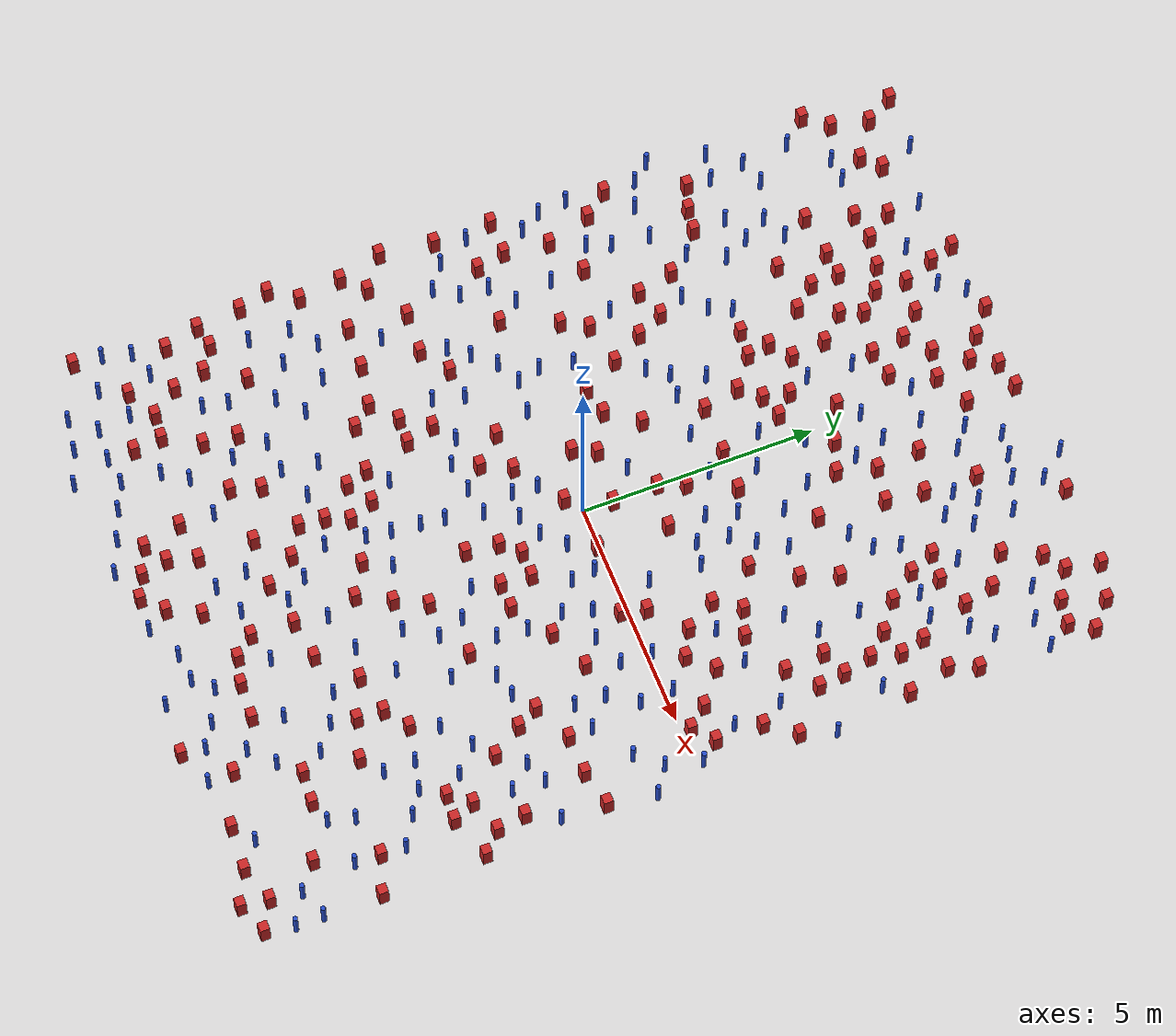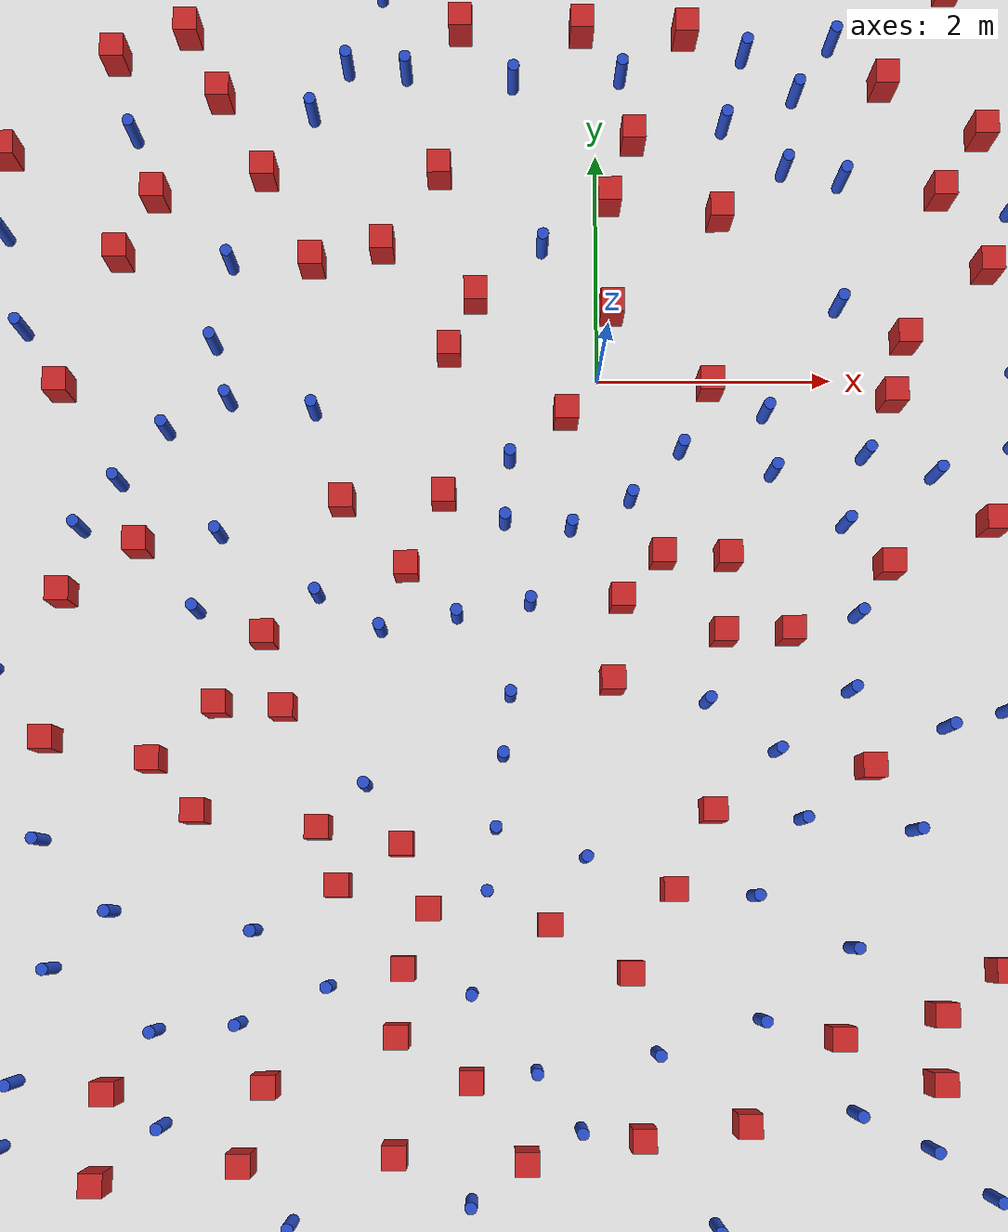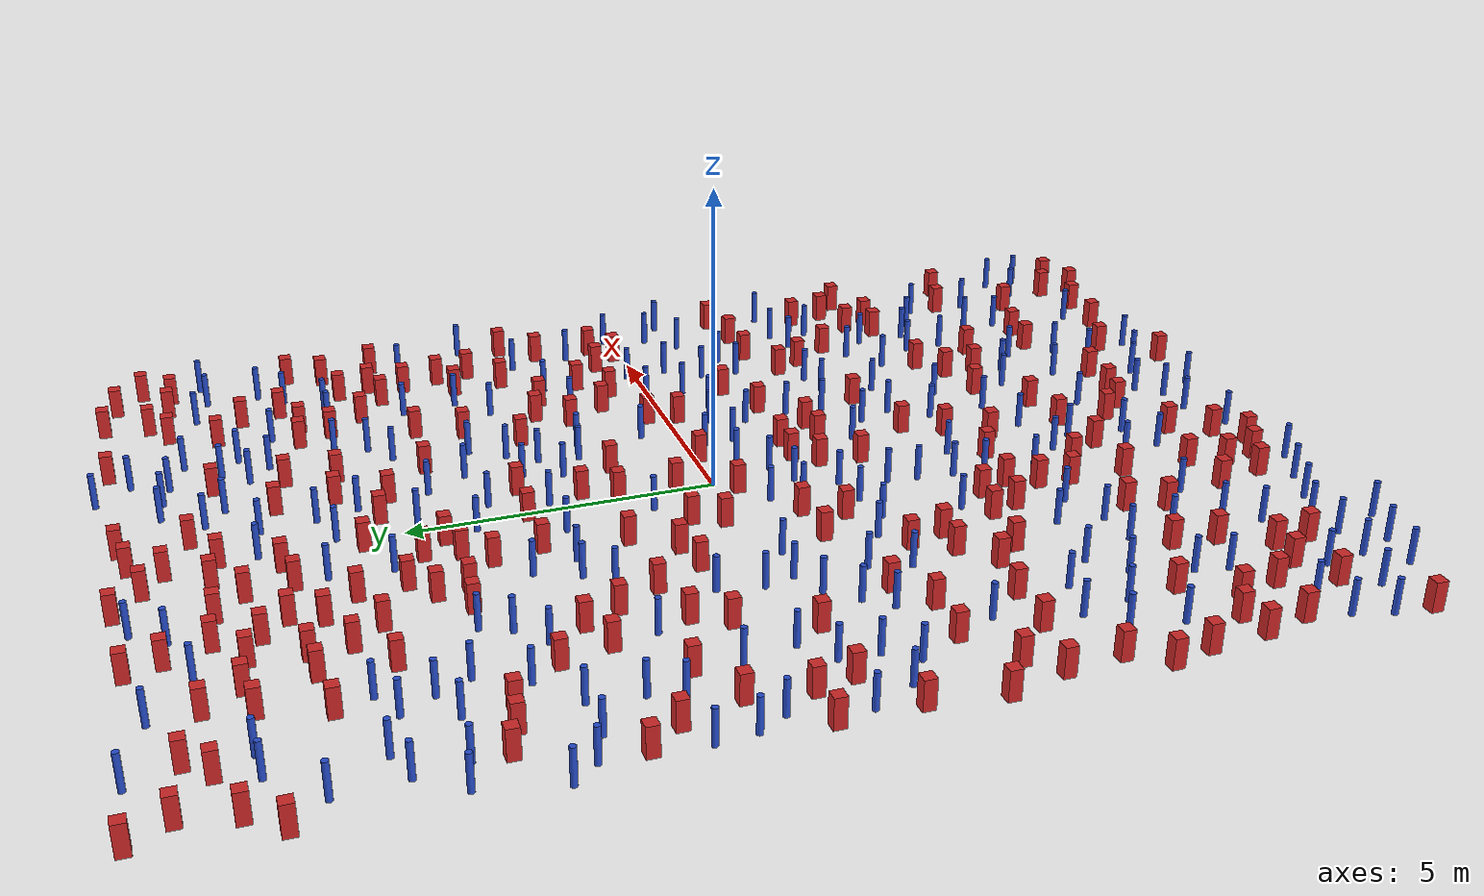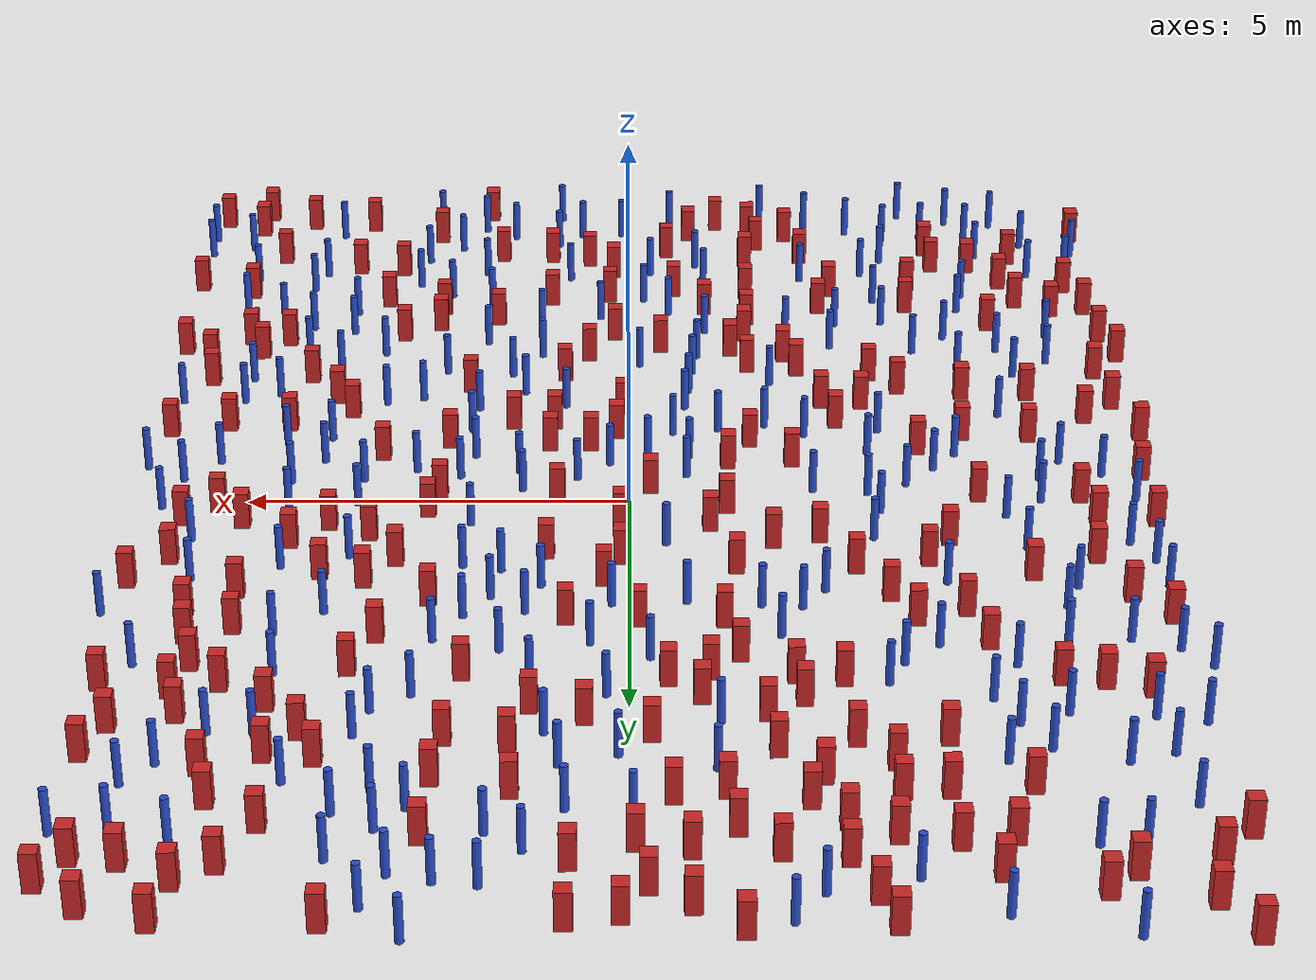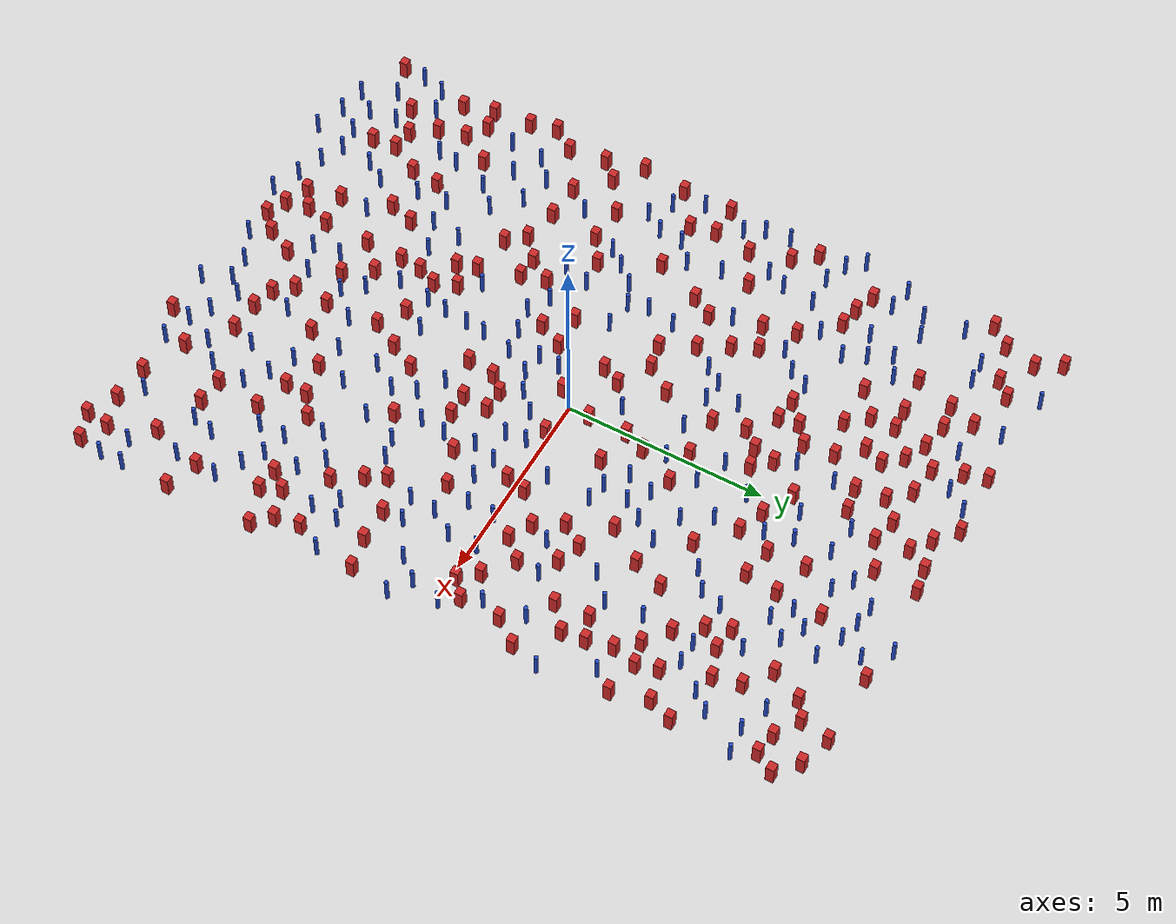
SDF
<sdf version="1.6">
  <model name="dense_22"><model name="square_post_obstacle0">
  <static>true</static>
  <pose frame="">-6.55129325416 9.47398239666 -6.11067671241e-07 -5.50515727128e-06 -8.79689657224e-07 2.37013304536e-05</pose>
  <link name="link">
    <pose frame="">0 0 0.25 0 -0 0</pose>
    <inertial>
      <mass>100</mass>
      <inertia>
        <ixx>0.166667</ixx>
        <ixy>0</ixy>
        <ixz>0</ixz>
        <iyy>0.166667</iyy>
        <iyz>0</iyz>
        <izz>0.166667</izz>
      </inertia>
    </inertial>
    <collision name="collision">
      <geometry>
        <box>
          <size>.2 .2 .5</size>
        </box>
      </geometry>
      <max_contacts>10</max_contacts>
      <surface>
        <contact>
          <ode/>
        </contact>
        <bounce/>
        <friction>
          <torsional>
            <ode/>
          </torsional>
          <ode/>
        </friction>
      </surface>
    </collision>
    <visual name="visual">
      <geometry>
        <box>
          <size>.2 .2 .5</size>
        </box>
      </geometry>
      <material>
        <script>
          <name>Gazebo/Red</name>
          <uri>file://media/materials/scripts/gazebo.material</uri>
        </script>
      </material>
    </visual>
    <self_collide>0</self_collide>
    <kinematic>0</kinematic>
  </link>
</model>
<model name="square_post_obstacle1">
  <static>true</static>
  <pose frame="">4.42170343339 8.20966445941 -6.11067671241e-07 -5.50515727128e-06 -8.79689657224e-07 2.37013304536e-05</pose>
  <link name="link">
    <pose frame="">0 0 0.25 0 -0 0</pose>
    <inertial>
      <mass>100</mass>
      <inertia>
        <ixx>0.166667</ixx>
        <ixy>0</ixy>
        <ixz>0</ixz>
        <iyy>0.166667</iyy>
        <iyz>0</iyz>
        <izz>0.166667</izz>
      </inertia>
    </inertial>
    <collision name="collision">
      <geometry>
        <box>
          <size>.2 .2 .5</size>
        </box>
      </geometry>
      <max_contacts>10</max_contacts>
      <surface>
        <contact>
          <ode/>
        </contact>
        <bounce/>
        <friction>
          <torsional>
            <ode/>
          </torsional>
          <ode/>
        </friction>
      </surface>
    </collision>
    <visual name="visual">
      <geometry>
        <box>
          <size>.2 .2 .5</size>
        </box>
      </geometry>
      <material>
        <script>
          <name>Gazebo/Red</name>
          <uri>file://media/materials/scripts/gazebo.material</uri>
        </script>
      </material>
    </visual>
    <self_collide>0</self_collide>
    <kinematic>0</kinematic>
  </link>
</model>
<model name="pole_obstacle0">
  <static>true</static>
  <pose frame="">-3.49918072226 -7.20875077813 -9.4761961606e-06 5.49618799729e-07 2.36310414006e-07 -1.55090534822e-07</pose>
  <link name="link">
  <pose frame="">0 0 0.3 0 -0 0</pose>
    <inertial>
      <mass>1</mass>
      <inertia>
        <ixx>0.145833</ixx>
        <ixy>0</ixy>
        <ixz>0</ixz>
        <iyy>0.145833</iyy>
        <iyz>0</iyz>
        <izz>0.125</izz>
      </inertia>
    </inertial>
    <collision name="collision">
      <geometry>
        <cylinder>
          <radius>0.05</radius>
          <length>.6</length>
        </cylinder>
      </geometry>
      <max_contacts>10</max_contacts>
      <surface>
        <contact>
          <ode/>
        </contact>
        <bounce/>
        <friction>
          <torsional>
            <ode/>
          </torsional>
          <ode/>
        </friction>
      </surface>
    </collision>
    <visual name="visual">
      <geometry>
        <cylinder>
          <radius>0.05</radius>
          <length>.6</length>
        </cylinder>
      </geometry>
      <material>
        <script>
          <name>Gazebo/Blue</name>
          <uri>file://media/materials/scripts/gazebo.material</uri>
        </script>
      </material>
    </visual>
    <self_collide>0</self_collide>
    <kinematic>0</kinematic>
  </link>
</model>
<model name="square_post_obstacle2">
  <static>true</static>
  <pose frame="">6.01994694953 8.0531341811 -6.11067671241e-07 -5.50515727128e-06 -8.79689657224e-07 2.37013304536e-05</pose>
  <link name="link">
    <pose frame="">0 0 0.25 0 -0 0</pose>
    <inertial>
      <mass>100</mass>
      <inertia>
        <ixx>0.166667</ixx>
        <ixy>0</ixy>
        <ixz>0</ixz>
        <iyy>0.166667</iyy>
        <iyz>0</iyz>
        <izz>0.166667</izz>
      </inertia>
    </inertial>
    <collision name="collision">
      <geometry>
        <box>
          <size>.2 .2 .5</size>
        </box>
      </geometry>
      <max_contacts>10</max_contacts>
      <surface>
        <contact>
          <ode/>
        </contact>
        <bounce/>
        <friction>
          <torsional>
            <ode/>
          </torsional>
          <ode/>
        </friction>
      </surface>
    </collision>
    <visual name="visual">
      <geometry>
        <box>
          <size>.2 .2 .5</size>
        </box>
      </geometry>
      <material>
        <script>
          <name>Gazebo/Red</name>
          <uri>file://media/materials/scripts/gazebo.material</uri>
        </script>
      </material>
    </visual>
    <self_collide>0</self_collide>
    <kinematic>0</kinematic>
  </link>
</model>
<model name="pole_obstacle1">
  <static>true</static>
  <pose frame="">5.37700357999 -2.93274806553 -9.47619616065e-06 5.49618799738e-07 2.36310414051e-07 -1.55090534805e-07</pose>
  <link name="link">
  <pose frame="">0 0 0.3 0 -0 0</pose>
    <inertial>
      <mass>1</mass>
      <inertia>
        <ixx>0.145833</ixx>
        <ixy>0</ixy>
        <ixz>0</ixz>
        <iyy>0.145833</iyy>
        <iyz>0</iyz>
        <izz>0.125</izz>
      </inertia>
    </inertial>
    <collision name="collision">
      <geometry>
        <cylinder>
          <radius>0.05</radius>
          <length>.6</length>
        </cylinder>
      </geometry>
      <max_contacts>10</max_contacts>
      <surface>
        <contact>
          <ode/>
        </contact>
        <bounce/>
        <friction>
          <torsional>
            <ode/>
          </torsional>
          <ode/>
        </friction>
      </surface>
    </collision>
    <visual name="visual">
      <geometry>
        <cylinder>
          <radius>0.05</radius>
          <length>.6</length>
        </cylinder>
      </geometry>
      <material>
        <script>
          <name>Gazebo/Blue</name>
          <uri>file://media/materials/scripts/gazebo.material</uri>
        </script>
      </material>
    </visual>
    <self_collide>0</self_collide>
    <kinematic>0</kinematic>
  </link>
</model>
<model name="square_post_obstacle3">
  <static>true</static>
  <pose frame="">-1.09705716129 -5.88747657592 -6.11067671241e-07 -5.50515727128e-06 -8.79689657224e-07 2.37013304536e-05</pose>
  <link name="link">
    <pose frame="">0 0 0.25 0 -0 0</pose>
    <inertial>
      <mass>100</mass>
      <inertia>
        <ixx>0.166667</ixx>
        <ixy>0</ixy>
        <ixz>0</ixz>
        <iyy>0.166667</iyy>
        <iyz>0</iyz>
        <izz>0.166667</izz>
      </inertia>
    </inertial>
    <collision name="collision">
      <geometry>
        <box>
          <size>.2 .2 .5</size>
        </box>
      </geometry>
      <max_contacts>10</max_contacts>
      <surface>
        <contact>
          <ode/>
        </contact>
        <bounce/>
        <friction>
          <torsional>
            <ode/>
          </torsional>
          <ode/>
        </friction>
      </surface>
    </collision>
    <visual name="visual">
      <geometry>
        <box>
          <size>.2 .2 .5</size>
        </box>
      </geometry>
      <material>
        <script>
          <name>Gazebo/Red</name>
          <uri>file://media/materials/scripts/gazebo.material</uri>
        </script>
      </material>
    </visual>
    <self_collide>0</self_collide>
    <kinematic>0</kinematic>
  </link>
</model>
<model name="pole_obstacle2">
  <static>true</static>
  <pose frame="">6.45418464428 -8.57963363264 -9.47619616065e-06 5.49618799737e-07 2.36310414065e-07 -1.55090534796e-07</pose>
  <link name="link">
  <pose frame="">0 0 0.3 0 -0 0</pose>
    <inertial>
      <mass>1</mass>
      <inertia>
        <ixx>0.145833</ixx>
        <ixy>0</ixy>
        <ixz>0</ixz>
        <iyy>0.145833</iyy>
        <iyz>0</iyz>
        <izz>0.125</izz>
      </inertia>
    </inertial>
    <collision name="collision">
      <geometry>
        <cylinder>
          <radius>0.05</radius>
          <length>.6</length>
        </cylinder>
      </geometry>
      <max_contacts>10</max_contacts>
      <surface>
        <contact>
          <ode/>
        </contact>
        <bounce/>
        <friction>
          <torsional>
            <ode/>
          </torsional>
          <ode/>
        </friction>
      </surface>
    </collision>
    <visual name="visual">
      <geometry>
        <cylinder>
          <radius>0.05</radius>
          <length>.6</length>
        </cylinder>
      </geometry>
      <material>
        <script>
          <name>Gazebo/Blue</name>
          <uri>file://media/materials/scripts/gazebo.material</uri>
        </script>
      </material>
    </visual>
    <self_collide>0</self_collide>
    <kinematic>0</kinematic>
  </link>
</model>
<model name="pole_obstacle3">
  <static>true</static>
  <pose frame="">-2.09019270715 8.67762348994 -9.4761961606e-06 5.49618799729e-07 2.36310414e-07 -1.55090534824e-07</pose>
  <link name="link">
  <pose frame="">0 0 0.3 0 -0 0</pose>
    <inertial>
      <mass>1</mass>
      <inertia>
        <ixx>0.145833</ixx>
        <ixy>0</ixy>
        <ixz>0</ixz>
        <iyy>0.145833</iyy>
        <iyz>0</iyz>
        <izz>0.125</izz>
      </inertia>
    </inertial>
    <collision name="collision">
      <geometry>
        <cylinder>
          <radius>0.05</radius>
          <length>.6</length>
        </cylinder>
      </geometry>
      <max_contacts>10</max_contacts>
      <surface>
        <contact>
          <ode/>
        </contact>
        <bounce/>
        <friction>
          <torsional>
            <ode/>
          </torsional>
          <ode/>
        </friction>
      </surface>
    </collision>
    <visual name="visual">
      <geometry>
        <cylinder>
          <radius>0.05</radius>
          <length>.6</length>
        </cylinder>
      </geometry>
      <material>
        <script>
          <name>Gazebo/Blue</name>
          <uri>file://media/materials/scripts/gazebo.material</uri>
        </script>
      </material>
    </visual>
    <self_collide>0</self_collide>
    <kinematic>0</kinematic>
  </link>
</model>
<model name="square_post_obstacle4">
  <static>true</static>
  <pose frame="">6.26932080476 2.13416776253 -6.11067671241e-07 -5.50515727128e-06 -8.79689657224e-07 2.37013304536e-05</pose>
  <link name="link">
    <pose frame="">0 0 0.25 0 -0 0</pose>
    <inertial>
      <mass>100</mass>
      <inertia>
        <ixx>0.166667</ixx>
        <ixy>0</ixy>
        <ixz>0</ixz>
        <iyy>0.166667</iyy>
        <iyz>0</iyz>
        <izz>0.166667</izz>
      </inertia>
    </inertial>
    <collision name="collision">
      <geometry>
        <box>
          <size>.2 .2 .5</size>
        </box>
      </geometry>
      <max_contacts>10</max_contacts>
      <surface>
        <contact>
          <ode/>
        </contact>
        <bounce/>
        <friction>
          <torsional>
            <ode/>
          </torsional>
          <ode/>
        </friction>
      </surface>
    </collision>
    <visual name="visual">
      <geometry>
        <box>
          <size>.2 .2 .5</size>
        </box>
      </geometry>
      <material>
        <script>
          <name>Gazebo/Red</name>
          <uri>file://media/materials/scripts/gazebo.material</uri>
        </script>
      </material>
    </visual>
    <self_collide>0</self_collide>
    <kinematic>0</kinematic>
  </link>
</model>
<model name="square_post_obstacle5">
  <static>true</static>
  <pose frame="">-6.06662300361 0.604514829962 -6.11067671241e-07 -5.50515727128e-06 -8.79689657224e-07 2.37013304536e-05</pose>
  <link name="link">
    <pose frame="">0 0 0.25 0 -0 0</pose>
    <inertial>
      <mass>100</mass>
      <inertia>
        <ixx>0.166667</ixx>
        <ixy>0</ixy>
        <ixz>0</ixz>
        <iyy>0.166667</iyy>
        <iyz>0</iyz>
        <izz>0.166667</izz>
      </inertia>
    </inertial>
    <collision name="collision">
      <geometry>
        <box>
          <size>.2 .2 .5</size>
        </box>
      </geometry>
      <max_contacts>10</max_contacts>
      <surface>
        <contact>
          <ode/>
        </contact>
        <bounce/>
        <friction>
          <torsional>
            <ode/>
          </torsional>
          <ode/>
        </friction>
      </surface>
    </collision>
    <visual name="visual">
      <geometry>
        <box>
          <size>.2 .2 .5</size>
        </box>
      </geometry>
      <material>
        <script>
          <name>Gazebo/Red</name>
          <uri>file://media/materials/scripts/gazebo.material</uri>
        </script>
      </material>
    </visual>
    <self_collide>0</self_collide>
    <kinematic>0</kinematic>
  </link>
</model>
<model name="square_post_obstacle6">
  <static>true</static>
  <pose frame="">-6.38697773006 8.07653702555 -6.11067671241e-07 -5.50515727128e-06 -8.79689657224e-07 2.37013304536e-05</pose>
  <link name="link">
    <pose frame="">0 0 0.25 0 -0 0</pose>
    <inertial>
      <mass>100</mass>
      <inertia>
        <ixx>0.166667</ixx>
        <ixy>0</ixy>
        <ixz>0</ixz>
        <iyy>0.166667</iyy>
        <iyz>0</iyz>
        <izz>0.166667</izz>
      </inertia>
    </inertial>
    <collision name="collision">
      <geometry>
        <box>
          <size>.2 .2 .5</size>
        </box>
      </geometry>
      <max_contacts>10</max_contacts>
      <surface>
        <contact>
          <ode/>
        </contact>
        <bounce/>
        <friction>
          <torsional>
            <ode/>
          </torsional>
          <ode/>
        </friction>
      </surface>
    </collision>
    <visual name="visual">
      <geometry>
        <box>
          <size>.2 .2 .5</size>
        </box>
      </geometry>
      <material>
        <script>
          <name>Gazebo/Red</name>
          <uri>file://media/materials/scripts/gazebo.material</uri>
        </script>
      </material>
    </visual>
    <self_collide>0</self_collide>
    <kinematic>0</kinematic>
  </link>
</model>
<model name="pole_obstacle4">
  <static>true</static>
  <pose frame="">-1.06302491297 5.34108228484 -9.47619616065e-06 5.49618799737e-07 2.36310414061e-07 -1.550905348e-07</pose>
  <link name="link">
  <pose frame="">0 0 0.3 0 -0 0</pose>
    <inertial>
      <mass>1</mass>
      <inertia>
        <ixx>0.145833</ixx>
        <ixy>0</ixy>
        <ixz>0</ixz>
        <iyy>0.145833</iyy>
        <iyz>0</iyz>
        <izz>0.125</izz>
      </inertia>
    </inertial>
    <collision name="collision">
      <geometry>
        <cylinder>
          <radius>0.05</radius>
          <length>.6</length>
        </cylinder>
      </geometry>
      <max_contacts>10</max_contacts>
      <surface>
        <contact>
          <ode/>
        </contact>
        <bounce/>
        <friction>
          <torsional>
            <ode/>
          </torsional>
          <ode/>
        </friction>
      </surface>
    </collision>
    <visual name="visual">
      <geometry>
        <cylinder>
          <radius>0.05</radius>
          <length>.6</length>
        </cylinder>
      </geometry>
      <material>
        <script>
          <name>Gazebo/Blue</name>
          <uri>file://media/materials/scripts/gazebo.material</uri>
        </script>
      </material>
    </visual>
    <self_collide>0</self_collide>
    <kinematic>0</kinematic>
  </link>
</model>
<model name="pole_obstacle5">
  <static>true</static>
  <pose frame="">-4.29775557987 6.17929323711 -9.47619616065e-06 5.49618799737e-07 2.36310414037e-07 -1.55090534814e-07</pose>
  <link name="link">
  <pose frame="">0 0 0.3 0 -0 0</pose>
    <inertial>
      <mass>1</mass>
      <inertia>
        <ixx>0.145833</ixx>
        <ixy>0</ixy>
        <ixz>0</ixz>
        <iyy>0.145833</iyy>
        <iyz>0</iyz>
        <izz>0.125</izz>
      </inertia>
    </inertial>
    <collision name="collision">
      <geometry>
        <cylinder>
          <radius>0.05</radius>
          <length>.6</length>
        </cylinder>
      </geometry>
      <max_contacts>10</max_contacts>
      <surface>
        <contact>
          <ode/>
        </contact>
        <bounce/>
        <friction>
          <torsional>
            <ode/>
          </torsional>
          <ode/>
        </friction>
      </surface>
    </collision>
    <visual name="visual">
      <geometry>
        <cylinder>
          <radius>0.05</radius>
          <length>.6</length>
        </cylinder>
      </geometry>
      <material>
        <script>
          <name>Gazebo/Blue</name>
          <uri>file://media/materials/scripts/gazebo.material</uri>
        </script>
      </material>
    </visual>
    <self_collide>0</self_collide>
    <kinematic>0</kinematic>
  </link>
</model>
<model name="square_post_obstacle7">
  <static>true</static>
  <pose frame="">2.61931399791 0.32892126336 -6.11067671241e-07 -5.50515727128e-06 -8.79689657224e-07 2.37013304536e-05</pose>
  <link name="link">
    <pose frame="">0 0 0.25 0 -0 0</pose>
    <inertial>
      <mass>100</mass>
      <inertia>
        <ixx>0.166667</ixx>
        <ixy>0</ixy>
        <ixz>0</ixz>
        <iyy>0.166667</iyy>
        <iyz>0</iyz>
        <izz>0.166667</izz>
      </inertia>
    </inertial>
    <collision name="collision">
      <geometry>
        <box>
          <size>.2 .2 .5</size>
        </box>
      </geometry>
      <max_contacts>10</max_contacts>
      <surface>
        <contact>
          <ode/>
        </contact>
        <bounce/>
        <friction>
          <torsional>
            <ode/>
          </torsional>
          <ode/>
        </friction>
      </surface>
    </collision>
    <visual name="visual">
      <geometry>
        <box>
          <size>.2 .2 .5</size>
        </box>
      </geometry>
      <material>
        <script>
          <name>Gazebo/Red</name>
          <uri>file://media/materials/scripts/gazebo.material</uri>
        </script>
      </material>
    </visual>
    <self_collide>0</self_collide>
    <kinematic>0</kinematic>
  </link>
</model>
<model name="square_post_obstacle8">
  <static>true</static>
  <pose frame="">0.779400273148 3.0589968224 -6.11067671241e-07 -5.50515727128e-06 -8.79689657224e-07 2.37013304536e-05</pose>
  <link name="link">
    <pose frame="">0 0 0.25 0 -0 0</pose>
    <inertial>
      <mass>100</mass>
      <inertia>
        <ixx>0.166667</ixx>
        <ixy>0</ixy>
        <ixz>0</ixz>
        <iyy>0.166667</iyy>
        <iyz>0</iyz>
        <izz>0.166667</izz>
      </inertia>
    </inertial>
    <collision name="collision">
      <geometry>
        <box>
          <size>.2 .2 .5</size>
        </box>
      </geometry>
      <max_contacts>10</max_contacts>
      <surface>
        <contact>
          <ode/>
        </contact>
        <bounce/>
        <friction>
          <torsional>
            <ode/>
          </torsional>
          <ode/>
        </friction>
      </surface>
    </collision>
    <visual name="visual">
      <geometry>
        <box>
          <size>.2 .2 .5</size>
        </box>
      </geometry>
      <material>
        <script>
          <name>Gazebo/Red</name>
          <uri>file://media/materials/scripts/gazebo.material</uri>
        </script>
      </material>
    </visual>
    <self_collide>0</self_collide>
    <kinematic>0</kinematic>
  </link>
</model>
<model name="pole_obstacle6">
  <static>true</static>
  <pose frame="">5.68251448427 -5.98446094993 -9.47619616065e-06 5.49618799737e-07 2.36310414037e-07 -1.55090534814e-07</pose>
  <link name="link">
  <pose frame="">0 0 0.3 0 -0 0</pose>
    <inertial>
      <mass>1</mass>
      <inertia>
        <ixx>0.145833</ixx>
        <ixy>0</ixy>
        <ixz>0</ixz>
        <iyy>0.145833</iyy>
        <iyz>0</iyz>
        <izz>0.125</izz>
      </inertia>
    </inertial>
    <collision name="collision">
      <geometry>
        <cylinder>
          <radius>0.05</radius>
          <length>.6</length>
        </cylinder>
      </geometry>
      <max_contacts>10</max_contacts>
      <surface>
        <contact>
          <ode/>
        </contact>
        <bounce/>
        <friction>
          <torsional>
            <ode/>
          </torsional>
          <ode/>
        </friction>
      </surface>
    </collision>
    <visual name="visual">
      <geometry>
        <cylinder>
          <radius>0.05</radius>
          <length>.6</length>
        </cylinder>
      </geometry>
      <material>
        <script>
          <name>Gazebo/Blue</name>
          <uri>file://media/materials/scripts/gazebo.material</uri>
        </script>
      </material>
    </visual>
    <self_collide>0</self_collide>
    <kinematic>0</kinematic>
  </link>
</model>
<model name="pole_obstacle7">
  <static>true</static>
  <pose frame="">-5.32592031374 9.43319884852 -9.47619616065e-06 5.49618799737e-07 2.36310414065e-07 -1.55090534796e-07</pose>
  <link name="link">
  <pose frame="">0 0 0.3 0 -0 0</pose>
    <inertial>
      <mass>1</mass>
      <inertia>
        <ixx>0.145833</ixx>
        <ixy>0</ixy>
        <ixz>0</ixz>
        <iyy>0.145833</iyy>
        <iyz>0</iyz>
        <izz>0.125</izz>
      </inertia>
    </inertial>
    <collision name="collision">
      <geometry>
        <cylinder>
          <radius>0.05</radius>
          <length>.6</length>
        </cylinder>
      </geometry>
      <max_contacts>10</max_contacts>
      <surface>
        <contact>
          <ode/>
        </contact>
        <bounce/>
        <friction>
          <torsional>
            <ode/>
          </torsional>
          <ode/>
        </friction>
      </surface>
    </collision>
    <visual name="visual">
      <geometry>
        <cylinder>
          <radius>0.05</radius>
          <length>.6</length>
        </cylinder>
      </geometry>
      <material>
        <script>
          <name>Gazebo/Blue</name>
          <uri>file://media/materials/scripts/gazebo.material</uri>
        </script>
      </material>
    </visual>
    <self_collide>0</self_collide>
    <kinematic>0</kinematic>
  </link>
</model>
<model name="square_post_obstacle9">
  <static>true</static>
  <pose frame="">0.101790933784 1.56928342861 -6.11067671241e-07 -5.50515727128e-06 -8.79689657224e-07 2.37013304536e-05</pose>
  <link name="link">
    <pose frame="">0 0 0.25 0 -0 0</pose>
    <inertial>
      <mass>100</mass>
      <inertia>
        <ixx>0.166667</ixx>
        <ixy>0</ixy>
        <ixz>0</ixz>
        <iyy>0.166667</iyy>
        <iyz>0</iyz>
        <izz>0.166667</izz>
      </inertia>
    </inertial>
    <collision name="collision">
      <geometry>
        <box>
          <size>.2 .2 .5</size>
        </box>
      </geometry>
      <max_contacts>10</max_contacts>
      <surface>
        <contact>
          <ode/>
        </contact>
        <bounce/>
        <friction>
          <torsional>
            <ode/>
          </torsional>
          <ode/>
        </friction>
      </surface>
    </collision>
    <visual name="visual">
      <geometry>
        <box>
          <size>.2 .2 .5</size>
        </box>
      </geometry>
      <material>
        <script>
          <name>Gazebo/Red</name>
          <uri>file://media/materials/scripts/gazebo.material</uri>
        </script>
      </material>
    </visual>
    <self_collide>0</self_collide>
    <kinematic>0</kinematic>
  </link>
</model>
<model name="square_post_obstacle10">
  <static>true</static>
  <pose frame="">-1.35094826481 1.81705522955 -6.11067671241e-07 -5.50515727128e-06 -8.79689657224e-07 2.37013304536e-05</pose>
  <link name="link">
    <pose frame="">0 0 0.25 0 -0 0</pose>
    <inertial>
      <mass>100</mass>
      <inertia>
        <ixx>0.166667</ixx>
        <ixy>0</ixy>
        <ixz>0</ixz>
        <iyy>0.166667</iyy>
        <iyz>0</iyz>
        <izz>0.166667</izz>
      </inertia>
    </inertial>
    <collision name="collision">
      <geometry>
        <box>
          <size>.2 .2 .5</size>
        </box>
      </geometry>
      <max_contacts>10</max_contacts>
      <surface>
        <contact>
          <ode/>
        </contact>
        <bounce/>
        <friction>
          <torsional>
            <ode/>
          </torsional>
          <ode/>
        </friction>
      </surface>
    </collision>
    <visual name="visual">
      <geometry>
        <box>
          <size>.2 .2 .5</size>
        </box>
      </geometry>
      <material>
        <script>
          <name>Gazebo/Red</name>
          <uri>file://media/materials/scripts/gazebo.material</uri>
        </script>
      </material>
    </visual>
    <self_collide>0</self_collide>
    <kinematic>0</kinematic>
  </link>
</model>
<model name="square_post_obstacle11">
  <static>true</static>
  <pose frame="">3.31928973147 -1.26403502904 -6.11067671241e-07 -5.50515727128e-06 -8.79689657224e-07 2.37013304536e-05</pose>
  <link name="link">
    <pose frame="">0 0 0.25 0 -0 0</pose>
    <inertial>
      <mass>100</mass>
      <inertia>
        <ixx>0.166667</ixx>
        <ixy>0</ixy>
        <ixz>0</ixz>
        <iyy>0.166667</iyy>
        <iyz>0</iyz>
        <izz>0.166667</izz>
      </inertia>
    </inertial>
    <collision name="collision">
      <geometry>
        <box>
          <size>.2 .2 .5</size>
        </box>
      </geometry>
      <max_contacts>10</max_contacts>
      <surface>
        <contact>
          <ode/>
        </contact>
        <bounce/>
        <friction>
          <torsional>
            <ode/>
          </torsional>
          <ode/>
        </friction>
      </surface>
    </collision>
    <visual name="visual">
      <geometry>
        <box>
          <size>.2 .2 .5</size>
        </box>
      </geometry>
      <material>
        <script>
          <name>Gazebo/Red</name>
          <uri>file://media/materials/scripts/gazebo.material</uri>
        </script>
      </material>
    </visual>
    <self_collide>0</self_collide>
    <kinematic>0</kinematic>
  </link>
</model>
<model name="square_post_obstacle12">
  <static>true</static>
  <pose frame="">5.79151659013 0.536573536814 -6.11067671241e-07 -5.50515727128e-06 -8.79689657224e-07 2.37013304536e-05</pose>
  <link name="link">
    <pose frame="">0 0 0.25 0 -0 0</pose>
    <inertial>
      <mass>100</mass>
      <inertia>
        <ixx>0.166667</ixx>
        <ixy>0</ixy>
        <ixz>0</ixz>
        <iyy>0.166667</iyy>
        <iyz>0</iyz>
        <izz>0.166667</izz>
      </inertia>
    </inertial>
    <collision name="collision">
      <geometry>
        <box>
          <size>.2 .2 .5</size>
        </box>
      </geometry>
      <max_contacts>10</max_contacts>
      <surface>
        <contact>
          <ode/>
        </contact>
        <bounce/>
        <friction>
          <torsional>
            <ode/>
          </torsional>
          <ode/>
        </friction>
      </surface>
    </collision>
    <visual name="visual">
      <geometry>
        <box>
          <size>.2 .2 .5</size>
        </box>
      </geometry>
      <material>
        <script>
          <name>Gazebo/Red</name>
          <uri>file://media/materials/scripts/gazebo.material</uri>
        </script>
      </material>
    </visual>
    <self_collide>0</self_collide>
    <kinematic>0</kinematic>
  </link>
</model>
<model name="square_post_obstacle13">
  <static>true</static>
  <pose frame="">0.653260003176 8.16057962834 -6.11067671241e-07 -5.50515727128e-06 -8.79689657224e-07 2.37013304536e-05</pose>
  <link name="link">
    <pose frame="">0 0 0.25 0 -0 0</pose>
    <inertial>
      <mass>100</mass>
      <inertia>
        <ixx>0.166667</ixx>
        <ixy>0</ixy>
        <ixz>0</ixz>
        <iyy>0.166667</iyy>
        <iyz>0</iyz>
        <izz>0.166667</izz>
      </inertia>
    </inertial>
    <collision name="collision">
      <geometry>
        <box>
          <size>.2 .2 .5</size>
        </box>
      </geometry>
      <max_contacts>10</max_contacts>
      <surface>
        <contact>
          <ode/>
        </contact>
        <bounce/>
        <friction>
          <torsional>
            <ode/>
          </torsional>
          <ode/>
        </friction>
      </surface>
    </collision>
    <visual name="visual">
      <geometry>
        <box>
          <size>.2 .2 .5</size>
        </box>
      </geometry>
      <material>
        <script>
          <name>Gazebo/Red</name>
          <uri>file://media/materials/scripts/gazebo.material</uri>
        </script>
      </material>
    </visual>
    <self_collide>0</self_collide>
    <kinematic>0</kinematic>
  </link>
</model>
<model name="pole_obstacle8">
  <static>true</static>
  <pose frame="">-0.241706042491 -1.29657250172 -9.47619616065e-06 5.49618799738e-07 2.36310414065e-07 -1.55090534798e-07</pose>
  <link name="link">
  <pose frame="">0 0 0.3 0 -0 0</pose>
    <inertial>
      <mass>1</mass>
      <inertia>
        <ixx>0.145833</ixx>
        <ixy>0</ixy>
        <ixz>0</ixz>
        <iyy>0.145833</iyy>
        <iyz>0</iyz>
        <izz>0.125</izz>
      </inertia>
    </inertial>
    <collision name="collision">
      <geometry>
        <cylinder>
          <radius>0.05</radius>
          <length>.6</length>
        </cylinder>
      </geometry>
      <max_contacts>10</max_contacts>
      <surface>
        <contact>
          <ode/>
        </contact>
        <bounce/>
        <friction>
          <torsional>
            <ode/>
          </torsional>
          <ode/>
        </friction>
      </surface>
    </collision>
    <visual name="visual">
      <geometry>
        <cylinder>
          <radius>0.05</radius>
          <length>.6</length>
        </cylinder>
      </geometry>
      <material>
        <script>
          <name>Gazebo/Blue</name>
          <uri>file://media/materials/scripts/gazebo.material</uri>
        </script>
      </material>
    </visual>
    <self_collide>0</self_collide>
    <kinematic>0</kinematic>
  </link>
</model>
<model name="square_post_obstacle14">
  <static>true</static>
  <pose frame="">0.612522128558 -7.66524894821 -6.11067671241e-07 -5.50515727128e-06 -8.79689657224e-07 2.37013304536e-05</pose>
  <link name="link">
    <pose frame="">0 0 0.25 0 -0 0</pose>
    <inertial>
      <mass>100</mass>
      <inertia>
        <ixx>0.166667</ixx>
        <ixy>0</ixy>
        <ixz>0</ixz>
        <iyy>0.166667</iyy>
        <iyz>0</iyz>
        <izz>0.166667</izz>
      </inertia>
    </inertial>
    <collision name="collision">
      <geometry>
        <box>
          <size>.2 .2 .5</size>
        </box>
      </geometry>
      <max_contacts>10</max_contacts>
      <surface>
        <contact>
          <ode/>
        </contact>
        <bounce/>
        <friction>
          <torsional>
            <ode/>
          </torsional>
          <ode/>
        </friction>
      </surface>
    </collision>
    <visual name="visual">
      <geometry>
        <box>
          <size>.2 .2 .5</size>
        </box>
      </geometry>
      <material>
        <script>
          <name>Gazebo/Red</name>
          <uri>file://media/materials/scripts/gazebo.material</uri>
        </script>
      </material>
    </visual>
    <self_collide>0</self_collide>
    <kinematic>0</kinematic>
  </link>
</model>
<model name="square_post_obstacle15">
  <static>true</static>
  <pose frame="">2.95515435854 1.60631993634 -6.11067671241e-07 -5.50515727128e-06 -8.79689657224e-07 2.37013304536e-05</pose>
  <link name="link">
    <pose frame="">0 0 0.25 0 -0 0</pose>
    <inertial>
      <mass>100</mass>
      <inertia>
        <ixx>0.166667</ixx>
        <ixy>0</ixy>
        <ixz>0</ixz>
        <iyy>0.166667</iyy>
        <iyz>0</iyz>
        <izz>0.166667</izz>
      </inertia>
    </inertial>
    <collision name="collision">
      <geometry>
        <box>
          <size>.2 .2 .5</size>
        </box>
      </geometry>
      <max_contacts>10</max_contacts>
      <surface>
        <contact>
          <ode/>
        </contact>
        <bounce/>
        <friction>
          <torsional>
            <ode/>
          </torsional>
          <ode/>
        </friction>
      </surface>
    </collision>
    <visual name="visual">
      <geometry>
        <box>
          <size>.2 .2 .5</size>
        </box>
      </geometry>
      <material>
        <script>
          <name>Gazebo/Red</name>
          <uri>file://media/materials/scripts/gazebo.material</uri>
        </script>
      </material>
    </visual>
    <self_collide>0</self_collide>
    <kinematic>0</kinematic>
  </link>
</model>
<model name="square_post_obstacle16">
  <static>true</static>
  <pose frame="">1.98771499368 4.31782590708 -6.11067671241e-07 -5.50515727128e-06 -8.79689657224e-07 2.37013304536e-05</pose>
  <link name="link">
    <pose frame="">0 0 0.25 0 -0 0</pose>
    <inertial>
      <mass>100</mass>
      <inertia>
        <ixx>0.166667</ixx>
        <ixy>0</ixy>
        <ixz>0</ixz>
        <iyy>0.166667</iyy>
        <iyz>0</iyz>
        <izz>0.166667</izz>
      </inertia>
    </inertial>
    <collision name="collision">
      <geometry>
        <box>
          <size>.2 .2 .5</size>
        </box>
      </geometry>
      <max_contacts>10</max_contacts>
      <surface>
        <contact>
          <ode/>
        </contact>
        <bounce/>
        <friction>
          <torsional>
            <ode/>
          </torsional>
          <ode/>
        </friction>
      </surface>
    </collision>
    <visual name="visual">
      <geometry>
        <box>
          <size>.2 .2 .5</size>
        </box>
      </geometry>
      <material>
        <script>
          <name>Gazebo/Red</name>
          <uri>file://media/materials/scripts/gazebo.material</uri>
        </script>
      </material>
    </visual>
    <self_collide>0</self_collide>
    <kinematic>0</kinematic>
  </link>
</model>
<model name="pole_obstacle9">
  <static>true</static>
  <pose frame="">3.38589451767 -2.86636324832 -9.47619616065e-06 5.49618799737e-07 2.36310414051e-07 -1.55090534807e-07</pose>
  <link name="link">
  <pose frame="">0 0 0.3 0 -0 0</pose>
    <inertial>
      <mass>1</mass>
      <inertia>
        <ixx>0.145833</ixx>
        <ixy>0</ixy>
        <ixz>0</ixz>
        <iyy>0.145833</iyy>
        <iyz>0</iyz>
        <izz>0.125</izz>
      </inertia>
    </inertial>
    <collision name="collision">
      <geometry>
        <cylinder>
          <radius>0.05</radius>
          <length>.6</length>
        </cylinder>
      </geometry>
      <max_contacts>10</max_contacts>
      <surface>
        <contact>
          <ode/>
        </contact>
        <bounce/>
        <friction>
          <torsional>
            <ode/>
          </torsional>
          <ode/>
        </friction>
      </surface>
    </collision>
    <visual name="visual">
      <geometry>
        <cylinder>
          <radius>0.05</radius>
          <length>.6</length>
        </cylinder>
      </geometry>
      <material>
        <script>
          <name>Gazebo/Blue</name>
          <uri>file://media/materials/scripts/gazebo.material</uri>
        </script>
      </material>
    </visual>
    <self_collide>0</self_collide>
    <kinematic>0</kinematic>
  </link>
</model>
<model name="square_post_obstacle17">
  <static>true</static>
  <pose frame="">-6.20452500307 8.8755536267 -6.11067671241e-07 -5.50515727128e-06 -8.79689657224e-07 2.37013304536e-05</pose>
  <link name="link">
    <pose frame="">0 0 0.25 0 -0 0</pose>
    <inertial>
      <mass>100</mass>
      <inertia>
        <ixx>0.166667</ixx>
        <ixy>0</ixy>
        <ixz>0</ixz>
        <iyy>0.166667</iyy>
        <iyz>0</iyz>
        <izz>0.166667</izz>
      </inertia>
    </inertial>
    <collision name="collision">
      <geometry>
        <box>
          <size>.2 .2 .5</size>
        </box>
      </geometry>
      <max_contacts>10</max_contacts>
      <surface>
        <contact>
          <ode/>
        </contact>
        <bounce/>
        <friction>
          <torsional>
            <ode/>
          </torsional>
          <ode/>
        </friction>
      </surface>
    </collision>
    <visual name="visual">
      <geometry>
        <box>
          <size>.2 .2 .5</size>
        </box>
      </geometry>
      <material>
        <script>
          <name>Gazebo/Red</name>
          <uri>file://media/materials/scripts/gazebo.material</uri>
        </script>
      </material>
    </visual>
    <self_collide>0</self_collide>
    <kinematic>0</kinematic>
  </link>
</model>
<model name="square_post_obstacle18">
  <static>true</static>
  <pose frame="">-1.74905693073 -7.65027049978 -6.11067671241e-07 -5.50515727128e-06 -8.79689657224e-07 2.37013304536e-05</pose>
  <link name="link">
    <pose frame="">0 0 0.25 0 -0 0</pose>
    <inertial>
      <mass>100</mass>
      <inertia>
        <ixx>0.166667</ixx>
        <ixy>0</ixy>
        <ixz>0</ixz>
        <iyy>0.166667</iyy>
        <iyz>0</iyz>
        <izz>0.166667</izz>
      </inertia>
    </inertial>
    <collision name="collision">
      <geometry>
        <box>
          <size>.2 .2 .5</size>
        </box>
      </geometry>
      <max_contacts>10</max_contacts>
      <surface>
        <contact>
          <ode/>
        </contact>
        <bounce/>
        <friction>
          <torsional>
            <ode/>
          </torsional>
          <ode/>
        </friction>
      </surface>
    </collision>
    <visual name="visual">
      <geometry>
        <box>
          <size>.2 .2 .5</size>
        </box>
      </geometry>
      <material>
        <script>
          <name>Gazebo/Red</name>
          <uri>file://media/materials/scripts/gazebo.material</uri>
        </script>
      </material>
    </visual>
    <self_collide>0</self_collide>
    <kinematic>0</kinematic>
  </link>
</model>
<model name="pole_obstacle10">
  <static>true</static>
  <pose frame="">-0.762527081774 -2.71304508485 -9.47619616065e-06 5.49618799737e-07 2.36310414066e-07 -1.55090534797e-07</pose>
  <link name="link">
  <pose frame="">0 0 0.3 0 -0 0</pose>
    <inertial>
      <mass>1</mass>
      <inertia>
        <ixx>0.145833</ixx>
        <ixy>0</ixy>
        <ixz>0</ixz>
        <iyy>0.145833</iyy>
        <iyz>0</iyz>
        <izz>0.125</izz>
      </inertia>
    </inertial>
    <collision name="collision">
      <geometry>
        <cylinder>
          <radius>0.05</radius>
          <length>.6</length>
        </cylinder>
      </geometry>
      <max_contacts>10</max_contacts>
      <surface>
        <contact>
          <ode/>
        </contact>
        <bounce/>
        <friction>
          <torsional>
            <ode/>
          </torsional>
          <ode/>
        </friction>
      </surface>
    </collision>
    <visual name="visual">
      <geometry>
        <cylinder>
          <radius>0.05</radius>
          <length>.6</length>
        </cylinder>
      </geometry>
      <material>
        <script>
          <name>Gazebo/Blue</name>
          <uri>file://media/materials/scripts/gazebo.material</uri>
        </script>
      </material>
    </visual>
    <self_collide>0</self_collide>
    <kinematic>0</kinematic>
  </link>
</model>
<model name="square_post_obstacle19">
  <static>true</static>
  <pose frame="">1.92925214817 -5.55344616213 -6.11067671241e-07 -5.50515727128e-06 -8.79689657224e-07 2.37013304536e-05</pose>
  <link name="link">
    <pose frame="">0 0 0.25 0 -0 0</pose>
    <inertial>
      <mass>100</mass>
      <inertia>
        <ixx>0.166667</ixx>
        <ixy>0</ixy>
        <ixz>0</ixz>
        <iyy>0.166667</iyy>
        <iyz>0</iyz>
        <izz>0.166667</izz>
      </inertia>
    </inertial>
    <collision name="collision">
      <geometry>
        <box>
          <size>.2 .2 .5</size>
        </box>
      </geometry>
      <max_contacts>10</max_contacts>
      <surface>
        <contact>
          <ode/>
        </contact>
        <bounce/>
        <friction>
          <torsional>
            <ode/>
          </torsional>
          <ode/>
        </friction>
      </surface>
    </collision>
    <visual name="visual">
      <geometry>
        <box>
          <size>.2 .2 .5</size>
        </box>
      </geometry>
      <material>
        <script>
          <name>Gazebo/Red</name>
          <uri>file://media/materials/scripts/gazebo.material</uri>
        </script>
      </material>
    </visual>
    <self_collide>0</self_collide>
    <kinematic>0</kinematic>
  </link>
</model>
<model name="pole_obstacle11">
  <static>true</static>
  <pose frame="">-3.36605365062 -8.79747036857 -9.4761961606e-06 5.49618799729e-07 2.36310414e-07 -1.55090534824e-07</pose>
  <link name="link">
  <pose frame="">0 0 0.3 0 -0 0</pose>
    <inertial>
      <mass>1</mass>
      <inertia>
        <ixx>0.145833</ixx>
        <ixy>0</ixy>
        <ixz>0</ixz>
        <iyy>0.145833</iyy>
        <iyz>0</iyz>
        <izz>0.125</izz>
      </inertia>
    </inertial>
    <collision name="collision">
      <geometry>
        <cylinder>
          <radius>0.05</radius>
          <length>.6</length>
        </cylinder>
      </geometry>
      <max_contacts>10</max_contacts>
      <surface>
        <contact>
          <ode/>
        </contact>
        <bounce/>
        <friction>
          <torsional>
            <ode/>
          </torsional>
          <ode/>
        </friction>
      </surface>
    </collision>
    <visual name="visual">
      <geometry>
        <cylinder>
          <radius>0.05</radius>
          <length>.6</length>
        </cylinder>
      </geometry>
      <material>
        <script>
          <name>Gazebo/Blue</name>
          <uri>file://media/materials/scripts/gazebo.material</uri>
        </script>
      </material>
    </visual>
    <self_collide>0</self_collide>
    <kinematic>0</kinematic>
  </link>
</model>
<model name="square_post_obstacle20">
  <static>true</static>
  <pose frame="">-0.461503948646 4.46319165194 -6.11067671241e-07 -5.50515727128e-06 -8.79689657224e-07 2.37013304536e-05</pose>
  <link name="link">
    <pose frame="">0 0 0.25 0 -0 0</pose>
    <inertial>
      <mass>100</mass>
      <inertia>
        <ixx>0.166667</ixx>
        <ixy>0</ixy>
        <ixz>0</ixz>
        <iyy>0.166667</iyy>
        <iyz>0</iyz>
        <izz>0.166667</izz>
      </inertia>
    </inertial>
    <collision name="collision">
      <geometry>
        <box>
          <size>.2 .2 .5</size>
        </box>
      </geometry>
      <max_contacts>10</max_contacts>
      <surface>
        <contact>
          <ode/>
        </contact>
        <bounce/>
        <friction>
          <torsional>
            <ode/>
          </torsional>
          <ode/>
        </friction>
      </surface>
    </collision>
    <visual name="visual">
      <geometry>
        <box>
          <size>.2 .2 .5</size>
        </box>
      </geometry>
      <material>
        <script>
          <name>Gazebo/Red</name>
          <uri>file://media/materials/scripts/gazebo.material</uri>
        </script>
      </material>
    </visual>
    <self_collide>0</self_collide>
    <kinematic>0</kinematic>
  </link>
</model>
<model name="pole_obstacle12">
  <static>true</static>
  <pose frame="">3.17359752817 5.62223847648 -9.47619616065e-06 5.49618799738e-07 2.3631041406e-07 -1.55090534801e-07</pose>
  <link name="link">
  <pose frame="">0 0 0.3 0 -0 0</pose>
    <inertial>
      <mass>1</mass>
      <inertia>
        <ixx>0.145833</ixx>
        <ixy>0</ixy>
        <ixz>0</ixz>
        <iyy>0.145833</iyy>
        <iyz>0</iyz>
        <izz>0.125</izz>
      </inertia>
    </inertial>
    <collision name="collision">
      <geometry>
        <cylinder>
          <radius>0.05</radius>
          <length>.6</length>
        </cylinder>
      </geometry>
      <max_contacts>10</max_contacts>
      <surface>
        <contact>
          <ode/>
        </contact>
        <bounce/>
        <friction>
          <torsional>
            <ode/>
          </torsional>
          <ode/>
        </friction>
      </surface>
    </collision>
    <visual name="visual">
      <geometry>
        <cylinder>
          <radius>0.05</radius>
          <length>.6</length>
        </cylinder>
      </geometry>
      <material>
        <script>
          <name>Gazebo/Blue</name>
          <uri>file://media/materials/scripts/gazebo.material</uri>
        </script>
      </material>
    </visual>
    <self_collide>0</self_collide>
    <kinematic>0</kinematic>
  </link>
</model>
<model name="square_post_obstacle21">
  <static>true</static>
  <pose frame="">-6.27264287447 -2.32266422452 -6.11067671241e-07 -5.50515727128e-06 -8.79689657224e-07 2.37013304536e-05</pose>
  <link name="link">
    <pose frame="">0 0 0.25 0 -0 0</pose>
    <inertial>
      <mass>100</mass>
      <inertia>
        <ixx>0.166667</ixx>
        <ixy>0</ixy>
        <ixz>0</ixz>
        <iyy>0.166667</iyy>
        <iyz>0</iyz>
        <izz>0.166667</izz>
      </inertia>
    </inertial>
    <collision name="collision">
      <geometry>
        <box>
          <size>.2 .2 .5</size>
        </box>
      </geometry>
      <max_contacts>10</max_contacts>
      <surface>
        <contact>
          <ode/>
        </contact>
        <bounce/>
        <friction>
          <torsional>
            <ode/>
          </torsional>
          <ode/>
        </friction>
      </surface>
    </collision>
    <visual name="visual">
      <geometry>
        <box>
          <size>.2 .2 .5</size>
        </box>
      </geometry>
      <material>
        <script>
          <name>Gazebo/Red</name>
          <uri>file://media/materials/scripts/gazebo.material</uri>
        </script>
      </material>
    </visual>
    <self_collide>0</self_collide>
    <kinematic>0</kinematic>
  </link>
</model>
<model name="pole_obstacle13">
  <static>true</static>
  <pose frame="">0.804186072781 6.23391426051 -9.47619616065e-06 5.49618799737e-07 2.36310414065e-07 -1.55090534796e-07</pose>
  <link name="link">
  <pose frame="">0 0 0.3 0 -0 0</pose>
    <inertial>
      <mass>1</mass>
      <inertia>
        <ixx>0.145833</ixx>
        <ixy>0</ixy>
        <ixz>0</ixz>
        <iyy>0.145833</iyy>
        <iyz>0</iyz>
        <izz>0.125</izz>
      </inertia>
    </inertial>
    <collision name="collision">
      <geometry>
        <cylinder>
          <radius>0.05</radius>
          <length>.6</length>
        </cylinder>
      </geometry>
      <max_contacts>10</max_contacts>
      <surface>
        <contact>
          <ode/>
        </contact>
        <bounce/>
        <friction>
          <torsional>
            <ode/>
          </torsional>
          <ode/>
        </friction>
      </surface>
    </collision>
    <visual name="visual">
      <geometry>
        <cylinder>
          <radius>0.05</radius>
          <length>.6</length>
        </cylinder>
      </geometry>
      <material>
        <script>
          <name>Gazebo/Blue</name>
          <uri>file://media/materials/scripts/gazebo.material</uri>
        </script>
      </material>
    </visual>
    <self_collide>0</self_collide>
    <kinematic>0</kinematic>
  </link>
</model>
<model name="square_post_obstacle22">
  <static>true</static>
  <pose frame="">-1.94078249601 -8.26108704819 -6.11067671241e-07 -5.50515727128e-06 -8.79689657224e-07 2.37013304536e-05</pose>
  <link name="link">
    <pose frame="">0 0 0.25 0 -0 0</pose>
    <inertial>
      <mass>100</mass>
      <inertia>
        <ixx>0.166667</ixx>
        <ixy>0</ixy>
        <ixz>0</ixz>
        <iyy>0.166667</iyy>
        <iyz>0</iyz>
        <izz>0.166667</izz>
      </inertia>
    </inertial>
    <collision name="collision">
      <geometry>
        <box>
          <size>.2 .2 .5</size>
        </box>
      </geometry>
      <max_contacts>10</max_contacts>
      <surface>
        <contact>
          <ode/>
        </contact>
        <bounce/>
        <friction>
          <torsional>
            <ode/>
          </torsional>
          <ode/>
        </friction>
      </surface>
    </collision>
    <visual name="visual">
      <geometry>
        <box>
          <size>.2 .2 .5</size>
        </box>
      </geometry>
      <material>
        <script>
          <name>Gazebo/Red</name>
          <uri>file://media/materials/scripts/gazebo.material</uri>
        </script>
      </material>
    </visual>
    <self_collide>0</self_collide>
    <kinematic>0</kinematic>
  </link>
</model>
<model name="pole_obstacle14">
  <static>true</static>
  <pose frame="">-6.65440008186 0.000161308376576 -9.47619616065e-06 5.49618799737e-07 2.36310414074e-07 -1.55090534794e-07</pose>
  <link name="link">
  <pose frame="">0 0 0.3 0 -0 0</pose>
    <inertial>
      <mass>1</mass>
      <inertia>
        <ixx>0.145833</ixx>
        <ixy>0</ixy>
        <ixz>0</ixz>
        <iyy>0.145833</iyy>
        <iyz>0</iyz>
        <izz>0.125</izz>
      </inertia>
    </inertial>
    <collision name="collision">
      <geometry>
        <cylinder>
          <radius>0.05</radius>
          <length>.6</length>
        </cylinder>
      </geometry>
      <max_contacts>10</max_contacts>
      <surface>
        <contact>
          <ode/>
        </contact>
        <bounce/>
        <friction>
          <torsional>
            <ode/>
          </torsional>
          <ode/>
        </friction>
      </surface>
    </collision>
    <visual name="visual">
      <geometry>
        <cylinder>
          <radius>0.05</radius>
          <length>.6</length>
        </cylinder>
      </geometry>
      <material>
        <script>
          <name>Gazebo/Blue</name>
          <uri>file://media/materials/scripts/gazebo.material</uri>
        </script>
      </material>
    </visual>
    <self_collide>0</self_collide>
    <kinematic>0</kinematic>
  </link>
</model>
<model name="pole_obstacle15">
  <static>true</static>
  <pose frame="">-3.74380300782 3.64948298879 -9.47619616065e-06 5.49618799737e-07 2.36310414051e-07 -1.55090534807e-07</pose>
  <link name="link">
  <pose frame="">0 0 0.3 0 -0 0</pose>
    <inertial>
      <mass>1</mass>
      <inertia>
        <ixx>0.145833</ixx>
        <ixy>0</ixy>
        <ixz>0</ixz>
        <iyy>0.145833</iyy>
        <iyz>0</iyz>
        <izz>0.125</izz>
      </inertia>
    </inertial>
    <collision name="collision">
      <geometry>
        <cylinder>
          <radius>0.05</radius>
          <length>.6</length>
        </cylinder>
      </geometry>
      <max_contacts>10</max_contacts>
      <surface>
        <contact>
          <ode/>
        </contact>
        <bounce/>
        <friction>
          <torsional>
            <ode/>
          </torsional>
          <ode/>
        </friction>
      </surface>
    </collision>
    <visual name="visual">
      <geometry>
        <cylinder>
          <radius>0.05</radius>
          <length>.6</length>
        </cylinder>
      </geometry>
      <material>
        <script>
          <name>Gazebo/Blue</name>
          <uri>file://media/materials/scripts/gazebo.material</uri>
        </script>
      </material>
    </visual>
    <self_collide>0</self_collide>
    <kinematic>0</kinematic>
  </link>
</model>
<model name="pole_obstacle16">
  <static>true</static>
  <pose frame="">1.25358594625 -4.38906292499 -9.47619616065e-06 5.49618799737e-07 2.36310414061e-07 -1.550905348e-07</pose>
  <link name="link">
  <pose frame="">0 0 0.3 0 -0 0</pose>
    <inertial>
      <mass>1</mass>
      <inertia>
        <ixx>0.145833</ixx>
        <ixy>0</ixy>
        <ixz>0</ixz>
        <iyy>0.145833</iyy>
        <iyz>0</iyz>
        <izz>0.125</izz>
      </inertia>
    </inertial>
    <collision name="collision">
      <geometry>
        <cylinder>
          <radius>0.05</radius>
          <length>.6</length>
        </cylinder>
      </geometry>
      <max_contacts>10</max_contacts>
      <surface>
        <contact>
          <ode/>
        </contact>
        <bounce/>
        <friction>
          <torsional>
            <ode/>
          </torsional>
          <ode/>
        </friction>
      </surface>
    </collision>
    <visual name="visual">
      <geometry>
        <cylinder>
          <radius>0.05</radius>
          <length>.6</length>
        </cylinder>
      </geometry>
      <material>
        <script>
          <name>Gazebo/Blue</name>
          <uri>file://media/materials/scripts/gazebo.material</uri>
        </script>
      </material>
    </visual>
    <self_collide>0</self_collide>
    <kinematic>0</kinematic>
  </link>
</model>
<model name="square_post_obstacle23">
  <static>true</static>
  <pose frame="">5.64936463588 -6.50192916926 -6.11067671241e-07 -5.50515727128e-06 -8.79689657224e-07 2.37013304536e-05</pose>
  <link name="link">
    <pose frame="">0 0 0.25 0 -0 0</pose>
    <inertial>
      <mass>100</mass>
      <inertia>
        <ixx>0.166667</ixx>
        <ixy>0</ixy>
        <ixz>0</ixz>
        <iyy>0.166667</iyy>
        <iyz>0</iyz>
        <izz>0.166667</izz>
      </inertia>
    </inertial>
    <collision name="collision">
      <geometry>
        <box>
          <size>.2 .2 .5</size>
        </box>
      </geometry>
      <max_contacts>10</max_contacts>
      <surface>
        <contact>
          <ode/>
        </contact>
        <bounce/>
        <friction>
          <torsional>
            <ode/>
          </torsional>
          <ode/>
        </friction>
      </surface>
    </collision>
    <visual name="visual">
      <geometry>
        <box>
          <size>.2 .2 .5</size>
        </box>
      </geometry>
      <material>
        <script>
          <name>Gazebo/Red</name>
          <uri>file://media/materials/scripts/gazebo.material</uri>
        </script>
      </material>
    </visual>
    <self_collide>0</self_collide>
    <kinematic>0</kinematic>
  </link>
</model>
<model name="pole_obstacle17">
  <static>true</static>
  <pose frame="">-0.306698470131 -7.25626513616 -9.47619616065e-06 5.49618799737e-07 2.36310414065e-07 -1.55090534796e-07</pose>
  <link name="link">
  <pose frame="">0 0 0.3 0 -0 0</pose>
    <inertial>
      <mass>1</mass>
      <inertia>
        <ixx>0.145833</ixx>
        <ixy>0</ixy>
        <ixz>0</ixz>
        <iyy>0.145833</iyy>
        <iyz>0</iyz>
        <izz>0.125</izz>
      </inertia>
    </inertial>
    <collision name="collision">
      <geometry>
        <cylinder>
          <radius>0.05</radius>
          <length>.6</length>
        </cylinder>
      </geometry>
      <max_contacts>10</max_contacts>
      <surface>
        <contact>
          <ode/>
        </contact>
        <bounce/>
        <friction>
          <torsional>
            <ode/>
          </torsional>
          <ode/>
        </friction>
      </surface>
    </collision>
    <visual name="visual">
      <geometry>
        <cylinder>
          <radius>0.05</radius>
          <length>.6</length>
        </cylinder>
      </geometry>
      <material>
        <script>
          <name>Gazebo/Blue</name>
          <uri>file://media/materials/scripts/gazebo.material</uri>
        </script>
      </material>
    </visual>
    <self_collide>0</self_collide>
    <kinematic>0</kinematic>
  </link>
</model>
<model name="square_post_obstacle24">
  <static>true</static>
  <pose frame="">-5.92101096447 -0.0235850594535 -6.11067671241e-07 -5.50515727128e-06 -8.79689657224e-07 2.37013304536e-05</pose>
  <link name="link">
    <pose frame="">0 0 0.25 0 -0 0</pose>
    <inertial>
      <mass>100</mass>
      <inertia>
        <ixx>0.166667</ixx>
        <ixy>0</ixy>
        <ixz>0</ixz>
        <iyy>0.166667</iyy>
        <iyz>0</iyz>
        <izz>0.166667</izz>
      </inertia>
    </inertial>
    <collision name="collision">
      <geometry>
        <box>
          <size>.2 .2 .5</size>
        </box>
      </geometry>
      <max_contacts>10</max_contacts>
      <surface>
        <contact>
          <ode/>
        </contact>
        <bounce/>
        <friction>
          <torsional>
            <ode/>
          </torsional>
          <ode/>
        </friction>
      </surface>
    </collision>
    <visual name="visual">
      <geometry>
        <box>
          <size>.2 .2 .5</size>
        </box>
      </geometry>
      <material>
        <script>
          <name>Gazebo/Red</name>
          <uri>file://media/materials/scripts/gazebo.material</uri>
        </script>
      </material>
    </visual>
    <self_collide>0</self_collide>
    <kinematic>0</kinematic>
  </link>
</model>
<model name="square_post_obstacle25">
  <static>true</static>
  <pose frame="">5.0078383888 9.22539712118 -6.11067671241e-07 -5.50515727128e-06 -8.79689657224e-07 2.37013304536e-05</pose>
  <link name="link">
    <pose frame="">0 0 0.25 0 -0 0</pose>
    <inertial>
      <mass>100</mass>
      <inertia>
        <ixx>0.166667</ixx>
        <ixy>0</ixy>
        <ixz>0</ixz>
        <iyy>0.166667</iyy>
        <iyz>0</iyz>
        <izz>0.166667</izz>
      </inertia>
    </inertial>
    <collision name="collision">
      <geometry>
        <box>
          <size>.2 .2 .5</size>
        </box>
      </geometry>
      <max_contacts>10</max_contacts>
      <surface>
        <contact>
          <ode/>
        </contact>
        <bounce/>
        <friction>
          <torsional>
            <ode/>
          </torsional>
          <ode/>
        </friction>
      </surface>
    </collision>
    <visual name="visual">
      <geometry>
        <box>
          <size>.2 .2 .5</size>
        </box>
      </geometry>
      <material>
        <script>
          <name>Gazebo/Red</name>
          <uri>file://media/materials/scripts/gazebo.material</uri>
        </script>
      </material>
    </visual>
    <self_collide>0</self_collide>
    <kinematic>0</kinematic>
  </link>
</model>
<model name="square_post_obstacle26">
  <static>true</static>
  <pose frame="">-0.496489463464 6.91339312753 -6.11067671241e-07 -5.50515727128e-06 -8.79689657224e-07 2.37013304536e-05</pose>
  <link name="link">
    <pose frame="">0 0 0.25 0 -0 0</pose>
    <inertial>
      <mass>100</mass>
      <inertia>
        <ixx>0.166667</ixx>
        <ixy>0</ixy>
        <ixz>0</ixz>
        <iyy>0.166667</iyy>
        <iyz>0</iyz>
        <izz>0.166667</izz>
      </inertia>
    </inertial>
    <collision name="collision">
      <geometry>
        <box>
          <size>.2 .2 .5</size>
        </box>
      </geometry>
      <max_contacts>10</max_contacts>
      <surface>
        <contact>
          <ode/>
        </contact>
        <bounce/>
        <friction>
          <torsional>
            <ode/>
          </torsional>
          <ode/>
        </friction>
      </surface>
    </collision>
    <visual name="visual">
      <geometry>
        <box>
          <size>.2 .2 .5</size>
        </box>
      </geometry>
      <material>
        <script>
          <name>Gazebo/Red</name>
          <uri>file://media/materials/scripts/gazebo.material</uri>
        </script>
      </material>
    </visual>
    <self_collide>0</self_collide>
    <kinematic>0</kinematic>
  </link>
</model>
<model name="square_post_obstacle27">
  <static>true</static>
  <pose frame="">-3.66582739806 5.74987158202 -6.11067671241e-07 -5.50515727128e-06 -8.79689657224e-07 2.37013304536e-05</pose>
  <link name="link">
    <pose frame="">0 0 0.25 0 -0 0</pose>
    <inertial>
      <mass>100</mass>
      <inertia>
        <ixx>0.166667</ixx>
        <ixy>0</ixy>
        <ixz>0</ixz>
        <iyy>0.166667</iyy>
        <iyz>0</iyz>
        <izz>0.166667</izz>
      </inertia>
    </inertial>
    <collision name="collision">
      <geometry>
        <box>
          <size>.2 .2 .5</size>
        </box>
      </geometry>
      <max_contacts>10</max_contacts>
      <surface>
        <contact>
          <ode/>
        </contact>
        <bounce/>
        <friction>
          <torsional>
            <ode/>
          </torsional>
          <ode/>
        </friction>
      </surface>
    </collision>
    <visual name="visual">
      <geometry>
        <box>
          <size>.2 .2 .5</size>
        </box>
      </geometry>
      <material>
        <script>
          <name>Gazebo/Red</name>
          <uri>file://media/materials/scripts/gazebo.material</uri>
        </script>
      </material>
    </visual>
    <self_collide>0</self_collide>
    <kinematic>0</kinematic>
  </link>
</model>
<model name="pole_obstacle18">
  <static>true</static>
  <pose frame="">-2.88940660347 -4.65598484103 -9.47619616065e-06 5.49618799738e-07 2.3631041406e-07 -1.55090534801e-07</pose>
  <link name="link">
  <pose frame="">0 0 0.3 0 -0 0</pose>
    <inertial>
      <mass>1</mass>
      <inertia>
        <ixx>0.145833</ixx>
        <ixy>0</ixy>
        <ixz>0</ixz>
        <iyy>0.145833</iyy>
        <iyz>0</iyz>
        <izz>0.125</izz>
      </inertia>
    </inertial>
    <collision name="collision">
      <geometry>
        <cylinder>
          <radius>0.05</radius>
          <length>.6</length>
        </cylinder>
      </geometry>
      <max_contacts>10</max_contacts>
      <surface>
        <contact>
          <ode/>
        </contact>
        <bounce/>
        <friction>
          <torsional>
            <ode/>
          </torsional>
          <ode/>
        </friction>
      </surface>
    </collision>
    <visual name="visual">
      <geometry>
        <cylinder>
          <radius>0.05</radius>
          <length>.6</length>
        </cylinder>
      </geometry>
      <material>
        <script>
          <name>Gazebo/Blue</name>
          <uri>file://media/materials/scripts/gazebo.material</uri>
        </script>
      </material>
    </visual>
    <self_collide>0</self_collide>
    <kinematic>0</kinematic>
  </link>
</model>
<model name="square_post_obstacle28">
  <static>true</static>
  <pose frame="">2.74377445366 -5.92139741911 -6.11067671241e-07 -5.50515727128e-06 -8.79689657224e-07 2.37013304536e-05</pose>
  <link name="link">
    <pose frame="">0 0 0.25 0 -0 0</pose>
    <inertial>
      <mass>100</mass>
      <inertia>
        <ixx>0.166667</ixx>
        <ixy>0</ixy>
        <ixz>0</ixz>
        <iyy>0.166667</iyy>
        <iyz>0</iyz>
        <izz>0.166667</izz>
      </inertia>
    </inertial>
    <collision name="collision">
      <geometry>
        <box>
          <size>.2 .2 .5</size>
        </box>
      </geometry>
      <max_contacts>10</max_contacts>
      <surface>
        <contact>
          <ode/>
        </contact>
        <bounce/>
        <friction>
          <torsional>
            <ode/>
          </torsional>
          <ode/>
        </friction>
      </surface>
    </collision>
    <visual name="visual">
      <geometry>
        <box>
          <size>.2 .2 .5</size>
        </box>
      </geometry>
      <material>
        <script>
          <name>Gazebo/Red</name>
          <uri>file://media/materials/scripts/gazebo.material</uri>
        </script>
      </material>
    </visual>
    <self_collide>0</self_collide>
    <kinematic>0</kinematic>
  </link>
</model>
<model name="pole_obstacle19">
  <static>true</static>
  <pose frame="">-3.13910876527 -0.190163069557 -9.47619616065e-06 5.49618799737e-07 2.36310414076e-07 -1.55090534792e-07</pose>
  <link name="link">
  <pose frame="">0 0 0.3 0 -0 0</pose>
    <inertial>
      <mass>1</mass>
      <inertia>
        <ixx>0.145833</ixx>
        <ixy>0</ixy>
        <ixz>0</ixz>
        <iyy>0.145833</iyy>
        <iyz>0</iyz>
        <izz>0.125</izz>
      </inertia>
    </inertial>
    <collision name="collision">
      <geometry>
        <cylinder>
          <radius>0.05</radius>
          <length>.6</length>
        </cylinder>
      </geometry>
      <max_contacts>10</max_contacts>
      <surface>
        <contact>
          <ode/>
        </contact>
        <bounce/>
        <friction>
          <torsional>
            <ode/>
          </torsional>
          <ode/>
        </friction>
      </surface>
    </collision>
    <visual name="visual">
      <geometry>
        <cylinder>
          <radius>0.05</radius>
          <length>.6</length>
        </cylinder>
      </geometry>
      <material>
        <script>
          <name>Gazebo/Blue</name>
          <uri>file://media/materials/scripts/gazebo.material</uri>
        </script>
      </material>
    </visual>
    <self_collide>0</self_collide>
    <kinematic>0</kinematic>
  </link>
</model>
<model name="square_post_obstacle29">
  <static>true</static>
  <pose frame="">-1.72242466137 -6.47656876961 -6.11067671241e-07 -5.50515727128e-06 -8.79689657224e-07 2.37013304536e-05</pose>
  <link name="link">
    <pose frame="">0 0 0.25 0 -0 0</pose>
    <inertial>
      <mass>100</mass>
      <inertia>
        <ixx>0.166667</ixx>
        <ixy>0</ixy>
        <ixz>0</ixz>
        <iyy>0.166667</iyy>
        <iyz>0</iyz>
        <izz>0.166667</izz>
      </inertia>
    </inertial>
    <collision name="collision">
      <geometry>
        <box>
          <size>.2 .2 .5</size>
        </box>
      </geometry>
      <max_contacts>10</max_contacts>
      <surface>
        <contact>
          <ode/>
        </contact>
        <bounce/>
        <friction>
          <torsional>
            <ode/>
          </torsional>
          <ode/>
        </friction>
      </surface>
    </collision>
    <visual name="visual">
      <geometry>
        <box>
          <size>.2 .2 .5</size>
        </box>
      </geometry>
      <material>
        <script>
          <name>Gazebo/Red</name>
          <uri>file://media/materials/scripts/gazebo.material</uri>
        </script>
      </material>
    </visual>
    <self_collide>0</self_collide>
    <kinematic>0</kinematic>
  </link>
</model>
<model name="square_post_obstacle30">
  <static>true</static>
  <pose frame="">6.23661159585 6.02981420961 -6.11067671241e-07 -5.50515727128e-06 -8.79689657224e-07 2.37013304536e-05</pose>
  <link name="link">
    <pose frame="">0 0 0.25 0 -0 0</pose>
    <inertial>
      <mass>100</mass>
      <inertia>
        <ixx>0.166667</ixx>
        <ixy>0</ixy>
        <ixz>0</ixz>
        <iyy>0.166667</iyy>
        <iyz>0</iyz>
        <izz>0.166667</izz>
      </inertia>
    </inertial>
    <collision name="collision">
      <geometry>
        <box>
          <size>.2 .2 .5</size>
        </box>
      </geometry>
      <max_contacts>10</max_contacts>
      <surface>
        <contact>
          <ode/>
        </contact>
        <bounce/>
        <friction>
          <torsional>
            <ode/>
          </torsional>
          <ode/>
        </friction>
      </surface>
    </collision>
    <visual name="visual">
      <geometry>
        <box>
          <size>.2 .2 .5</size>
        </box>
      </geometry>
      <material>
        <script>
          <name>Gazebo/Red</name>
          <uri>file://media/materials/scripts/gazebo.material</uri>
        </script>
      </material>
    </visual>
    <self_collide>0</self_collide>
    <kinematic>0</kinematic>
  </link>
</model>
<model name="pole_obstacle20">
  <static>true</static>
  <pose frame="">0.266189733101 4.75550896583 -9.47619616065e-06 5.49618799737e-07 2.36310414067e-07 -1.55090534795e-07</pose>
  <link name="link">
  <pose frame="">0 0 0.3 0 -0 0</pose>
    <inertial>
      <mass>1</mass>
      <inertia>
        <ixx>0.145833</ixx>
        <ixy>0</ixy>
        <ixz>0</ixz>
        <iyy>0.145833</iyy>
        <iyz>0</iyz>
        <izz>0.125</izz>
      </inertia>
    </inertial>
    <collision name="collision">
      <geometry>
        <cylinder>
          <radius>0.05</radius>
          <length>.6</length>
        </cylinder>
      </geometry>
      <max_contacts>10</max_contacts>
      <surface>
        <contact>
          <ode/>
        </contact>
        <bounce/>
        <friction>
          <torsional>
            <ode/>
          </torsional>
          <ode/>
        </friction>
      </surface>
    </collision>
    <visual name="visual">
      <geometry>
        <cylinder>
          <radius>0.05</radius>
          <length>.6</length>
        </cylinder>
      </geometry>
      <material>
        <script>
          <name>Gazebo/Blue</name>
          <uri>file://media/materials/scripts/gazebo.material</uri>
        </script>
      </material>
    </visual>
    <self_collide>0</self_collide>
    <kinematic>0</kinematic>
  </link>
</model>
<model name="pole_obstacle21">
  <static>true</static>
  <pose frame="">-2.26865718397 -5.11595533097 -9.47619616065e-06 5.49618799738e-07 2.3631041406e-07 -1.55090534801e-07</pose>
  <link name="link">
  <pose frame="">0 0 0.3 0 -0 0</pose>
    <inertial>
      <mass>1</mass>
      <inertia>
        <ixx>0.145833</ixx>
        <ixy>0</ixy>
        <ixz>0</ixz>
        <iyy>0.145833</iyy>
        <iyz>0</iyz>
        <izz>0.125</izz>
      </inertia>
    </inertial>
    <collision name="collision">
      <geometry>
        <cylinder>
          <radius>0.05</radius>
          <length>.6</length>
        </cylinder>
      </geometry>
      <max_contacts>10</max_contacts>
      <surface>
        <contact>
          <ode/>
        </contact>
        <bounce/>
        <friction>
          <torsional>
            <ode/>
          </torsional>
          <ode/>
        </friction>
      </surface>
    </collision>
    <visual name="visual">
      <geometry>
        <cylinder>
          <radius>0.05</radius>
          <length>.6</length>
        </cylinder>
      </geometry>
      <material>
        <script>
          <name>Gazebo/Blue</name>
          <uri>file://media/materials/scripts/gazebo.material</uri>
        </script>
      </material>
    </visual>
    <self_collide>0</self_collide>
    <kinematic>0</kinematic>
  </link>
</model>
<model name="square_post_obstacle31">
  <static>true</static>
  <pose frame="">0.214404566164 -5.01702998632 -6.11067671241e-07 -5.50515727128e-06 -8.79689657224e-07 2.37013304536e-05</pose>
  <link name="link">
    <pose frame="">0 0 0.25 0 -0 0</pose>
    <inertial>
      <mass>100</mass>
      <inertia>
        <ixx>0.166667</ixx>
        <ixy>0</ixy>
        <ixz>0</ixz>
        <iyy>0.166667</iyy>
        <iyz>0</iyz>
        <izz>0.166667</izz>
      </inertia>
    </inertial>
    <collision name="collision">
      <geometry>
        <box>
          <size>.2 .2 .5</size>
        </box>
      </geometry>
      <max_contacts>10</max_contacts>
      <surface>
        <contact>
          <ode/>
        </contact>
        <bounce/>
        <friction>
          <torsional>
            <ode/>
          </torsional>
          <ode/>
        </friction>
      </surface>
    </collision>
    <visual name="visual">
      <geometry>
        <box>
          <size>.2 .2 .5</size>
        </box>
      </geometry>
      <material>
        <script>
          <name>Gazebo/Red</name>
          <uri>file://media/materials/scripts/gazebo.material</uri>
        </script>
      </material>
    </visual>
    <self_collide>0</self_collide>
    <kinematic>0</kinematic>
  </link>
</model>
<model name="pole_obstacle22">
  <static>true</static>
  <pose frame="">4.46964555666 -8.69715940294 -9.47619616065e-06 5.49618799737e-07 2.36310414065e-07 -1.55090534796e-07</pose>
  <link name="link">
  <pose frame="">0 0 0.3 0 -0 0</pose>
    <inertial>
      <mass>1</mass>
      <inertia>
        <ixx>0.145833</ixx>
        <ixy>0</ixy>
        <ixz>0</ixz>
        <iyy>0.145833</iyy>
        <iyz>0</iyz>
        <izz>0.125</izz>
      </inertia>
    </inertial>
    <collision name="collision">
      <geometry>
        <cylinder>
          <radius>0.05</radius>
          <length>.6</length>
        </cylinder>
      </geometry>
      <max_contacts>10</max_contacts>
      <surface>
        <contact>
          <ode/>
        </contact>
        <bounce/>
        <friction>
          <torsional>
            <ode/>
          </torsional>
          <ode/>
        </friction>
      </surface>
    </collision>
    <visual name="visual">
      <geometry>
        <cylinder>
          <radius>0.05</radius>
          <length>.6</length>
        </cylinder>
      </geometry>
      <material>
        <script>
          <name>Gazebo/Blue</name>
          <uri>file://media/materials/scripts/gazebo.material</uri>
        </script>
      </material>
    </visual>
    <self_collide>0</self_collide>
    <kinematic>0</kinematic>
  </link>
</model>
<model name="pole_obstacle23">
  <static>true</static>
  <pose frame="">2.24789081192 -8.9329276826 -9.4761961606e-06 5.49618799729e-07 2.36310414e-07 -1.55090534824e-07</pose>
  <link name="link">
  <pose frame="">0 0 0.3 0 -0 0</pose>
    <inertial>
      <mass>1</mass>
      <inertia>
        <ixx>0.145833</ixx>
        <ixy>0</ixy>
        <ixz>0</ixz>
        <iyy>0.145833</iyy>
        <iyz>0</iyz>
        <izz>0.125</izz>
      </inertia>
    </inertial>
    <collision name="collision">
      <geometry>
        <cylinder>
          <radius>0.05</radius>
          <length>.6</length>
        </cylinder>
      </geometry>
      <max_contacts>10</max_contacts>
      <surface>
        <contact>
          <ode/>
        </contact>
        <bounce/>
        <friction>
          <torsional>
            <ode/>
          </torsional>
          <ode/>
        </friction>
      </surface>
    </collision>
    <visual name="visual">
      <geometry>
        <cylinder>
          <radius>0.05</radius>
          <length>.6</length>
        </cylinder>
      </geometry>
      <material>
        <script>
          <name>Gazebo/Blue</name>
          <uri>file://media/materials/scripts/gazebo.material</uri>
        </script>
      </material>
    </visual>
    <self_collide>0</self_collide>
    <kinematic>0</kinematic>
  </link>
</model>
<model name="pole_obstacle24">
  <static>true</static>
  <pose frame="">3.15638530572 -6.84293150501 -9.47619616065e-06 5.49618799738e-07 2.3631041406e-07 -1.55090534801e-07</pose>
  <link name="link">
  <pose frame="">0 0 0.3 0 -0 0</pose>
    <inertial>
      <mass>1</mass>
      <inertia>
        <ixx>0.145833</ixx>
        <ixy>0</ixy>
        <ixz>0</ixz>
        <iyy>0.145833</iyy>
        <iyz>0</iyz>
        <izz>0.125</izz>
      </inertia>
    </inertial>
    <collision name="collision">
      <geometry>
        <cylinder>
          <radius>0.05</radius>
          <length>.6</length>
        </cylinder>
      </geometry>
      <max_contacts>10</max_contacts>
      <surface>
        <contact>
          <ode/>
        </contact>
        <bounce/>
        <friction>
          <torsional>
            <ode/>
          </torsional>
          <ode/>
        </friction>
      </surface>
    </collision>
    <visual name="visual">
      <geometry>
        <cylinder>
          <radius>0.05</radius>
          <length>.6</length>
        </cylinder>
      </geometry>
      <material>
        <script>
          <name>Gazebo/Blue</name>
          <uri>file://media/materials/scripts/gazebo.material</uri>
        </script>
      </material>
    </visual>
    <self_collide>0</self_collide>
    <kinematic>0</kinematic>
  </link>
</model>
<model name="pole_obstacle25">
  <static>true</static>
  <pose frame="">0.217772966762 2.66445412357 -9.4761961606e-06 5.49618799729e-07 2.36310413995e-07 -1.55090534826e-07</pose>
  <link name="link">
  <pose frame="">0 0 0.3 0 -0 0</pose>
    <inertial>
      <mass>1</mass>
      <inertia>
        <ixx>0.145833</ixx>
        <ixy>0</ixy>
        <ixz>0</ixz>
        <iyy>0.145833</iyy>
        <iyz>0</iyz>
        <izz>0.125</izz>
      </inertia>
    </inertial>
    <collision name="collision">
      <geometry>
        <cylinder>
          <radius>0.05</radius>
          <length>.6</length>
        </cylinder>
      </geometry>
      <max_contacts>10</max_contacts>
      <surface>
        <contact>
          <ode/>
        </contact>
        <bounce/>
        <friction>
          <torsional>
            <ode/>
          </torsional>
          <ode/>
        </friction>
      </surface>
    </collision>
    <visual name="visual">
      <geometry>
        <cylinder>
          <radius>0.05</radius>
          <length>.6</length>
        </cylinder>
      </geometry>
      <material>
        <script>
          <name>Gazebo/Blue</name>
          <uri>file://media/materials/scripts/gazebo.material</uri>
        </script>
      </material>
    </visual>
    <self_collide>0</self_collide>
    <kinematic>0</kinematic>
  </link>
</model>
<model name="pole_obstacle26">
  <static>true</static>
  <pose frame="">0.708758255709 7.10985268968 -9.47619616065e-06 5.49618799737e-07 2.36310414065e-07 -1.55090534796e-07</pose>
  <link name="link">
  <pose frame="">0 0 0.3 0 -0 0</pose>
    <inertial>
      <mass>1</mass>
      <inertia>
        <ixx>0.145833</ixx>
        <ixy>0</ixy>
        <ixz>0</ixz>
        <iyy>0.145833</iyy>
        <iyz>0</iyz>
        <izz>0.125</izz>
      </inertia>
    </inertial>
    <collision name="collision">
      <geometry>
        <cylinder>
          <radius>0.05</radius>
          <length>.6</length>
        </cylinder>
      </geometry>
      <max_contacts>10</max_contacts>
      <surface>
        <contact>
          <ode/>
        </contact>
        <bounce/>
        <friction>
          <torsional>
            <ode/>
          </torsional>
          <ode/>
        </friction>
      </surface>
    </collision>
    <visual name="visual">
      <geometry>
        <cylinder>
          <radius>0.05</radius>
          <length>.6</length>
        </cylinder>
      </geometry>
      <material>
        <script>
          <name>Gazebo/Blue</name>
          <uri>file://media/materials/scripts/gazebo.material</uri>
        </script>
      </material>
    </visual>
    <self_collide>0</self_collide>
    <kinematic>0</kinematic>
  </link>
</model>
<model name="pole_obstacle27">
  <static>true</static>
  <pose frame="">-3.92677114242 -8.53844583566 -9.47619616065e-06 5.49618799738e-07 2.36310414059e-07 -1.55090534802e-07</pose>
  <link name="link">
  <pose frame="">0 0 0.3 0 -0 0</pose>
    <inertial>
      <mass>1</mass>
      <inertia>
        <ixx>0.145833</ixx>
        <ixy>0</ixy>
        <ixz>0</ixz>
        <iyy>0.145833</iyy>
        <iyz>0</iyz>
        <izz>0.125</izz>
      </inertia>
    </inertial>
    <collision name="collision">
      <geometry>
        <cylinder>
          <radius>0.05</radius>
          <length>.6</length>
        </cylinder>
      </geometry>
      <max_contacts>10</max_contacts>
      <surface>
        <contact>
          <ode/>
        </contact>
        <bounce/>
        <friction>
          <torsional>
            <ode/>
          </torsional>
          <ode/>
        </friction>
      </surface>
    </collision>
    <visual name="visual">
      <geometry>
        <cylinder>
          <radius>0.05</radius>
          <length>.6</length>
        </cylinder>
      </geometry>
      <material>
        <script>
          <name>Gazebo/Blue</name>
          <uri>file://media/materials/scripts/gazebo.material</uri>
        </script>
      </material>
    </visual>
    <self_collide>0</self_collide>
    <kinematic>0</kinematic>
  </link>
</model>
<model name="square_post_obstacle32">
  <static>true</static>
  <pose frame="">-4.0955352928 1.09603956919 -6.11067671241e-07 -5.50515727128e-06 -8.79689657224e-07 2.37013304536e-05</pose>
  <link name="link">
    <pose frame="">0 0 0.25 0 -0 0</pose>
    <inertial>
      <mass>100</mass>
      <inertia>
        <ixx>0.166667</ixx>
        <ixy>0</ixy>
        <ixz>0</ixz>
        <iyy>0.166667</iyy>
        <iyz>0</iyz>
        <izz>0.166667</izz>
      </inertia>
    </inertial>
    <collision name="collision">
      <geometry>
        <box>
          <size>.2 .2 .5</size>
        </box>
      </geometry>
      <max_contacts>10</max_contacts>
      <surface>
        <contact>
          <ode/>
        </contact>
        <bounce/>
        <friction>
          <torsional>
            <ode/>
          </torsional>
          <ode/>
        </friction>
      </surface>
    </collision>
    <visual name="visual">
      <geometry>
        <box>
          <size>.2 .2 .5</size>
        </box>
      </geometry>
      <material>
        <script>
          <name>Gazebo/Red</name>
          <uri>file://media/materials/scripts/gazebo.material</uri>
        </script>
      </material>
    </visual>
    <self_collide>0</self_collide>
    <kinematic>0</kinematic>
  </link>
</model>
<model name="square_post_obstacle33">
  <static>true</static>
  <pose frame="">-5.73442985995 -6.11109160787 -6.11067671241e-07 -5.50515727128e-06 -8.79689657224e-07 2.37013304536e-05</pose>
  <link name="link">
    <pose frame="">0 0 0.25 0 -0 0</pose>
    <inertial>
      <mass>100</mass>
      <inertia>
        <ixx>0.166667</ixx>
        <ixy>0</ixy>
        <ixz>0</ixz>
        <iyy>0.166667</iyy>
        <iyz>0</iyz>
        <izz>0.166667</izz>
      </inertia>
    </inertial>
    <collision name="collision">
      <geometry>
        <box>
          <size>.2 .2 .5</size>
        </box>
      </geometry>
      <max_contacts>10</max_contacts>
      <surface>
        <contact>
          <ode/>
        </contact>
        <bounce/>
        <friction>
          <torsional>
            <ode/>
          </torsional>
          <ode/>
        </friction>
      </surface>
    </collision>
    <visual name="visual">
      <geometry>
        <box>
          <size>.2 .2 .5</size>
        </box>
      </geometry>
      <material>
        <script>
          <name>Gazebo/Red</name>
          <uri>file://media/materials/scripts/gazebo.material</uri>
        </script>
      </material>
    </visual>
    <self_collide>0</self_collide>
    <kinematic>0</kinematic>
  </link>
</model>
<model name="pole_obstacle28">
  <static>true</static>
  <pose frame="">2.83587387371 8.92061249869 -9.4761961606e-06 5.49618799729e-07 2.36310414e-07 -1.55090534824e-07</pose>
  <link name="link">
  <pose frame="">0 0 0.3 0 -0 0</pose>
    <inertial>
      <mass>1</mass>
      <inertia>
        <ixx>0.145833</ixx>
        <ixy>0</ixy>
        <ixz>0</ixz>
        <iyy>0.145833</iyy>
        <iyz>0</iyz>
        <izz>0.125</izz>
      </inertia>
    </inertial>
    <collision name="collision">
      <geometry>
        <cylinder>
          <radius>0.05</radius>
          <length>.6</length>
        </cylinder>
      </geometry>
      <max_contacts>10</max_contacts>
      <surface>
        <contact>
          <ode/>
        </contact>
        <bounce/>
        <friction>
          <torsional>
            <ode/>
          </torsional>
          <ode/>
        </friction>
      </surface>
    </collision>
    <visual name="visual">
      <geometry>
        <cylinder>
          <radius>0.05</radius>
          <length>.6</length>
        </cylinder>
      </geometry>
      <material>
        <script>
          <name>Gazebo/Blue</name>
          <uri>file://media/materials/scripts/gazebo.material</uri>
        </script>
      </material>
    </visual>
    <self_collide>0</self_collide>
    <kinematic>0</kinematic>
  </link>
</model>
<model name="pole_obstacle29">
  <static>true</static>
  <pose frame="">3.01667559415 5.08814130238 -9.47619616065e-06 5.49618799738e-07 2.3631041406e-07 -1.55090534801e-07</pose>
  <link name="link">
  <pose frame="">0 0 0.3 0 -0 0</pose>
    <inertial>
      <mass>1</mass>
      <inertia>
        <ixx>0.145833</ixx>
        <ixy>0</ixy>
        <ixz>0</ixz>
        <iyy>0.145833</iyy>
        <iyz>0</iyz>
        <izz>0.125</izz>
      </inertia>
    </inertial>
    <collision name="collision">
      <geometry>
        <cylinder>
          <radius>0.05</radius>
          <length>.6</length>
        </cylinder>
      </geometry>
      <max_contacts>10</max_contacts>
      <surface>
        <contact>
          <ode/>
        </contact>
        <bounce/>
        <friction>
          <torsional>
            <ode/>
          </torsional>
          <ode/>
        </friction>
      </surface>
    </collision>
    <visual name="visual">
      <geometry>
        <cylinder>
          <radius>0.05</radius>
          <length>.6</length>
        </cylinder>
      </geometry>
      <material>
        <script>
          <name>Gazebo/Blue</name>
          <uri>file://media/materials/scripts/gazebo.material</uri>
        </script>
      </material>
    </visual>
    <self_collide>0</self_collide>
    <kinematic>0</kinematic>
  </link>
</model>
<model name="square_post_obstacle34">
  <static>true</static>
  <pose frame="">4.82586942838 4.55679232127 -6.11067671241e-07 -5.50515727128e-06 -8.79689657224e-07 2.37013304536e-05</pose>
  <link name="link">
    <pose frame="">0 0 0.25 0 -0 0</pose>
    <inertial>
      <mass>100</mass>
      <inertia>
        <ixx>0.166667</ixx>
        <ixy>0</ixy>
        <ixz>0</ixz>
        <iyy>0.166667</iyy>
        <iyz>0</iyz>
        <izz>0.166667</izz>
      </inertia>
    </inertial>
    <collision name="collision">
      <geometry>
        <box>
          <size>.2 .2 .5</size>
        </box>
      </geometry>
      <max_contacts>10</max_contacts>
      <surface>
        <contact>
          <ode/>
        </contact>
        <bounce/>
        <friction>
          <torsional>
            <ode/>
          </torsional>
          <ode/>
        </friction>
      </surface>
    </collision>
    <visual name="visual">
      <geometry>
        <box>
          <size>.2 .2 .5</size>
        </box>
      </geometry>
      <material>
        <script>
          <name>Gazebo/Red</name>
          <uri>file://media/materials/scripts/gazebo.material</uri>
        </script>
      </material>
    </visual>
    <self_collide>0</self_collide>
    <kinematic>0</kinematic>
  </link>
</model>
<model name="pole_obstacle30">
  <static>true</static>
  <pose frame="">2.59084528699 8.32856327838 -9.4761961606e-06 5.49618799729e-07 2.36310414e-07 -1.55090534824e-07</pose>
  <link name="link">
  <pose frame="">0 0 0.3 0 -0 0</pose>
    <inertial>
      <mass>1</mass>
      <inertia>
        <ixx>0.145833</ixx>
        <ixy>0</ixy>
        <ixz>0</ixz>
        <iyy>0.145833</iyy>
        <iyz>0</iyz>
        <izz>0.125</izz>
      </inertia>
    </inertial>
    <collision name="collision">
      <geometry>
        <cylinder>
          <radius>0.05</radius>
          <length>.6</length>
        </cylinder>
      </geometry>
      <max_contacts>10</max_contacts>
      <surface>
        <contact>
          <ode/>
        </contact>
        <bounce/>
        <friction>
          <torsional>
            <ode/>
          </torsional>
          <ode/>
        </friction>
      </surface>
    </collision>
    <visual name="visual">
      <geometry>
        <cylinder>
          <radius>0.05</radius>
          <length>.6</length>
        </cylinder>
      </geometry>
      <material>
        <script>
          <name>Gazebo/Blue</name>
          <uri>file://media/materials/scripts/gazebo.material</uri>
        </script>
      </material>
    </visual>
    <self_collide>0</self_collide>
    <kinematic>0</kinematic>
  </link>
</model>
<model name="pole_obstacle31">
  <static>true</static>
  <pose frame="">-0.994104762359 -7.53979150934 -9.47619616065e-06 5.49618799737e-07 2.36310414066e-07 -1.55090534796e-07</pose>
  <link name="link">
  <pose frame="">0 0 0.3 0 -0 0</pose>
    <inertial>
      <mass>1</mass>
      <inertia>
        <ixx>0.145833</ixx>
        <ixy>0</ixy>
        <ixz>0</ixz>
        <iyy>0.145833</iyy>
        <iyz>0</iyz>
        <izz>0.125</izz>
      </inertia>
    </inertial>
    <collision name="collision">
      <geometry>
        <cylinder>
          <radius>0.05</radius>
          <length>.6</length>
        </cylinder>
      </geometry>
      <max_contacts>10</max_contacts>
      <surface>
        <contact>
          <ode/>
        </contact>
        <bounce/>
        <friction>
          <torsional>
            <ode/>
          </torsional>
          <ode/>
        </friction>
      </surface>
    </collision>
    <visual name="visual">
      <geometry>
        <cylinder>
          <radius>0.05</radius>
          <length>.6</length>
        </cylinder>
      </geometry>
      <material>
        <script>
          <name>Gazebo/Blue</name>
          <uri>file://media/materials/scripts/gazebo.material</uri>
        </script>
      </material>
    </visual>
    <self_collide>0</self_collide>
    <kinematic>0</kinematic>
  </link>
</model>
<model name="pole_obstacle32">
  <static>true</static>
  <pose frame="">1.45785117095 -3.18774533088 -9.47619616065e-06 5.49618799737e-07 2.36310414062e-07 -1.55090534798e-07</pose>
  <link name="link">
  <pose frame="">0 0 0.3 0 -0 0</pose>
    <inertial>
      <mass>1</mass>
      <inertia>
        <ixx>0.145833</ixx>
        <ixy>0</ixy>
        <ixz>0</ixz>
        <iyy>0.145833</iyy>
        <iyz>0</iyz>
        <izz>0.125</izz>
      </inertia>
    </inertial>
    <collision name="collision">
      <geometry>
        <cylinder>
          <radius>0.05</radius>
          <length>.6</length>
        </cylinder>
      </geometry>
      <max_contacts>10</max_contacts>
      <surface>
        <contact>
          <ode/>
        </contact>
        <bounce/>
        <friction>
          <torsional>
            <ode/>
          </torsional>
          <ode/>
        </friction>
      </surface>
    </collision>
    <visual name="visual">
      <geometry>
        <cylinder>
          <radius>0.05</radius>
          <length>.6</length>
        </cylinder>
      </geometry>
      <material>
        <script>
          <name>Gazebo/Blue</name>
          <uri>file://media/materials/scripts/gazebo.material</uri>
        </script>
      </material>
    </visual>
    <self_collide>0</self_collide>
    <kinematic>0</kinematic>
  </link>
</model>
<model name="pole_obstacle33">
  <static>true</static>
  <pose frame="">-3.66587896424 -0.441717354994 -9.47619616065e-06 5.49618799737e-07 2.36310414038e-07 -1.55090534814e-07</pose>
  <link name="link">
  <pose frame="">0 0 0.3 0 -0 0</pose>
    <inertial>
      <mass>1</mass>
      <inertia>
        <ixx>0.145833</ixx>
        <ixy>0</ixy>
        <ixz>0</ixz>
        <iyy>0.145833</iyy>
        <iyz>0</iyz>
        <izz>0.125</izz>
      </inertia>
    </inertial>
    <collision name="collision">
      <geometry>
        <cylinder>
          <radius>0.05</radius>
          <length>.6</length>
        </cylinder>
      </geometry>
      <max_contacts>10</max_contacts>
      <surface>
        <contact>
          <ode/>
        </contact>
        <bounce/>
        <friction>
          <torsional>
            <ode/>
          </torsional>
          <ode/>
        </friction>
      </surface>
    </collision>
    <visual name="visual">
      <geometry>
        <cylinder>
          <radius>0.05</radius>
          <length>.6</length>
        </cylinder>
      </geometry>
      <material>
        <script>
          <name>Gazebo/Blue</name>
          <uri>file://media/materials/scripts/gazebo.material</uri>
        </script>
      </material>
    </visual>
    <self_collide>0</self_collide>
    <kinematic>0</kinematic>
  </link>
</model>
<model name="square_post_obstacle35">
  <static>true</static>
  <pose frame="">-0.684515912544 8.93944924878 -6.11067671241e-07 -5.50515727128e-06 -8.79689657224e-07 2.37013304536e-05</pose>
  <link name="link">
    <pose frame="">0 0 0.25 0 -0 0</pose>
    <inertial>
      <mass>100</mass>
      <inertia>
        <ixx>0.166667</ixx>
        <ixy>0</ixy>
        <ixz>0</ixz>
        <iyy>0.166667</iyy>
        <iyz>0</iyz>
        <izz>0.166667</izz>
      </inertia>
    </inertial>
    <collision name="collision">
      <geometry>
        <box>
          <size>.2 .2 .5</size>
        </box>
      </geometry>
      <max_contacts>10</max_contacts>
      <surface>
        <contact>
          <ode/>
        </contact>
        <bounce/>
        <friction>
          <torsional>
            <ode/>
          </torsional>
          <ode/>
        </friction>
      </surface>
    </collision>
    <visual name="visual">
      <geometry>
        <box>
          <size>.2 .2 .5</size>
        </box>
      </geometry>
      <material>
        <script>
          <name>Gazebo/Red</name>
          <uri>file://media/materials/scripts/gazebo.material</uri>
        </script>
      </material>
    </visual>
    <self_collide>0</self_collide>
    <kinematic>0</kinematic>
  </link>
</model>
<model name="pole_obstacle34">
  <static>true</static>
  <pose frame="">0.882113052516 -2.77304466482 -9.47619616065e-06 5.49618799737e-07 2.36310414066e-07 -1.55090534797e-07</pose>
  <link name="link">
  <pose frame="">0 0 0.3 0 -0 0</pose>
    <inertial>
      <mass>1</mass>
      <inertia>
        <ixx>0.145833</ixx>
        <ixy>0</ixy>
        <ixz>0</ixz>
        <iyy>0.145833</iyy>
        <iyz>0</iyz>
        <izz>0.125</izz>
      </inertia>
    </inertial>
    <collision name="collision">
      <geometry>
        <cylinder>
          <radius>0.05</radius>
          <length>.6</length>
        </cylinder>
      </geometry>
      <max_contacts>10</max_contacts>
      <surface>
        <contact>
          <ode/>
        </contact>
        <bounce/>
        <friction>
          <torsional>
            <ode/>
          </torsional>
          <ode/>
        </friction>
      </surface>
    </collision>
    <visual name="visual">
      <geometry>
        <cylinder>
          <radius>0.05</radius>
          <length>.6</length>
        </cylinder>
      </geometry>
      <material>
        <script>
          <name>Gazebo/Blue</name>
          <uri>file://media/materials/scripts/gazebo.material</uri>
        </script>
      </material>
    </visual>
    <self_collide>0</self_collide>
    <kinematic>0</kinematic>
  </link>
</model>
<model name="pole_obstacle35">
  <static>true</static>
  <pose frame="">3.28346376553 7.18093398653 -9.47619616065e-06 5.49618799738e-07 2.3631041406e-07 -1.55090534801e-07</pose>
  <link name="link">
  <pose frame="">0 0 0.3 0 -0 0</pose>
    <inertial>
      <mass>1</mass>
      <inertia>
        <ixx>0.145833</ixx>
        <ixy>0</ixy>
        <ixz>0</ixz>
        <iyy>0.145833</iyy>
        <iyz>0</iyz>
        <izz>0.125</izz>
      </inertia>
    </inertial>
    <collision name="collision">
      <geometry>
        <cylinder>
          <radius>0.05</radius>
          <length>.6</length>
        </cylinder>
      </geometry>
      <max_contacts>10</max_contacts>
      <surface>
        <contact>
          <ode/>
        </contact>
        <bounce/>
        <friction>
          <torsional>
            <ode/>
          </torsional>
          <ode/>
        </friction>
      </surface>
    </collision>
    <visual name="visual">
      <geometry>
        <cylinder>
          <radius>0.05</radius>
          <length>.6</length>
        </cylinder>
      </geometry>
      <material>
        <script>
          <name>Gazebo/Blue</name>
          <uri>file://media/materials/scripts/gazebo.material</uri>
        </script>
      </material>
    </visual>
    <self_collide>0</self_collide>
    <kinematic>0</kinematic>
  </link>
</model>
<model name="pole_obstacle36">
  <static>true</static>
  <pose frame="">-4.56441217744 -4.95893135616 -9.47619616065e-06 5.49618799737e-07 2.36310414037e-07 -1.55090534814e-07</pose>
  <link name="link">
  <pose frame="">0 0 0.3 0 -0 0</pose>
    <inertial>
      <mass>1</mass>
      <inertia>
        <ixx>0.145833</ixx>
        <ixy>0</ixy>
        <ixz>0</ixz>
        <iyy>0.145833</iyy>
        <iyz>0</iyz>
        <izz>0.125</izz>
      </inertia>
    </inertial>
    <collision name="collision">
      <geometry>
        <cylinder>
          <radius>0.05</radius>
          <length>.6</length>
        </cylinder>
      </geometry>
      <max_contacts>10</max_contacts>
      <surface>
        <contact>
          <ode/>
        </contact>
        <bounce/>
        <friction>
          <torsional>
            <ode/>
          </torsional>
          <ode/>
        </friction>
      </surface>
    </collision>
    <visual name="visual">
      <geometry>
        <cylinder>
          <radius>0.05</radius>
          <length>.6</length>
        </cylinder>
      </geometry>
      <material>
        <script>
          <name>Gazebo/Blue</name>
          <uri>file://media/materials/scripts/gazebo.material</uri>
        </script>
      </material>
    </visual>
    <self_collide>0</self_collide>
    <kinematic>0</kinematic>
  </link>
</model>
<model name="square_post_obstacle36">
  <static>true</static>
  <pose frame="">-1.65390976235 -4.96892115099 -6.11067671241e-07 -5.50515727128e-06 -8.79689657224e-07 2.37013304536e-05</pose>
  <link name="link">
    <pose frame="">0 0 0.25 0 -0 0</pose>
    <inertial>
      <mass>100</mass>
      <inertia>
        <ixx>0.166667</ixx>
        <ixy>0</ixy>
        <ixz>0</ixz>
        <iyy>0.166667</iyy>
        <iyz>0</iyz>
        <izz>0.166667</izz>
      </inertia>
    </inertial>
    <collision name="collision">
      <geometry>
        <box>
          <size>.2 .2 .5</size>
        </box>
      </geometry>
      <max_contacts>10</max_contacts>
      <surface>
        <contact>
          <ode/>
        </contact>
        <bounce/>
        <friction>
          <torsional>
            <ode/>
          </torsional>
          <ode/>
        </friction>
      </surface>
    </collision>
    <visual name="visual">
      <geometry>
        <box>
          <size>.2 .2 .5</size>
        </box>
      </geometry>
      <material>
        <script>
          <name>Gazebo/Red</name>
          <uri>file://media/materials/scripts/gazebo.material</uri>
        </script>
      </material>
    </visual>
    <self_collide>0</self_collide>
    <kinematic>0</kinematic>
  </link>
</model>
<model name="square_post_obstacle37">
  <static>true</static>
  <pose frame="">-1.3314582392 -9.04635454196 -6.11067671241e-07 -5.50515727128e-06 -8.79689657224e-07 2.37013304536e-05</pose>
  <link name="link">
    <pose frame="">0 0 0.25 0 -0 0</pose>
    <inertial>
      <mass>100</mass>
      <inertia>
        <ixx>0.166667</ixx>
        <ixy>0</ixy>
        <ixz>0</ixz>
        <iyy>0.166667</iyy>
        <iyz>0</iyz>
        <izz>0.166667</izz>
      </inertia>
    </inertial>
    <collision name="collision">
      <geometry>
        <box>
          <size>.2 .2 .5</size>
        </box>
      </geometry>
      <max_contacts>10</max_contacts>
      <surface>
        <contact>
          <ode/>
        </contact>
        <bounce/>
        <friction>
          <torsional>
            <ode/>
          </torsional>
          <ode/>
        </friction>
      </surface>
    </collision>
    <visual name="visual">
      <geometry>
        <box>
          <size>.2 .2 .5</size>
        </box>
      </geometry>
      <material>
        <script>
          <name>Gazebo/Red</name>
          <uri>file://media/materials/scripts/gazebo.material</uri>
        </script>
      </material>
    </visual>
    <self_collide>0</self_collide>
    <kinematic>0</kinematic>
  </link>
</model>
<model name="pole_obstacle37">
  <static>true</static>
  <pose frame="">-1.10082756111 -6.86402479381 -9.47619616065e-06 5.49618799737e-07 2.36310414061e-07 -1.550905348e-07</pose>
  <link name="link">
  <pose frame="">0 0 0.3 0 -0 0</pose>
    <inertial>
      <mass>1</mass>
      <inertia>
        <ixx>0.145833</ixx>
        <ixy>0</ixy>
        <ixz>0</ixz>
        <iyy>0.145833</iyy>
        <iyz>0</iyz>
        <izz>0.125</izz>
      </inertia>
    </inertial>
    <collision name="collision">
      <geometry>
        <cylinder>
          <radius>0.05</radius>
          <length>.6</length>
        </cylinder>
      </geometry>
      <max_contacts>10</max_contacts>
      <surface>
        <contact>
          <ode/>
        </contact>
        <bounce/>
        <friction>
          <torsional>
            <ode/>
          </torsional>
          <ode/>
        </friction>
      </surface>
    </collision>
    <visual name="visual">
      <geometry>
        <cylinder>
          <radius>0.05</radius>
          <length>.6</length>
        </cylinder>
      </geometry>
      <material>
        <script>
          <name>Gazebo/Blue</name>
          <uri>file://media/materials/scripts/gazebo.material</uri>
        </script>
      </material>
    </visual>
    <self_collide>0</self_collide>
    <kinematic>0</kinematic>
  </link>
</model>
<model name="pole_obstacle38">
  <static>true</static>
  <pose frame="">2.58527402147 -8.1850084617 -9.4761961606e-06 5.49618799729e-07 2.36310414e-07 -1.55090534824e-07</pose>
  <link name="link">
  <pose frame="">0 0 0.3 0 -0 0</pose>
    <inertial>
      <mass>1</mass>
      <inertia>
        <ixx>0.145833</ixx>
        <ixy>0</ixy>
        <ixz>0</ixz>
        <iyy>0.145833</iyy>
        <iyz>0</iyz>
        <izz>0.125</izz>
      </inertia>
    </inertial>
    <collision name="collision">
      <geometry>
        <cylinder>
          <radius>0.05</radius>
          <length>.6</length>
        </cylinder>
      </geometry>
      <max_contacts>10</max_contacts>
      <surface>
        <contact>
          <ode/>
        </contact>
        <bounce/>
        <friction>
          <torsional>
            <ode/>
          </torsional>
          <ode/>
        </friction>
      </surface>
    </collision>
    <visual name="visual">
      <geometry>
        <cylinder>
          <radius>0.05</radius>
          <length>.6</length>
        </cylinder>
      </geometry>
      <material>
        <script>
          <name>Gazebo/Blue</name>
          <uri>file://media/materials/scripts/gazebo.material</uri>
        </script>
      </material>
    </visual>
    <self_collide>0</self_collide>
    <kinematic>0</kinematic>
  </link>
</model>
<model name="square_post_obstacle38">
  <static>true</static>
  <pose frame="">2.76878945999 -5.36571575209 -6.11067671241e-07 -5.50515727128e-06 -8.79689657224e-07 2.37013304536e-05</pose>
  <link name="link">
    <pose frame="">0 0 0.25 0 -0 0</pose>
    <inertial>
      <mass>100</mass>
      <inertia>
        <ixx>0.166667</ixx>
        <ixy>0</ixy>
        <ixz>0</ixz>
        <iyy>0.166667</iyy>
        <iyz>0</iyz>
        <izz>0.166667</izz>
      </inertia>
    </inertial>
    <collision name="collision">
      <geometry>
        <box>
          <size>.2 .2 .5</size>
        </box>
      </geometry>
      <max_contacts>10</max_contacts>
      <surface>
        <contact>
          <ode/>
        </contact>
        <bounce/>
        <friction>
          <torsional>
            <ode/>
          </torsional>
          <ode/>
        </friction>
      </surface>
    </collision>
    <visual name="visual">
      <geometry>
        <box>
          <size>.2 .2 .5</size>
        </box>
      </geometry>
      <material>
        <script>
          <name>Gazebo/Red</name>
          <uri>file://media/materials/scripts/gazebo.material</uri>
        </script>
      </material>
    </visual>
    <self_collide>0</self_collide>
    <kinematic>0</kinematic>
  </link>
</model>
<model name="square_post_obstacle39">
  <static>true</static>
  <pose frame="">2.13389853774 5.72635591819 -6.11067671241e-07 -5.50515727128e-06 -8.79689657224e-07 2.37013304536e-05</pose>
  <link name="link">
    <pose frame="">0 0 0.25 0 -0 0</pose>
    <inertial>
      <mass>100</mass>
      <inertia>
        <ixx>0.166667</ixx>
        <ixy>0</ixy>
        <ixz>0</ixz>
        <iyy>0.166667</iyy>
        <iyz>0</iyz>
        <izz>0.166667</izz>
      </inertia>
    </inertial>
    <collision name="collision">
      <geometry>
        <box>
          <size>.2 .2 .5</size>
        </box>
      </geometry>
      <max_contacts>10</max_contacts>
      <surface>
        <contact>
          <ode/>
        </contact>
        <bounce/>
        <friction>
          <torsional>
            <ode/>
          </torsional>
          <ode/>
        </friction>
      </surface>
    </collision>
    <visual name="visual">
      <geometry>
        <box>
          <size>.2 .2 .5</size>
        </box>
      </geometry>
      <material>
        <script>
          <name>Gazebo/Red</name>
          <uri>file://media/materials/scripts/gazebo.material</uri>
        </script>
      </material>
    </visual>
    <self_collide>0</self_collide>
    <kinematic>0</kinematic>
  </link>
</model>
<model name="pole_obstacle39">
  <static>true</static>
  <pose frame="">1.72063128281 2.4826615082 -9.47619616065e-06 5.49618799737e-07 2.36310414062e-07 -1.55090534798e-07</pose>
  <link name="link">
  <pose frame="">0 0 0.3 0 -0 0</pose>
    <inertial>
      <mass>1</mass>
      <inertia>
        <ixx>0.145833</ixx>
        <ixy>0</ixy>
        <ixz>0</ixz>
        <iyy>0.145833</iyy>
        <iyz>0</iyz>
        <izz>0.125</izz>
      </inertia>
    </inertial>
    <collision name="collision">
      <geometry>
        <cylinder>
          <radius>0.05</radius>
          <length>.6</length>
        </cylinder>
      </geometry>
      <max_contacts>10</max_contacts>
      <surface>
        <contact>
          <ode/>
        </contact>
        <bounce/>
        <friction>
          <torsional>
            <ode/>
          </torsional>
          <ode/>
        </friction>
      </surface>
    </collision>
    <visual name="visual">
      <geometry>
        <cylinder>
          <radius>0.05</radius>
          <length>.6</length>
        </cylinder>
      </geometry>
      <material>
        <script>
          <name>Gazebo/Blue</name>
          <uri>file://media/materials/scripts/gazebo.material</uri>
        </script>
      </material>
    </visual>
    <self_collide>0</self_collide>
    <kinematic>0</kinematic>
  </link>
</model>
<model name="pole_obstacle40">
  <static>true</static>
  <pose frame="">-6.07600531907 3.53764182708 -9.47619616065e-06 5.49618799738e-07 2.36310414051e-07 -1.55090534805e-07</pose>
  <link name="link">
  <pose frame="">0 0 0.3 0 -0 0</pose>
    <inertial>
      <mass>1</mass>
      <inertia>
        <ixx>0.145833</ixx>
        <ixy>0</ixy>
        <ixz>0</ixz>
        <iyy>0.145833</iyy>
        <iyz>0</iyz>
        <izz>0.125</izz>
      </inertia>
    </inertial>
    <collision name="collision">
      <geometry>
        <cylinder>
          <radius>0.05</radius>
          <length>.6</length>
        </cylinder>
      </geometry>
      <max_contacts>10</max_contacts>
      <surface>
        <contact>
          <ode/>
        </contact>
        <bounce/>
        <friction>
          <torsional>
            <ode/>
          </torsional>
          <ode/>
        </friction>
      </surface>
    </collision>
    <visual name="visual">
      <geometry>
        <cylinder>
          <radius>0.05</radius>
          <length>.6</length>
        </cylinder>
      </geometry>
      <material>
        <script>
          <name>Gazebo/Blue</name>
          <uri>file://media/materials/scripts/gazebo.material</uri>
        </script>
      </material>
    </visual>
    <self_collide>0</self_collide>
    <kinematic>0</kinematic>
  </link>
</model>
<model name="pole_obstacle41">
  <static>true</static>
  <pose frame="">-0.143354518525 -4.06643775957 -9.47619616065e-06 5.49618799737e-07 2.36310414062e-07 -1.550905348e-07</pose>
  <link name="link">
  <pose frame="">0 0 0.3 0 -0 0</pose>
    <inertial>
      <mass>1</mass>
      <inertia>
        <ixx>0.145833</ixx>
        <ixy>0</ixy>
        <ixz>0</ixz>
        <iyy>0.145833</iyy>
        <iyz>0</iyz>
        <izz>0.125</izz>
      </inertia>
    </inertial>
    <collision name="collision">
      <geometry>
        <cylinder>
          <radius>0.05</radius>
          <length>.6</length>
        </cylinder>
      </geometry>
      <max_contacts>10</max_contacts>
      <surface>
        <contact>
          <ode/>
        </contact>
        <bounce/>
        <friction>
          <torsional>
            <ode/>
          </torsional>
          <ode/>
        </friction>
      </surface>
    </collision>
    <visual name="visual">
      <geometry>
        <cylinder>
          <radius>0.05</radius>
          <length>.6</length>
        </cylinder>
      </geometry>
      <material>
        <script>
          <name>Gazebo/Blue</name>
          <uri>file://media/materials/scripts/gazebo.material</uri>
        </script>
      </material>
    </visual>
    <self_collide>0</self_collide>
    <kinematic>0</kinematic>
  </link>
</model>
<model name="pole_obstacle42">
  <static>true</static>
  <pose frame="">-6.80712507629 -7.94153446719 -9.47619616065e-06 5.49618799737e-07 2.36310414037e-07 -1.55090534814e-07</pose>
  <link name="link">
  <pose frame="">0 0 0.3 0 -0 0</pose>
    <inertial>
      <mass>1</mass>
      <inertia>
        <ixx>0.145833</ixx>
        <ixy>0</ixy>
        <ixz>0</ixz>
        <iyy>0.145833</iyy>
        <iyz>0</iyz>
        <izz>0.125</izz>
      </inertia>
    </inertial>
    <collision name="collision">
      <geometry>
        <cylinder>
          <radius>0.05</radius>
          <length>.6</length>
        </cylinder>
      </geometry>
      <max_contacts>10</max_contacts>
      <surface>
        <contact>
          <ode/>
        </contact>
        <bounce/>
        <friction>
          <torsional>
            <ode/>
          </torsional>
          <ode/>
        </friction>
      </surface>
    </collision>
    <visual name="visual">
      <geometry>
        <cylinder>
          <radius>0.05</radius>
          <length>.6</length>
        </cylinder>
      </geometry>
      <material>
        <script>
          <name>Gazebo/Blue</name>
          <uri>file://media/materials/scripts/gazebo.material</uri>
        </script>
      </material>
    </visual>
    <self_collide>0</self_collide>
    <kinematic>0</kinematic>
  </link>
</model>
<model name="pole_obstacle43">
  <static>true</static>
  <pose frame="">-4.06319651542 -0.887867122076 -9.47619616065e-06 5.49618799737e-07 2.36310414061e-07 -1.550905348e-07</pose>
  <link name="link">
  <pose frame="">0 0 0.3 0 -0 0</pose>
    <inertial>
      <mass>1</mass>
      <inertia>
        <ixx>0.145833</ixx>
        <ixy>0</ixy>
        <ixz>0</ixz>
        <iyy>0.145833</iyy>
        <iyz>0</iyz>
        <izz>0.125</izz>
      </inertia>
    </inertial>
    <collision name="collision">
      <geometry>
        <cylinder>
          <radius>0.05</radius>
          <length>.6</length>
        </cylinder>
      </geometry>
      <max_contacts>10</max_contacts>
      <surface>
        <contact>
          <ode/>
        </contact>
        <bounce/>
        <friction>
          <torsional>
            <ode/>
          </torsional>
          <ode/>
        </friction>
      </surface>
    </collision>
    <visual name="visual">
      <geometry>
        <cylinder>
          <radius>0.05</radius>
          <length>.6</length>
        </cylinder>
      </geometry>
      <material>
        <script>
          <name>Gazebo/Blue</name>
          <uri>file://media/materials/scripts/gazebo.material</uri>
        </script>
      </material>
    </visual>
    <self_collide>0</self_collide>
    <kinematic>0</kinematic>
  </link>
</model>
<model name="square_post_obstacle40">
  <static>true</static>
  <pose frame="">4.96021447103 -9.10993174928 -6.11067671241e-07 -5.50515727128e-06 -8.79689657224e-07 2.37013304536e-05</pose>
  <link name="link">
    <pose frame="">0 0 0.25 0 -0 0</pose>
    <inertial>
      <mass>100</mass>
      <inertia>
        <ixx>0.166667</ixx>
        <ixy>0</ixy>
        <ixz>0</ixz>
        <iyy>0.166667</iyy>
        <iyz>0</iyz>
        <izz>0.166667</izz>
      </inertia>
    </inertial>
    <collision name="collision">
      <geometry>
        <box>
          <size>.2 .2 .5</size>
        </box>
      </geometry>
      <max_contacts>10</max_contacts>
      <surface>
        <contact>
          <ode/>
        </contact>
        <bounce/>
        <friction>
          <torsional>
            <ode/>
          </torsional>
          <ode/>
        </friction>
      </surface>
    </collision>
    <visual name="visual">
      <geometry>
        <box>
          <size>.2 .2 .5</size>
        </box>
      </geometry>
      <material>
        <script>
          <name>Gazebo/Red</name>
          <uri>file://media/materials/scripts/gazebo.material</uri>
        </script>
      </material>
    </visual>
    <self_collide>0</self_collide>
    <kinematic>0</kinematic>
  </link>
</model>
<model name="square_post_obstacle41">
  <static>true</static>
  <pose frame="">3.58517775627 -6.17607427658 -6.11067671241e-07 -5.50515727128e-06 -8.79689657224e-07 2.37013304536e-05</pose>
  <link name="link">
    <pose frame="">0 0 0.25 0 -0 0</pose>
    <inertial>
      <mass>100</mass>
      <inertia>
        <ixx>0.166667</ixx>
        <ixy>0</ixy>
        <ixz>0</ixz>
        <iyy>0.166667</iyy>
        <iyz>0</iyz>
        <izz>0.166667</izz>
      </inertia>
    </inertial>
    <collision name="collision">
      <geometry>
        <box>
          <size>.2 .2 .5</size>
        </box>
      </geometry>
      <max_contacts>10</max_contacts>
      <surface>
        <contact>
          <ode/>
        </contact>
        <bounce/>
        <friction>
          <torsional>
            <ode/>
          </torsional>
          <ode/>
        </friction>
      </surface>
    </collision>
    <visual name="visual">
      <geometry>
        <box>
          <size>.2 .2 .5</size>
        </box>
      </geometry>
      <material>
        <script>
          <name>Gazebo/Red</name>
          <uri>file://media/materials/scripts/gazebo.material</uri>
        </script>
      </material>
    </visual>
    <self_collide>0</self_collide>
    <kinematic>0</kinematic>
  </link>
</model>
<model name="pole_obstacle44">
  <static>true</static>
  <pose frame="">-0.590644551157 -1.93663211673 -9.47619616065e-06 5.49618799738e-07 2.36310414061e-07 -1.55090534801e-07</pose>
  <link name="link">
  <pose frame="">0 0 0.3 0 -0 0</pose>
    <inertial>
      <mass>1</mass>
      <inertia>
        <ixx>0.145833</ixx>
        <ixy>0</ixy>
        <ixz>0</ixz>
        <iyy>0.145833</iyy>
        <iyz>0</iyz>
        <izz>0.125</izz>
      </inertia>
    </inertial>
    <collision name="collision">
      <geometry>
        <cylinder>
          <radius>0.05</radius>
          <length>.6</length>
        </cylinder>
      </geometry>
      <max_contacts>10</max_contacts>
      <surface>
        <contact>
          <ode/>
        </contact>
        <bounce/>
        <friction>
          <torsional>
            <ode/>
          </torsional>
          <ode/>
        </friction>
      </surface>
    </collision>
    <visual name="visual">
      <geometry>
        <cylinder>
          <radius>0.05</radius>
          <length>.6</length>
        </cylinder>
      </geometry>
      <material>
        <script>
          <name>Gazebo/Blue</name>
          <uri>file://media/materials/scripts/gazebo.material</uri>
        </script>
      </material>
    </visual>
    <self_collide>0</self_collide>
    <kinematic>0</kinematic>
  </link>
</model>
<model name="pole_obstacle45">
  <static>true</static>
  <pose frame="">4.02961745471 -5.17266082461 -9.47619616065e-06 5.49618799737e-07 2.36310414037e-07 -1.55090534814e-07</pose>
  <link name="link">
  <pose frame="">0 0 0.3 0 -0 0</pose>
    <inertial>
      <mass>1</mass>
      <inertia>
        <ixx>0.145833</ixx>
        <ixy>0</ixy>
        <ixz>0</ixz>
        <iyy>0.145833</iyy>
        <iyz>0</iyz>
        <izz>0.125</izz>
      </inertia>
    </inertial>
    <collision name="collision">
      <geometry>
        <cylinder>
          <radius>0.05</radius>
          <length>.6</length>
        </cylinder>
      </geometry>
      <max_contacts>10</max_contacts>
      <surface>
        <contact>
          <ode/>
        </contact>
        <bounce/>
        <friction>
          <torsional>
            <ode/>
          </torsional>
          <ode/>
        </friction>
      </surface>
    </collision>
    <visual name="visual">
      <geometry>
        <cylinder>
          <radius>0.05</radius>
          <length>.6</length>
        </cylinder>
      </geometry>
      <material>
        <script>
          <name>Gazebo/Blue</name>
          <uri>file://media/materials/scripts/gazebo.material</uri>
        </script>
      </material>
    </visual>
    <self_collide>0</self_collide>
    <kinematic>0</kinematic>
  </link>
</model>
<model name="square_post_obstacle42">
  <static>true</static>
  <pose frame="">3.57118035479 6.13761750591 -6.11067671241e-07 -5.50515727128e-06 -8.79689657224e-07 2.37013304536e-05</pose>
  <link name="link">
    <pose frame="">0 0 0.25 0 -0 0</pose>
    <inertial>
      <mass>100</mass>
      <inertia>
        <ixx>0.166667</ixx>
        <ixy>0</ixy>
        <ixz>0</ixz>
        <iyy>0.166667</iyy>
        <iyz>0</iyz>
        <izz>0.166667</izz>
      </inertia>
    </inertial>
    <collision name="collision">
      <geometry>
        <box>
          <size>.2 .2 .5</size>
        </box>
      </geometry>
      <max_contacts>10</max_contacts>
      <surface>
        <contact>
          <ode/>
        </contact>
        <bounce/>
        <friction>
          <torsional>
            <ode/>
          </torsional>
          <ode/>
        </friction>
      </surface>
    </collision>
    <visual name="visual">
      <geometry>
        <box>
          <size>.2 .2 .5</size>
        </box>
      </geometry>
      <material>
        <script>
          <name>Gazebo/Red</name>
          <uri>file://media/materials/scripts/gazebo.material</uri>
        </script>
      </material>
    </visual>
    <self_collide>0</self_collide>
    <kinematic>0</kinematic>
  </link>
</model>
<model name="square_post_obstacle43">
  <static>true</static>
  <pose frame="">-2.02467837863 7.00538121798 -6.11067671241e-07 -5.50515727128e-06 -8.79689657224e-07 2.37013304536e-05</pose>
  <link name="link">
    <pose frame="">0 0 0.25 0 -0 0</pose>
    <inertial>
      <mass>100</mass>
      <inertia>
        <ixx>0.166667</ixx>
        <ixy>0</ixy>
        <ixz>0</ixz>
        <iyy>0.166667</iyy>
        <iyz>0</iyz>
        <izz>0.166667</izz>
      </inertia>
    </inertial>
    <collision name="collision">
      <geometry>
        <box>
          <size>.2 .2 .5</size>
        </box>
      </geometry>
      <max_contacts>10</max_contacts>
      <surface>
        <contact>
          <ode/>
        </contact>
        <bounce/>
        <friction>
          <torsional>
            <ode/>
          </torsional>
          <ode/>
        </friction>
      </surface>
    </collision>
    <visual name="visual">
      <geometry>
        <box>
          <size>.2 .2 .5</size>
        </box>
      </geometry>
      <material>
        <script>
          <name>Gazebo/Red</name>
          <uri>file://media/materials/scripts/gazebo.material</uri>
        </script>
      </material>
    </visual>
    <self_collide>0</self_collide>
    <kinematic>0</kinematic>
  </link>
</model>
<model name="square_post_obstacle44">
  <static>true</static>
  <pose frame="">3.06991139394 3.45622264912 -6.11067671241e-07 -5.50515727128e-06 -8.79689657224e-07 2.37013304536e-05</pose>
  <link name="link">
    <pose frame="">0 0 0.25 0 -0 0</pose>
    <inertial>
      <mass>100</mass>
      <inertia>
        <ixx>0.166667</ixx>
        <ixy>0</ixy>
        <ixz>0</ixz>
        <iyy>0.166667</iyy>
        <iyz>0</iyz>
        <izz>0.166667</izz>
      </inertia>
    </inertial>
    <collision name="collision">
      <geometry>
        <box>
          <size>.2 .2 .5</size>
        </box>
      </geometry>
      <max_contacts>10</max_contacts>
      <surface>
        <contact>
          <ode/>
        </contact>
        <bounce/>
        <friction>
          <torsional>
            <ode/>
          </torsional>
          <ode/>
        </friction>
      </surface>
    </collision>
    <visual name="visual">
      <geometry>
        <box>
          <size>.2 .2 .5</size>
        </box>
      </geometry>
      <material>
        <script>
          <name>Gazebo/Red</name>
          <uri>file://media/materials/scripts/gazebo.material</uri>
        </script>
      </material>
    </visual>
    <self_collide>0</self_collide>
    <kinematic>0</kinematic>
  </link>
</model>
<model name="square_post_obstacle45">
  <static>true</static>
  <pose frame="">3.8844771772 1.93693836416 -6.11067671241e-07 -5.50515727128e-06 -8.79689657224e-07 2.37013304536e-05</pose>
  <link name="link">
    <pose frame="">0 0 0.25 0 -0 0</pose>
    <inertial>
      <mass>100</mass>
      <inertia>
        <ixx>0.166667</ixx>
        <ixy>0</ixy>
        <ixz>0</ixz>
        <iyy>0.166667</iyy>
        <iyz>0</iyz>
        <izz>0.166667</izz>
      </inertia>
    </inertial>
    <collision name="collision">
      <geometry>
        <box>
          <size>.2 .2 .5</size>
        </box>
      </geometry>
      <max_contacts>10</max_contacts>
      <surface>
        <contact>
          <ode/>
        </contact>
        <bounce/>
        <friction>
          <torsional>
            <ode/>
          </torsional>
          <ode/>
        </friction>
      </surface>
    </collision>
    <visual name="visual">
      <geometry>
        <box>
          <size>.2 .2 .5</size>
        </box>
      </geometry>
      <material>
        <script>
          <name>Gazebo/Red</name>
          <uri>file://media/materials/scripts/gazebo.material</uri>
        </script>
      </material>
    </visual>
    <self_collide>0</self_collide>
    <kinematic>0</kinematic>
  </link>
</model>
<model name="square_post_obstacle46">
  <static>true</static>
  <pose frame="">-2.43889135925 1.02437017474 -6.11067671241e-07 -5.50515727128e-06 -8.79689657224e-07 2.37013304536e-05</pose>
  <link name="link">
    <pose frame="">0 0 0.25 0 -0 0</pose>
    <inertial>
      <mass>100</mass>
      <inertia>
        <ixx>0.166667</ixx>
        <ixy>0</ixy>
        <ixz>0</ixz>
        <iyy>0.166667</iyy>
        <iyz>0</iyz>
        <izz>0.166667</izz>
      </inertia>
    </inertial>
    <collision name="collision">
      <geometry>
        <box>
          <size>.2 .2 .5</size>
        </box>
      </geometry>
      <max_contacts>10</max_contacts>
      <surface>
        <contact>
          <ode/>
        </contact>
        <bounce/>
        <friction>
          <torsional>
            <ode/>
          </torsional>
          <ode/>
        </friction>
      </surface>
    </collision>
    <visual name="visual">
      <geometry>
        <box>
          <size>.2 .2 .5</size>
        </box>
      </geometry>
      <material>
        <script>
          <name>Gazebo/Red</name>
          <uri>file://media/materials/scripts/gazebo.material</uri>
        </script>
      </material>
    </visual>
    <self_collide>0</self_collide>
    <kinematic>0</kinematic>
  </link>
</model>
<model name="square_post_obstacle47">
  <static>true</static>
  <pose frame="">-0.263417407403 5.66119914676 -6.11067671241e-07 -5.50515727128e-06 -8.79689657224e-07 2.37013304536e-05</pose>
  <link name="link">
    <pose frame="">0 0 0.25 0 -0 0</pose>
    <inertial>
      <mass>100</mass>
      <inertia>
        <ixx>0.166667</ixx>
        <ixy>0</ixy>
        <ixz>0</ixz>
        <iyy>0.166667</iyy>
        <iyz>0</iyz>
        <izz>0.166667</izz>
      </inertia>
    </inertial>
    <collision name="collision">
      <geometry>
        <box>
          <size>.2 .2 .5</size>
        </box>
      </geometry>
      <max_contacts>10</max_contacts>
      <surface>
        <contact>
          <ode/>
        </contact>
        <bounce/>
        <friction>
          <torsional>
            <ode/>
          </torsional>
          <ode/>
        </friction>
      </surface>
    </collision>
    <visual name="visual">
      <geometry>
        <box>
          <size>.2 .2 .5</size>
        </box>
      </geometry>
      <material>
        <script>
          <name>Gazebo/Red</name>
          <uri>file://media/materials/scripts/gazebo.material</uri>
        </script>
      </material>
    </visual>
    <self_collide>0</self_collide>
    <kinematic>0</kinematic>
  </link>
</model>
<model name="square_post_obstacle48">
  <static>true</static>
  <pose frame="">0.0815116910613 9.109824242 -6.11067671241e-07 -5.50515727128e-06 -8.79689657224e-07 2.37013304536e-05</pose>
  <link name="link">
    <pose frame="">0 0 0.25 0 -0 0</pose>
    <inertial>
      <mass>100</mass>
      <inertia>
        <ixx>0.166667</ixx>
        <ixy>0</ixy>
        <ixz>0</ixz>
        <iyy>0.166667</iyy>
        <iyz>0</iyz>
        <izz>0.166667</izz>
      </inertia>
    </inertial>
    <collision name="collision">
      <geometry>
        <box>
          <size>.2 .2 .5</size>
        </box>
      </geometry>
      <max_contacts>10</max_contacts>
      <surface>
        <contact>
          <ode/>
        </contact>
        <bounce/>
        <friction>
          <torsional>
            <ode/>
          </torsional>
          <ode/>
        </friction>
      </surface>
    </collision>
    <visual name="visual">
      <geometry>
        <box>
          <size>.2 .2 .5</size>
        </box>
      </geometry>
      <material>
        <script>
          <name>Gazebo/Red</name>
          <uri>file://media/materials/scripts/gazebo.material</uri>
        </script>
      </material>
    </visual>
    <self_collide>0</self_collide>
    <kinematic>0</kinematic>
  </link>
</model>
<model name="pole_obstacle46">
  <static>true</static>
  <pose frame="">0.898720565216 -7.0665348535 -9.47619616065e-06 5.49618799737e-07 2.36310414065e-07 -1.55090534796e-07</pose>
  <link name="link">
  <pose frame="">0 0 0.3 0 -0 0</pose>
    <inertial>
      <mass>1</mass>
      <inertia>
        <ixx>0.145833</ixx>
        <ixy>0</ixy>
        <ixz>0</ixz>
        <iyy>0.145833</iyy>
        <iyz>0</iyz>
        <izz>0.125</izz>
      </inertia>
    </inertial>
    <collision name="collision">
      <geometry>
        <cylinder>
          <radius>0.05</radius>
          <length>.6</length>
        </cylinder>
      </geometry>
      <max_contacts>10</max_contacts>
      <surface>
        <contact>
          <ode/>
        </contact>
        <bounce/>
        <friction>
          <torsional>
            <ode/>
          </torsional>
          <ode/>
        </friction>
      </surface>
    </collision>
    <visual name="visual">
      <geometry>
        <cylinder>
          <radius>0.05</radius>
          <length>.6</length>
        </cylinder>
      </geometry>
      <material>
        <script>
          <name>Gazebo/Blue</name>
          <uri>file://media/materials/scripts/gazebo.material</uri>
        </script>
      </material>
    </visual>
    <self_collide>0</self_collide>
    <kinematic>0</kinematic>
  </link>
</model>
<model name="pole_obstacle47">
  <static>true</static>
  <pose frame="">5.92821344681 4.06574805997 -9.47619616065e-06 5.49618799737e-07 2.36310414037e-07 -1.55090534814e-07</pose>
  <link name="link">
  <pose frame="">0 0 0.3 0 -0 0</pose>
    <inertial>
      <mass>1</mass>
      <inertia>
        <ixx>0.145833</ixx>
        <ixy>0</ixy>
        <ixz>0</ixz>
        <iyy>0.145833</iyy>
        <iyz>0</iyz>
        <izz>0.125</izz>
      </inertia>
    </inertial>
    <collision name="collision">
      <geometry>
        <cylinder>
          <radius>0.05</radius>
          <length>.6</length>
        </cylinder>
      </geometry>
      <max_contacts>10</max_contacts>
      <surface>
        <contact>
          <ode/>
        </contact>
        <bounce/>
        <friction>
          <torsional>
            <ode/>
          </torsional>
          <ode/>
        </friction>
      </surface>
    </collision>
    <visual name="visual">
      <geometry>
        <cylinder>
          <radius>0.05</radius>
          <length>.6</length>
        </cylinder>
      </geometry>
      <material>
        <script>
          <name>Gazebo/Blue</name>
          <uri>file://media/materials/scripts/gazebo.material</uri>
        </script>
      </material>
    </visual>
    <self_collide>0</self_collide>
    <kinematic>0</kinematic>
  </link>
</model>
<model name="pole_obstacle48">
  <static>true</static>
  <pose frame="">-2.57053318035 -7.02526370637 -9.47619616065e-06 5.49618799738e-07 2.3631041406e-07 -1.55090534801e-07</pose>
  <link name="link">
  <pose frame="">0 0 0.3 0 -0 0</pose>
    <inertial>
      <mass>1</mass>
      <inertia>
        <ixx>0.145833</ixx>
        <ixy>0</ixy>
        <ixz>0</ixz>
        <iyy>0.145833</iyy>
        <iyz>0</iyz>
        <izz>0.125</izz>
      </inertia>
    </inertial>
    <collision name="collision">
      <geometry>
        <cylinder>
          <radius>0.05</radius>
          <length>.6</length>
        </cylinder>
      </geometry>
      <max_contacts>10</max_contacts>
      <surface>
        <contact>
          <ode/>
        </contact>
        <bounce/>
        <friction>
          <torsional>
            <ode/>
          </torsional>
          <ode/>
        </friction>
      </surface>
    </collision>
    <visual name="visual">
      <geometry>
        <cylinder>
          <radius>0.05</radius>
          <length>.6</length>
        </cylinder>
      </geometry>
      <material>
        <script>
          <name>Gazebo/Blue</name>
          <uri>file://media/materials/scripts/gazebo.material</uri>
        </script>
      </material>
    </visual>
    <self_collide>0</self_collide>
    <kinematic>0</kinematic>
  </link>
</model>
<model name="pole_obstacle49">
  <static>true</static>
  <pose frame="">-2.04245353863 -9.33295723098 -9.47619616065e-06 5.49618799737e-07 2.3631041404e-07 -1.55090534812e-07</pose>
  <link name="link">
  <pose frame="">0 0 0.3 0 -0 0</pose>
    <inertial>
      <mass>1</mass>
      <inertia>
        <ixx>0.145833</ixx>
        <ixy>0</ixy>
        <ixz>0</ixz>
        <iyy>0.145833</iyy>
        <iyz>0</iyz>
        <izz>0.125</izz>
      </inertia>
    </inertial>
    <collision name="collision">
      <geometry>
        <cylinder>
          <radius>0.05</radius>
          <length>.6</length>
        </cylinder>
      </geometry>
      <max_contacts>10</max_contacts>
      <surface>
        <contact>
          <ode/>
        </contact>
        <bounce/>
        <friction>
          <torsional>
            <ode/>
          </torsional>
          <ode/>
        </friction>
      </surface>
    </collision>
    <visual name="visual">
      <geometry>
        <cylinder>
          <radius>0.05</radius>
          <length>.6</length>
        </cylinder>
      </geometry>
      <material>
        <script>
          <name>Gazebo/Blue</name>
          <uri>file://media/materials/scripts/gazebo.material</uri>
        </script>
      </material>
    </visual>
    <self_collide>0</self_collide>
    <kinematic>0</kinematic>
  </link>
</model>
<model name="pole_obstacle50">
  <static>true</static>
  <pose frame="">2.65635538566 -6.44959223863 -9.47619616065e-06 5.49618799738e-07 2.3631041406e-07 -1.55090534801e-07</pose>
  <link name="link">
  <pose frame="">0 0 0.3 0 -0 0</pose>
    <inertial>
      <mass>1</mass>
      <inertia>
        <ixx>0.145833</ixx>
        <ixy>0</ixy>
        <ixz>0</ixz>
        <iyy>0.145833</iyy>
        <iyz>0</iyz>
        <izz>0.125</izz>
      </inertia>
    </inertial>
    <collision name="collision">
      <geometry>
        <cylinder>
          <radius>0.05</radius>
          <length>.6</length>
        </cylinder>
      </geometry>
      <max_contacts>10</max_contacts>
      <surface>
        <contact>
          <ode/>
        </contact>
        <bounce/>
        <friction>
          <torsional>
            <ode/>
          </torsional>
          <ode/>
        </friction>
      </surface>
    </collision>
    <visual name="visual">
      <geometry>
        <cylinder>
          <radius>0.05</radius>
          <length>.6</length>
        </cylinder>
      </geometry>
      <material>
        <script>
          <name>Gazebo/Blue</name>
          <uri>file://media/materials/scripts/gazebo.material</uri>
        </script>
      </material>
    </visual>
    <self_collide>0</self_collide>
    <kinematic>0</kinematic>
  </link>
</model>
<model name="square_post_obstacle49">
  <static>true</static>
  <pose frame="">4.49373751798 -3.64777757025 -6.11067671241e-07 -5.50515727128e-06 -8.79689657224e-07 2.37013304536e-05</pose>
  <link name="link">
    <pose frame="">0 0 0.25 0 -0 0</pose>
    <inertial>
      <mass>100</mass>
      <inertia>
        <ixx>0.166667</ixx>
        <ixy>0</ixy>
        <ixz>0</ixz>
        <iyy>0.166667</iyy>
        <iyz>0</iyz>
        <izz>0.166667</izz>
      </inertia>
    </inertial>
    <collision name="collision">
      <geometry>
        <box>
          <size>.2 .2 .5</size>
        </box>
      </geometry>
      <max_contacts>10</max_contacts>
      <surface>
        <contact>
          <ode/>
        </contact>
        <bounce/>
        <friction>
          <torsional>
            <ode/>
          </torsional>
          <ode/>
        </friction>
      </surface>
    </collision>
    <visual name="visual">
      <geometry>
        <box>
          <size>.2 .2 .5</size>
        </box>
      </geometry>
      <material>
        <script>
          <name>Gazebo/Red</name>
          <uri>file://media/materials/scripts/gazebo.material</uri>
        </script>
      </material>
    </visual>
    <self_collide>0</self_collide>
    <kinematic>0</kinematic>
  </link>
</model>
<model name="square_post_obstacle50">
  <static>true</static>
  <pose frame="">1.38715881285 5.8652911579 -6.11067671241e-07 -5.50515727128e-06 -8.79689657224e-07 2.37013304536e-05</pose>
  <link name="link">
    <pose frame="">0 0 0.25 0 -0 0</pose>
    <inertial>
      <mass>100</mass>
      <inertia>
        <ixx>0.166667</ixx>
        <ixy>0</ixy>
        <ixz>0</ixz>
        <iyy>0.166667</iyy>
        <iyz>0</iyz>
        <izz>0.166667</izz>
      </inertia>
    </inertial>
    <collision name="collision">
      <geometry>
        <box>
          <size>.2 .2 .5</size>
        </box>
      </geometry>
      <max_contacts>10</max_contacts>
      <surface>
        <contact>
          <ode/>
        </contact>
        <bounce/>
        <friction>
          <torsional>
            <ode/>
          </torsional>
          <ode/>
        </friction>
      </surface>
    </collision>
    <visual name="visual">
      <geometry>
        <box>
          <size>.2 .2 .5</size>
        </box>
      </geometry>
      <material>
        <script>
          <name>Gazebo/Red</name>
          <uri>file://media/materials/scripts/gazebo.material</uri>
        </script>
      </material>
    </visual>
    <self_collide>0</self_collide>
    <kinematic>0</kinematic>
  </link>
</model>
<model name="square_post_obstacle51">
  <static>true</static>
  <pose frame="">-4.00159535181 8.37356008593 -6.11067671241e-07 -5.50515727128e-06 -8.79689657224e-07 2.37013304536e-05</pose>
  <link name="link">
    <pose frame="">0 0 0.25 0 -0 0</pose>
    <inertial>
      <mass>100</mass>
      <inertia>
        <ixx>0.166667</ixx>
        <ixy>0</ixy>
        <ixz>0</ixz>
        <iyy>0.166667</iyy>
        <iyz>0</iyz>
        <izz>0.166667</izz>
      </inertia>
    </inertial>
    <collision name="collision">
      <geometry>
        <box>
          <size>.2 .2 .5</size>
        </box>
      </geometry>
      <max_contacts>10</max_contacts>
      <surface>
        <contact>
          <ode/>
        </contact>
        <bounce/>
        <friction>
          <torsional>
            <ode/>
          </torsional>
          <ode/>
        </friction>
      </surface>
    </collision>
    <visual name="visual">
      <geometry>
        <box>
          <size>.2 .2 .5</size>
        </box>
      </geometry>
      <material>
        <script>
          <name>Gazebo/Red</name>
          <uri>file://media/materials/scripts/gazebo.material</uri>
        </script>
      </material>
    </visual>
    <self_collide>0</self_collide>
    <kinematic>0</kinematic>
  </link>
</model>
<model name="square_post_obstacle52">
  <static>true</static>
  <pose frame="">-2.17368624097 -1.05751110527 -6.11067671241e-07 -5.50515727128e-06 -8.79689657224e-07 2.37013304536e-05</pose>
  <link name="link">
    <pose frame="">0 0 0.25 0 -0 0</pose>
    <inertial>
      <mass>100</mass>
      <inertia>
        <ixx>0.166667</ixx>
        <ixy>0</ixy>
        <ixz>0</ixz>
        <iyy>0.166667</iyy>
        <iyz>0</iyz>
        <izz>0.166667</izz>
      </inertia>
    </inertial>
    <collision name="collision">
      <geometry>
        <box>
          <size>.2 .2 .5</size>
        </box>
      </geometry>
      <max_contacts>10</max_contacts>
      <surface>
        <contact>
          <ode/>
        </contact>
        <bounce/>
        <friction>
          <torsional>
            <ode/>
          </torsional>
          <ode/>
        </friction>
      </surface>
    </collision>
    <visual name="visual">
      <geometry>
        <box>
          <size>.2 .2 .5</size>
        </box>
      </geometry>
      <material>
        <script>
          <name>Gazebo/Red</name>
          <uri>file://media/materials/scripts/gazebo.material</uri>
        </script>
      </material>
    </visual>
    <self_collide>0</self_collide>
    <kinematic>0</kinematic>
  </link>
</model>
<model name="square_post_obstacle53">
  <static>true</static>
  <pose frame="">-3.58585080911 6.81477076568 -6.11067671241e-07 -5.50515727128e-06 -8.79689657224e-07 2.37013304536e-05</pose>
  <link name="link">
    <pose frame="">0 0 0.25 0 -0 0</pose>
    <inertial>
      <mass>100</mass>
      <inertia>
        <ixx>0.166667</ixx>
        <ixy>0</ixy>
        <ixz>0</ixz>
        <iyy>0.166667</iyy>
        <iyz>0</iyz>
        <izz>0.166667</izz>
      </inertia>
    </inertial>
    <collision name="collision">
      <geometry>
        <box>
          <size>.2 .2 .5</size>
        </box>
      </geometry>
      <max_contacts>10</max_contacts>
      <surface>
        <contact>
          <ode/>
        </contact>
        <bounce/>
        <friction>
          <torsional>
            <ode/>
          </torsional>
          <ode/>
        </friction>
      </surface>
    </collision>
    <visual name="visual">
      <geometry>
        <box>
          <size>.2 .2 .5</size>
        </box>
      </geometry>
      <material>
        <script>
          <name>Gazebo/Red</name>
          <uri>file://media/materials/scripts/gazebo.material</uri>
        </script>
      </material>
    </visual>
    <self_collide>0</self_collide>
    <kinematic>0</kinematic>
  </link>
</model>
<model name="pole_obstacle51">
  <static>true</static>
  <pose frame="">-5.09885625373 -2.45490323686 -9.47619616065e-06 5.49618799738e-07 2.36310414051e-07 -1.55090534805e-07</pose>
  <link name="link">
  <pose frame="">0 0 0.3 0 -0 0</pose>
    <inertial>
      <mass>1</mass>
      <inertia>
        <ixx>0.145833</ixx>
        <ixy>0</ixy>
        <ixz>0</ixz>
        <iyy>0.145833</iyy>
        <iyz>0</iyz>
        <izz>0.125</izz>
      </inertia>
    </inertial>
    <collision name="collision">
      <geometry>
        <cylinder>
          <radius>0.05</radius>
          <length>.6</length>
        </cylinder>
      </geometry>
      <max_contacts>10</max_contacts>
      <surface>
        <contact>
          <ode/>
        </contact>
        <bounce/>
        <friction>
          <torsional>
            <ode/>
          </torsional>
          <ode/>
        </friction>
      </surface>
    </collision>
    <visual name="visual">
      <geometry>
        <cylinder>
          <radius>0.05</radius>
          <length>.6</length>
        </cylinder>
      </geometry>
      <material>
        <script>
          <name>Gazebo/Blue</name>
          <uri>file://media/materials/scripts/gazebo.material</uri>
        </script>
      </material>
    </visual>
    <self_collide>0</self_collide>
    <kinematic>0</kinematic>
  </link>
</model>
<model name="square_post_obstacle54">
  <static>true</static>
  <pose frame="">-2.60678214153 5.75771180035 -6.11067671241e-07 -5.50515727128e-06 -8.79689657224e-07 2.37013304536e-05</pose>
  <link name="link">
    <pose frame="">0 0 0.25 0 -0 0</pose>
    <inertial>
      <mass>100</mass>
      <inertia>
        <ixx>0.166667</ixx>
        <ixy>0</ixy>
        <ixz>0</ixz>
        <iyy>0.166667</iyy>
        <iyz>0</iyz>
        <izz>0.166667</izz>
      </inertia>
    </inertial>
    <collision name="collision">
      <geometry>
        <box>
          <size>.2 .2 .5</size>
        </box>
      </geometry>
      <max_contacts>10</max_contacts>
      <surface>
        <contact>
          <ode/>
        </contact>
        <bounce/>
        <friction>
          <torsional>
            <ode/>
          </torsional>
          <ode/>
        </friction>
      </surface>
    </collision>
    <visual name="visual">
      <geometry>
        <box>
          <size>.2 .2 .5</size>
        </box>
      </geometry>
      <material>
        <script>
          <name>Gazebo/Red</name>
          <uri>file://media/materials/scripts/gazebo.material</uri>
        </script>
      </material>
    </visual>
    <self_collide>0</self_collide>
    <kinematic>0</kinematic>
  </link>
</model>
<model name="square_post_obstacle55">
  <static>true</static>
  <pose frame="">-4.21501244533 7.70297389573 -6.11067671241e-07 -5.50515727128e-06 -8.79689657224e-07 2.37013304536e-05</pose>
  <link name="link">
    <pose frame="">0 0 0.25 0 -0 0</pose>
    <inertial>
      <mass>100</mass>
      <inertia>
        <ixx>0.166667</ixx>
        <ixy>0</ixy>
        <ixz>0</ixz>
        <iyy>0.166667</iyy>
        <iyz>0</iyz>
        <izz>0.166667</izz>
      </inertia>
    </inertial>
    <collision name="collision">
      <geometry>
        <box>
          <size>.2 .2 .5</size>
        </box>
      </geometry>
      <max_contacts>10</max_contacts>
      <surface>
        <contact>
          <ode/>
        </contact>
        <bounce/>
        <friction>
          <torsional>
            <ode/>
          </torsional>
          <ode/>
        </friction>
      </surface>
    </collision>
    <visual name="visual">
      <geometry>
        <box>
          <size>.2 .2 .5</size>
        </box>
      </geometry>
      <material>
        <script>
          <name>Gazebo/Red</name>
          <uri>file://media/materials/scripts/gazebo.material</uri>
        </script>
      </material>
    </visual>
    <self_collide>0</self_collide>
    <kinematic>0</kinematic>
  </link>
</model>
<model name="pole_obstacle52">
  <static>true</static>
  <pose frame="">2.05153171338 -6.16215072299 -9.47619616065e-06 5.49618799738e-07 2.3631041406e-07 -1.55090534801e-07</pose>
  <link name="link">
  <pose frame="">0 0 0.3 0 -0 0</pose>
    <inertial>
      <mass>1</mass>
      <inertia>
        <ixx>0.145833</ixx>
        <ixy>0</ixy>
        <ixz>0</ixz>
        <iyy>0.145833</iyy>
        <iyz>0</iyz>
        <izz>0.125</izz>
      </inertia>
    </inertial>
    <collision name="collision">
      <geometry>
        <cylinder>
          <radius>0.05</radius>
          <length>.6</length>
        </cylinder>
      </geometry>
      <max_contacts>10</max_contacts>
      <surface>
        <contact>
          <ode/>
        </contact>
        <bounce/>
        <friction>
          <torsional>
            <ode/>
          </torsional>
          <ode/>
        </friction>
      </surface>
    </collision>
    <visual name="visual">
      <geometry>
        <cylinder>
          <radius>0.05</radius>
          <length>.6</length>
        </cylinder>
      </geometry>
      <material>
        <script>
          <name>Gazebo/Blue</name>
          <uri>file://media/materials/scripts/gazebo.material</uri>
        </script>
      </material>
    </visual>
    <self_collide>0</self_collide>
    <kinematic>0</kinematic>
  </link>
</model>
<model name="square_post_obstacle56">
  <static>true</static>
  <pose frame="">1.58765731621 -2.18757301599 -6.11067671241e-07 -5.50515727128e-06 -8.79689657224e-07 2.37013304536e-05</pose>
  <link name="link">
    <pose frame="">0 0 0.25 0 -0 0</pose>
    <inertial>
      <mass>100</mass>
      <inertia>
        <ixx>0.166667</ixx>
        <ixy>0</ixy>
        <ixz>0</ixz>
        <iyy>0.166667</iyy>
        <iyz>0</iyz>
        <izz>0.166667</izz>
      </inertia>
    </inertial>
    <collision name="collision">
      <geometry>
        <box>
          <size>.2 .2 .5</size>
        </box>
      </geometry>
      <max_contacts>10</max_contacts>
      <surface>
        <contact>
          <ode/>
        </contact>
        <bounce/>
        <friction>
          <torsional>
            <ode/>
          </torsional>
          <ode/>
        </friction>
      </surface>
    </collision>
    <visual name="visual">
      <geometry>
        <box>
          <size>.2 .2 .5</size>
        </box>
      </geometry>
      <material>
        <script>
          <name>Gazebo/Red</name>
          <uri>file://media/materials/scripts/gazebo.material</uri>
        </script>
      </material>
    </visual>
    <self_collide>0</self_collide>
    <kinematic>0</kinematic>
  </link>
</model>
<model name="pole_obstacle53">
  <static>true</static>
  <pose frame="">-5.40208501766 0.0239567719036 -9.47619616065e-06 5.49618799737e-07 2.36310414077e-07 -1.55090534792e-07</pose>
  <link name="link">
  <pose frame="">0 0 0.3 0 -0 0</pose>
    <inertial>
      <mass>1</mass>
      <inertia>
        <ixx>0.145833</ixx>
        <ixy>0</ixy>
        <ixz>0</ixz>
        <iyy>0.145833</iyy>
        <iyz>0</iyz>
        <izz>0.125</izz>
      </inertia>
    </inertial>
    <collision name="collision">
      <geometry>
        <cylinder>
          <radius>0.05</radius>
          <length>.6</length>
        </cylinder>
      </geometry>
      <max_contacts>10</max_contacts>
      <surface>
        <contact>
          <ode/>
        </contact>
        <bounce/>
        <friction>
          <torsional>
            <ode/>
          </torsional>
          <ode/>
        </friction>
      </surface>
    </collision>
    <visual name="visual">
      <geometry>
        <cylinder>
          <radius>0.05</radius>
          <length>.6</length>
        </cylinder>
      </geometry>
      <material>
        <script>
          <name>Gazebo/Blue</name>
          <uri>file://media/materials/scripts/gazebo.material</uri>
        </script>
      </material>
    </visual>
    <self_collide>0</self_collide>
    <kinematic>0</kinematic>
  </link>
</model>
<model name="square_post_obstacle57">
  <static>true</static>
  <pose frame="">-2.05409325413 4.89397669716 -6.11067671241e-07 -5.50515727128e-06 -8.79689657224e-07 2.37013304536e-05</pose>
  <link name="link">
    <pose frame="">0 0 0.25 0 -0 0</pose>
    <inertial>
      <mass>100</mass>
      <inertia>
        <ixx>0.166667</ixx>
        <ixy>0</ixy>
        <ixz>0</ixz>
        <iyy>0.166667</iyy>
        <iyz>0</iyz>
        <izz>0.166667</izz>
      </inertia>
    </inertial>
    <collision name="collision">
      <geometry>
        <box>
          <size>.2 .2 .5</size>
        </box>
      </geometry>
      <max_contacts>10</max_contacts>
      <surface>
        <contact>
          <ode/>
        </contact>
        <bounce/>
        <friction>
          <torsional>
            <ode/>
          </torsional>
          <ode/>
        </friction>
      </surface>
    </collision>
    <visual name="visual">
      <geometry>
        <box>
          <size>.2 .2 .5</size>
        </box>
      </geometry>
      <material>
        <script>
          <name>Gazebo/Red</name>
          <uri>file://media/materials/scripts/gazebo.material</uri>
        </script>
      </material>
    </visual>
    <self_collide>0</self_collide>
    <kinematic>0</kinematic>
  </link>
</model>
<model name="pole_obstacle54">
  <static>true</static>
  <pose frame="">1.56436303592 3.74919223554 -9.47619616065e-06 5.49618799737e-07 2.36310414062e-07 -1.55090534798e-07</pose>
  <link name="link">
  <pose frame="">0 0 0.3 0 -0 0</pose>
    <inertial>
      <mass>1</mass>
      <inertia>
        <ixx>0.145833</ixx>
        <ixy>0</ixy>
        <ixz>0</ixz>
        <iyy>0.145833</iyy>
        <iyz>0</iyz>
        <izz>0.125</izz>
      </inertia>
    </inertial>
    <collision name="collision">
      <geometry>
        <cylinder>
          <radius>0.05</radius>
          <length>.6</length>
        </cylinder>
      </geometry>
      <max_contacts>10</max_contacts>
      <surface>
        <contact>
          <ode/>
        </contact>
        <bounce/>
        <friction>
          <torsional>
            <ode/>
          </torsional>
          <ode/>
        </friction>
      </surface>
    </collision>
    <visual name="visual">
      <geometry>
        <cylinder>
          <radius>0.05</radius>
          <length>.6</length>
        </cylinder>
      </geometry>
      <material>
        <script>
          <name>Gazebo/Blue</name>
          <uri>file://media/materials/scripts/gazebo.material</uri>
        </script>
      </material>
    </visual>
    <self_collide>0</self_collide>
    <kinematic>0</kinematic>
  </link>
</model>
<model name="pole_obstacle55">
  <static>true</static>
  <pose frame="">-6.0405353313 -7.16022130333 -9.47619616065e-06 5.49618799737e-07 2.36310414037e-07 -1.55090534814e-07</pose>
  <link name="link">
  <pose frame="">0 0 0.3 0 -0 0</pose>
    <inertial>
      <mass>1</mass>
      <inertia>
        <ixx>0.145833</ixx>
        <ixy>0</ixy>
        <ixz>0</ixz>
        <iyy>0.145833</iyy>
        <iyz>0</iyz>
        <izz>0.125</izz>
      </inertia>
    </inertial>
    <collision name="collision">
      <geometry>
        <cylinder>
          <radius>0.05</radius>
          <length>.6</length>
        </cylinder>
      </geometry>
      <max_contacts>10</max_contacts>
      <surface>
        <contact>
          <ode/>
        </contact>
        <bounce/>
        <friction>
          <torsional>
            <ode/>
          </torsional>
          <ode/>
        </friction>
      </surface>
    </collision>
    <visual name="visual">
      <geometry>
        <cylinder>
          <radius>0.05</radius>
          <length>.6</length>
        </cylinder>
      </geometry>
      <material>
        <script>
          <name>Gazebo/Blue</name>
          <uri>file://media/materials/scripts/gazebo.material</uri>
        </script>
      </material>
    </visual>
    <self_collide>0</self_collide>
    <kinematic>0</kinematic>
  </link>
</model>
<model name="square_post_obstacle58">
  <static>true</static>
  <pose frame="">-1.16435199331 3.11640823403 -6.11067671241e-07 -5.50515727128e-06 -8.79689657224e-07 2.37013304536e-05</pose>
  <link name="link">
    <pose frame="">0 0 0.25 0 -0 0</pose>
    <inertial>
      <mass>100</mass>
      <inertia>
        <ixx>0.166667</ixx>
        <ixy>0</ixy>
        <ixz>0</ixz>
        <iyy>0.166667</iyy>
        <iyz>0</iyz>
        <izz>0.166667</izz>
      </inertia>
    </inertial>
    <collision name="collision">
      <geometry>
        <box>
          <size>.2 .2 .5</size>
        </box>
      </geometry>
      <max_contacts>10</max_contacts>
      <surface>
        <contact>
          <ode/>
        </contact>
        <bounce/>
        <friction>
          <torsional>
            <ode/>
          </torsional>
          <ode/>
        </friction>
      </surface>
    </collision>
    <visual name="visual">
      <geometry>
        <box>
          <size>.2 .2 .5</size>
        </box>
      </geometry>
      <material>
        <script>
          <name>Gazebo/Red</name>
          <uri>file://media/materials/scripts/gazebo.material</uri>
        </script>
      </material>
    </visual>
    <self_collide>0</self_collide>
    <kinematic>0</kinematic>
  </link>
</model>
<model name="square_post_obstacle59">
  <static>true</static>
  <pose frame="">-2.78216928235 -5.91564025048 -6.11067671241e-07 -5.50515727128e-06 -8.79689657224e-07 2.37013304536e-05</pose>
  <link name="link">
    <pose frame="">0 0 0.25 0 -0 0</pose>
    <inertial>
      <mass>100</mass>
      <inertia>
        <ixx>0.166667</ixx>
        <ixy>0</ixy>
        <ixz>0</ixz>
        <iyy>0.166667</iyy>
        <iyz>0</iyz>
        <izz>0.166667</izz>
      </inertia>
    </inertial>
    <collision name="collision">
      <geometry>
        <box>
          <size>.2 .2 .5</size>
        </box>
      </geometry>
      <max_contacts>10</max_contacts>
      <surface>
        <contact>
          <ode/>
        </contact>
        <bounce/>
        <friction>
          <torsional>
            <ode/>
          </torsional>
          <ode/>
        </friction>
      </surface>
    </collision>
    <visual name="visual">
      <geometry>
        <box>
          <size>.2 .2 .5</size>
        </box>
      </geometry>
      <material>
        <script>
          <name>Gazebo/Red</name>
          <uri>file://media/materials/scripts/gazebo.material</uri>
        </script>
      </material>
    </visual>
    <self_collide>0</self_collide>
    <kinematic>0</kinematic>
  </link>
</model>
<model name="square_post_obstacle60">
  <static>true</static>
  <pose frame="">-6.79474408376 7.58580745262 -6.11067671241e-07 -5.50515727128e-06 -8.79689657224e-07 2.37013304536e-05</pose>
  <link name="link">
    <pose frame="">0 0 0.25 0 -0 0</pose>
    <inertial>
      <mass>100</mass>
      <inertia>
        <ixx>0.166667</ixx>
        <ixy>0</ixy>
        <ixz>0</ixz>
        <iyy>0.166667</iyy>
        <iyz>0</iyz>
        <izz>0.166667</izz>
      </inertia>
    </inertial>
    <collision name="collision">
      <geometry>
        <box>
          <size>.2 .2 .5</size>
        </box>
      </geometry>
      <max_contacts>10</max_contacts>
      <surface>
        <contact>
          <ode/>
        </contact>
        <bounce/>
        <friction>
          <torsional>
            <ode/>
          </torsional>
          <ode/>
        </friction>
      </surface>
    </collision>
    <visual name="visual">
      <geometry>
        <box>
          <size>.2 .2 .5</size>
        </box>
      </geometry>
      <material>
        <script>
          <name>Gazebo/Red</name>
          <uri>file://media/materials/scripts/gazebo.material</uri>
        </script>
      </material>
    </visual>
    <self_collide>0</self_collide>
    <kinematic>0</kinematic>
  </link>
</model>
<model name="pole_obstacle56">
  <static>true</static>
  <pose frame="">-5.671925072 6.19955816013 -9.47619616065e-06 5.49618799737e-07 2.36310414037e-07 -1.55090534814e-07</pose>
  <link name="link">
  <pose frame="">0 0 0.3 0 -0 0</pose>
    <inertial>
      <mass>1</mass>
      <inertia>
        <ixx>0.145833</ixx>
        <ixy>0</ixy>
        <ixz>0</ixz>
        <iyy>0.145833</iyy>
        <iyz>0</iyz>
        <izz>0.125</izz>
      </inertia>
    </inertial>
    <collision name="collision">
      <geometry>
        <cylinder>
          <radius>0.05</radius>
          <length>.6</length>
        </cylinder>
      </geometry>
      <max_contacts>10</max_contacts>
      <surface>
        <contact>
          <ode/>
        </contact>
        <bounce/>
        <friction>
          <torsional>
            <ode/>
          </torsional>
          <ode/>
        </friction>
      </surface>
    </collision>
    <visual name="visual">
      <geometry>
        <cylinder>
          <radius>0.05</radius>
          <length>.6</length>
        </cylinder>
      </geometry>
      <material>
        <script>
          <name>Gazebo/Blue</name>
          <uri>file://media/materials/scripts/gazebo.material</uri>
        </script>
      </material>
    </visual>
    <self_collide>0</self_collide>
    <kinematic>0</kinematic>
  </link>
</model>
<model name="pole_obstacle57">
  <static>true</static>
  <pose frame="">3.27850187263 8.05125117773 -9.4761961606e-06 5.49618799729e-07 2.36310414e-07 -1.55090534824e-07</pose>
  <link name="link">
  <pose frame="">0 0 0.3 0 -0 0</pose>
    <inertial>
      <mass>1</mass>
      <inertia>
        <ixx>0.145833</ixx>
        <ixy>0</ixy>
        <ixz>0</ixz>
        <iyy>0.145833</iyy>
        <iyz>0</iyz>
        <izz>0.125</izz>
      </inertia>
    </inertial>
    <collision name="collision">
      <geometry>
        <cylinder>
          <radius>0.05</radius>
          <length>.6</length>
        </cylinder>
      </geometry>
      <max_contacts>10</max_contacts>
      <surface>
        <contact>
          <ode/>
        </contact>
        <bounce/>
        <friction>
          <torsional>
            <ode/>
          </torsional>
          <ode/>
        </friction>
      </surface>
    </collision>
    <visual name="visual">
      <geometry>
        <cylinder>
          <radius>0.05</radius>
          <length>.6</length>
        </cylinder>
      </geometry>
      <material>
        <script>
          <name>Gazebo/Blue</name>
          <uri>file://media/materials/scripts/gazebo.material</uri>
        </script>
      </material>
    </visual>
    <self_collide>0</self_collide>
    <kinematic>0</kinematic>
  </link>
</model>
<model name="square_post_obstacle61">
  <static>true</static>
  <pose frame="">-6.52243029073 -6.65120590592 -6.11067671241e-07 -5.50515727128e-06 -8.79689657224e-07 2.37013304536e-05</pose>
  <link name="link">
    <pose frame="">0 0 0.25 0 -0 0</pose>
    <inertial>
      <mass>100</mass>
      <inertia>
        <ixx>0.166667</ixx>
        <ixy>0</ixy>
        <ixz>0</ixz>
        <iyy>0.166667</iyy>
        <iyz>0</iyz>
        <izz>0.166667</izz>
      </inertia>
    </inertial>
    <collision name="collision">
      <geometry>
        <box>
          <size>.2 .2 .5</size>
        </box>
      </geometry>
      <max_contacts>10</max_contacts>
      <surface>
        <contact>
          <ode/>
        </contact>
        <bounce/>
        <friction>
          <torsional>
            <ode/>
          </torsional>
          <ode/>
        </friction>
      </surface>
    </collision>
    <visual name="visual">
      <geometry>
        <box>
          <size>.2 .2 .5</size>
        </box>
      </geometry>
      <material>
        <script>
          <name>Gazebo/Red</name>
          <uri>file://media/materials/scripts/gazebo.material</uri>
        </script>
      </material>
    </visual>
    <self_collide>0</self_collide>
    <kinematic>0</kinematic>
  </link>
</model>
<model name="pole_obstacle58">
  <static>true</static>
  <pose frame="">4.89916008259 -3.12728376028 -9.47619616065e-06 5.49618799738e-07 2.36310414051e-07 -1.55090534805e-07</pose>
  <link name="link">
  <pose frame="">0 0 0.3 0 -0 0</pose>
    <inertial>
      <mass>1</mass>
      <inertia>
        <ixx>0.145833</ixx>
        <ixy>0</ixy>
        <ixz>0</ixz>
        <iyy>0.145833</iyy>
        <iyz>0</iyz>
        <izz>0.125</izz>
      </inertia>
    </inertial>
    <collision name="collision">
      <geometry>
        <cylinder>
          <radius>0.05</radius>
          <length>.6</length>
        </cylinder>
      </geometry>
      <max_contacts>10</max_contacts>
      <surface>
        <contact>
          <ode/>
        </contact>
        <bounce/>
        <friction>
          <torsional>
            <ode/>
          </torsional>
          <ode/>
        </friction>
      </surface>
    </collision>
    <visual name="visual">
      <geometry>
        <cylinder>
          <radius>0.05</radius>
          <length>.6</length>
        </cylinder>
      </geometry>
      <material>
        <script>
          <name>Gazebo/Blue</name>
          <uri>file://media/materials/scripts/gazebo.material</uri>
        </script>
      </material>
    </visual>
    <self_collide>0</self_collide>
    <kinematic>0</kinematic>
  </link>
</model>
<model name="pole_obstacle59">
  <static>true</static>
  <pose frame="">1.17912527791 4.41500066654 -9.47619616065e-06 5.49618799737e-07 2.36310414061e-07 -1.550905348e-07</pose>
  <link name="link">
  <pose frame="">0 0 0.3 0 -0 0</pose>
    <inertial>
      <mass>1</mass>
      <inertia>
        <ixx>0.145833</ixx>
        <ixy>0</ixy>
        <ixz>0</ixz>
        <iyy>0.145833</iyy>
        <iyz>0</iyz>
        <izz>0.125</izz>
      </inertia>
    </inertial>
    <collision name="collision">
      <geometry>
        <cylinder>
          <radius>0.05</radius>
          <length>.6</length>
        </cylinder>
      </geometry>
      <max_contacts>10</max_contacts>
      <surface>
        <contact>
          <ode/>
        </contact>
        <bounce/>
        <friction>
          <torsional>
            <ode/>
          </torsional>
          <ode/>
        </friction>
      </surface>
    </collision>
    <visual name="visual">
      <geometry>
        <cylinder>
          <radius>0.05</radius>
          <length>.6</length>
        </cylinder>
      </geometry>
      <material>
        <script>
          <name>Gazebo/Blue</name>
          <uri>file://media/materials/scripts/gazebo.material</uri>
        </script>
      </material>
    </visual>
    <self_collide>0</self_collide>
    <kinematic>0</kinematic>
  </link>
</model>
<model name="pole_obstacle60">
  <static>true</static>
  <pose frame="">0.742670746683 -8.69889427269 -9.47619616065e-06 5.49618799737e-07 2.36310414038e-07 -1.55090534813e-07</pose>
  <link name="link">
  <pose frame="">0 0 0.3 0 -0 0</pose>
    <inertial>
      <mass>1</mass>
      <inertia>
        <ixx>0.145833</ixx>
        <ixy>0</ixy>
        <ixz>0</ixz>
        <iyy>0.145833</iyy>
        <iyz>0</iyz>
        <izz>0.125</izz>
      </inertia>
    </inertial>
    <collision name="collision">
      <geometry>
        <cylinder>
          <radius>0.05</radius>
          <length>.6</length>
        </cylinder>
      </geometry>
      <max_contacts>10</max_contacts>
      <surface>
        <contact>
          <ode/>
        </contact>
        <bounce/>
        <friction>
          <torsional>
            <ode/>
          </torsional>
          <ode/>
        </friction>
      </surface>
    </collision>
    <visual name="visual">
      <geometry>
        <cylinder>
          <radius>0.05</radius>
          <length>.6</length>
        </cylinder>
      </geometry>
      <material>
        <script>
          <name>Gazebo/Blue</name>
          <uri>file://media/materials/scripts/gazebo.material</uri>
        </script>
      </material>
    </visual>
    <self_collide>0</self_collide>
    <kinematic>0</kinematic>
  </link>
</model>
<model name="square_post_obstacle62">
  <static>true</static>
  <pose frame="">-1.09928156316 6.8022646117 -6.11067671241e-07 -5.50515727128e-06 -8.79689657224e-07 2.37013304536e-05</pose>
  <link name="link">
    <pose frame="">0 0 0.25 0 -0 0</pose>
    <inertial>
      <mass>100</mass>
      <inertia>
        <ixx>0.166667</ixx>
        <ixy>0</ixy>
        <ixz>0</ixz>
        <iyy>0.166667</iyy>
        <iyz>0</iyz>
        <izz>0.166667</izz>
      </inertia>
    </inertial>
    <collision name="collision">
      <geometry>
        <box>
          <size>.2 .2 .5</size>
        </box>
      </geometry>
      <max_contacts>10</max_contacts>
      <surface>
        <contact>
          <ode/>
        </contact>
        <bounce/>
        <friction>
          <torsional>
            <ode/>
          </torsional>
          <ode/>
        </friction>
      </surface>
    </collision>
    <visual name="visual">
      <geometry>
        <box>
          <size>.2 .2 .5</size>
        </box>
      </geometry>
      <material>
        <script>
          <name>Gazebo/Red</name>
          <uri>file://media/materials/scripts/gazebo.material</uri>
        </script>
      </material>
    </visual>
    <self_collide>0</self_collide>
    <kinematic>0</kinematic>
  </link>
</model>
<model name="square_post_obstacle63">
  <static>true</static>
  <pose frame="">-2.66006244372 -2.80937608905 -6.11067671241e-07 -5.50515727128e-06 -8.79689657224e-07 2.37013304536e-05</pose>
  <link name="link">
    <pose frame="">0 0 0.25 0 -0 0</pose>
    <inertial>
      <mass>100</mass>
      <inertia>
        <ixx>0.166667</ixx>
        <ixy>0</ixy>
        <ixz>0</ixz>
        <iyy>0.166667</iyy>
        <iyz>0</iyz>
        <izz>0.166667</izz>
      </inertia>
    </inertial>
    <collision name="collision">
      <geometry>
        <box>
          <size>.2 .2 .5</size>
        </box>
      </geometry>
      <max_contacts>10</max_contacts>
      <surface>
        <contact>
          <ode/>
        </contact>
        <bounce/>
        <friction>
          <torsional>
            <ode/>
          </torsional>
          <ode/>
        </friction>
      </surface>
    </collision>
    <visual name="visual">
      <geometry>
        <box>
          <size>.2 .2 .5</size>
        </box>
      </geometry>
      <material>
        <script>
          <name>Gazebo/Red</name>
          <uri>file://media/materials/scripts/gazebo.material</uri>
        </script>
      </material>
    </visual>
    <self_collide>0</self_collide>
    <kinematic>0</kinematic>
  </link>
</model>
<model name="pole_obstacle61">
  <static>true</static>
  <pose frame="">-0.470214494111 1.14553259301 -9.47619616065e-06 5.49618799738e-07 2.36310414059e-07 -1.55090534802e-07</pose>
  <link name="link">
  <pose frame="">0 0 0.3 0 -0 0</pose>
    <inertial>
      <mass>1</mass>
      <inertia>
        <ixx>0.145833</ixx>
        <ixy>0</ixy>
        <ixz>0</ixz>
        <iyy>0.145833</iyy>
        <iyz>0</iyz>
        <izz>0.125</izz>
      </inertia>
    </inertial>
    <collision name="collision">
      <geometry>
        <cylinder>
          <radius>0.05</radius>
          <length>.6</length>
        </cylinder>
      </geometry>
      <max_contacts>10</max_contacts>
      <surface>
        <contact>
          <ode/>
        </contact>
        <bounce/>
        <friction>
          <torsional>
            <ode/>
          </torsional>
          <ode/>
        </friction>
      </surface>
    </collision>
    <visual name="visual">
      <geometry>
        <cylinder>
          <radius>0.05</radius>
          <length>.6</length>
        </cylinder>
      </geometry>
      <material>
        <script>
          <name>Gazebo/Blue</name>
          <uri>file://media/materials/scripts/gazebo.material</uri>
        </script>
      </material>
    </visual>
    <self_collide>0</self_collide>
    <kinematic>0</kinematic>
  </link>
</model>
<model name="pole_obstacle62">
  <static>true</static>
  <pose frame="">-5.60081594355 2.26442288096 -9.47619616065e-06 5.49618799738e-07 2.36310414051e-07 -1.55090534805e-07</pose>
  <link name="link">
  <pose frame="">0 0 0.3 0 -0 0</pose>
    <inertial>
      <mass>1</mass>
      <inertia>
        <ixx>0.145833</ixx>
        <ixy>0</ixy>
        <ixz>0</ixz>
        <iyy>0.145833</iyy>
        <iyz>0</iyz>
        <izz>0.125</izz>
      </inertia>
    </inertial>
    <collision name="collision">
      <geometry>
        <cylinder>
          <radius>0.05</radius>
          <length>.6</length>
        </cylinder>
      </geometry>
      <max_contacts>10</max_contacts>
      <surface>
        <contact>
          <ode/>
        </contact>
        <bounce/>
        <friction>
          <torsional>
            <ode/>
          </torsional>
          <ode/>
        </friction>
      </surface>
    </collision>
    <visual name="visual">
      <geometry>
        <cylinder>
          <radius>0.05</radius>
          <length>.6</length>
        </cylinder>
      </geometry>
      <material>
        <script>
          <name>Gazebo/Blue</name>
          <uri>file://media/materials/scripts/gazebo.material</uri>
        </script>
      </material>
    </visual>
    <self_collide>0</self_collide>
    <kinematic>0</kinematic>
  </link>
</model>
<model name="square_post_obstacle64">
  <static>true</static>
  <pose frame="">5.49461611093 -4.89949727996 -6.11067671241e-07 -5.50515727128e-06 -8.79689657224e-07 2.37013304536e-05</pose>
  <link name="link">
    <pose frame="">0 0 0.25 0 -0 0</pose>
    <inertial>
      <mass>100</mass>
      <inertia>
        <ixx>0.166667</ixx>
        <ixy>0</ixy>
        <ixz>0</ixz>
        <iyy>0.166667</iyy>
        <iyz>0</iyz>
        <izz>0.166667</izz>
      </inertia>
    </inertial>
    <collision name="collision">
      <geometry>
        <box>
          <size>.2 .2 .5</size>
        </box>
      </geometry>
      <max_contacts>10</max_contacts>
      <surface>
        <contact>
          <ode/>
        </contact>
        <bounce/>
        <friction>
          <torsional>
            <ode/>
          </torsional>
          <ode/>
        </friction>
      </surface>
    </collision>
    <visual name="visual">
      <geometry>
        <box>
          <size>.2 .2 .5</size>
        </box>
      </geometry>
      <material>
        <script>
          <name>Gazebo/Red</name>
          <uri>file://media/materials/scripts/gazebo.material</uri>
        </script>
      </material>
    </visual>
    <self_collide>0</self_collide>
    <kinematic>0</kinematic>
  </link>
</model>
<model name="square_post_obstacle65">
  <static>true</static>
  <pose frame="">1.16264006123 5.05028360608 -6.11067671241e-07 -5.50515727128e-06 -8.79689657224e-07 2.37013304536e-05</pose>
  <link name="link">
    <pose frame="">0 0 0.25 0 -0 0</pose>
    <inertial>
      <mass>100</mass>
      <inertia>
        <ixx>0.166667</ixx>
        <ixy>0</ixy>
        <ixz>0</ixz>
        <iyy>0.166667</iyy>
        <iyz>0</iyz>
        <izz>0.166667</izz>
      </inertia>
    </inertial>
    <collision name="collision">
      <geometry>
        <box>
          <size>.2 .2 .5</size>
        </box>
      </geometry>
      <max_contacts>10</max_contacts>
      <surface>
        <contact>
          <ode/>
        </contact>
        <bounce/>
        <friction>
          <torsional>
            <ode/>
          </torsional>
          <ode/>
        </friction>
      </surface>
    </collision>
    <visual name="visual">
      <geometry>
        <box>
          <size>.2 .2 .5</size>
        </box>
      </geometry>
      <material>
        <script>
          <name>Gazebo/Red</name>
          <uri>file://media/materials/scripts/gazebo.material</uri>
        </script>
      </material>
    </visual>
    <self_collide>0</self_collide>
    <kinematic>0</kinematic>
  </link>
</model>
<model name="pole_obstacle63">
  <static>true</static>
  <pose frame="">-1.63534114323 2.70357847864 -9.47619616065e-06 5.49618799737e-07 2.36310414062e-07 -1.55090534798e-07</pose>
  <link name="link">
  <pose frame="">0 0 0.3 0 -0 0</pose>
    <inertial>
      <mass>1</mass>
      <inertia>
        <ixx>0.145833</ixx>
        <ixy>0</ixy>
        <ixz>0</ixz>
        <iyy>0.145833</iyy>
        <iyz>0</iyz>
        <izz>0.125</izz>
      </inertia>
    </inertial>
    <collision name="collision">
      <geometry>
        <cylinder>
          <radius>0.05</radius>
          <length>.6</length>
        </cylinder>
      </geometry>
      <max_contacts>10</max_contacts>
      <surface>
        <contact>
          <ode/>
        </contact>
        <bounce/>
        <friction>
          <torsional>
            <ode/>
          </torsional>
          <ode/>
        </friction>
      </surface>
    </collision>
    <visual name="visual">
      <geometry>
        <cylinder>
          <radius>0.05</radius>
          <length>.6</length>
        </cylinder>
      </geometry>
      <material>
        <script>
          <name>Gazebo/Blue</name>
          <uri>file://media/materials/scripts/gazebo.material</uri>
        </script>
      </material>
    </visual>
    <self_collide>0</self_collide>
    <kinematic>0</kinematic>
  </link>
</model>
<model name="square_post_obstacle66">
  <static>true</static>
  <pose frame="">-0.446047604808 -4.6206558313 -6.11067671241e-07 -5.50515727128e-06 -8.79689657224e-07 2.37013304536e-05</pose>
  <link name="link">
    <pose frame="">0 0 0.25 0 -0 0</pose>
    <inertial>
      <mass>100</mass>
      <inertia>
        <ixx>0.166667</ixx>
        <ixy>0</ixy>
        <ixz>0</ixz>
        <iyy>0.166667</iyy>
        <iyz>0</iyz>
        <izz>0.166667</izz>
      </inertia>
    </inertial>
    <collision name="collision">
      <geometry>
        <box>
          <size>.2 .2 .5</size>
        </box>
      </geometry>
      <max_contacts>10</max_contacts>
      <surface>
        <contact>
          <ode/>
        </contact>
        <bounce/>
        <friction>
          <torsional>
            <ode/>
          </torsional>
          <ode/>
        </friction>
      </surface>
    </collision>
    <visual name="visual">
      <geometry>
        <box>
          <size>.2 .2 .5</size>
        </box>
      </geometry>
      <material>
        <script>
          <name>Gazebo/Red</name>
          <uri>file://media/materials/scripts/gazebo.material</uri>
        </script>
      </material>
    </visual>
    <self_collide>0</self_collide>
    <kinematic>0</kinematic>
  </link>
</model>
<model name="pole_obstacle64">
  <static>true</static>
  <pose frame="">-6.2148788044 6.01932133459 -9.47619616065e-06 5.49618799737e-07 2.36310414037e-07 -1.55090534814e-07</pose>
  <link name="link">
  <pose frame="">0 0 0.3 0 -0 0</pose>
    <inertial>
      <mass>1</mass>
      <inertia>
        <ixx>0.145833</ixx>
        <ixy>0</ixy>
        <ixz>0</ixz>
        <iyy>0.145833</iyy>
        <iyz>0</iyz>
        <izz>0.125</izz>
      </inertia>
    </inertial>
    <collision name="collision">
      <geometry>
        <cylinder>
          <radius>0.05</radius>
          <length>.6</length>
        </cylinder>
      </geometry>
      <max_contacts>10</max_contacts>
      <surface>
        <contact>
          <ode/>
        </contact>
        <bounce/>
        <friction>
          <torsional>
            <ode/>
          </torsional>
          <ode/>
        </friction>
      </surface>
    </collision>
    <visual name="visual">
      <geometry>
        <cylinder>
          <radius>0.05</radius>
          <length>.6</length>
        </cylinder>
      </geometry>
      <material>
        <script>
          <name>Gazebo/Blue</name>
          <uri>file://media/materials/scripts/gazebo.material</uri>
        </script>
      </material>
    </visual>
    <self_collide>0</self_collide>
    <kinematic>0</kinematic>
  </link>
</model>
<model name="square_post_obstacle67">
  <static>true</static>
  <pose frame="">-2.54320084545 4.46881187604 -6.11067671241e-07 -5.50515727128e-06 -8.79689657224e-07 2.37013304536e-05</pose>
  <link name="link">
    <pose frame="">0 0 0.25 0 -0 0</pose>
    <inertial>
      <mass>100</mass>
      <inertia>
        <ixx>0.166667</ixx>
        <ixy>0</ixy>
        <ixz>0</ixz>
        <iyy>0.166667</iyy>
        <iyz>0</iyz>
        <izz>0.166667</izz>
      </inertia>
    </inertial>
    <collision name="collision">
      <geometry>
        <box>
          <size>.2 .2 .5</size>
        </box>
      </geometry>
      <max_contacts>10</max_contacts>
      <surface>
        <contact>
          <ode/>
        </contact>
        <bounce/>
        <friction>
          <torsional>
            <ode/>
          </torsional>
          <ode/>
        </friction>
      </surface>
    </collision>
    <visual name="visual">
      <geometry>
        <box>
          <size>.2 .2 .5</size>
        </box>
      </geometry>
      <material>
        <script>
          <name>Gazebo/Red</name>
          <uri>file://media/materials/scripts/gazebo.material</uri>
        </script>
      </material>
    </visual>
    <self_collide>0</self_collide>
    <kinematic>0</kinematic>
  </link>
</model>
<model name="pole_obstacle65">
  <static>true</static>
  <pose frame="">-1.00467041186 6.31019117119 -9.47619616065e-06 5.49618799737e-07 2.36310414062e-07 -1.55090534799e-07</pose>
  <link name="link">
  <pose frame="">0 0 0.3 0 -0 0</pose>
    <inertial>
      <mass>1</mass>
      <inertia>
        <ixx>0.145833</ixx>
        <ixy>0</ixy>
        <ixz>0</ixz>
        <iyy>0.145833</iyy>
        <iyz>0</iyz>
        <izz>0.125</izz>
      </inertia>
    </inertial>
    <collision name="collision">
      <geometry>
        <cylinder>
          <radius>0.05</radius>
          <length>.6</length>
        </cylinder>
      </geometry>
      <max_contacts>10</max_contacts>
      <surface>
        <contact>
          <ode/>
        </contact>
        <bounce/>
        <friction>
          <torsional>
            <ode/>
          </torsional>
          <ode/>
        </friction>
      </surface>
    </collision>
    <visual name="visual">
      <geometry>
        <cylinder>
          <radius>0.05</radius>
          <length>.6</length>
        </cylinder>
      </geometry>
      <material>
        <script>
          <name>Gazebo/Blue</name>
          <uri>file://media/materials/scripts/gazebo.material</uri>
        </script>
      </material>
    </visual>
    <self_collide>0</self_collide>
    <kinematic>0</kinematic>
  </link>
</model>
<model name="square_post_obstacle68">
  <static>true</static>
  <pose frame="">-2.97871177013 -6.53663000491 -6.11067671241e-07 -5.50515727128e-06 -8.79689657224e-07 2.37013304536e-05</pose>
  <link name="link">
    <pose frame="">0 0 0.25 0 -0 0</pose>
    <inertial>
      <mass>100</mass>
      <inertia>
        <ixx>0.166667</ixx>
        <ixy>0</ixy>
        <ixz>0</ixz>
        <iyy>0.166667</iyy>
        <iyz>0</iyz>
        <izz>0.166667</izz>
      </inertia>
    </inertial>
    <collision name="collision">
      <geometry>
        <box>
          <size>.2 .2 .5</size>
        </box>
      </geometry>
      <max_contacts>10</max_contacts>
      <surface>
        <contact>
          <ode/>
        </contact>
        <bounce/>
        <friction>
          <torsional>
            <ode/>
          </torsional>
          <ode/>
        </friction>
      </surface>
    </collision>
    <visual name="visual">
      <geometry>
        <box>
          <size>.2 .2 .5</size>
        </box>
      </geometry>
      <material>
        <script>
          <name>Gazebo/Red</name>
          <uri>file://media/materials/scripts/gazebo.material</uri>
        </script>
      </material>
    </visual>
    <self_collide>0</self_collide>
    <kinematic>0</kinematic>
  </link>
</model>
<model name="pole_obstacle66">
  <static>true</static>
  <pose frame="">-6.63145646368 -7.34762590784 -9.47619616065e-06 5.49618799737e-07 2.36310414037e-07 -1.55090534814e-07</pose>
  <link name="link">
  <pose frame="">0 0 0.3 0 -0 0</pose>
    <inertial>
      <mass>1</mass>
      <inertia>
        <ixx>0.145833</ixx>
        <ixy>0</ixy>
        <ixz>0</ixz>
        <iyy>0.145833</iyy>
        <iyz>0</iyz>
        <izz>0.125</izz>
      </inertia>
    </inertial>
    <collision name="collision">
      <geometry>
        <cylinder>
          <radius>0.05</radius>
          <length>.6</length>
        </cylinder>
      </geometry>
      <max_contacts>10</max_contacts>
      <surface>
        <contact>
          <ode/>
        </contact>
        <bounce/>
        <friction>
          <torsional>
            <ode/>
          </torsional>
          <ode/>
        </friction>
      </surface>
    </collision>
    <visual name="visual">
      <geometry>
        <cylinder>
          <radius>0.05</radius>
          <length>.6</length>
        </cylinder>
      </geometry>
      <material>
        <script>
          <name>Gazebo/Blue</name>
          <uri>file://media/materials/scripts/gazebo.material</uri>
        </script>
      </material>
    </visual>
    <self_collide>0</self_collide>
    <kinematic>0</kinematic>
  </link>
</model>
<model name="square_post_obstacle69">
  <static>true</static>
  <pose frame="">4.1081582225 -7.37887060514 -6.11067671241e-07 -5.50515727128e-06 -8.79689657224e-07 2.37013304536e-05</pose>
  <link name="link">
    <pose frame="">0 0 0.25 0 -0 0</pose>
    <inertial>
      <mass>100</mass>
      <inertia>
        <ixx>0.166667</ixx>
        <ixy>0</ixy>
        <ixz>0</ixz>
        <iyy>0.166667</iyy>
        <iyz>0</iyz>
        <izz>0.166667</izz>
      </inertia>
    </inertial>
    <collision name="collision">
      <geometry>
        <box>
          <size>.2 .2 .5</size>
        </box>
      </geometry>
      <max_contacts>10</max_contacts>
      <surface>
        <contact>
          <ode/>
        </contact>
        <bounce/>
        <friction>
          <torsional>
            <ode/>
          </torsional>
          <ode/>
        </friction>
      </surface>
    </collision>
    <visual name="visual">
      <geometry>
        <box>
          <size>.2 .2 .5</size>
        </box>
      </geometry>
      <material>
        <script>
          <name>Gazebo/Red</name>
          <uri>file://media/materials/scripts/gazebo.material</uri>
        </script>
      </material>
    </visual>
    <self_collide>0</self_collide>
    <kinematic>0</kinematic>
  </link>
</model>
<model name="square_post_obstacle70">
  <static>true</static>
  <pose frame="">6.01328946178 5.44240281436 -6.11067671241e-07 -5.50515727128e-06 -8.79689657224e-07 2.37013304536e-05</pose>
  <link name="link">
    <pose frame="">0 0 0.25 0 -0 0</pose>
    <inertial>
      <mass>100</mass>
      <inertia>
        <ixx>0.166667</ixx>
        <ixy>0</ixy>
        <ixz>0</ixz>
        <iyy>0.166667</iyy>
        <iyz>0</iyz>
        <izz>0.166667</izz>
      </inertia>
    </inertial>
    <collision name="collision">
      <geometry>
        <box>
          <size>.2 .2 .5</size>
        </box>
      </geometry>
      <max_contacts>10</max_contacts>
      <surface>
        <contact>
          <ode/>
        </contact>
        <bounce/>
        <friction>
          <torsional>
            <ode/>
          </torsional>
          <ode/>
        </friction>
      </surface>
    </collision>
    <visual name="visual">
      <geometry>
        <box>
          <size>.2 .2 .5</size>
        </box>
      </geometry>
      <material>
        <script>
          <name>Gazebo/Red</name>
          <uri>file://media/materials/scripts/gazebo.material</uri>
        </script>
      </material>
    </visual>
    <self_collide>0</self_collide>
    <kinematic>0</kinematic>
  </link>
</model>
<model name="pole_obstacle67">
  <static>true</static>
  <pose frame="">-5.45048588617 -0.590707836343 -9.47619616065e-06 5.49618799737e-07 2.36310414061e-07 -1.550905348e-07</pose>
  <link name="link">
  <pose frame="">0 0 0.3 0 -0 0</pose>
    <inertial>
      <mass>1</mass>
      <inertia>
        <ixx>0.145833</ixx>
        <ixy>0</ixy>
        <ixz>0</ixz>
        <iyy>0.145833</iyy>
        <iyz>0</iyz>
        <izz>0.125</izz>
      </inertia>
    </inertial>
    <collision name="collision">
      <geometry>
        <cylinder>
          <radius>0.05</radius>
          <length>.6</length>
        </cylinder>
      </geometry>
      <max_contacts>10</max_contacts>
      <surface>
        <contact>
          <ode/>
        </contact>
        <bounce/>
        <friction>
          <torsional>
            <ode/>
          </torsional>
          <ode/>
        </friction>
      </surface>
    </collision>
    <visual name="visual">
      <geometry>
        <cylinder>
          <radius>0.05</radius>
          <length>.6</length>
        </cylinder>
      </geometry>
      <material>
        <script>
          <name>Gazebo/Blue</name>
          <uri>file://media/materials/scripts/gazebo.material</uri>
        </script>
      </material>
    </visual>
    <self_collide>0</self_collide>
    <kinematic>0</kinematic>
  </link>
</model>
<model name="square_post_obstacle71">
  <static>true</static>
  <pose frame="">-0.90117295582 -8.64934643393 -6.11067671241e-07 -5.50515727128e-06 -8.79689657224e-07 2.37013304536e-05</pose>
  <link name="link">
    <pose frame="">0 0 0.25 0 -0 0</pose>
    <inertial>
      <mass>100</mass>
      <inertia>
        <ixx>0.166667</ixx>
        <ixy>0</ixy>
        <ixz>0</ixz>
        <iyy>0.166667</iyy>
        <iyz>0</iyz>
        <izz>0.166667</izz>
      </inertia>
    </inertial>
    <collision name="collision">
      <geometry>
        <box>
          <size>.2 .2 .5</size>
        </box>
      </geometry>
      <max_contacts>10</max_contacts>
      <surface>
        <contact>
          <ode/>
        </contact>
        <bounce/>
        <friction>
          <torsional>
            <ode/>
          </torsional>
          <ode/>
        </friction>
      </surface>
    </collision>
    <visual name="visual">
      <geometry>
        <box>
          <size>.2 .2 .5</size>
        </box>
      </geometry>
      <material>
        <script>
          <name>Gazebo/Red</name>
          <uri>file://media/materials/scripts/gazebo.material</uri>
        </script>
      </material>
    </visual>
    <self_collide>0</self_collide>
    <kinematic>0</kinematic>
  </link>
</model>
<model name="pole_obstacle68">
  <static>true</static>
  <pose frame="">-4.67126712238 -3.89984883947 -9.47619616065e-06 5.49618799738e-07 2.36310414051e-07 -1.55090534805e-07</pose>
  <link name="link">
  <pose frame="">0 0 0.3 0 -0 0</pose>
    <inertial>
      <mass>1</mass>
      <inertia>
        <ixx>0.145833</ixx>
        <ixy>0</ixy>
        <ixz>0</ixz>
        <iyy>0.145833</iyy>
        <iyz>0</iyz>
        <izz>0.125</izz>
      </inertia>
    </inertial>
    <collision name="collision">
      <geometry>
        <cylinder>
          <radius>0.05</radius>
          <length>.6</length>
        </cylinder>
      </geometry>
      <max_contacts>10</max_contacts>
      <surface>
        <contact>
          <ode/>
        </contact>
        <bounce/>
        <friction>
          <torsional>
            <ode/>
          </torsional>
          <ode/>
        </friction>
      </surface>
    </collision>
    <visual name="visual">
      <geometry>
        <cylinder>
          <radius>0.05</radius>
          <length>.6</length>
        </cylinder>
      </geometry>
      <material>
        <script>
          <name>Gazebo/Blue</name>
          <uri>file://media/materials/scripts/gazebo.material</uri>
        </script>
      </material>
    </visual>
    <self_collide>0</self_collide>
    <kinematic>0</kinematic>
  </link>
</model>
<model name="square_post_obstacle72">
  <static>true</static>
  <pose frame="">3.27908935934 -5.01027246465 -6.11067671241e-07 -5.50515727128e-06 -8.79689657224e-07 2.37013304536e-05</pose>
  <link name="link">
    <pose frame="">0 0 0.25 0 -0 0</pose>
    <inertial>
      <mass>100</mass>
      <inertia>
        <ixx>0.166667</ixx>
        <ixy>0</ixy>
        <ixz>0</ixz>
        <iyy>0.166667</iyy>
        <iyz>0</iyz>
        <izz>0.166667</izz>
      </inertia>
    </inertial>
    <collision name="collision">
      <geometry>
        <box>
          <size>.2 .2 .5</size>
        </box>
      </geometry>
      <max_contacts>10</max_contacts>
      <surface>
        <contact>
          <ode/>
        </contact>
        <bounce/>
        <friction>
          <torsional>
            <ode/>
          </torsional>
          <ode/>
        </friction>
      </surface>
    </collision>
    <visual name="visual">
      <geometry>
        <box>
          <size>.2 .2 .5</size>
        </box>
      </geometry>
      <material>
        <script>
          <name>Gazebo/Red</name>
          <uri>file://media/materials/scripts/gazebo.material</uri>
        </script>
      </material>
    </visual>
    <self_collide>0</self_collide>
    <kinematic>0</kinematic>
  </link>
</model>
<model name="square_post_obstacle73">
  <static>true</static>
  <pose frame="">4.02014681109 -9.03444627325 -6.11067671241e-07 -5.50515727128e-06 -8.79689657224e-07 2.37013304536e-05</pose>
  <link name="link">
    <pose frame="">0 0 0.25 0 -0 0</pose>
    <inertial>
      <mass>100</mass>
      <inertia>
        <ixx>0.166667</ixx>
        <ixy>0</ixy>
        <ixz>0</ixz>
        <iyy>0.166667</iyy>
        <iyz>0</iyz>
        <izz>0.166667</izz>
      </inertia>
    </inertial>
    <collision name="collision">
      <geometry>
        <box>
          <size>.2 .2 .5</size>
        </box>
      </geometry>
      <max_contacts>10</max_contacts>
      <surface>
        <contact>
          <ode/>
        </contact>
        <bounce/>
        <friction>
          <torsional>
            <ode/>
          </torsional>
          <ode/>
        </friction>
      </surface>
    </collision>
    <visual name="visual">
      <geometry>
        <box>
          <size>.2 .2 .5</size>
        </box>
      </geometry>
      <material>
        <script>
          <name>Gazebo/Red</name>
          <uri>file://media/materials/scripts/gazebo.material</uri>
        </script>
      </material>
    </visual>
    <self_collide>0</self_collide>
    <kinematic>0</kinematic>
  </link>
</model>
<model name="square_post_obstacle74">
  <static>true</static>
  <pose frame="">-5.13575304831 -7.37541045319 -6.11067671241e-07 -5.50515727128e-06 -8.79689657224e-07 2.37013304536e-05</pose>
  <link name="link">
    <pose frame="">0 0 0.25 0 -0 0</pose>
    <inertial>
      <mass>100</mass>
      <inertia>
        <ixx>0.166667</ixx>
        <ixy>0</ixy>
        <ixz>0</ixz>
        <iyy>0.166667</iyy>
        <iyz>0</iyz>
        <izz>0.166667</izz>
      </inertia>
    </inertial>
    <collision name="collision">
      <geometry>
        <box>
          <size>.2 .2 .5</size>
        </box>
      </geometry>
      <max_contacts>10</max_contacts>
      <surface>
        <contact>
          <ode/>
        </contact>
        <bounce/>
        <friction>
          <torsional>
            <ode/>
          </torsional>
          <ode/>
        </friction>
      </surface>
    </collision>
    <visual name="visual">
      <geometry>
        <box>
          <size>.2 .2 .5</size>
        </box>
      </geometry>
      <material>
        <script>
          <name>Gazebo/Red</name>
          <uri>file://media/materials/scripts/gazebo.material</uri>
        </script>
      </material>
    </visual>
    <self_collide>0</self_collide>
    <kinematic>0</kinematic>
  </link>
</model>
<model name="square_post_obstacle75">
  <static>true</static>
  <pose frame="">-5.6244048949 4.5495234167 -6.11067671241e-07 -5.50515727128e-06 -8.79689657224e-07 2.37013304536e-05</pose>
  <link name="link">
    <pose frame="">0 0 0.25 0 -0 0</pose>
    <inertial>
      <mass>100</mass>
      <inertia>
        <ixx>0.166667</ixx>
        <ixy>0</ixy>
        <ixz>0</ixz>
        <iyy>0.166667</iyy>
        <iyz>0</iyz>
        <izz>0.166667</izz>
      </inertia>
    </inertial>
    <collision name="collision">
      <geometry>
        <box>
          <size>.2 .2 .5</size>
        </box>
      </geometry>
      <max_contacts>10</max_contacts>
      <surface>
        <contact>
          <ode/>
        </contact>
        <bounce/>
        <friction>
          <torsional>
            <ode/>
          </torsional>
          <ode/>
        </friction>
      </surface>
    </collision>
    <visual name="visual">
      <geometry>
        <box>
          <size>.2 .2 .5</size>
        </box>
      </geometry>
      <material>
        <script>
          <name>Gazebo/Red</name>
          <uri>file://media/materials/scripts/gazebo.material</uri>
        </script>
      </material>
    </visual>
    <self_collide>0</self_collide>
    <kinematic>0</kinematic>
  </link>
</model>
<model name="pole_obstacle69">
  <static>true</static>
  <pose frame="">-0.256189682498 3.92985698328 -9.47619616065e-06 5.49618799738e-07 2.36310414071e-07 -1.55090534795e-07</pose>
  <link name="link">
  <pose frame="">0 0 0.3 0 -0 0</pose>
    <inertial>
      <mass>1</mass>
      <inertia>
        <ixx>0.145833</ixx>
        <ixy>0</ixy>
        <ixz>0</ixz>
        <iyy>0.145833</iyy>
        <iyz>0</iyz>
        <izz>0.125</izz>
      </inertia>
    </inertial>
    <collision name="collision">
      <geometry>
        <cylinder>
          <radius>0.05</radius>
          <length>.6</length>
        </cylinder>
      </geometry>
      <max_contacts>10</max_contacts>
      <surface>
        <contact>
          <ode/>
        </contact>
        <bounce/>
        <friction>
          <torsional>
            <ode/>
          </torsional>
          <ode/>
        </friction>
      </surface>
    </collision>
    <visual name="visual">
      <geometry>
        <cylinder>
          <radius>0.05</radius>
          <length>.6</length>
        </cylinder>
      </geometry>
      <material>
        <script>
          <name>Gazebo/Blue</name>
          <uri>file://media/materials/scripts/gazebo.material</uri>
        </script>
      </material>
    </visual>
    <self_collide>0</self_collide>
    <kinematic>0</kinematic>
  </link>
</model>
<model name="pole_obstacle70">
  <static>true</static>
  <pose frame="">-1.20762585771 -2.03953762843 -9.47619616065e-06 5.49618799738e-07 2.36310414048e-07 -1.55090534806e-07</pose>
  <link name="link">
  <pose frame="">0 0 0.3 0 -0 0</pose>
    <inertial>
      <mass>1</mass>
      <inertia>
        <ixx>0.145833</ixx>
        <ixy>0</ixy>
        <ixz>0</ixz>
        <iyy>0.145833</iyy>
        <iyz>0</iyz>
        <izz>0.125</izz>
      </inertia>
    </inertial>
    <collision name="collision">
      <geometry>
        <cylinder>
          <radius>0.05</radius>
          <length>.6</length>
        </cylinder>
      </geometry>
      <max_contacts>10</max_contacts>
      <surface>
        <contact>
          <ode/>
        </contact>
        <bounce/>
        <friction>
          <torsional>
            <ode/>
          </torsional>
          <ode/>
        </friction>
      </surface>
    </collision>
    <visual name="visual">
      <geometry>
        <cylinder>
          <radius>0.05</radius>
          <length>.6</length>
        </cylinder>
      </geometry>
      <material>
        <script>
          <name>Gazebo/Blue</name>
          <uri>file://media/materials/scripts/gazebo.material</uri>
        </script>
      </material>
    </visual>
    <self_collide>0</self_collide>
    <kinematic>0</kinematic>
  </link>
</model>
<model name="pole_obstacle71">
  <static>true</static>
  <pose frame="">-6.97457156071 4.15332537282 -9.47619616065e-06 5.49618799737e-07 2.36310414037e-07 -1.55090534814e-07</pose>
  <link name="link">
  <pose frame="">0 0 0.3 0 -0 0</pose>
    <inertial>
      <mass>1</mass>
      <inertia>
        <ixx>0.145833</ixx>
        <ixy>0</ixy>
        <ixz>0</ixz>
        <iyy>0.145833</iyy>
        <iyz>0</iyz>
        <izz>0.125</izz>
      </inertia>
    </inertial>
    <collision name="collision">
      <geometry>
        <cylinder>
          <radius>0.05</radius>
          <length>.6</length>
        </cylinder>
      </geometry>
      <max_contacts>10</max_contacts>
      <surface>
        <contact>
          <ode/>
        </contact>
        <bounce/>
        <friction>
          <torsional>
            <ode/>
          </torsional>
          <ode/>
        </friction>
      </surface>
    </collision>
    <visual name="visual">
      <geometry>
        <cylinder>
          <radius>0.05</radius>
          <length>.6</length>
        </cylinder>
      </geometry>
      <material>
        <script>
          <name>Gazebo/Blue</name>
          <uri>file://media/materials/scripts/gazebo.material</uri>
        </script>
      </material>
    </visual>
    <self_collide>0</self_collide>
    <kinematic>0</kinematic>
  </link>
</model>
<model name="square_post_obstacle76">
  <static>true</static>
  <pose frame="">1.18384215802 -7.80622372472 -6.11067671241e-07 -5.50515727128e-06 -8.79689657224e-07 2.37013304536e-05</pose>
  <link name="link">
    <pose frame="">0 0 0.25 0 -0 0</pose>
    <inertial>
      <mass>100</mass>
      <inertia>
        <ixx>0.166667</ixx>
        <ixy>0</ixy>
        <ixz>0</ixz>
        <iyy>0.166667</iyy>
        <iyz>0</iyz>
        <izz>0.166667</izz>
      </inertia>
    </inertial>
    <collision name="collision">
      <geometry>
        <box>
          <size>.2 .2 .5</size>
        </box>
      </geometry>
      <max_contacts>10</max_contacts>
      <surface>
        <contact>
          <ode/>
        </contact>
        <bounce/>
        <friction>
          <torsional>
            <ode/>
          </torsional>
          <ode/>
        </friction>
      </surface>
    </collision>
    <visual name="visual">
      <geometry>
        <box>
          <size>.2 .2 .5</size>
        </box>
      </geometry>
      <material>
        <script>
          <name>Gazebo/Red</name>
          <uri>file://media/materials/scripts/gazebo.material</uri>
        </script>
      </material>
    </visual>
    <self_collide>0</self_collide>
    <kinematic>0</kinematic>
  </link>
</model>
<model name="pole_obstacle72">
  <static>true</static>
  <pose frame="">2.25018198425 -0.684847841973 -9.47619616065e-06 5.49618799738e-07 2.36310414075e-07 -1.55090534793e-07</pose>
  <link name="link">
  <pose frame="">0 0 0.3 0 -0 0</pose>
    <inertial>
      <mass>1</mass>
      <inertia>
        <ixx>0.145833</ixx>
        <ixy>0</ixy>
        <ixz>0</ixz>
        <iyy>0.145833</iyy>
        <iyz>0</iyz>
        <izz>0.125</izz>
      </inertia>
    </inertial>
    <collision name="collision">
      <geometry>
        <cylinder>
          <radius>0.05</radius>
          <length>.6</length>
        </cylinder>
      </geometry>
      <max_contacts>10</max_contacts>
      <surface>
        <contact>
          <ode/>
        </contact>
        <bounce/>
        <friction>
          <torsional>
            <ode/>
          </torsional>
          <ode/>
        </friction>
      </surface>
    </collision>
    <visual name="visual">
      <geometry>
        <cylinder>
          <radius>0.05</radius>
          <length>.6</length>
        </cylinder>
      </geometry>
      <material>
        <script>
          <name>Gazebo/Blue</name>
          <uri>file://media/materials/scripts/gazebo.material</uri>
        </script>
      </material>
    </visual>
    <self_collide>0</self_collide>
    <kinematic>0</kinematic>
  </link>
</model>
<model name="pole_obstacle73">
  <static>true</static>
  <pose frame="">3.55693027283 0.0680180246044 -9.4761961606e-06 5.49618799729e-07 2.36310414001e-07 -1.55090534824e-07</pose>
  <link name="link">
  <pose frame="">0 0 0.3 0 -0 0</pose>
    <inertial>
      <mass>1</mass>
      <inertia>
        <ixx>0.145833</ixx>
        <ixy>0</ixy>
        <ixz>0</ixz>
        <iyy>0.145833</iyy>
        <iyz>0</iyz>
        <izz>0.125</izz>
      </inertia>
    </inertial>
    <collision name="collision">
      <geometry>
        <cylinder>
          <radius>0.05</radius>
          <length>.6</length>
        </cylinder>
      </geometry>
      <max_contacts>10</max_contacts>
      <surface>
        <contact>
          <ode/>
        </contact>
        <bounce/>
        <friction>
          <torsional>
            <ode/>
          </torsional>
          <ode/>
        </friction>
      </surface>
    </collision>
    <visual name="visual">
      <geometry>
        <cylinder>
          <radius>0.05</radius>
          <length>.6</length>
        </cylinder>
      </geometry>
      <material>
        <script>
          <name>Gazebo/Blue</name>
          <uri>file://media/materials/scripts/gazebo.material</uri>
        </script>
      </material>
    </visual>
    <self_collide>0</self_collide>
    <kinematic>0</kinematic>
  </link>
</model>
<model name="pole_obstacle74">
  <static>true</static>
  <pose frame="">4.32387903605 3.35529345492 -9.47619616065e-06 5.49618799738e-07 2.36310414051e-07 -1.55090534805e-07</pose>
  <link name="link">
  <pose frame="">0 0 0.3 0 -0 0</pose>
    <inertial>
      <mass>1</mass>
      <inertia>
        <ixx>0.145833</ixx>
        <ixy>0</ixy>
        <ixz>0</ixz>
        <iyy>0.145833</iyy>
        <iyz>0</iyz>
        <izz>0.125</izz>
      </inertia>
    </inertial>
    <collision name="collision">
      <geometry>
        <cylinder>
          <radius>0.05</radius>
          <length>.6</length>
        </cylinder>
      </geometry>
      <max_contacts>10</max_contacts>
      <surface>
        <contact>
          <ode/>
        </contact>
        <bounce/>
        <friction>
          <torsional>
            <ode/>
          </torsional>
          <ode/>
        </friction>
      </surface>
    </collision>
    <visual name="visual">
      <geometry>
        <cylinder>
          <radius>0.05</radius>
          <length>.6</length>
        </cylinder>
      </geometry>
      <material>
        <script>
          <name>Gazebo/Blue</name>
          <uri>file://media/materials/scripts/gazebo.material</uri>
        </script>
      </material>
    </visual>
    <self_collide>0</self_collide>
    <kinematic>0</kinematic>
  </link>
</model>
<model name="pole_obstacle75">
  <static>true</static>
  <pose frame="">6.1163671026 0.14622011786 -9.47619616065e-06 5.49618799737e-07 2.36310414076e-07 -1.55090534793e-07</pose>
  <link name="link">
  <pose frame="">0 0 0.3 0 -0 0</pose>
    <inertial>
      <mass>1</mass>
      <inertia>
        <ixx>0.145833</ixx>
        <ixy>0</ixy>
        <ixz>0</ixz>
        <iyy>0.145833</iyy>
        <iyz>0</iyz>
        <izz>0.125</izz>
      </inertia>
    </inertial>
    <collision name="collision">
      <geometry>
        <cylinder>
          <radius>0.05</radius>
          <length>.6</length>
        </cylinder>
      </geometry>
      <max_contacts>10</max_contacts>
      <surface>
        <contact>
          <ode/>
        </contact>
        <bounce/>
        <friction>
          <torsional>
            <ode/>
          </torsional>
          <ode/>
        </friction>
      </surface>
    </collision>
    <visual name="visual">
      <geometry>
        <cylinder>
          <radius>0.05</radius>
          <length>.6</length>
        </cylinder>
      </geometry>
      <material>
        <script>
          <name>Gazebo/Blue</name>
          <uri>file://media/materials/scripts/gazebo.material</uri>
        </script>
      </material>
    </visual>
    <self_collide>0</self_collide>
    <kinematic>0</kinematic>
  </link>
</model>
<model name="pole_obstacle76">
  <static>true</static>
  <pose frame="">2.46784365787 7.07686960378 -9.47619616065e-06 5.49618799738e-07 2.3631041406e-07 -1.55090534801e-07</pose>
  <link name="link">
  <pose frame="">0 0 0.3 0 -0 0</pose>
    <inertial>
      <mass>1</mass>
      <inertia>
        <ixx>0.145833</ixx>
        <ixy>0</ixy>
        <ixz>0</ixz>
        <iyy>0.145833</iyy>
        <iyz>0</iyz>
        <izz>0.125</izz>
      </inertia>
    </inertial>
    <collision name="collision">
      <geometry>
        <cylinder>
          <radius>0.05</radius>
          <length>.6</length>
        </cylinder>
      </geometry>
      <max_contacts>10</max_contacts>
      <surface>
        <contact>
          <ode/>
        </contact>
        <bounce/>
        <friction>
          <torsional>
            <ode/>
          </torsional>
          <ode/>
        </friction>
      </surface>
    </collision>
    <visual name="visual">
      <geometry>
        <cylinder>
          <radius>0.05</radius>
          <length>.6</length>
        </cylinder>
      </geometry>
      <material>
        <script>
          <name>Gazebo/Blue</name>
          <uri>file://media/materials/scripts/gazebo.material</uri>
        </script>
      </material>
    </visual>
    <self_collide>0</self_collide>
    <kinematic>0</kinematic>
  </link>
</model>
<model name="pole_obstacle77">
  <static>true</static>
  <pose frame="">2.36346654039 9.48029306016 -9.4761961606e-06 5.49618799729e-07 2.36310414e-07 -1.55090534824e-07</pose>
  <link name="link">
  <pose frame="">0 0 0.3 0 -0 0</pose>
    <inertial>
      <mass>1</mass>
      <inertia>
        <ixx>0.145833</ixx>
        <ixy>0</ixy>
        <ixz>0</ixz>
        <iyy>0.145833</iyy>
        <iyz>0</iyz>
        <izz>0.125</izz>
      </inertia>
    </inertial>
    <collision name="collision">
      <geometry>
        <cylinder>
          <radius>0.05</radius>
          <length>.6</length>
        </cylinder>
      </geometry>
      <max_contacts>10</max_contacts>
      <surface>
        <contact>
          <ode/>
        </contact>
        <bounce/>
        <friction>
          <torsional>
            <ode/>
          </torsional>
          <ode/>
        </friction>
      </surface>
    </collision>
    <visual name="visual">
      <geometry>
        <cylinder>
          <radius>0.05</radius>
          <length>.6</length>
        </cylinder>
      </geometry>
      <material>
        <script>
          <name>Gazebo/Blue</name>
          <uri>file://media/materials/scripts/gazebo.material</uri>
        </script>
      </material>
    </visual>
    <self_collide>0</self_collide>
    <kinematic>0</kinematic>
  </link>
</model>
<model name="pole_obstacle78">
  <static>true</static>
  <pose frame="">0.118712925427 6.02861134054 -9.47619616065e-06 5.49618799737e-07 2.36310414061e-07 -1.550905348e-07</pose>
  <link name="link">
  <pose frame="">0 0 0.3 0 -0 0</pose>
    <inertial>
      <mass>1</mass>
      <inertia>
        <ixx>0.145833</ixx>
        <ixy>0</ixy>
        <ixz>0</ixz>
        <iyy>0.145833</iyy>
        <iyz>0</iyz>
        <izz>0.125</izz>
      </inertia>
    </inertial>
    <collision name="collision">
      <geometry>
        <cylinder>
          <radius>0.05</radius>
          <length>.6</length>
        </cylinder>
      </geometry>
      <max_contacts>10</max_contacts>
      <surface>
        <contact>
          <ode/>
        </contact>
        <bounce/>
        <friction>
          <torsional>
            <ode/>
          </torsional>
          <ode/>
        </friction>
      </surface>
    </collision>
    <visual name="visual">
      <geometry>
        <cylinder>
          <radius>0.05</radius>
          <length>.6</length>
        </cylinder>
      </geometry>
      <material>
        <script>
          <name>Gazebo/Blue</name>
          <uri>file://media/materials/scripts/gazebo.material</uri>
        </script>
      </material>
    </visual>
    <self_collide>0</self_collide>
    <kinematic>0</kinematic>
  </link>
</model>
<model name="square_post_obstacle77">
  <static>true</static>
  <pose frame="">-0.279664580002 -0.315482638421 -6.11067671241e-07 -5.50515727128e-06 -8.79689657224e-07 2.37013304536e-05</pose>
  <link name="link">
    <pose frame="">0 0 0.25 0 -0 0</pose>
    <inertial>
      <mass>100</mass>
      <inertia>
        <ixx>0.166667</ixx>
        <ixy>0</ixy>
        <ixz>0</ixz>
        <iyy>0.166667</iyy>
        <iyz>0</iyz>
        <izz>0.166667</izz>
      </inertia>
    </inertial>
    <collision name="collision">
      <geometry>
        <box>
          <size>.2 .2 .5</size>
        </box>
      </geometry>
      <max_contacts>10</max_contacts>
      <surface>
        <contact>
          <ode/>
        </contact>
        <bounce/>
        <friction>
          <torsional>
            <ode/>
          </torsional>
          <ode/>
        </friction>
      </surface>
    </collision>
    <visual name="visual">
      <geometry>
        <box>
          <size>.2 .2 .5</size>
        </box>
      </geometry>
      <material>
        <script>
          <name>Gazebo/Red</name>
          <uri>file://media/materials/scripts/gazebo.material</uri>
        </script>
      </material>
    </visual>
    <self_collide>0</self_collide>
    <kinematic>0</kinematic>
  </link>
</model>
<model name="pole_obstacle79">
  <static>true</static>
  <pose frame="">2.38351783101 3.51050894018 -9.47619616065e-06 5.49618799737e-07 2.36310414051e-07 -1.55090534807e-07</pose>
  <link name="link">
  <pose frame="">0 0 0.3 0 -0 0</pose>
    <inertial>
      <mass>1</mass>
      <inertia>
        <ixx>0.145833</ixx>
        <ixy>0</ixy>
        <ixz>0</ixz>
        <iyy>0.145833</iyy>
        <iyz>0</iyz>
        <izz>0.125</izz>
      </inertia>
    </inertial>
    <collision name="collision">
      <geometry>
        <cylinder>
          <radius>0.05</radius>
          <length>.6</length>
        </cylinder>
      </geometry>
      <max_contacts>10</max_contacts>
      <surface>
        <contact>
          <ode/>
        </contact>
        <bounce/>
        <friction>
          <torsional>
            <ode/>
          </torsional>
          <ode/>
        </friction>
      </surface>
    </collision>
    <visual name="visual">
      <geometry>
        <cylinder>
          <radius>0.05</radius>
          <length>.6</length>
        </cylinder>
      </geometry>
      <material>
        <script>
          <name>Gazebo/Blue</name>
          <uri>file://media/materials/scripts/gazebo.material</uri>
        </script>
      </material>
    </visual>
    <self_collide>0</self_collide>
    <kinematic>0</kinematic>
  </link>
</model>
<model name="square_post_obstacle78">
  <static>true</static>
  <pose frame="">3.23161104398 9.23865303624 -6.11067671241e-07 -5.50515727128e-06 -8.79689657224e-07 2.37013304536e-05</pose>
  <link name="link">
    <pose frame="">0 0 0.25 0 -0 0</pose>
    <inertial>
      <mass>100</mass>
      <inertia>
        <ixx>0.166667</ixx>
        <ixy>0</ixy>
        <ixz>0</ixz>
        <iyy>0.166667</iyy>
        <iyz>0</iyz>
        <izz>0.166667</izz>
      </inertia>
    </inertial>
    <collision name="collision">
      <geometry>
        <box>
          <size>.2 .2 .5</size>
        </box>
      </geometry>
      <max_contacts>10</max_contacts>
      <surface>
        <contact>
          <ode/>
        </contact>
        <bounce/>
        <friction>
          <torsional>
            <ode/>
          </torsional>
          <ode/>
        </friction>
      </surface>
    </collision>
    <visual name="visual">
      <geometry>
        <box>
          <size>.2 .2 .5</size>
        </box>
      </geometry>
      <material>
        <script>
          <name>Gazebo/Red</name>
          <uri>file://media/materials/scripts/gazebo.material</uri>
        </script>
      </material>
    </visual>
    <self_collide>0</self_collide>
    <kinematic>0</kinematic>
  </link>
</model>
<model name="square_post_obstacle79">
  <static>true</static>
  <pose frame="">0.522694491097 -1.53337294231 -6.11067671241e-07 -5.50515727128e-06 -8.79689657224e-07 2.37013304536e-05</pose>
  <link name="link">
    <pose frame="">0 0 0.25 0 -0 0</pose>
    <inertial>
      <mass>100</mass>
      <inertia>
        <ixx>0.166667</ixx>
        <ixy>0</ixy>
        <ixz>0</ixz>
        <iyy>0.166667</iyy>
        <iyz>0</iyz>
        <izz>0.166667</izz>
      </inertia>
    </inertial>
    <collision name="collision">
      <geometry>
        <box>
          <size>.2 .2 .5</size>
        </box>
      </geometry>
      <max_contacts>10</max_contacts>
      <surface>
        <contact>
          <ode/>
        </contact>
        <bounce/>
        <friction>
          <torsional>
            <ode/>
          </torsional>
          <ode/>
        </friction>
      </surface>
    </collision>
    <visual name="visual">
      <geometry>
        <box>
          <size>.2 .2 .5</size>
        </box>
      </geometry>
      <material>
        <script>
          <name>Gazebo/Red</name>
          <uri>file://media/materials/scripts/gazebo.material</uri>
        </script>
      </material>
    </visual>
    <self_collide>0</self_collide>
    <kinematic>0</kinematic>
  </link>
</model>
<model name="pole_obstacle80">
  <static>true</static>
  <pose frame="">0.694085313833 -0.628650122394 -9.47619616065e-06 5.49618799737e-07 2.36310414058e-07 -1.55090534802e-07</pose>
  <link name="link">
  <pose frame="">0 0 0.3 0 -0 0</pose>
    <inertial>
      <mass>1</mass>
      <inertia>
        <ixx>0.145833</ixx>
        <ixy>0</ixy>
        <ixz>0</ixz>
        <iyy>0.145833</iyy>
        <iyz>0</iyz>
        <izz>0.125</izz>
      </inertia>
    </inertial>
    <collision name="collision">
      <geometry>
        <cylinder>
          <radius>0.05</radius>
          <length>.6</length>
        </cylinder>
      </geometry>
      <max_contacts>10</max_contacts>
      <surface>
        <contact>
          <ode/>
        </contact>
        <bounce/>
        <friction>
          <torsional>
            <ode/>
          </torsional>
          <ode/>
        </friction>
      </surface>
    </collision>
    <visual name="visual">
      <geometry>
        <cylinder>
          <radius>0.05</radius>
          <length>.6</length>
        </cylinder>
      </geometry>
      <material>
        <script>
          <name>Gazebo/Blue</name>
          <uri>file://media/materials/scripts/gazebo.material</uri>
        </script>
      </material>
    </visual>
    <self_collide>0</self_collide>
    <kinematic>0</kinematic>
  </link>
</model>
<model name="pole_obstacle81">
  <static>true</static>
  <pose frame="">-3.00636888263 -5.41291909832 -9.4761961606e-06 5.49618799729e-07 2.36310414006e-07 -1.55090534822e-07</pose>
  <link name="link">
  <pose frame="">0 0 0.3 0 -0 0</pose>
    <inertial>
      <mass>1</mass>
      <inertia>
        <ixx>0.145833</ixx>
        <ixy>0</ixy>
        <ixz>0</ixz>
        <iyy>0.145833</iyy>
        <iyz>0</iyz>
        <izz>0.125</izz>
      </inertia>
    </inertial>
    <collision name="collision">
      <geometry>
        <cylinder>
          <radius>0.05</radius>
          <length>.6</length>
        </cylinder>
      </geometry>
      <max_contacts>10</max_contacts>
      <surface>
        <contact>
          <ode/>
        </contact>
        <bounce/>
        <friction>
          <torsional>
            <ode/>
          </torsional>
          <ode/>
        </friction>
      </surface>
    </collision>
    <visual name="visual">
      <geometry>
        <cylinder>
          <radius>0.05</radius>
          <length>.6</length>
        </cylinder>
      </geometry>
      <material>
        <script>
          <name>Gazebo/Blue</name>
          <uri>file://media/materials/scripts/gazebo.material</uri>
        </script>
      </material>
    </visual>
    <self_collide>0</self_collide>
    <kinematic>0</kinematic>
  </link>
</model>
<model name="pole_obstacle82">
  <static>true</static>
  <pose frame="">-5.30800464182 -7.86222749837 -9.47619616065e-06 5.49618799737e-07 2.36310414037e-07 -1.55090534814e-07</pose>
  <link name="link">
  <pose frame="">0 0 0.3 0 -0 0</pose>
    <inertial>
      <mass>1</mass>
      <inertia>
        <ixx>0.145833</ixx>
        <ixy>0</ixy>
        <ixz>0</ixz>
        <iyy>0.145833</iyy>
        <iyz>0</iyz>
        <izz>0.125</izz>
      </inertia>
    </inertial>
    <collision name="collision">
      <geometry>
        <cylinder>
          <radius>0.05</radius>
          <length>.6</length>
        </cylinder>
      </geometry>
      <max_contacts>10</max_contacts>
      <surface>
        <contact>
          <ode/>
        </contact>
        <bounce/>
        <friction>
          <torsional>
            <ode/>
          </torsional>
          <ode/>
        </friction>
      </surface>
    </collision>
    <visual name="visual">
      <geometry>
        <cylinder>
          <radius>0.05</radius>
          <length>.6</length>
        </cylinder>
      </geometry>
      <material>
        <script>
          <name>Gazebo/Blue</name>
          <uri>file://media/materials/scripts/gazebo.material</uri>
        </script>
      </material>
    </visual>
    <self_collide>0</self_collide>
    <kinematic>0</kinematic>
  </link>
</model>
<model name="pole_obstacle83">
  <static>true</static>
  <pose frame="">-4.52006581355 5.39533497449 -9.47619616065e-06 5.49618799737e-07 2.36310414037e-07 -1.55090534814e-07</pose>
  <link name="link">
  <pose frame="">0 0 0.3 0 -0 0</pose>
    <inertial>
      <mass>1</mass>
      <inertia>
        <ixx>0.145833</ixx>
        <ixy>0</ixy>
        <ixz>0</ixz>
        <iyy>0.145833</iyy>
        <iyz>0</iyz>
        <izz>0.125</izz>
      </inertia>
    </inertial>
    <collision name="collision">
      <geometry>
        <cylinder>
          <radius>0.05</radius>
          <length>.6</length>
        </cylinder>
      </geometry>
      <max_contacts>10</max_contacts>
      <surface>
        <contact>
          <ode/>
        </contact>
        <bounce/>
        <friction>
          <torsional>
            <ode/>
          </torsional>
          <ode/>
        </friction>
      </surface>
    </collision>
    <visual name="visual">
      <geometry>
        <cylinder>
          <radius>0.05</radius>
          <length>.6</length>
        </cylinder>
      </geometry>
      <material>
        <script>
          <name>Gazebo/Blue</name>
          <uri>file://media/materials/scripts/gazebo.material</uri>
        </script>
      </material>
    </visual>
    <self_collide>0</self_collide>
    <kinematic>0</kinematic>
  </link>
</model>
<model name="pole_obstacle84">
  <static>true</static>
  <pose frame="">-3.27161388514 0.303217687506 -9.47619616065e-06 5.49618799737e-07 2.36310414038e-07 -1.55090534814e-07</pose>
  <link name="link">
  <pose frame="">0 0 0.3 0 -0 0</pose>
    <inertial>
      <mass>1</mass>
      <inertia>
        <ixx>0.145833</ixx>
        <ixy>0</ixy>
        <ixz>0</ixz>
        <iyy>0.145833</iyy>
        <iyz>0</iyz>
        <izz>0.125</izz>
      </inertia>
    </inertial>
    <collision name="collision">
      <geometry>
        <cylinder>
          <radius>0.05</radius>
          <length>.6</length>
        </cylinder>
      </geometry>
      <max_contacts>10</max_contacts>
      <surface>
        <contact>
          <ode/>
        </contact>
        <bounce/>
        <friction>
          <torsional>
            <ode/>
          </torsional>
          <ode/>
        </friction>
      </surface>
    </collision>
    <visual name="visual">
      <geometry>
        <cylinder>
          <radius>0.05</radius>
          <length>.6</length>
        </cylinder>
      </geometry>
      <material>
        <script>
          <name>Gazebo/Blue</name>
          <uri>file://media/materials/scripts/gazebo.material</uri>
        </script>
      </material>
    </visual>
    <self_collide>0</self_collide>
    <kinematic>0</kinematic>
  </link>
</model>
<model name="pole_obstacle85">
  <static>true</static>
  <pose frame="">-1.09104139491 -5.1828774682 -9.47619616065e-06 5.49618799737e-07 2.36310414061e-07 -1.550905348e-07</pose>
  <link name="link">
  <pose frame="">0 0 0.3 0 -0 0</pose>
    <inertial>
      <mass>1</mass>
      <inertia>
        <ixx>0.145833</ixx>
        <ixy>0</ixy>
        <ixz>0</ixz>
        <iyy>0.145833</iyy>
        <iyz>0</iyz>
        <izz>0.125</izz>
      </inertia>
    </inertial>
    <collision name="collision">
      <geometry>
        <cylinder>
          <radius>0.05</radius>
          <length>.6</length>
        </cylinder>
      </geometry>
      <max_contacts>10</max_contacts>
      <surface>
        <contact>
          <ode/>
        </contact>
        <bounce/>
        <friction>
          <torsional>
            <ode/>
          </torsional>
          <ode/>
        </friction>
      </surface>
    </collision>
    <visual name="visual">
      <geometry>
        <cylinder>
          <radius>0.05</radius>
          <length>.6</length>
        </cylinder>
      </geometry>
      <material>
        <script>
          <name>Gazebo/Blue</name>
          <uri>file://media/materials/scripts/gazebo.material</uri>
        </script>
      </material>
    </visual>
    <self_collide>0</self_collide>
    <kinematic>0</kinematic>
  </link>
</model>
<model name="square_post_obstacle80">
  <static>true</static>
  <pose frame="">3.82988105999 -2.5300809873 -6.11067671241e-07 -5.50515727128e-06 -8.79689657224e-07 2.37013304536e-05</pose>
  <link name="link">
    <pose frame="">0 0 0.25 0 -0 0</pose>
    <inertial>
      <mass>100</mass>
      <inertia>
        <ixx>0.166667</ixx>
        <ixy>0</ixy>
        <ixz>0</ixz>
        <iyy>0.166667</iyy>
        <iyz>0</iyz>
        <izz>0.166667</izz>
      </inertia>
    </inertial>
    <collision name="collision">
      <geometry>
        <box>
          <size>.2 .2 .5</size>
        </box>
      </geometry>
      <max_contacts>10</max_contacts>
      <surface>
        <contact>
          <ode/>
        </contact>
        <bounce/>
        <friction>
          <torsional>
            <ode/>
          </torsional>
          <ode/>
        </friction>
      </surface>
    </collision>
    <visual name="visual">
      <geometry>
        <box>
          <size>.2 .2 .5</size>
        </box>
      </geometry>
      <material>
        <script>
          <name>Gazebo/Red</name>
          <uri>file://media/materials/scripts/gazebo.material</uri>
        </script>
      </material>
    </visual>
    <self_collide>0</self_collide>
    <kinematic>0</kinematic>
  </link>
</model>
<model name="pole_obstacle86">
  <static>true</static>
  <pose frame="">3.07432196288 -7.73552331958 -9.47619616065e-06 5.49618799738e-07 2.3631041406e-07 -1.55090534801e-07</pose>
  <link name="link">
  <pose frame="">0 0 0.3 0 -0 0</pose>
    <inertial>
      <mass>1</mass>
      <inertia>
        <ixx>0.145833</ixx>
        <ixy>0</ixy>
        <ixz>0</ixz>
        <iyy>0.145833</iyy>
        <iyz>0</iyz>
        <izz>0.125</izz>
      </inertia>
    </inertial>
    <collision name="collision">
      <geometry>
        <cylinder>
          <radius>0.05</radius>
          <length>.6</length>
        </cylinder>
      </geometry>
      <max_contacts>10</max_contacts>
      <surface>
        <contact>
          <ode/>
        </contact>
        <bounce/>
        <friction>
          <torsional>
            <ode/>
          </torsional>
          <ode/>
        </friction>
      </surface>
    </collision>
    <visual name="visual">
      <geometry>
        <cylinder>
          <radius>0.05</radius>
          <length>.6</length>
        </cylinder>
      </geometry>
      <material>
        <script>
          <name>Gazebo/Blue</name>
          <uri>file://media/materials/scripts/gazebo.material</uri>
        </script>
      </material>
    </visual>
    <self_collide>0</self_collide>
    <kinematic>0</kinematic>
  </link>
</model>
<model name="pole_obstacle87">
  <static>true</static>
  <pose frame="">2.04370083396 2.94674760831 -9.47619616065e-06 5.49618799738e-07 2.36310414047e-07 -1.55090534808e-07</pose>
  <link name="link">
  <pose frame="">0 0 0.3 0 -0 0</pose>
    <inertial>
      <mass>1</mass>
      <inertia>
        <ixx>0.145833</ixx>
        <ixy>0</ixy>
        <ixz>0</ixz>
        <iyy>0.145833</iyy>
        <iyz>0</iyz>
        <izz>0.125</izz>
      </inertia>
    </inertial>
    <collision name="collision">
      <geometry>
        <cylinder>
          <radius>0.05</radius>
          <length>.6</length>
        </cylinder>
      </geometry>
      <max_contacts>10</max_contacts>
      <surface>
        <contact>
          <ode/>
        </contact>
        <bounce/>
        <friction>
          <torsional>
            <ode/>
          </torsional>
          <ode/>
        </friction>
      </surface>
    </collision>
    <visual name="visual">
      <geometry>
        <cylinder>
          <radius>0.05</radius>
          <length>.6</length>
        </cylinder>
      </geometry>
      <material>
        <script>
          <name>Gazebo/Blue</name>
          <uri>file://media/materials/scripts/gazebo.material</uri>
        </script>
      </material>
    </visual>
    <self_collide>0</self_collide>
    <kinematic>0</kinematic>
  </link>
</model>
<model name="square_post_obstacle81">
  <static>true</static>
  <pose frame="">-6.65757825137 3.06858566015 -6.11067671241e-07 -5.50515727128e-06 -8.79689657224e-07 2.37013304536e-05</pose>
  <link name="link">
    <pose frame="">0 0 0.25 0 -0 0</pose>
    <inertial>
      <mass>100</mass>
      <inertia>
        <ixx>0.166667</ixx>
        <ixy>0</ixy>
        <ixz>0</ixz>
        <iyy>0.166667</iyy>
        <iyz>0</iyz>
        <izz>0.166667</izz>
      </inertia>
    </inertial>
    <collision name="collision">
      <geometry>
        <box>
          <size>.2 .2 .5</size>
        </box>
      </geometry>
      <max_contacts>10</max_contacts>
      <surface>
        <contact>
          <ode/>
        </contact>
        <bounce/>
        <friction>
          <torsional>
            <ode/>
          </torsional>
          <ode/>
        </friction>
      </surface>
    </collision>
    <visual name="visual">
      <geometry>
        <box>
          <size>.2 .2 .5</size>
        </box>
      </geometry>
      <material>
        <script>
          <name>Gazebo/Red</name>
          <uri>file://media/materials/scripts/gazebo.material</uri>
        </script>
      </material>
    </visual>
    <self_collide>0</self_collide>
    <kinematic>0</kinematic>
  </link>
</model>
<model name="pole_obstacle88">
  <static>true</static>
  <pose frame="">2.55857978694 4.74817105469 -9.47619616065e-06 5.49618799738e-07 2.3631041406e-07 -1.55090534801e-07</pose>
  <link name="link">
  <pose frame="">0 0 0.3 0 -0 0</pose>
    <inertial>
      <mass>1</mass>
      <inertia>
        <ixx>0.145833</ixx>
        <ixy>0</ixy>
        <ixz>0</ixz>
        <iyy>0.145833</iyy>
        <iyz>0</iyz>
        <izz>0.125</izz>
      </inertia>
    </inertial>
    <collision name="collision">
      <geometry>
        <cylinder>
          <radius>0.05</radius>
          <length>.6</length>
        </cylinder>
      </geometry>
      <max_contacts>10</max_contacts>
      <surface>
        <contact>
          <ode/>
        </contact>
        <bounce/>
        <friction>
          <torsional>
            <ode/>
          </torsional>
          <ode/>
        </friction>
      </surface>
    </collision>
    <visual name="visual">
      <geometry>
        <cylinder>
          <radius>0.05</radius>
          <length>.6</length>
        </cylinder>
      </geometry>
      <material>
        <script>
          <name>Gazebo/Blue</name>
          <uri>file://media/materials/scripts/gazebo.material</uri>
        </script>
      </material>
    </visual>
    <self_collide>0</self_collide>
    <kinematic>0</kinematic>
  </link>
</model>
<model name="pole_obstacle89">
  <static>true</static>
  <pose frame="">-4.90211836846 0.436472874285 -9.47619616065e-06 5.49618799737e-07 2.36310414057e-07 -1.55090534802e-07</pose>
  <link name="link">
  <pose frame="">0 0 0.3 0 -0 0</pose>
    <inertial>
      <mass>1</mass>
      <inertia>
        <ixx>0.145833</ixx>
        <ixy>0</ixy>
        <ixz>0</ixz>
        <iyy>0.145833</iyy>
        <iyz>0</iyz>
        <izz>0.125</izz>
      </inertia>
    </inertial>
    <collision name="collision">
      <geometry>
        <cylinder>
          <radius>0.05</radius>
          <length>.6</length>
        </cylinder>
      </geometry>
      <max_contacts>10</max_contacts>
      <surface>
        <contact>
          <ode/>
        </contact>
        <bounce/>
        <friction>
          <torsional>
            <ode/>
          </torsional>
          <ode/>
        </friction>
      </surface>
    </collision>
    <visual name="visual">
      <geometry>
        <cylinder>
          <radius>0.05</radius>
          <length>.6</length>
        </cylinder>
      </geometry>
      <material>
        <script>
          <name>Gazebo/Blue</name>
          <uri>file://media/materials/scripts/gazebo.material</uri>
        </script>
      </material>
    </visual>
    <self_collide>0</self_collide>
    <kinematic>0</kinematic>
  </link>
</model>
<model name="square_post_obstacle82">
  <static>true</static>
  <pose frame="">5.99754338953 -4.18395722825 -6.11067671241e-07 -5.50515727128e-06 -8.79689657224e-07 2.37013304536e-05</pose>
  <link name="link">
    <pose frame="">0 0 0.25 0 -0 0</pose>
    <inertial>
      <mass>100</mass>
      <inertia>
        <ixx>0.166667</ixx>
        <ixy>0</ixy>
        <ixz>0</ixz>
        <iyy>0.166667</iyy>
        <iyz>0</iyz>
        <izz>0.166667</izz>
      </inertia>
    </inertial>
    <collision name="collision">
      <geometry>
        <box>
          <size>.2 .2 .5</size>
        </box>
      </geometry>
      <max_contacts>10</max_contacts>
      <surface>
        <contact>
          <ode/>
        </contact>
        <bounce/>
        <friction>
          <torsional>
            <ode/>
          </torsional>
          <ode/>
        </friction>
      </surface>
    </collision>
    <visual name="visual">
      <geometry>
        <box>
          <size>.2 .2 .5</size>
        </box>
      </geometry>
      <material>
        <script>
          <name>Gazebo/Red</name>
          <uri>file://media/materials/scripts/gazebo.material</uri>
        </script>
      </material>
    </visual>
    <self_collide>0</self_collide>
    <kinematic>0</kinematic>
  </link>
</model>
<model name="pole_obstacle90">
  <static>true</static>
  <pose frame="">4.09361953625 -1.14212410549 -9.47619616065e-06 5.49618799738e-07 2.36310414071e-07 -1.55090534796e-07</pose>
  <link name="link">
  <pose frame="">0 0 0.3 0 -0 0</pose>
    <inertial>
      <mass>1</mass>
      <inertia>
        <ixx>0.145833</ixx>
        <ixy>0</ixy>
        <ixz>0</ixz>
        <iyy>0.145833</iyy>
        <iyz>0</iyz>
        <izz>0.125</izz>
      </inertia>
    </inertial>
    <collision name="collision">
      <geometry>
        <cylinder>
          <radius>0.05</radius>
          <length>.6</length>
        </cylinder>
      </geometry>
      <max_contacts>10</max_contacts>
      <surface>
        <contact>
          <ode/>
        </contact>
        <bounce/>
        <friction>
          <torsional>
            <ode/>
          </torsional>
          <ode/>
        </friction>
      </surface>
    </collision>
    <visual name="visual">
      <geometry>
        <cylinder>
          <radius>0.05</radius>
          <length>.6</length>
        </cylinder>
      </geometry>
      <material>
        <script>
          <name>Gazebo/Blue</name>
          <uri>file://media/materials/scripts/gazebo.material</uri>
        </script>
      </material>
    </visual>
    <self_collide>0</self_collide>
    <kinematic>0</kinematic>
  </link>
</model>
<model name="pole_obstacle91">
  <static>true</static>
  <pose frame="">-5.07825040138 1.27768494806 -9.47619616065e-06 5.49618799738e-07 2.36310414071e-07 -1.55090534796e-07</pose>
  <link name="link">
  <pose frame="">0 0 0.3 0 -0 0</pose>
    <inertial>
      <mass>1</mass>
      <inertia>
        <ixx>0.145833</ixx>
        <ixy>0</ixy>
        <ixz>0</ixz>
        <iyy>0.145833</iyy>
        <iyz>0</iyz>
        <izz>0.125</izz>
      </inertia>
    </inertial>
    <collision name="collision">
      <geometry>
        <cylinder>
          <radius>0.05</radius>
          <length>.6</length>
        </cylinder>
      </geometry>
      <max_contacts>10</max_contacts>
      <surface>
        <contact>
          <ode/>
        </contact>
        <bounce/>
        <friction>
          <torsional>
            <ode/>
          </torsional>
          <ode/>
        </friction>
      </surface>
    </collision>
    <visual name="visual">
      <geometry>
        <cylinder>
          <radius>0.05</radius>
          <length>.6</length>
        </cylinder>
      </geometry>
      <material>
        <script>
          <name>Gazebo/Blue</name>
          <uri>file://media/materials/scripts/gazebo.material</uri>
        </script>
      </material>
    </visual>
    <self_collide>0</self_collide>
    <kinematic>0</kinematic>
  </link>
</model>
<model name="pole_obstacle92">
  <static>true</static>
  <pose frame="">-0.711903887232 2.61865354245 -9.47619616065e-06 5.49618799737e-07 2.36310414066e-07 -1.55090534797e-07</pose>
  <link name="link">
  <pose frame="">0 0 0.3 0 -0 0</pose>
    <inertial>
      <mass>1</mass>
      <inertia>
        <ixx>0.145833</ixx>
        <ixy>0</ixy>
        <ixz>0</ixz>
        <iyy>0.145833</iyy>
        <iyz>0</iyz>
        <izz>0.125</izz>
      </inertia>
    </inertial>
    <collision name="collision">
      <geometry>
        <cylinder>
          <radius>0.05</radius>
          <length>.6</length>
        </cylinder>
      </geometry>
      <max_contacts>10</max_contacts>
      <surface>
        <contact>
          <ode/>
        </contact>
        <bounce/>
        <friction>
          <torsional>
            <ode/>
          </torsional>
          <ode/>
        </friction>
      </surface>
    </collision>
    <visual name="visual">
      <geometry>
        <cylinder>
          <radius>0.05</radius>
          <length>.6</length>
        </cylinder>
      </geometry>
      <material>
        <script>
          <name>Gazebo/Blue</name>
          <uri>file://media/materials/scripts/gazebo.material</uri>
        </script>
      </material>
    </visual>
    <self_collide>0</self_collide>
    <kinematic>0</kinematic>
  </link>
</model>
<model name="pole_obstacle93">
  <static>true</static>
  <pose frame="">1.10042655831 2.21123283406 -9.47619616065e-06 5.49618799737e-07 2.36310414062e-07 -1.55090534798e-07</pose>
  <link name="link">
  <pose frame="">0 0 0.3 0 -0 0</pose>
    <inertial>
      <mass>1</mass>
      <inertia>
        <ixx>0.145833</ixx>
        <ixy>0</ixy>
        <ixz>0</ixz>
        <iyy>0.145833</iyy>
        <iyz>0</iyz>
        <izz>0.125</izz>
      </inertia>
    </inertial>
    <collision name="collision">
      <geometry>
        <cylinder>
          <radius>0.05</radius>
          <length>.6</length>
        </cylinder>
      </geometry>
      <max_contacts>10</max_contacts>
      <surface>
        <contact>
          <ode/>
        </contact>
        <bounce/>
        <friction>
          <torsional>
            <ode/>
          </torsional>
          <ode/>
        </friction>
      </surface>
    </collision>
    <visual name="visual">
      <geometry>
        <cylinder>
          <radius>0.05</radius>
          <length>.6</length>
        </cylinder>
      </geometry>
      <material>
        <script>
          <name>Gazebo/Blue</name>
          <uri>file://media/materials/scripts/gazebo.material</uri>
        </script>
      </material>
    </visual>
    <self_collide>0</self_collide>
    <kinematic>0</kinematic>
  </link>
</model>
<model name="pole_obstacle94">
  <static>true</static>
  <pose frame="">2.16821305491 -7.25598035795 -9.47619616065e-06 5.49618799738e-07 2.3631041406e-07 -1.55090534801e-07</pose>
  <link name="link">
  <pose frame="">0 0 0.3 0 -0 0</pose>
    <inertial>
      <mass>1</mass>
      <inertia>
        <ixx>0.145833</ixx>
        <ixy>0</ixy>
        <ixz>0</ixz>
        <iyy>0.145833</iyy>
        <iyz>0</iyz>
        <izz>0.125</izz>
      </inertia>
    </inertial>
    <collision name="collision">
      <geometry>
        <cylinder>
          <radius>0.05</radius>
          <length>.6</length>
        </cylinder>
      </geometry>
      <max_contacts>10</max_contacts>
      <surface>
        <contact>
          <ode/>
        </contact>
        <bounce/>
        <friction>
          <torsional>
            <ode/>
          </torsional>
          <ode/>
        </friction>
      </surface>
    </collision>
    <visual name="visual">
      <geometry>
        <cylinder>
          <radius>0.05</radius>
          <length>.6</length>
        </cylinder>
      </geometry>
      <material>
        <script>
          <name>Gazebo/Blue</name>
          <uri>file://media/materials/scripts/gazebo.material</uri>
        </script>
      </material>
    </visual>
    <self_collide>0</self_collide>
    <kinematic>0</kinematic>
  </link>
</model>
<model name="square_post_obstacle83">
  <static>true</static>
  <pose frame="">2.92922506716 -8.59634781807 -6.11067671241e-07 -5.50515727128e-06 -8.79689657224e-07 2.37013304536e-05</pose>
  <link name="link">
    <pose frame="">0 0 0.25 0 -0 0</pose>
    <inertial>
      <mass>100</mass>
      <inertia>
        <ixx>0.166667</ixx>
        <ixy>0</ixy>
        <ixz>0</ixz>
        <iyy>0.166667</iyy>
        <iyz>0</iyz>
        <izz>0.166667</izz>
      </inertia>
    </inertial>
    <collision name="collision">
      <geometry>
        <box>
          <size>.2 .2 .5</size>
        </box>
      </geometry>
      <max_contacts>10</max_contacts>
      <surface>
        <contact>
          <ode/>
        </contact>
        <bounce/>
        <friction>
          <torsional>
            <ode/>
          </torsional>
          <ode/>
        </friction>
      </surface>
    </collision>
    <visual name="visual">
      <geometry>
        <box>
          <size>.2 .2 .5</size>
        </box>
      </geometry>
      <material>
        <script>
          <name>Gazebo/Red</name>
          <uri>file://media/materials/scripts/gazebo.material</uri>
        </script>
      </material>
    </visual>
    <self_collide>0</self_collide>
    <kinematic>0</kinematic>
  </link>
</model>
<model name="pole_obstacle95">
  <static>true</static>
  <pose frame="">4.64786862632 -1.64524315254 -9.47619616065e-06 5.49618799738e-07 2.36310414071e-07 -1.55090534796e-07</pose>
  <link name="link">
  <pose frame="">0 0 0.3 0 -0 0</pose>
    <inertial>
      <mass>1</mass>
      <inertia>
        <ixx>0.145833</ixx>
        <ixy>0</ixy>
        <ixz>0</ixz>
        <iyy>0.145833</iyy>
        <iyz>0</iyz>
        <izz>0.125</izz>
      </inertia>
    </inertial>
    <collision name="collision">
      <geometry>
        <cylinder>
          <radius>0.05</radius>
          <length>.6</length>
        </cylinder>
      </geometry>
      <max_contacts>10</max_contacts>
      <surface>
        <contact>
          <ode/>
        </contact>
        <bounce/>
        <friction>
          <torsional>
            <ode/>
          </torsional>
          <ode/>
        </friction>
      </surface>
    </collision>
    <visual name="visual">
      <geometry>
        <cylinder>
          <radius>0.05</radius>
          <length>.6</length>
        </cylinder>
      </geometry>
      <material>
        <script>
          <name>Gazebo/Blue</name>
          <uri>file://media/materials/scripts/gazebo.material</uri>
        </script>
      </material>
    </visual>
    <self_collide>0</self_collide>
    <kinematic>0</kinematic>
  </link>
</model>
<model name="pole_obstacle96">
  <static>true</static>
  <pose frame="">-5.31027802417 3.56559005017 -9.47619616065e-06 5.49618799738e-07 2.36310414051e-07 -1.55090534805e-07</pose>
  <link name="link">
  <pose frame="">0 0 0.3 0 -0 0</pose>
    <inertial>
      <mass>1</mass>
      <inertia>
        <ixx>0.145833</ixx>
        <ixy>0</ixy>
        <ixz>0</ixz>
        <iyy>0.145833</iyy>
        <iyz>0</iyz>
        <izz>0.125</izz>
      </inertia>
    </inertial>
    <collision name="collision">
      <geometry>
        <cylinder>
          <radius>0.05</radius>
          <length>.6</length>
        </cylinder>
      </geometry>
      <max_contacts>10</max_contacts>
      <surface>
        <contact>
          <ode/>
        </contact>
        <bounce/>
        <friction>
          <torsional>
            <ode/>
          </torsional>
          <ode/>
        </friction>
      </surface>
    </collision>
    <visual name="visual">
      <geometry>
        <cylinder>
          <radius>0.05</radius>
          <length>.6</length>
        </cylinder>
      </geometry>
      <material>
        <script>
          <name>Gazebo/Blue</name>
          <uri>file://media/materials/scripts/gazebo.material</uri>
        </script>
      </material>
    </visual>
    <self_collide>0</self_collide>
    <kinematic>0</kinematic>
  </link>
</model>
<model name="square_post_obstacle84">
  <static>true</static>
  <pose frame="">-4.5393418222 -8.0414050445 -6.11067671241e-07 -5.50515727128e-06 -8.79689657224e-07 2.37013304536e-05</pose>
  <link name="link">
    <pose frame="">0 0 0.25 0 -0 0</pose>
    <inertial>
      <mass>100</mass>
      <inertia>
        <ixx>0.166667</ixx>
        <ixy>0</ixy>
        <ixz>0</ixz>
        <iyy>0.166667</iyy>
        <iyz>0</iyz>
        <izz>0.166667</izz>
      </inertia>
    </inertial>
    <collision name="collision">
      <geometry>
        <box>
          <size>.2 .2 .5</size>
        </box>
      </geometry>
      <max_contacts>10</max_contacts>
      <surface>
        <contact>
          <ode/>
        </contact>
        <bounce/>
        <friction>
          <torsional>
            <ode/>
          </torsional>
          <ode/>
        </friction>
      </surface>
    </collision>
    <visual name="visual">
      <geometry>
        <box>
          <size>.2 .2 .5</size>
        </box>
      </geometry>
      <material>
        <script>
          <name>Gazebo/Red</name>
          <uri>file://media/materials/scripts/gazebo.material</uri>
        </script>
      </material>
    </visual>
    <self_collide>0</self_collide>
    <kinematic>0</kinematic>
  </link>
</model>
<model name="square_post_obstacle85">
  <static>true</static>
  <pose frame="">3.34941830353 4.22500570156 -6.11067671241e-07 -5.50515727128e-06 -8.79689657224e-07 2.37013304536e-05</pose>
  <link name="link">
    <pose frame="">0 0 0.25 0 -0 0</pose>
    <inertial>
      <mass>100</mass>
      <inertia>
        <ixx>0.166667</ixx>
        <ixy>0</ixy>
        <ixz>0</ixz>
        <iyy>0.166667</iyy>
        <iyz>0</iyz>
        <izz>0.166667</izz>
      </inertia>
    </inertial>
    <collision name="collision">
      <geometry>
        <box>
          <size>.2 .2 .5</size>
        </box>
      </geometry>
      <max_contacts>10</max_contacts>
      <surface>
        <contact>
          <ode/>
        </contact>
        <bounce/>
        <friction>
          <torsional>
            <ode/>
          </torsional>
          <ode/>
        </friction>
      </surface>
    </collision>
    <visual name="visual">
      <geometry>
        <box>
          <size>.2 .2 .5</size>
        </box>
      </geometry>
      <material>
        <script>
          <name>Gazebo/Red</name>
          <uri>file://media/materials/scripts/gazebo.material</uri>
        </script>
      </material>
    </visual>
    <self_collide>0</self_collide>
    <kinematic>0</kinematic>
  </link>
</model>
<model name="square_post_obstacle86">
  <static>true</static>
  <pose frame="">0.580912777025 -4.33777582175 -6.11067671241e-07 -5.50515727128e-06 -8.79689657224e-07 2.37013304536e-05</pose>
  <link name="link">
    <pose frame="">0 0 0.25 0 -0 0</pose>
    <inertial>
      <mass>100</mass>
      <inertia>
        <ixx>0.166667</ixx>
        <ixy>0</ixy>
        <ixz>0</ixz>
        <iyy>0.166667</iyy>
        <iyz>0</iyz>
        <izz>0.166667</izz>
      </inertia>
    </inertial>
    <collision name="collision">
      <geometry>
        <box>
          <size>.2 .2 .5</size>
        </box>
      </geometry>
      <max_contacts>10</max_contacts>
      <surface>
        <contact>
          <ode/>
        </contact>
        <bounce/>
        <friction>
          <torsional>
            <ode/>
          </torsional>
          <ode/>
        </friction>
      </surface>
    </collision>
    <visual name="visual">
      <geometry>
        <box>
          <size>.2 .2 .5</size>
        </box>
      </geometry>
      <material>
        <script>
          <name>Gazebo/Red</name>
          <uri>file://media/materials/scripts/gazebo.material</uri>
        </script>
      </material>
    </visual>
    <self_collide>0</self_collide>
    <kinematic>0</kinematic>
  </link>
</model>
<model name="square_post_obstacle87">
  <static>true</static>
  <pose frame="">4.87806929842 2.40512811719 -6.11067671241e-07 -5.50515727128e-06 -8.79689657224e-07 2.37013304536e-05</pose>
  <link name="link">
    <pose frame="">0 0 0.25 0 -0 0</pose>
    <inertial>
      <mass>100</mass>
      <inertia>
        <ixx>0.166667</ixx>
        <ixy>0</ixy>
        <ixz>0</ixz>
        <iyy>0.166667</iyy>
        <iyz>0</iyz>
        <izz>0.166667</izz>
      </inertia>
    </inertial>
    <collision name="collision">
      <geometry>
        <box>
          <size>.2 .2 .5</size>
        </box>
      </geometry>
      <max_contacts>10</max_contacts>
      <surface>
        <contact>
          <ode/>
        </contact>
        <bounce/>
        <friction>
          <torsional>
            <ode/>
          </torsional>
          <ode/>
        </friction>
      </surface>
    </collision>
    <visual name="visual">
      <geometry>
        <box>
          <size>.2 .2 .5</size>
        </box>
      </geometry>
      <material>
        <script>
          <name>Gazebo/Red</name>
          <uri>file://media/materials/scripts/gazebo.material</uri>
        </script>
      </material>
    </visual>
    <self_collide>0</self_collide>
    <kinematic>0</kinematic>
  </link>
</model>
<model name="pole_obstacle97">
  <static>true</static>
  <pose frame="">-0.801064155136 -1.23712875148 -9.47619616065e-06 5.49618799738e-07 2.36310414061e-07 -1.55090534801e-07</pose>
  <link name="link">
  <pose frame="">0 0 0.3 0 -0 0</pose>
    <inertial>
      <mass>1</mass>
      <inertia>
        <ixx>0.145833</ixx>
        <ixy>0</ixy>
        <ixz>0</ixz>
        <iyy>0.145833</iyy>
        <iyz>0</iyz>
        <izz>0.125</izz>
      </inertia>
    </inertial>
    <collision name="collision">
      <geometry>
        <cylinder>
          <radius>0.05</radius>
          <length>.6</length>
        </cylinder>
      </geometry>
      <max_contacts>10</max_contacts>
      <surface>
        <contact>
          <ode/>
        </contact>
        <bounce/>
        <friction>
          <torsional>
            <ode/>
          </torsional>
          <ode/>
        </friction>
      </surface>
    </collision>
    <visual name="visual">
      <geometry>
        <cylinder>
          <radius>0.05</radius>
          <length>.6</length>
        </cylinder>
      </geometry>
      <material>
        <script>
          <name>Gazebo/Blue</name>
          <uri>file://media/materials/scripts/gazebo.material</uri>
        </script>
      </material>
    </visual>
    <self_collide>0</self_collide>
    <kinematic>0</kinematic>
  </link>
</model>
<model name="pole_obstacle98">
  <static>true</static>
  <pose frame="">2.78698013193 7.49306694767 -9.47619616065e-06 5.49618799738e-07 2.3631041406e-07 -1.55090534801e-07</pose>
  <link name="link">
  <pose frame="">0 0 0.3 0 -0 0</pose>
    <inertial>
      <mass>1</mass>
      <inertia>
        <ixx>0.145833</ixx>
        <ixy>0</ixy>
        <ixz>0</ixz>
        <iyy>0.145833</iyy>
        <iyz>0</iyz>
        <izz>0.125</izz>
      </inertia>
    </inertial>
    <collision name="collision">
      <geometry>
        <cylinder>
          <radius>0.05</radius>
          <length>.6</length>
        </cylinder>
      </geometry>
      <max_contacts>10</max_contacts>
      <surface>
        <contact>
          <ode/>
        </contact>
        <bounce/>
        <friction>
          <torsional>
            <ode/>
          </torsional>
          <ode/>
        </friction>
      </surface>
    </collision>
    <visual name="visual">
      <geometry>
        <cylinder>
          <radius>0.05</radius>
          <length>.6</length>
        </cylinder>
      </geometry>
      <material>
        <script>
          <name>Gazebo/Blue</name>
          <uri>file://media/materials/scripts/gazebo.material</uri>
        </script>
      </material>
    </visual>
    <self_collide>0</self_collide>
    <kinematic>0</kinematic>
  </link>
</model>
<model name="pole_obstacle99">
  <static>true</static>
  <pose frame="">-5.28739939241 -4.52884158383 -9.47619616065e-06 5.49618799737e-07 2.36310414037e-07 -1.55090534814e-07</pose>
  <link name="link">
  <pose frame="">0 0 0.3 0 -0 0</pose>
    <inertial>
      <mass>1</mass>
      <inertia>
        <ixx>0.145833</ixx>
        <ixy>0</ixy>
        <ixz>0</ixz>
        <iyy>0.145833</iyy>
        <iyz>0</iyz>
        <izz>0.125</izz>
      </inertia>
    </inertial>
    <collision name="collision">
      <geometry>
        <cylinder>
          <radius>0.05</radius>
          <length>.6</length>
        </cylinder>
      </geometry>
      <max_contacts>10</max_contacts>
      <surface>
        <contact>
          <ode/>
        </contact>
        <bounce/>
        <friction>
          <torsional>
            <ode/>
          </torsional>
          <ode/>
        </friction>
      </surface>
    </collision>
    <visual name="visual">
      <geometry>
        <cylinder>
          <radius>0.05</radius>
          <length>.6</length>
        </cylinder>
      </geometry>
      <material>
        <script>
          <name>Gazebo/Blue</name>
          <uri>file://media/materials/scripts/gazebo.material</uri>
        </script>
      </material>
    </visual>
    <self_collide>0</self_collide>
    <kinematic>0</kinematic>
  </link>
</model>
<model name="pole_obstacle100">
  <static>true</static>
  <pose frame="">2.10262819543 1.71703148074 -9.47619616065e-06 5.49618799737e-07 2.36310414072e-07 -1.55090534793e-07</pose>
  <link name="link">
  <pose frame="">0 0 0.3 0 -0 0</pose>
    <inertial>
      <mass>1</mass>
      <inertia>
        <ixx>0.145833</ixx>
        <ixy>0</ixy>
        <ixz>0</ixz>
        <iyy>0.145833</iyy>
        <iyz>0</iyz>
        <izz>0.125</izz>
      </inertia>
    </inertial>
    <collision name="collision">
      <geometry>
        <cylinder>
          <radius>0.05</radius>
          <length>.6</length>
        </cylinder>
      </geometry>
      <max_contacts>10</max_contacts>
      <surface>
        <contact>
          <ode/>
        </contact>
        <bounce/>
        <friction>
          <torsional>
            <ode/>
          </torsional>
          <ode/>
        </friction>
      </surface>
    </collision>
    <visual name="visual">
      <geometry>
        <cylinder>
          <radius>0.05</radius>
          <length>.6</length>
        </cylinder>
      </geometry>
      <material>
        <script>
          <name>Gazebo/Blue</name>
          <uri>file://media/materials/scripts/gazebo.material</uri>
        </script>
      </material>
    </visual>
    <self_collide>0</self_collide>
    <kinematic>0</kinematic>
  </link>
</model>
<model name="square_post_obstacle88">
  <static>true</static>
  <pose frame="">-4.52882801511 -1.83013000693 -6.11067671241e-07 -5.50515727128e-06 -8.79689657224e-07 2.37013304536e-05</pose>
  <link name="link">
    <pose frame="">0 0 0.25 0 -0 0</pose>
    <inertial>
      <mass>100</mass>
      <inertia>
        <ixx>0.166667</ixx>
        <ixy>0</ixy>
        <ixz>0</ixz>
        <iyy>0.166667</iyy>
        <iyz>0</iyz>
        <izz>0.166667</izz>
      </inertia>
    </inertial>
    <collision name="collision">
      <geometry>
        <box>
          <size>.2 .2 .5</size>
        </box>
      </geometry>
      <max_contacts>10</max_contacts>
      <surface>
        <contact>
          <ode/>
        </contact>
        <bounce/>
        <friction>
          <torsional>
            <ode/>
          </torsional>
          <ode/>
        </friction>
      </surface>
    </collision>
    <visual name="visual">
      <geometry>
        <box>
          <size>.2 .2 .5</size>
        </box>
      </geometry>
      <material>
        <script>
          <name>Gazebo/Red</name>
          <uri>file://media/materials/scripts/gazebo.material</uri>
        </script>
      </material>
    </visual>
    <self_collide>0</self_collide>
    <kinematic>0</kinematic>
  </link>
</model>
<model name="pole_obstacle101">
  <static>true</static>
  <pose frame="">5.68316240243 7.47515483368 -9.47619616065e-06 5.49618799737e-07 2.36310414037e-07 -1.55090534814e-07</pose>
  <link name="link">
  <pose frame="">0 0 0.3 0 -0 0</pose>
    <inertial>
      <mass>1</mass>
      <inertia>
        <ixx>0.145833</ixx>
        <ixy>0</ixy>
        <ixz>0</ixz>
        <iyy>0.145833</iyy>
        <iyz>0</iyz>
        <izz>0.125</izz>
      </inertia>
    </inertial>
    <collision name="collision">
      <geometry>
        <cylinder>
          <radius>0.05</radius>
          <length>.6</length>
        </cylinder>
      </geometry>
      <max_contacts>10</max_contacts>
      <surface>
        <contact>
          <ode/>
        </contact>
        <bounce/>
        <friction>
          <torsional>
            <ode/>
          </torsional>
          <ode/>
        </friction>
      </surface>
    </collision>
    <visual name="visual">
      <geometry>
        <cylinder>
          <radius>0.05</radius>
          <length>.6</length>
        </cylinder>
      </geometry>
      <material>
        <script>
          <name>Gazebo/Blue</name>
          <uri>file://media/materials/scripts/gazebo.material</uri>
        </script>
      </material>
    </visual>
    <self_collide>0</self_collide>
    <kinematic>0</kinematic>
  </link>
</model>
<model name="square_post_obstacle89">
  <static>true</static>
  <pose frame="">4.34028850799 1.13881821213 -6.11067671241e-07 -5.50515727128e-06 -8.79689657224e-07 2.37013304536e-05</pose>
  <link name="link">
    <pose frame="">0 0 0.25 0 -0 0</pose>
    <inertial>
      <mass>100</mass>
      <inertia>
        <ixx>0.166667</ixx>
        <ixy>0</ixy>
        <ixz>0</ixz>
        <iyy>0.166667</iyy>
        <iyz>0</iyz>
        <izz>0.166667</izz>
      </inertia>
    </inertial>
    <collision name="collision">
      <geometry>
        <box>
          <size>.2 .2 .5</size>
        </box>
      </geometry>
      <max_contacts>10</max_contacts>
      <surface>
        <contact>
          <ode/>
        </contact>
        <bounce/>
        <friction>
          <torsional>
            <ode/>
          </torsional>
          <ode/>
        </friction>
      </surface>
    </collision>
    <visual name="visual">
      <geometry>
        <box>
          <size>.2 .2 .5</size>
        </box>
      </geometry>
      <material>
        <script>
          <name>Gazebo/Red</name>
          <uri>file://media/materials/scripts/gazebo.material</uri>
        </script>
      </material>
    </visual>
    <self_collide>0</self_collide>
    <kinematic>0</kinematic>
  </link>
</model>
<model name="square_post_obstacle90">
  <static>true</static>
  <pose frame="">-2.59946776797 -7.75162973083 -6.11067671241e-07 -5.50515727128e-06 -8.79689657224e-07 2.37013304536e-05</pose>
  <link name="link">
    <pose frame="">0 0 0.25 0 -0 0</pose>
    <inertial>
      <mass>100</mass>
      <inertia>
        <ixx>0.166667</ixx>
        <ixy>0</ixy>
        <ixz>0</ixz>
        <iyy>0.166667</iyy>
        <iyz>0</iyz>
        <izz>0.166667</izz>
      </inertia>
    </inertial>
    <collision name="collision">
      <geometry>
        <box>
          <size>.2 .2 .5</size>
        </box>
      </geometry>
      <max_contacts>10</max_contacts>
      <surface>
        <contact>
          <ode/>
        </contact>
        <bounce/>
        <friction>
          <torsional>
            <ode/>
          </torsional>
          <ode/>
        </friction>
      </surface>
    </collision>
    <visual name="visual">
      <geometry>
        <box>
          <size>.2 .2 .5</size>
        </box>
      </geometry>
      <material>
        <script>
          <name>Gazebo/Red</name>
          <uri>file://media/materials/scripts/gazebo.material</uri>
        </script>
      </material>
    </visual>
    <self_collide>0</self_collide>
    <kinematic>0</kinematic>
  </link>
</model>
<model name="pole_obstacle102">
  <static>true</static>
  <pose frame="">-4.63350109201 4.11694724876 -9.47619616065e-06 5.49618799737e-07 2.36310414037e-07 -1.55090534814e-07</pose>
  <link name="link">
  <pose frame="">0 0 0.3 0 -0 0</pose>
    <inertial>
      <mass>1</mass>
      <inertia>
        <ixx>0.145833</ixx>
        <ixy>0</ixy>
        <ixz>0</ixz>
        <iyy>0.145833</iyy>
        <iyz>0</iyz>
        <izz>0.125</izz>
      </inertia>
    </inertial>
    <collision name="collision">
      <geometry>
        <cylinder>
          <radius>0.05</radius>
          <length>.6</length>
        </cylinder>
      </geometry>
      <max_contacts>10</max_contacts>
      <surface>
        <contact>
          <ode/>
        </contact>
        <bounce/>
        <friction>
          <torsional>
            <ode/>
          </torsional>
          <ode/>
        </friction>
      </surface>
    </collision>
    <visual name="visual">
      <geometry>
        <cylinder>
          <radius>0.05</radius>
          <length>.6</length>
        </cylinder>
      </geometry>
      <material>
        <script>
          <name>Gazebo/Blue</name>
          <uri>file://media/materials/scripts/gazebo.material</uri>
        </script>
      </material>
    </visual>
    <self_collide>0</self_collide>
    <kinematic>0</kinematic>
  </link>
</model>
<model name="square_post_obstacle91">
  <static>true</static>
  <pose frame="">-6.59087233438 -3.70005445975 -6.11067671241e-07 -5.50515727128e-06 -8.79689657224e-07 2.37013304536e-05</pose>
  <link name="link">
    <pose frame="">0 0 0.25 0 -0 0</pose>
    <inertial>
      <mass>100</mass>
      <inertia>
        <ixx>0.166667</ixx>
        <ixy>0</ixy>
        <ixz>0</ixz>
        <iyy>0.166667</iyy>
        <iyz>0</iyz>
        <izz>0.166667</izz>
      </inertia>
    </inertial>
    <collision name="collision">
      <geometry>
        <box>
          <size>.2 .2 .5</size>
        </box>
      </geometry>
      <max_contacts>10</max_contacts>
      <surface>
        <contact>
          <ode/>
        </contact>
        <bounce/>
        <friction>
          <torsional>
            <ode/>
          </torsional>
          <ode/>
        </friction>
      </surface>
    </collision>
    <visual name="visual">
      <geometry>
        <box>
          <size>.2 .2 .5</size>
        </box>
      </geometry>
      <material>
        <script>
          <name>Gazebo/Red</name>
          <uri>file://media/materials/scripts/gazebo.material</uri>
        </script>
      </material>
    </visual>
    <self_collide>0</self_collide>
    <kinematic>0</kinematic>
  </link>
</model>
<model name="pole_obstacle103">
  <static>true</static>
  <pose frame="">-5.10421519804 7.80371111006 -9.47619616065e-06 5.49618799737e-07 2.36310414037e-07 -1.55090534814e-07</pose>
  <link name="link">
  <pose frame="">0 0 0.3 0 -0 0</pose>
    <inertial>
      <mass>1</mass>
      <inertia>
        <ixx>0.145833</ixx>
        <ixy>0</ixy>
        <ixz>0</ixz>
        <iyy>0.145833</iyy>
        <iyz>0</iyz>
        <izz>0.125</izz>
      </inertia>
    </inertial>
    <collision name="collision">
      <geometry>
        <cylinder>
          <radius>0.05</radius>
          <length>.6</length>
        </cylinder>
      </geometry>
      <max_contacts>10</max_contacts>
      <surface>
        <contact>
          <ode/>
        </contact>
        <bounce/>
        <friction>
          <torsional>
            <ode/>
          </torsional>
          <ode/>
        </friction>
      </surface>
    </collision>
    <visual name="visual">
      <geometry>
        <cylinder>
          <radius>0.05</radius>
          <length>.6</length>
        </cylinder>
      </geometry>
      <material>
        <script>
          <name>Gazebo/Blue</name>
          <uri>file://media/materials/scripts/gazebo.material</uri>
        </script>
      </material>
    </visual>
    <self_collide>0</self_collide>
    <kinematic>0</kinematic>
  </link>
</model>
<model name="pole_obstacle104">
  <static>true</static>
  <pose frame="">5.92827067952 -0.608783731782 -9.47619616065e-06 5.49618799737e-07 2.36310414061e-07 -1.550905348e-07</pose>
  <link name="link">
  <pose frame="">0 0 0.3 0 -0 0</pose>
    <inertial>
      <mass>1</mass>
      <inertia>
        <ixx>0.145833</ixx>
        <ixy>0</ixy>
        <ixz>0</ixz>
        <iyy>0.145833</iyy>
        <iyz>0</iyz>
        <izz>0.125</izz>
      </inertia>
    </inertial>
    <collision name="collision">
      <geometry>
        <cylinder>
          <radius>0.05</radius>
          <length>.6</length>
        </cylinder>
      </geometry>
      <max_contacts>10</max_contacts>
      <surface>
        <contact>
          <ode/>
        </contact>
        <bounce/>
        <friction>
          <torsional>
            <ode/>
          </torsional>
          <ode/>
        </friction>
      </surface>
    </collision>
    <visual name="visual">
      <geometry>
        <cylinder>
          <radius>0.05</radius>
          <length>.6</length>
        </cylinder>
      </geometry>
      <material>
        <script>
          <name>Gazebo/Blue</name>
          <uri>file://media/materials/scripts/gazebo.material</uri>
        </script>
      </material>
    </visual>
    <self_collide>0</self_collide>
    <kinematic>0</kinematic>
  </link>
</model>
<model name="square_post_obstacle92">
  <static>true</static>
  <pose frame="">-0.647881133765 -6.53299068754 -6.11067671241e-07 -5.50515727128e-06 -8.79689657224e-07 2.37013304536e-05</pose>
  <link name="link">
    <pose frame="">0 0 0.25 0 -0 0</pose>
    <inertial>
      <mass>100</mass>
      <inertia>
        <ixx>0.166667</ixx>
        <ixy>0</ixy>
        <ixz>0</ixz>
        <iyy>0.166667</iyy>
        <iyz>0</iyz>
        <izz>0.166667</izz>
      </inertia>
    </inertial>
    <collision name="collision">
      <geometry>
        <box>
          <size>.2 .2 .5</size>
        </box>
      </geometry>
      <max_contacts>10</max_contacts>
      <surface>
        <contact>
          <ode/>
        </contact>
        <bounce/>
        <friction>
          <torsional>
            <ode/>
          </torsional>
          <ode/>
        </friction>
      </surface>
    </collision>
    <visual name="visual">
      <geometry>
        <box>
          <size>.2 .2 .5</size>
        </box>
      </geometry>
      <material>
        <script>
          <name>Gazebo/Red</name>
          <uri>file://media/materials/scripts/gazebo.material</uri>
        </script>
      </material>
    </visual>
    <self_collide>0</self_collide>
    <kinematic>0</kinematic>
  </link>
</model>
<model name="square_post_obstacle93">
  <static>true</static>
  <pose frame="">0.178467452724 -1.90255607112 -6.11067671241e-07 -5.50515727128e-06 -8.79689657224e-07 2.37013304536e-05</pose>
  <link name="link">
    <pose frame="">0 0 0.25 0 -0 0</pose>
    <inertial>
      <mass>100</mass>
      <inertia>
        <ixx>0.166667</ixx>
        <ixy>0</ixy>
        <ixz>0</ixz>
        <iyy>0.166667</iyy>
        <iyz>0</iyz>
        <izz>0.166667</izz>
      </inertia>
    </inertial>
    <collision name="collision">
      <geometry>
        <box>
          <size>.2 .2 .5</size>
        </box>
      </geometry>
      <max_contacts>10</max_contacts>
      <surface>
        <contact>
          <ode/>
        </contact>
        <bounce/>
        <friction>
          <torsional>
            <ode/>
          </torsional>
          <ode/>
        </friction>
      </surface>
    </collision>
    <visual name="visual">
      <geometry>
        <box>
          <size>.2 .2 .5</size>
        </box>
      </geometry>
      <material>
        <script>
          <name>Gazebo/Red</name>
          <uri>file://media/materials/scripts/gazebo.material</uri>
        </script>
      </material>
    </visual>
    <self_collide>0</self_collide>
    <kinematic>0</kinematic>
  </link>
</model>
<model name="pole_obstacle105">
  <static>true</static>
  <pose frame="">-5.1147221775 5.17281576397 -9.47619616065e-06 5.49618799737e-07 2.36310414037e-07 -1.55090534814e-07</pose>
  <link name="link">
  <pose frame="">0 0 0.3 0 -0 0</pose>
    <inertial>
      <mass>1</mass>
      <inertia>
        <ixx>0.145833</ixx>
        <ixy>0</ixy>
        <ixz>0</ixz>
        <iyy>0.145833</iyy>
        <iyz>0</iyz>
        <izz>0.125</izz>
      </inertia>
    </inertial>
    <collision name="collision">
      <geometry>
        <cylinder>
          <radius>0.05</radius>
          <length>.6</length>
        </cylinder>
      </geometry>
      <max_contacts>10</max_contacts>
      <surface>
        <contact>
          <ode/>
        </contact>
        <bounce/>
        <friction>
          <torsional>
            <ode/>
          </torsional>
          <ode/>
        </friction>
      </surface>
    </collision>
    <visual name="visual">
      <geometry>
        <cylinder>
          <radius>0.05</radius>
          <length>.6</length>
        </cylinder>
      </geometry>
      <material>
        <script>
          <name>Gazebo/Blue</name>
          <uri>file://media/materials/scripts/gazebo.material</uri>
        </script>
      </material>
    </visual>
    <self_collide>0</self_collide>
    <kinematic>0</kinematic>
  </link>
</model>
<model name="pole_obstacle106">
  <static>true</static>
  <pose frame="">-2.37937970633 -1.85859474188 -9.47619616065e-06 5.49618799737e-07 2.36310414072e-07 -1.55090534793e-07</pose>
  <link name="link">
  <pose frame="">0 0 0.3 0 -0 0</pose>
    <inertial>
      <mass>1</mass>
      <inertia>
        <ixx>0.145833</ixx>
        <ixy>0</ixy>
        <ixz>0</ixz>
        <iyy>0.145833</iyy>
        <iyz>0</iyz>
        <izz>0.125</izz>
      </inertia>
    </inertial>
    <collision name="collision">
      <geometry>
        <cylinder>
          <radius>0.05</radius>
          <length>.6</length>
        </cylinder>
      </geometry>
      <max_contacts>10</max_contacts>
      <surface>
        <contact>
          <ode/>
        </contact>
        <bounce/>
        <friction>
          <torsional>
            <ode/>
          </torsional>
          <ode/>
        </friction>
      </surface>
    </collision>
    <visual name="visual">
      <geometry>
        <cylinder>
          <radius>0.05</radius>
          <length>.6</length>
        </cylinder>
      </geometry>
      <material>
        <script>
          <name>Gazebo/Blue</name>
          <uri>file://media/materials/scripts/gazebo.material</uri>
        </script>
      </material>
    </visual>
    <self_collide>0</self_collide>
    <kinematic>0</kinematic>
  </link>
</model>
<model name="square_post_obstacle94">
  <static>true</static>
  <pose frame="">6.24975194067 4.5316399352 -6.11067671241e-07 -5.50515727128e-06 -8.79689657224e-07 2.37013304536e-05</pose>
  <link name="link">
    <pose frame="">0 0 0.25 0 -0 0</pose>
    <inertial>
      <mass>100</mass>
      <inertia>
        <ixx>0.166667</ixx>
        <ixy>0</ixy>
        <ixz>0</ixz>
        <iyy>0.166667</iyy>
        <iyz>0</iyz>
        <izz>0.166667</izz>
      </inertia>
    </inertial>
    <collision name="collision">
      <geometry>
        <box>
          <size>.2 .2 .5</size>
        </box>
      </geometry>
      <max_contacts>10</max_contacts>
      <surface>
        <contact>
          <ode/>
        </contact>
        <bounce/>
        <friction>
          <torsional>
            <ode/>
          </torsional>
          <ode/>
        </friction>
      </surface>
    </collision>
    <visual name="visual">
      <geometry>
        <box>
          <size>.2 .2 .5</size>
        </box>
      </geometry>
      <material>
        <script>
          <name>Gazebo/Red</name>
          <uri>file://media/materials/scripts/gazebo.material</uri>
        </script>
      </material>
    </visual>
    <self_collide>0</self_collide>
    <kinematic>0</kinematic>
  </link>
</model>
<model name="pole_obstacle107">
  <static>true</static>
  <pose frame="">-6.64401736794 3.75747928644 -9.47619616065e-06 5.49618799738e-07 2.36310414051e-07 -1.55090534805e-07</pose>
  <link name="link">
  <pose frame="">0 0 0.3 0 -0 0</pose>
    <inertial>
      <mass>1</mass>
      <inertia>
        <ixx>0.145833</ixx>
        <ixy>0</ixy>
        <ixz>0</ixz>
        <iyy>0.145833</iyy>
        <iyz>0</iyz>
        <izz>0.125</izz>
      </inertia>
    </inertial>
    <collision name="collision">
      <geometry>
        <cylinder>
          <radius>0.05</radius>
          <length>.6</length>
        </cylinder>
      </geometry>
      <max_contacts>10</max_contacts>
      <surface>
        <contact>
          <ode/>
        </contact>
        <bounce/>
        <friction>
          <torsional>
            <ode/>
          </torsional>
          <ode/>
        </friction>
      </surface>
    </collision>
    <visual name="visual">
      <geometry>
        <cylinder>
          <radius>0.05</radius>
          <length>.6</length>
        </cylinder>
      </geometry>
      <material>
        <script>
          <name>Gazebo/Blue</name>
          <uri>file://media/materials/scripts/gazebo.material</uri>
        </script>
      </material>
    </visual>
    <self_collide>0</self_collide>
    <kinematic>0</kinematic>
  </link>
</model>
<model name="square_post_obstacle95">
  <static>true</static>
  <pose frame="">-3.52306298681 3.08888562368 -6.11067671241e-07 -5.50515727128e-06 -8.79689657224e-07 2.37013304536e-05</pose>
  <link name="link">
    <pose frame="">0 0 0.25 0 -0 0</pose>
    <inertial>
      <mass>100</mass>
      <inertia>
        <ixx>0.166667</ixx>
        <ixy>0</ixy>
        <ixz>0</ixz>
        <iyy>0.166667</iyy>
        <iyz>0</iyz>
        <izz>0.166667</izz>
      </inertia>
    </inertial>
    <collision name="collision">
      <geometry>
        <box>
          <size>.2 .2 .5</size>
        </box>
      </geometry>
      <max_contacts>10</max_contacts>
      <surface>
        <contact>
          <ode/>
        </contact>
        <bounce/>
        <friction>
          <torsional>
            <ode/>
          </torsional>
          <ode/>
        </friction>
      </surface>
    </collision>
    <visual name="visual">
      <geometry>
        <box>
          <size>.2 .2 .5</size>
        </box>
      </geometry>
      <material>
        <script>
          <name>Gazebo/Red</name>
          <uri>file://media/materials/scripts/gazebo.material</uri>
        </script>
      </material>
    </visual>
    <self_collide>0</self_collide>
    <kinematic>0</kinematic>
  </link>
</model>
<model name="pole_obstacle108">
  <static>true</static>
  <pose frame="">-6.11376833803 5.25413184176 -9.47619616065e-06 5.49618799737e-07 2.36310414037e-07 -1.55090534814e-07</pose>
  <link name="link">
  <pose frame="">0 0 0.3 0 -0 0</pose>
    <inertial>
      <mass>1</mass>
      <inertia>
        <ixx>0.145833</ixx>
        <ixy>0</ixy>
        <ixz>0</ixz>
        <iyy>0.145833</iyy>
        <iyz>0</iyz>
        <izz>0.125</izz>
      </inertia>
    </inertial>
    <collision name="collision">
      <geometry>
        <cylinder>
          <radius>0.05</radius>
          <length>.6</length>
        </cylinder>
      </geometry>
      <max_contacts>10</max_contacts>
      <surface>
        <contact>
          <ode/>
        </contact>
        <bounce/>
        <friction>
          <torsional>
            <ode/>
          </torsional>
          <ode/>
        </friction>
      </surface>
    </collision>
    <visual name="visual">
      <geometry>
        <cylinder>
          <radius>0.05</radius>
          <length>.6</length>
        </cylinder>
      </geometry>
      <material>
        <script>
          <name>Gazebo/Blue</name>
          <uri>file://media/materials/scripts/gazebo.material</uri>
        </script>
      </material>
    </visual>
    <self_collide>0</self_collide>
    <kinematic>0</kinematic>
  </link>
</model>
<model name="square_post_obstacle96">
  <static>true</static>
  <pose frame="">5.24837639971 5.23577112965 -6.11067671241e-07 -5.50515727128e-06 -8.79689657224e-07 2.37013304536e-05</pose>
  <link name="link">
    <pose frame="">0 0 0.25 0 -0 0</pose>
    <inertial>
      <mass>100</mass>
      <inertia>
        <ixx>0.166667</ixx>
        <ixy>0</ixy>
        <ixz>0</ixz>
        <iyy>0.166667</iyy>
        <iyz>0</iyz>
        <izz>0.166667</izz>
      </inertia>
    </inertial>
    <collision name="collision">
      <geometry>
        <box>
          <size>.2 .2 .5</size>
        </box>
      </geometry>
      <max_contacts>10</max_contacts>
      <surface>
        <contact>
          <ode/>
        </contact>
        <bounce/>
        <friction>
          <torsional>
            <ode/>
          </torsional>
          <ode/>
        </friction>
      </surface>
    </collision>
    <visual name="visual">
      <geometry>
        <box>
          <size>.2 .2 .5</size>
        </box>
      </geometry>
      <material>
        <script>
          <name>Gazebo/Red</name>
          <uri>file://media/materials/scripts/gazebo.material</uri>
        </script>
      </material>
    </visual>
    <self_collide>0</self_collide>
    <kinematic>0</kinematic>
  </link>
</model>
<model name="pole_obstacle109">
  <static>true</static>
  <pose frame="">-3.20994855711 -1.34086780825 -9.47619616065e-06 5.49618799737e-07 2.36310414072e-07 -1.55090534793e-07</pose>
  <link name="link">
  <pose frame="">0 0 0.3 0 -0 0</pose>
    <inertial>
      <mass>1</mass>
      <inertia>
        <ixx>0.145833</ixx>
        <ixy>0</ixy>
        <ixz>0</ixz>
        <iyy>0.145833</iyy>
        <iyz>0</iyz>
        <izz>0.125</izz>
      </inertia>
    </inertial>
    <collision name="collision">
      <geometry>
        <cylinder>
          <radius>0.05</radius>
          <length>.6</length>
        </cylinder>
      </geometry>
      <max_contacts>10</max_contacts>
      <surface>
        <contact>
          <ode/>
        </contact>
        <bounce/>
        <friction>
          <torsional>
            <ode/>
          </torsional>
          <ode/>
        </friction>
      </surface>
    </collision>
    <visual name="visual">
      <geometry>
        <cylinder>
          <radius>0.05</radius>
          <length>.6</length>
        </cylinder>
      </geometry>
      <material>
        <script>
          <name>Gazebo/Blue</name>
          <uri>file://media/materials/scripts/gazebo.material</uri>
        </script>
      </material>
    </visual>
    <self_collide>0</self_collide>
    <kinematic>0</kinematic>
  </link>
</model>
<model name="square_post_obstacle97">
  <static>true</static>
  <pose frame="">1.15421913061 -6.24098601957 -6.11067671241e-07 -5.50515727128e-06 -8.79689657224e-07 2.37013304536e-05</pose>
  <link name="link">
    <pose frame="">0 0 0.25 0 -0 0</pose>
    <inertial>
      <mass>100</mass>
      <inertia>
        <ixx>0.166667</ixx>
        <ixy>0</ixy>
        <ixz>0</ixz>
        <iyy>0.166667</iyy>
        <iyz>0</iyz>
        <izz>0.166667</izz>
      </inertia>
    </inertial>
    <collision name="collision">
      <geometry>
        <box>
          <size>.2 .2 .5</size>
        </box>
      </geometry>
      <max_contacts>10</max_contacts>
      <surface>
        <contact>
          <ode/>
        </contact>
        <bounce/>
        <friction>
          <torsional>
            <ode/>
          </torsional>
          <ode/>
        </friction>
      </surface>
    </collision>
    <visual name="visual">
      <geometry>
        <box>
          <size>.2 .2 .5</size>
        </box>
      </geometry>
      <material>
        <script>
          <name>Gazebo/Red</name>
          <uri>file://media/materials/scripts/gazebo.material</uri>
        </script>
      </material>
    </visual>
    <self_collide>0</self_collide>
    <kinematic>0</kinematic>
  </link>
</model>
<model name="square_post_obstacle98">
  <static>true</static>
  <pose frame="">-1.31746512262 -1.01475249501 -6.11067671241e-07 -5.50515727128e-06 -8.79689657224e-07 2.37013304536e-05</pose>
  <link name="link">
    <pose frame="">0 0 0.25 0 -0 0</pose>
    <inertial>
      <mass>100</mass>
      <inertia>
        <ixx>0.166667</ixx>
        <ixy>0</ixy>
        <ixz>0</ixz>
        <iyy>0.166667</iyy>
        <iyz>0</iyz>
        <izz>0.166667</izz>
      </inertia>
    </inertial>
    <collision name="collision">
      <geometry>
        <box>
          <size>.2 .2 .5</size>
        </box>
      </geometry>
      <max_contacts>10</max_contacts>
      <surface>
        <contact>
          <ode/>
        </contact>
        <bounce/>
        <friction>
          <torsional>
            <ode/>
          </torsional>
          <ode/>
        </friction>
      </surface>
    </collision>
    <visual name="visual">
      <geometry>
        <box>
          <size>.2 .2 .5</size>
        </box>
      </geometry>
      <material>
        <script>
          <name>Gazebo/Red</name>
          <uri>file://media/materials/scripts/gazebo.material</uri>
        </script>
      </material>
    </visual>
    <self_collide>0</self_collide>
    <kinematic>0</kinematic>
  </link>
</model>
<model name="pole_obstacle110">
  <static>true</static>
  <pose frame="">1.41122168382 -0.320011906606 -9.47619616065e-06 5.49618799737e-07 2.36310414064e-07 -1.55090534799e-07</pose>
  <link name="link">
  <pose frame="">0 0 0.3 0 -0 0</pose>
    <inertial>
      <mass>1</mass>
      <inertia>
        <ixx>0.145833</ixx>
        <ixy>0</ixy>
        <ixz>0</ixz>
        <iyy>0.145833</iyy>
        <iyz>0</iyz>
        <izz>0.125</izz>
      </inertia>
    </inertial>
    <collision name="collision">
      <geometry>
        <cylinder>
          <radius>0.05</radius>
          <length>.6</length>
        </cylinder>
      </geometry>
      <max_contacts>10</max_contacts>
      <surface>
        <contact>
          <ode/>
        </contact>
        <bounce/>
        <friction>
          <torsional>
            <ode/>
          </torsional>
          <ode/>
        </friction>
      </surface>
    </collision>
    <visual name="visual">
      <geometry>
        <cylinder>
          <radius>0.05</radius>
          <length>.6</length>
        </cylinder>
      </geometry>
      <material>
        <script>
          <name>Gazebo/Blue</name>
          <uri>file://media/materials/scripts/gazebo.material</uri>
        </script>
      </material>
    </visual>
    <self_collide>0</self_collide>
    <kinematic>0</kinematic>
  </link>
</model>
<model name="pole_obstacle111">
  <static>true</static>
  <pose frame="">-3.39226416148 -1.98709167912 -9.47619616065e-06 5.49618799737e-07 2.3631041407e-07 -1.55090534794e-07</pose>
  <link name="link">
  <pose frame="">0 0 0.3 0 -0 0</pose>
    <inertial>
      <mass>1</mass>
      <inertia>
        <ixx>0.145833</ixx>
        <ixy>0</ixy>
        <ixz>0</ixz>
        <iyy>0.145833</iyy>
        <iyz>0</iyz>
        <izz>0.125</izz>
      </inertia>
    </inertial>
    <collision name="collision">
      <geometry>
        <cylinder>
          <radius>0.05</radius>
          <length>.6</length>
        </cylinder>
      </geometry>
      <max_contacts>10</max_contacts>
      <surface>
        <contact>
          <ode/>
        </contact>
        <bounce/>
        <friction>
          <torsional>
            <ode/>
          </torsional>
          <ode/>
        </friction>
      </surface>
    </collision>
    <visual name="visual">
      <geometry>
        <cylinder>
          <radius>0.05</radius>
          <length>.6</length>
        </cylinder>
      </geometry>
      <material>
        <script>
          <name>Gazebo/Blue</name>
          <uri>file://media/materials/scripts/gazebo.material</uri>
        </script>
      </material>
    </visual>
    <self_collide>0</self_collide>
    <kinematic>0</kinematic>
  </link>
</model>
<model name="pole_obstacle112">
  <static>true</static>
  <pose frame="">6.44710791961 -0.959901073612 -9.47619616065e-06 5.49618799738e-07 2.36310414063e-07 -1.55090534799e-07</pose>
  <link name="link">
  <pose frame="">0 0 0.3 0 -0 0</pose>
    <inertial>
      <mass>1</mass>
      <inertia>
        <ixx>0.145833</ixx>
        <ixy>0</ixy>
        <ixz>0</ixz>
        <iyy>0.145833</iyy>
        <iyz>0</iyz>
        <izz>0.125</izz>
      </inertia>
    </inertial>
    <collision name="collision">
      <geometry>
        <cylinder>
          <radius>0.05</radius>
          <length>.6</length>
        </cylinder>
      </geometry>
      <max_contacts>10</max_contacts>
      <surface>
        <contact>
          <ode/>
        </contact>
        <bounce/>
        <friction>
          <torsional>
            <ode/>
          </torsional>
          <ode/>
        </friction>
      </surface>
    </collision>
    <visual name="visual">
      <geometry>
        <cylinder>
          <radius>0.05</radius>
          <length>.6</length>
        </cylinder>
      </geometry>
      <material>
        <script>
          <name>Gazebo/Blue</name>
          <uri>file://media/materials/scripts/gazebo.material</uri>
        </script>
      </material>
    </visual>
    <self_collide>0</self_collide>
    <kinematic>0</kinematic>
  </link>
</model>
<model name="square_post_obstacle99">
  <static>true</static>
  <pose frame="">5.00620187158 0.605437472301 -6.11067671241e-07 -5.50515727128e-06 -8.79689657224e-07 2.37013304536e-05</pose>
  <link name="link">
    <pose frame="">0 0 0.25 0 -0 0</pose>
    <inertial>
      <mass>100</mass>
      <inertia>
        <ixx>0.166667</ixx>
        <ixy>0</ixy>
        <ixz>0</ixz>
        <iyy>0.166667</iyy>
        <iyz>0</iyz>
        <izz>0.166667</izz>
      </inertia>
    </inertial>
    <collision name="collision">
      <geometry>
        <box>
          <size>.2 .2 .5</size>
        </box>
      </geometry>
      <max_contacts>10</max_contacts>
      <surface>
        <contact>
          <ode/>
        </contact>
        <bounce/>
        <friction>
          <torsional>
            <ode/>
          </torsional>
          <ode/>
        </friction>
      </surface>
    </collision>
    <visual name="visual">
      <geometry>
        <box>
          <size>.2 .2 .5</size>
        </box>
      </geometry>
      <material>
        <script>
          <name>Gazebo/Red</name>
          <uri>file://media/materials/scripts/gazebo.material</uri>
        </script>
      </material>
    </visual>
    <self_collide>0</self_collide>
    <kinematic>0</kinematic>
  </link>
</model>
<model name="pole_obstacle113">
  <static>true</static>
  <pose frame="">4.74816745061 -6.6927134004 -9.47619616065e-06 5.49618799737e-07 2.36310414037e-07 -1.55090534814e-07</pose>
  <link name="link">
  <pose frame="">0 0 0.3 0 -0 0</pose>
    <inertial>
      <mass>1</mass>
      <inertia>
        <ixx>0.145833</ixx>
        <ixy>0</ixy>
        <ixz>0</ixz>
        <iyy>0.145833</iyy>
        <iyz>0</iyz>
        <izz>0.125</izz>
      </inertia>
    </inertial>
    <collision name="collision">
      <geometry>
        <cylinder>
          <radius>0.05</radius>
          <length>.6</length>
        </cylinder>
      </geometry>
      <max_contacts>10</max_contacts>
      <surface>
        <contact>
          <ode/>
        </contact>
        <bounce/>
        <friction>
          <torsional>
            <ode/>
          </torsional>
          <ode/>
        </friction>
      </surface>
    </collision>
    <visual name="visual">
      <geometry>
        <cylinder>
          <radius>0.05</radius>
          <length>.6</length>
        </cylinder>
      </geometry>
      <material>
        <script>
          <name>Gazebo/Blue</name>
          <uri>file://media/materials/scripts/gazebo.material</uri>
        </script>
      </material>
    </visual>
    <self_collide>0</self_collide>
    <kinematic>0</kinematic>
  </link>
</model>
<model name="square_post_obstacle100">
  <static>true</static>
  <pose frame="">6.26977508944 -1.9743979847 -6.11067671241e-07 -5.50515727128e-06 -8.79689657224e-07 2.37013304536e-05</pose>
  <link name="link">
    <pose frame="">0 0 0.25 0 -0 0</pose>
    <inertial>
      <mass>100</mass>
      <inertia>
        <ixx>0.166667</ixx>
        <ixy>0</ixy>
        <ixz>0</ixz>
        <iyy>0.166667</iyy>
        <iyz>0</iyz>
        <izz>0.166667</izz>
      </inertia>
    </inertial>
    <collision name="collision">
      <geometry>
        <box>
          <size>.2 .2 .5</size>
        </box>
      </geometry>
      <max_contacts>10</max_contacts>
      <surface>
        <contact>
          <ode/>
        </contact>
        <bounce/>
        <friction>
          <torsional>
            <ode/>
          </torsional>
          <ode/>
        </friction>
      </surface>
    </collision>
    <visual name="visual">
      <geometry>
        <box>
          <size>.2 .2 .5</size>
        </box>
      </geometry>
      <material>
        <script>
          <name>Gazebo/Red</name>
          <uri>file://media/materials/scripts/gazebo.material</uri>
        </script>
      </material>
    </visual>
    <self_collide>0</self_collide>
    <kinematic>0</kinematic>
  </link>
</model>
<model name="square_post_obstacle101">
  <static>true</static>
  <pose frame="">0.678214253039 9.22359708743 -6.11067671241e-07 -5.50515727128e-06 -8.79689657224e-07 2.37013304536e-05</pose>
  <link name="link">
    <pose frame="">0 0 0.25 0 -0 0</pose>
    <inertial>
      <mass>100</mass>
      <inertia>
        <ixx>0.166667</ixx>
        <ixy>0</ixy>
        <ixz>0</ixz>
        <iyy>0.166667</iyy>
        <iyz>0</iyz>
        <izz>0.166667</izz>
      </inertia>
    </inertial>
    <collision name="collision">
      <geometry>
        <box>
          <size>.2 .2 .5</size>
        </box>
      </geometry>
      <max_contacts>10</max_contacts>
      <surface>
        <contact>
          <ode/>
        </contact>
        <bounce/>
        <friction>
          <torsional>
            <ode/>
          </torsional>
          <ode/>
        </friction>
      </surface>
    </collision>
    <visual name="visual">
      <geometry>
        <box>
          <size>.2 .2 .5</size>
        </box>
      </geometry>
      <material>
        <script>
          <name>Gazebo/Red</name>
          <uri>file://media/materials/scripts/gazebo.material</uri>
        </script>
      </material>
    </visual>
    <self_collide>0</self_collide>
    <kinematic>0</kinematic>
  </link>
</model>
<model name="pole_obstacle114">
  <static>true</static>
  <pose frame="">2.05266685242 -4.82102573599 -9.47619616065e-06 5.49618799738e-07 2.3631041406e-07 -1.55090534801e-07</pose>
  <link name="link">
  <pose frame="">0 0 0.3 0 -0 0</pose>
    <inertial>
      <mass>1</mass>
      <inertia>
        <ixx>0.145833</ixx>
        <ixy>0</ixy>
        <ixz>0</ixz>
        <iyy>0.145833</iyy>
        <iyz>0</iyz>
        <izz>0.125</izz>
      </inertia>
    </inertial>
    <collision name="collision">
      <geometry>
        <cylinder>
          <radius>0.05</radius>
          <length>.6</length>
        </cylinder>
      </geometry>
      <max_contacts>10</max_contacts>
      <surface>
        <contact>
          <ode/>
        </contact>
        <bounce/>
        <friction>
          <torsional>
            <ode/>
          </torsional>
          <ode/>
        </friction>
      </surface>
    </collision>
    <visual name="visual">
      <geometry>
        <cylinder>
          <radius>0.05</radius>
          <length>.6</length>
        </cylinder>
      </geometry>
      <material>
        <script>
          <name>Gazebo/Blue</name>
          <uri>file://media/materials/scripts/gazebo.material</uri>
        </script>
      </material>
    </visual>
    <self_collide>0</self_collide>
    <kinematic>0</kinematic>
  </link>
</model>
<model name="pole_obstacle115">
  <static>true</static>
  <pose frame="">-6.69028254574 5.37780711455 -9.47619616065e-06 5.49618799737e-07 2.36310414037e-07 -1.55090534814e-07</pose>
  <link name="link">
  <pose frame="">0 0 0.3 0 -0 0</pose>
    <inertial>
      <mass>1</mass>
      <inertia>
        <ixx>0.145833</ixx>
        <ixy>0</ixy>
        <ixz>0</ixz>
        <iyy>0.145833</iyy>
        <iyz>0</iyz>
        <izz>0.125</izz>
      </inertia>
    </inertial>
    <collision name="collision">
      <geometry>
        <cylinder>
          <radius>0.05</radius>
          <length>.6</length>
        </cylinder>
      </geometry>
      <max_contacts>10</max_contacts>
      <surface>
        <contact>
          <ode/>
        </contact>
        <bounce/>
        <friction>
          <torsional>
            <ode/>
          </torsional>
          <ode/>
        </friction>
      </surface>
    </collision>
    <visual name="visual">
      <geometry>
        <cylinder>
          <radius>0.05</radius>
          <length>.6</length>
        </cylinder>
      </geometry>
      <material>
        <script>
          <name>Gazebo/Blue</name>
          <uri>file://media/materials/scripts/gazebo.material</uri>
        </script>
      </material>
    </visual>
    <self_collide>0</self_collide>
    <kinematic>0</kinematic>
  </link>
</model>
<model name="square_post_obstacle102">
  <static>true</static>
  <pose frame="">4.85250766172 6.32039008332 -6.11067671241e-07 -5.50515727128e-06 -8.79689657224e-07 2.37013304536e-05</pose>
  <link name="link">
    <pose frame="">0 0 0.25 0 -0 0</pose>
    <inertial>
      <mass>100</mass>
      <inertia>
        <ixx>0.166667</ixx>
        <ixy>0</ixy>
        <ixz>0</ixz>
        <iyy>0.166667</iyy>
        <iyz>0</iyz>
        <izz>0.166667</izz>
      </inertia>
    </inertial>
    <collision name="collision">
      <geometry>
        <box>
          <size>.2 .2 .5</size>
        </box>
      </geometry>
      <max_contacts>10</max_contacts>
      <surface>
        <contact>
          <ode/>
        </contact>
        <bounce/>
        <friction>
          <torsional>
            <ode/>
          </torsional>
          <ode/>
        </friction>
      </surface>
    </collision>
    <visual name="visual">
      <geometry>
        <box>
          <size>.2 .2 .5</size>
        </box>
      </geometry>
      <material>
        <script>
          <name>Gazebo/Red</name>
          <uri>file://media/materials/scripts/gazebo.material</uri>
        </script>
      </material>
    </visual>
    <self_collide>0</self_collide>
    <kinematic>0</kinematic>
  </link>
</model>
<model name="pole_obstacle116">
  <static>true</static>
  <pose frame="">4.31498210817 5.56045213688 -9.47619616065e-06 5.49618799737e-07 2.36310414037e-07 -1.55090534814e-07</pose>
  <link name="link">
  <pose frame="">0 0 0.3 0 -0 0</pose>
    <inertial>
      <mass>1</mass>
      <inertia>
        <ixx>0.145833</ixx>
        <ixy>0</ixy>
        <ixz>0</ixz>
        <iyy>0.145833</iyy>
        <iyz>0</iyz>
        <izz>0.125</izz>
      </inertia>
    </inertial>
    <collision name="collision">
      <geometry>
        <cylinder>
          <radius>0.05</radius>
          <length>.6</length>
        </cylinder>
      </geometry>
      <max_contacts>10</max_contacts>
      <surface>
        <contact>
          <ode/>
        </contact>
        <bounce/>
        <friction>
          <torsional>
            <ode/>
          </torsional>
          <ode/>
        </friction>
      </surface>
    </collision>
    <visual name="visual">
      <geometry>
        <cylinder>
          <radius>0.05</radius>
          <length>.6</length>
        </cylinder>
      </geometry>
      <material>
        <script>
          <name>Gazebo/Blue</name>
          <uri>file://media/materials/scripts/gazebo.material</uri>
        </script>
      </material>
    </visual>
    <self_collide>0</self_collide>
    <kinematic>0</kinematic>
  </link>
</model>
<model name="pole_obstacle117">
  <static>true</static>
  <pose frame="">6.45182854349 -7.9979092784 -9.47619616065e-06 5.49618799738e-07 2.36310414051e-07 -1.55090534804e-07</pose>
  <link name="link">
  <pose frame="">0 0 0.3 0 -0 0</pose>
    <inertial>
      <mass>1</mass>
      <inertia>
        <ixx>0.145833</ixx>
        <ixy>0</ixy>
        <ixz>0</ixz>
        <iyy>0.145833</iyy>
        <iyz>0</iyz>
        <izz>0.125</izz>
      </inertia>
    </inertial>
    <collision name="collision">
      <geometry>
        <cylinder>
          <radius>0.05</radius>
          <length>.6</length>
        </cylinder>
      </geometry>
      <max_contacts>10</max_contacts>
      <surface>
        <contact>
          <ode/>
        </contact>
        <bounce/>
        <friction>
          <torsional>
            <ode/>
          </torsional>
          <ode/>
        </friction>
      </surface>
    </collision>
    <visual name="visual">
      <geometry>
        <cylinder>
          <radius>0.05</radius>
          <length>.6</length>
        </cylinder>
      </geometry>
      <material>
        <script>
          <name>Gazebo/Blue</name>
          <uri>file://media/materials/scripts/gazebo.material</uri>
        </script>
      </material>
    </visual>
    <self_collide>0</self_collide>
    <kinematic>0</kinematic>
  </link>
</model>
<model name="pole_obstacle118">
  <static>true</static>
  <pose frame="">1.46849236786 -0.829524030992 -9.47619616065e-06 5.49618799737e-07 2.36310414065e-07 -1.55090534798e-07</pose>
  <link name="link">
  <pose frame="">0 0 0.3 0 -0 0</pose>
    <inertial>
      <mass>1</mass>
      <inertia>
        <ixx>0.145833</ixx>
        <ixy>0</ixy>
        <ixz>0</ixz>
        <iyy>0.145833</iyy>
        <iyz>0</iyz>
        <izz>0.125</izz>
      </inertia>
    </inertial>
    <collision name="collision">
      <geometry>
        <cylinder>
          <radius>0.05</radius>
          <length>.6</length>
        </cylinder>
      </geometry>
      <max_contacts>10</max_contacts>
      <surface>
        <contact>
          <ode/>
        </contact>
        <bounce/>
        <friction>
          <torsional>
            <ode/>
          </torsional>
          <ode/>
        </friction>
      </surface>
    </collision>
    <visual name="visual">
      <geometry>
        <cylinder>
          <radius>0.05</radius>
          <length>.6</length>
        </cylinder>
      </geometry>
      <material>
        <script>
          <name>Gazebo/Blue</name>
          <uri>file://media/materials/scripts/gazebo.material</uri>
        </script>
      </material>
    </visual>
    <self_collide>0</self_collide>
    <kinematic>0</kinematic>
  </link>
</model>
<model name="square_post_obstacle103">
  <static>true</static>
  <pose frame="">-6.23265415805 2.53858121214 -6.11067671241e-07 -5.50515727128e-06 -8.79689657224e-07 2.37013304536e-05</pose>
  <link name="link">
    <pose frame="">0 0 0.25 0 -0 0</pose>
    <inertial>
      <mass>100</mass>
      <inertia>
        <ixx>0.166667</ixx>
        <ixy>0</ixy>
        <ixz>0</ixz>
        <iyy>0.166667</iyy>
        <iyz>0</iyz>
        <izz>0.166667</izz>
      </inertia>
    </inertial>
    <collision name="collision">
      <geometry>
        <box>
          <size>.2 .2 .5</size>
        </box>
      </geometry>
      <max_contacts>10</max_contacts>
      <surface>
        <contact>
          <ode/>
        </contact>
        <bounce/>
        <friction>
          <torsional>
            <ode/>
          </torsional>
          <ode/>
        </friction>
      </surface>
    </collision>
    <visual name="visual">
      <geometry>
        <box>
          <size>.2 .2 .5</size>
        </box>
      </geometry>
      <material>
        <script>
          <name>Gazebo/Red</name>
          <uri>file://media/materials/scripts/gazebo.material</uri>
        </script>
      </material>
    </visual>
    <self_collide>0</self_collide>
    <kinematic>0</kinematic>
  </link>
</model>
<model name="square_post_obstacle104">
  <static>true</static>
  <pose frame="">-1.63022687932 -1.62762404748 -6.11067671241e-07 -5.50515727128e-06 -8.79689657224e-07 2.37013304536e-05</pose>
  <link name="link">
    <pose frame="">0 0 0.25 0 -0 0</pose>
    <inertial>
      <mass>100</mass>
      <inertia>
        <ixx>0.166667</ixx>
        <ixy>0</ixy>
        <ixz>0</ixz>
        <iyy>0.166667</iyy>
        <iyz>0</iyz>
        <izz>0.166667</izz>
      </inertia>
    </inertial>
    <collision name="collision">
      <geometry>
        <box>
          <size>.2 .2 .5</size>
        </box>
      </geometry>
      <max_contacts>10</max_contacts>
      <surface>
        <contact>
          <ode/>
        </contact>
        <bounce/>
        <friction>
          <torsional>
            <ode/>
          </torsional>
          <ode/>
        </friction>
      </surface>
    </collision>
    <visual name="visual">
      <geometry>
        <box>
          <size>.2 .2 .5</size>
        </box>
      </geometry>
      <material>
        <script>
          <name>Gazebo/Red</name>
          <uri>file://media/materials/scripts/gazebo.material</uri>
        </script>
      </material>
    </visual>
    <self_collide>0</self_collide>
    <kinematic>0</kinematic>
  </link>
</model>
<model name="square_post_obstacle105">
  <static>true</static>
  <pose frame="">0.0902161426917 -2.59700466391 -6.11067671241e-07 -5.50515727128e-06 -8.79689657224e-07 2.37013304536e-05</pose>
  <link name="link">
    <pose frame="">0 0 0.25 0 -0 0</pose>
    <inertial>
      <mass>100</mass>
      <inertia>
        <ixx>0.166667</ixx>
        <ixy>0</ixy>
        <ixz>0</ixz>
        <iyy>0.166667</iyy>
        <iyz>0</iyz>
        <izz>0.166667</izz>
      </inertia>
    </inertial>
    <collision name="collision">
      <geometry>
        <box>
          <size>.2 .2 .5</size>
        </box>
      </geometry>
      <max_contacts>10</max_contacts>
      <surface>
        <contact>
          <ode/>
        </contact>
        <bounce/>
        <friction>
          <torsional>
            <ode/>
          </torsional>
          <ode/>
        </friction>
      </surface>
    </collision>
    <visual name="visual">
      <geometry>
        <box>
          <size>.2 .2 .5</size>
        </box>
      </geometry>
      <material>
        <script>
          <name>Gazebo/Red</name>
          <uri>file://media/materials/scripts/gazebo.material</uri>
        </script>
      </material>
    </visual>
    <self_collide>0</self_collide>
    <kinematic>0</kinematic>
  </link>
</model>
<model name="square_post_obstacle106">
  <static>true</static>
  <pose frame="">4.93627917969 -4.84932211249 -6.11067671241e-07 -5.50515727128e-06 -8.79689657224e-07 2.37013304536e-05</pose>
  <link name="link">
    <pose frame="">0 0 0.25 0 -0 0</pose>
    <inertial>
      <mass>100</mass>
      <inertia>
        <ixx>0.166667</ixx>
        <ixy>0</ixy>
        <ixz>0</ixz>
        <iyy>0.166667</iyy>
        <iyz>0</iyz>
        <izz>0.166667</izz>
      </inertia>
    </inertial>
    <collision name="collision">
      <geometry>
        <box>
          <size>.2 .2 .5</size>
        </box>
      </geometry>
      <max_contacts>10</max_contacts>
      <surface>
        <contact>
          <ode/>
        </contact>
        <bounce/>
        <friction>
          <torsional>
            <ode/>
          </torsional>
          <ode/>
        </friction>
      </surface>
    </collision>
    <visual name="visual">
      <geometry>
        <box>
          <size>.2 .2 .5</size>
        </box>
      </geometry>
      <material>
        <script>
          <name>Gazebo/Red</name>
          <uri>file://media/materials/scripts/gazebo.material</uri>
        </script>
      </material>
    </visual>
    <self_collide>0</self_collide>
    <kinematic>0</kinematic>
  </link>
</model>
<model name="square_post_obstacle107">
  <static>true</static>
  <pose frame="">-3.60583528119 7.79904239397 -6.11067671241e-07 -5.50515727128e-06 -8.79689657224e-07 2.37013304536e-05</pose>
  <link name="link">
    <pose frame="">0 0 0.25 0 -0 0</pose>
    <inertial>
      <mass>100</mass>
      <inertia>
        <ixx>0.166667</ixx>
        <ixy>0</ixy>
        <ixz>0</ixz>
        <iyy>0.166667</iyy>
        <iyz>0</iyz>
        <izz>0.166667</izz>
      </inertia>
    </inertial>
    <collision name="collision">
      <geometry>
        <box>
          <size>.2 .2 .5</size>
        </box>
      </geometry>
      <max_contacts>10</max_contacts>
      <surface>
        <contact>
          <ode/>
        </contact>
        <bounce/>
        <friction>
          <torsional>
            <ode/>
          </torsional>
          <ode/>
        </friction>
      </surface>
    </collision>
    <visual name="visual">
      <geometry>
        <box>
          <size>.2 .2 .5</size>
        </box>
      </geometry>
      <material>
        <script>
          <name>Gazebo/Red</name>
          <uri>file://media/materials/scripts/gazebo.material</uri>
        </script>
      </material>
    </visual>
    <self_collide>0</self_collide>
    <kinematic>0</kinematic>
  </link>
</model>
<model name="pole_obstacle119">
  <static>true</static>
  <pose frame="">-6.41022092119 1.1568910401 -9.47619616065e-06 5.49618799738e-07 2.36310414071e-07 -1.55090534796e-07</pose>
  <link name="link">
  <pose frame="">0 0 0.3 0 -0 0</pose>
    <inertial>
      <mass>1</mass>
      <inertia>
        <ixx>0.145833</ixx>
        <ixy>0</ixy>
        <ixz>0</ixz>
        <iyy>0.145833</iyy>
        <iyz>0</iyz>
        <izz>0.125</izz>
      </inertia>
    </inertial>
    <collision name="collision">
      <geometry>
        <cylinder>
          <radius>0.05</radius>
          <length>.6</length>
        </cylinder>
      </geometry>
      <max_contacts>10</max_contacts>
      <surface>
        <contact>
          <ode/>
        </contact>
        <bounce/>
        <friction>
          <torsional>
            <ode/>
          </torsional>
          <ode/>
        </friction>
      </surface>
    </collision>
    <visual name="visual">
      <geometry>
        <cylinder>
          <radius>0.05</radius>
          <length>.6</length>
        </cylinder>
      </geometry>
      <material>
        <script>
          <name>Gazebo/Blue</name>
          <uri>file://media/materials/scripts/gazebo.material</uri>
        </script>
      </material>
    </visual>
    <self_collide>0</self_collide>
    <kinematic>0</kinematic>
  </link>
</model>
<model name="square_post_obstacle108">
  <static>true</static>
  <pose frame="">2.23318849477 -3.32882843515 -6.11067671241e-07 -5.50515727128e-06 -8.79689657224e-07 2.37013304536e-05</pose>
  <link name="link">
    <pose frame="">0 0 0.25 0 -0 0</pose>
    <inertial>
      <mass>100</mass>
      <inertia>
        <ixx>0.166667</ixx>
        <ixy>0</ixy>
        <ixz>0</ixz>
        <iyy>0.166667</iyy>
        <iyz>0</iyz>
        <izz>0.166667</izz>
      </inertia>
    </inertial>
    <collision name="collision">
      <geometry>
        <box>
          <size>.2 .2 .5</size>
        </box>
      </geometry>
      <max_contacts>10</max_contacts>
      <surface>
        <contact>
          <ode/>
        </contact>
        <bounce/>
        <friction>
          <torsional>
            <ode/>
          </torsional>
          <ode/>
        </friction>
      </surface>
    </collision>
    <visual name="visual">
      <geometry>
        <box>
          <size>.2 .2 .5</size>
        </box>
      </geometry>
      <material>
        <script>
          <name>Gazebo/Red</name>
          <uri>file://media/materials/scripts/gazebo.material</uri>
        </script>
      </material>
    </visual>
    <self_collide>0</self_collide>
    <kinematic>0</kinematic>
  </link>
</model>
<model name="square_post_obstacle109">
  <static>true</static>
  <pose frame="">-4.52531974265 6.72647748842 -6.11067671241e-07 -5.50515727128e-06 -8.79689657224e-07 2.37013304536e-05</pose>
  <link name="link">
    <pose frame="">0 0 0.25 0 -0 0</pose>
    <inertial>
      <mass>100</mass>
      <inertia>
        <ixx>0.166667</ixx>
        <ixy>0</ixy>
        <ixz>0</ixz>
        <iyy>0.166667</iyy>
        <iyz>0</iyz>
        <izz>0.166667</izz>
      </inertia>
    </inertial>
    <collision name="collision">
      <geometry>
        <box>
          <size>.2 .2 .5</size>
        </box>
      </geometry>
      <max_contacts>10</max_contacts>
      <surface>
        <contact>
          <ode/>
        </contact>
        <bounce/>
        <friction>
          <torsional>
            <ode/>
          </torsional>
          <ode/>
        </friction>
      </surface>
    </collision>
    <visual name="visual">
      <geometry>
        <box>
          <size>.2 .2 .5</size>
        </box>
      </geometry>
      <material>
        <script>
          <name>Gazebo/Red</name>
          <uri>file://media/materials/scripts/gazebo.material</uri>
        </script>
      </material>
    </visual>
    <self_collide>0</self_collide>
    <kinematic>0</kinematic>
  </link>
</model>
<model name="square_post_obstacle110">
  <static>true</static>
  <pose frame="">-2.82441463042 -2.19778586457 -6.11067671241e-07 -5.50515727128e-06 -8.79689657224e-07 2.37013304536e-05</pose>
  <link name="link">
    <pose frame="">0 0 0.25 0 -0 0</pose>
    <inertial>
      <mass>100</mass>
      <inertia>
        <ixx>0.166667</ixx>
        <ixy>0</ixy>
        <ixz>0</ixz>
        <iyy>0.166667</iyy>
        <iyz>0</iyz>
        <izz>0.166667</izz>
      </inertia>
    </inertial>
    <collision name="collision">
      <geometry>
        <box>
          <size>.2 .2 .5</size>
        </box>
      </geometry>
      <max_contacts>10</max_contacts>
      <surface>
        <contact>
          <ode/>
        </contact>
        <bounce/>
        <friction>
          <torsional>
            <ode/>
          </torsional>
          <ode/>
        </friction>
      </surface>
    </collision>
    <visual name="visual">
      <geometry>
        <box>
          <size>.2 .2 .5</size>
        </box>
      </geometry>
      <material>
        <script>
          <name>Gazebo/Red</name>
          <uri>file://media/materials/scripts/gazebo.material</uri>
        </script>
      </material>
    </visual>
    <self_collide>0</self_collide>
    <kinematic>0</kinematic>
  </link>
</model>
<model name="square_post_obstacle111">
  <static>true</static>
  <pose frame="">3.87818542322 0.65652235091 -6.11067671241e-07 -5.50515727128e-06 -8.79689657224e-07 2.37013304536e-05</pose>
  <link name="link">
    <pose frame="">0 0 0.25 0 -0 0</pose>
    <inertial>
      <mass>100</mass>
      <inertia>
        <ixx>0.166667</ixx>
        <ixy>0</ixy>
        <ixz>0</ixz>
        <iyy>0.166667</iyy>
        <iyz>0</iyz>
        <izz>0.166667</izz>
      </inertia>
    </inertial>
    <collision name="collision">
      <geometry>
        <box>
          <size>.2 .2 .5</size>
        </box>
      </geometry>
      <max_contacts>10</max_contacts>
      <surface>
        <contact>
          <ode/>
        </contact>
        <bounce/>
        <friction>
          <torsional>
            <ode/>
          </torsional>
          <ode/>
        </friction>
      </surface>
    </collision>
    <visual name="visual">
      <geometry>
        <box>
          <size>.2 .2 .5</size>
        </box>
      </geometry>
      <material>
        <script>
          <name>Gazebo/Red</name>
          <uri>file://media/materials/scripts/gazebo.material</uri>
        </script>
      </material>
    </visual>
    <self_collide>0</self_collide>
    <kinematic>0</kinematic>
  </link>
</model>
<model name="pole_obstacle120">
  <static>true</static>
  <pose frame="">-5.40750974245 2.75024418857 -9.47619616065e-06 5.49618799738e-07 2.36310414051e-07 -1.55090534805e-07</pose>
  <link name="link">
  <pose frame="">0 0 0.3 0 -0 0</pose>
    <inertial>
      <mass>1</mass>
      <inertia>
        <ixx>0.145833</ixx>
        <ixy>0</ixy>
        <ixz>0</ixz>
        <iyy>0.145833</iyy>
        <iyz>0</iyz>
        <izz>0.125</izz>
      </inertia>
    </inertial>
    <collision name="collision">
      <geometry>
        <cylinder>
          <radius>0.05</radius>
          <length>.6</length>
        </cylinder>
      </geometry>
      <max_contacts>10</max_contacts>
      <surface>
        <contact>
          <ode/>
        </contact>
        <bounce/>
        <friction>
          <torsional>
            <ode/>
          </torsional>
          <ode/>
        </friction>
      </surface>
    </collision>
    <visual name="visual">
      <geometry>
        <cylinder>
          <radius>0.05</radius>
          <length>.6</length>
        </cylinder>
      </geometry>
      <material>
        <script>
          <name>Gazebo/Blue</name>
          <uri>file://media/materials/scripts/gazebo.material</uri>
        </script>
      </material>
    </visual>
    <self_collide>0</self_collide>
    <kinematic>0</kinematic>
  </link>
</model>
<model name="square_post_obstacle112">
  <static>true</static>
  <pose frame="">-6.8253036748 0.608258718338 -6.11067671241e-07 -5.50515727128e-06 -8.79689657224e-07 2.37013304536e-05</pose>
  <link name="link">
    <pose frame="">0 0 0.25 0 -0 0</pose>
    <inertial>
      <mass>100</mass>
      <inertia>
        <ixx>0.166667</ixx>
        <ixy>0</ixy>
        <ixz>0</ixz>
        <iyy>0.166667</iyy>
        <iyz>0</iyz>
        <izz>0.166667</izz>
      </inertia>
    </inertial>
    <collision name="collision">
      <geometry>
        <box>
          <size>.2 .2 .5</size>
        </box>
      </geometry>
      <max_contacts>10</max_contacts>
      <surface>
        <contact>
          <ode/>
        </contact>
        <bounce/>
        <friction>
          <torsional>
            <ode/>
          </torsional>
          <ode/>
        </friction>
      </surface>
    </collision>
    <visual name="visual">
      <geometry>
        <box>
          <size>.2 .2 .5</size>
        </box>
      </geometry>
      <material>
        <script>
          <name>Gazebo/Red</name>
          <uri>file://media/materials/scripts/gazebo.material</uri>
        </script>
      </material>
    </visual>
    <self_collide>0</self_collide>
    <kinematic>0</kinematic>
  </link>
</model>
<model name="pole_obstacle121">
  <static>true</static>
  <pose frame="">5.69878819207 6.60241591138 -9.47619616065e-06 5.49618799737e-07 2.36310414037e-07 -1.55090534814e-07</pose>
  <link name="link">
  <pose frame="">0 0 0.3 0 -0 0</pose>
    <inertial>
      <mass>1</mass>
      <inertia>
        <ixx>0.145833</ixx>
        <ixy>0</ixy>
        <ixz>0</ixz>
        <iyy>0.145833</iyy>
        <iyz>0</iyz>
        <izz>0.125</izz>
      </inertia>
    </inertial>
    <collision name="collision">
      <geometry>
        <cylinder>
          <radius>0.05</radius>
          <length>.6</length>
        </cylinder>
      </geometry>
      <max_contacts>10</max_contacts>
      <surface>
        <contact>
          <ode/>
        </contact>
        <bounce/>
        <friction>
          <torsional>
            <ode/>
          </torsional>
          <ode/>
        </friction>
      </surface>
    </collision>
    <visual name="visual">
      <geometry>
        <cylinder>
          <radius>0.05</radius>
          <length>.6</length>
        </cylinder>
      </geometry>
      <material>
        <script>
          <name>Gazebo/Blue</name>
          <uri>file://media/materials/scripts/gazebo.material</uri>
        </script>
      </material>
    </visual>
    <self_collide>0</self_collide>
    <kinematic>0</kinematic>
  </link>
</model>
<model name="pole_obstacle122">
  <static>true</static>
  <pose frame="">4.02950236783 -5.83286309846 -9.47619616065e-06 5.49618799737e-07 2.36310414037e-07 -1.55090534814e-07</pose>
  <link name="link">
  <pose frame="">0 0 0.3 0 -0 0</pose>
    <inertial>
      <mass>1</mass>
      <inertia>
        <ixx>0.145833</ixx>
        <ixy>0</ixy>
        <ixz>0</ixz>
        <iyy>0.145833</iyy>
        <iyz>0</iyz>
        <izz>0.125</izz>
      </inertia>
    </inertial>
    <collision name="collision">
      <geometry>
        <cylinder>
          <radius>0.05</radius>
          <length>.6</length>
        </cylinder>
      </geometry>
      <max_contacts>10</max_contacts>
      <surface>
        <contact>
          <ode/>
        </contact>
        <bounce/>
        <friction>
          <torsional>
            <ode/>
          </torsional>
          <ode/>
        </friction>
      </surface>
    </collision>
    <visual name="visual">
      <geometry>
        <cylinder>
          <radius>0.05</radius>
          <length>.6</length>
        </cylinder>
      </geometry>
      <material>
        <script>
          <name>Gazebo/Blue</name>
          <uri>file://media/materials/scripts/gazebo.material</uri>
        </script>
      </material>
    </visual>
    <self_collide>0</self_collide>
    <kinematic>0</kinematic>
  </link>
</model>
<model name="pole_obstacle123">
  <static>true</static>
  <pose frame="">4.99519524789 7.71820377528 -9.47619616065e-06 5.49618799737e-07 2.36310414037e-07 -1.55090534814e-07</pose>
  <link name="link">
  <pose frame="">0 0 0.3 0 -0 0</pose>
    <inertial>
      <mass>1</mass>
      <inertia>
        <ixx>0.145833</ixx>
        <ixy>0</ixy>
        <ixz>0</ixz>
        <iyy>0.145833</iyy>
        <iyz>0</iyz>
        <izz>0.125</izz>
      </inertia>
    </inertial>
    <collision name="collision">
      <geometry>
        <cylinder>
          <radius>0.05</radius>
          <length>.6</length>
        </cylinder>
      </geometry>
      <max_contacts>10</max_contacts>
      <surface>
        <contact>
          <ode/>
        </contact>
        <bounce/>
        <friction>
          <torsional>
            <ode/>
          </torsional>
          <ode/>
        </friction>
      </surface>
    </collision>
    <visual name="visual">
      <geometry>
        <cylinder>
          <radius>0.05</radius>
          <length>.6</length>
        </cylinder>
      </geometry>
      <material>
        <script>
          <name>Gazebo/Blue</name>
          <uri>file://media/materials/scripts/gazebo.material</uri>
        </script>
      </material>
    </visual>
    <self_collide>0</self_collide>
    <kinematic>0</kinematic>
  </link>
</model>
<model name="pole_obstacle124">
  <static>true</static>
  <pose frame="">-4.26615831273 4.86259187739 -9.47619616065e-06 5.49618799737e-07 2.36310414037e-07 -1.55090534814e-07</pose>
  <link name="link">
  <pose frame="">0 0 0.3 0 -0 0</pose>
    <inertial>
      <mass>1</mass>
      <inertia>
        <ixx>0.145833</ixx>
        <ixy>0</ixy>
        <ixz>0</ixz>
        <iyy>0.145833</iyy>
        <iyz>0</iyz>
        <izz>0.125</izz>
      </inertia>
    </inertial>
    <collision name="collision">
      <geometry>
        <cylinder>
          <radius>0.05</radius>
          <length>.6</length>
        </cylinder>
      </geometry>
      <max_contacts>10</max_contacts>
      <surface>
        <contact>
          <ode/>
        </contact>
        <bounce/>
        <friction>
          <torsional>
            <ode/>
          </torsional>
          <ode/>
        </friction>
      </surface>
    </collision>
    <visual name="visual">
      <geometry>
        <cylinder>
          <radius>0.05</radius>
          <length>.6</length>
        </cylinder>
      </geometry>
      <material>
        <script>
          <name>Gazebo/Blue</name>
          <uri>file://media/materials/scripts/gazebo.material</uri>
        </script>
      </material>
    </visual>
    <self_collide>0</self_collide>
    <kinematic>0</kinematic>
  </link>
</model>
<model name="pole_obstacle125">
  <static>true</static>
  <pose frame="">6.49274439916 2.86366403578 -9.47619616065e-06 5.49618799738e-07 2.36310414051e-07 -1.55090534805e-07</pose>
  <link name="link">
  <pose frame="">0 0 0.3 0 -0 0</pose>
    <inertial>
      <mass>1</mass>
      <inertia>
        <ixx>0.145833</ixx>
        <ixy>0</ixy>
        <ixz>0</ixz>
        <iyy>0.145833</iyy>
        <iyz>0</iyz>
        <izz>0.125</izz>
      </inertia>
    </inertial>
    <collision name="collision">
      <geometry>
        <cylinder>
          <radius>0.05</radius>
          <length>.6</length>
        </cylinder>
      </geometry>
      <max_contacts>10</max_contacts>
      <surface>
        <contact>
          <ode/>
        </contact>
        <bounce/>
        <friction>
          <torsional>
            <ode/>
          </torsional>
          <ode/>
        </friction>
      </surface>
    </collision>
    <visual name="visual">
      <geometry>
        <cylinder>
          <radius>0.05</radius>
          <length>.6</length>
        </cylinder>
      </geometry>
      <material>
        <script>
          <name>Gazebo/Blue</name>
          <uri>file://media/materials/scripts/gazebo.material</uri>
        </script>
      </material>
    </visual>
    <self_collide>0</self_collide>
    <kinematic>0</kinematic>
  </link>
</model>
<model name="pole_obstacle126">
  <static>true</static>
  <pose frame="">1.15511530847 7.89373780544 -9.47619616065e-06 5.49618799737e-07 2.36310414061e-07 -1.550905348e-07</pose>
  <link name="link">
  <pose frame="">0 0 0.3 0 -0 0</pose>
    <inertial>
      <mass>1</mass>
      <inertia>
        <ixx>0.145833</ixx>
        <ixy>0</ixy>
        <ixz>0</ixz>
        <iyy>0.145833</iyy>
        <iyz>0</iyz>
        <izz>0.125</izz>
      </inertia>
    </inertial>
    <collision name="collision">
      <geometry>
        <cylinder>
          <radius>0.05</radius>
          <length>.6</length>
        </cylinder>
      </geometry>
      <max_contacts>10</max_contacts>
      <surface>
        <contact>
          <ode/>
        </contact>
        <bounce/>
        <friction>
          <torsional>
            <ode/>
          </torsional>
          <ode/>
        </friction>
      </surface>
    </collision>
    <visual name="visual">
      <geometry>
        <cylinder>
          <radius>0.05</radius>
          <length>.6</length>
        </cylinder>
      </geometry>
      <material>
        <script>
          <name>Gazebo/Blue</name>
          <uri>file://media/materials/scripts/gazebo.material</uri>
        </script>
      </material>
    </visual>
    <self_collide>0</self_collide>
    <kinematic>0</kinematic>
  </link>
</model>
<model name="pole_obstacle127">
  <static>true</static>
  <pose frame="">-0.0509466908019 7.22104301616 -9.47619616065e-06 5.49618799737e-07 2.36310414066e-07 -1.55090534798e-07</pose>
  <link name="link">
  <pose frame="">0 0 0.3 0 -0 0</pose>
    <inertial>
      <mass>1</mass>
      <inertia>
        <ixx>0.145833</ixx>
        <ixy>0</ixy>
        <ixz>0</ixz>
        <iyy>0.145833</iyy>
        <iyz>0</iyz>
        <izz>0.125</izz>
      </inertia>
    </inertial>
    <collision name="collision">
      <geometry>
        <cylinder>
          <radius>0.05</radius>
          <length>.6</length>
        </cylinder>
      </geometry>
      <max_contacts>10</max_contacts>
      <surface>
        <contact>
          <ode/>
        </contact>
        <bounce/>
        <friction>
          <torsional>
            <ode/>
          </torsional>
          <ode/>
        </friction>
      </surface>
    </collision>
    <visual name="visual">
      <geometry>
        <cylinder>
          <radius>0.05</radius>
          <length>.6</length>
        </cylinder>
      </geometry>
      <material>
        <script>
          <name>Gazebo/Blue</name>
          <uri>file://media/materials/scripts/gazebo.material</uri>
        </script>
      </material>
    </visual>
    <self_collide>0</self_collide>
    <kinematic>0</kinematic>
  </link>
</model>
<model name="square_post_obstacle113">
  <static>true</static>
  <pose frame="">-3.24066936965 2.50563709609 -6.11067671241e-07 -5.50515727128e-06 -8.79689657224e-07 2.37013304536e-05</pose>
  <link name="link">
    <pose frame="">0 0 0.25 0 -0 0</pose>
    <inertial>
      <mass>100</mass>
      <inertia>
        <ixx>0.166667</ixx>
        <ixy>0</ixy>
        <ixz>0</ixz>
        <iyy>0.166667</iyy>
        <iyz>0</iyz>
        <izz>0.166667</izz>
      </inertia>
    </inertial>
    <collision name="collision">
      <geometry>
        <box>
          <size>.2 .2 .5</size>
        </box>
      </geometry>
      <max_contacts>10</max_contacts>
      <surface>
        <contact>
          <ode/>
        </contact>
        <bounce/>
        <friction>
          <torsional>
            <ode/>
          </torsional>
          <ode/>
        </friction>
      </surface>
    </collision>
    <visual name="visual">
      <geometry>
        <box>
          <size>.2 .2 .5</size>
        </box>
      </geometry>
      <material>
        <script>
          <name>Gazebo/Red</name>
          <uri>file://media/materials/scripts/gazebo.material</uri>
        </script>
      </material>
    </visual>
    <self_collide>0</self_collide>
    <kinematic>0</kinematic>
  </link>
</model>
<model name="pole_obstacle128">
  <static>true</static>
  <pose frame="">2.15647524984 -2.05067412387 -9.47619616065e-06 5.49618799737e-07 2.36310414051e-07 -1.55090534807e-07</pose>
  <link name="link">
  <pose frame="">0 0 0.3 0 -0 0</pose>
    <inertial>
      <mass>1</mass>
      <inertia>
        <ixx>0.145833</ixx>
        <ixy>0</ixy>
        <ixz>0</ixz>
        <iyy>0.145833</iyy>
        <iyz>0</iyz>
        <izz>0.125</izz>
      </inertia>
    </inertial>
    <collision name="collision">
      <geometry>
        <cylinder>
          <radius>0.05</radius>
          <length>.6</length>
        </cylinder>
      </geometry>
      <max_contacts>10</max_contacts>
      <surface>
        <contact>
          <ode/>
        </contact>
        <bounce/>
        <friction>
          <torsional>
            <ode/>
          </torsional>
          <ode/>
        </friction>
      </surface>
    </collision>
    <visual name="visual">
      <geometry>
        <cylinder>
          <radius>0.05</radius>
          <length>.6</length>
        </cylinder>
      </geometry>
      <material>
        <script>
          <name>Gazebo/Blue</name>
          <uri>file://media/materials/scripts/gazebo.material</uri>
        </script>
      </material>
    </visual>
    <self_collide>0</self_collide>
    <kinematic>0</kinematic>
  </link>
</model>
<model name="pole_obstacle129">
  <static>true</static>
  <pose frame="">-3.29248522523 4.05968723705 -9.47619616065e-06 5.49618799738e-07 2.3631041406e-07 -1.55090534801e-07</pose>
  <link name="link">
  <pose frame="">0 0 0.3 0 -0 0</pose>
    <inertial>
      <mass>1</mass>
      <inertia>
        <ixx>0.145833</ixx>
        <ixy>0</ixy>
        <ixz>0</ixz>
        <iyy>0.145833</iyy>
        <iyz>0</iyz>
        <izz>0.125</izz>
      </inertia>
    </inertial>
    <collision name="collision">
      <geometry>
        <cylinder>
          <radius>0.05</radius>
          <length>.6</length>
        </cylinder>
      </geometry>
      <max_contacts>10</max_contacts>
      <surface>
        <contact>
          <ode/>
        </contact>
        <bounce/>
        <friction>
          <torsional>
            <ode/>
          </torsional>
          <ode/>
        </friction>
      </surface>
    </collision>
    <visual name="visual">
      <geometry>
        <cylinder>
          <radius>0.05</radius>
          <length>.6</length>
        </cylinder>
      </geometry>
      <material>
        <script>
          <name>Gazebo/Blue</name>
          <uri>file://media/materials/scripts/gazebo.material</uri>
        </script>
      </material>
    </visual>
    <self_collide>0</self_collide>
    <kinematic>0</kinematic>
  </link>
</model>
<model name="square_post_obstacle114">
  <static>true</static>
  <pose frame="">-5.54897705205 -3.01432559239 -6.11067671241e-07 -5.50515727128e-06 -8.79689657224e-07 2.37013304536e-05</pose>
  <link name="link">
    <pose frame="">0 0 0.25 0 -0 0</pose>
    <inertial>
      <mass>100</mass>
      <inertia>
        <ixx>0.166667</ixx>
        <ixy>0</ixy>
        <ixz>0</ixz>
        <iyy>0.166667</iyy>
        <iyz>0</iyz>
        <izz>0.166667</izz>
      </inertia>
    </inertial>
    <collision name="collision">
      <geometry>
        <box>
          <size>.2 .2 .5</size>
        </box>
      </geometry>
      <max_contacts>10</max_contacts>
      <surface>
        <contact>
          <ode/>
        </contact>
        <bounce/>
        <friction>
          <torsional>
            <ode/>
          </torsional>
          <ode/>
        </friction>
      </surface>
    </collision>
    <visual name="visual">
      <geometry>
        <box>
          <size>.2 .2 .5</size>
        </box>
      </geometry>
      <material>
        <script>
          <name>Gazebo/Red</name>
          <uri>file://media/materials/scripts/gazebo.material</uri>
        </script>
      </material>
    </visual>
    <self_collide>0</self_collide>
    <kinematic>0</kinematic>
  </link>
</model>
<model name="pole_obstacle130">
  <static>true</static>
  <pose frame="">-4.96790477257 -9.18235946005 -9.47619616065e-06 5.49618799737e-07 2.36310414065e-07 -1.55090534796e-07</pose>
  <link name="link">
  <pose frame="">0 0 0.3 0 -0 0</pose>
    <inertial>
      <mass>1</mass>
      <inertia>
        <ixx>0.145833</ixx>
        <ixy>0</ixy>
        <ixz>0</ixz>
        <iyy>0.145833</iyy>
        <iyz>0</iyz>
        <izz>0.125</izz>
      </inertia>
    </inertial>
    <collision name="collision">
      <geometry>
        <cylinder>
          <radius>0.05</radius>
          <length>.6</length>
        </cylinder>
      </geometry>
      <max_contacts>10</max_contacts>
      <surface>
        <contact>
          <ode/>
        </contact>
        <bounce/>
        <friction>
          <torsional>
            <ode/>
          </torsional>
          <ode/>
        </friction>
      </surface>
    </collision>
    <visual name="visual">
      <geometry>
        <cylinder>
          <radius>0.05</radius>
          <length>.6</length>
        </cylinder>
      </geometry>
      <material>
        <script>
          <name>Gazebo/Blue</name>
          <uri>file://media/materials/scripts/gazebo.material</uri>
        </script>
      </material>
    </visual>
    <self_collide>0</self_collide>
    <kinematic>0</kinematic>
  </link>
</model>
<model name="pole_obstacle131">
  <static>true</static>
  <pose frame="">-0.560774748881 -5.81527238266 -9.47619616065e-06 5.49618799737e-07 2.36310414065e-07 -1.55090534796e-07</pose>
  <link name="link">
  <pose frame="">0 0 0.3 0 -0 0</pose>
    <inertial>
      <mass>1</mass>
      <inertia>
        <ixx>0.145833</ixx>
        <ixy>0</ixy>
        <ixz>0</ixz>
        <iyy>0.145833</iyy>
        <iyz>0</iyz>
        <izz>0.125</izz>
      </inertia>
    </inertial>
    <collision name="collision">
      <geometry>
        <cylinder>
          <radius>0.05</radius>
          <length>.6</length>
        </cylinder>
      </geometry>
      <max_contacts>10</max_contacts>
      <surface>
        <contact>
          <ode/>
        </contact>
        <bounce/>
        <friction>
          <torsional>
            <ode/>
          </torsional>
          <ode/>
        </friction>
      </surface>
    </collision>
    <visual name="visual">
      <geometry>
        <cylinder>
          <radius>0.05</radius>
          <length>.6</length>
        </cylinder>
      </geometry>
      <material>
        <script>
          <name>Gazebo/Blue</name>
          <uri>file://media/materials/scripts/gazebo.material</uri>
        </script>
      </material>
    </visual>
    <self_collide>0</self_collide>
    <kinematic>0</kinematic>
  </link>
</model>
<model name="pole_obstacle132">
  <static>true</static>
  <pose frame="">-2.41749561613 -0.277826415895 -9.4761961606e-06 5.49618799729e-07 2.36310414007e-07 -1.55090534821e-07</pose>
  <link name="link">
  <pose frame="">0 0 0.3 0 -0 0</pose>
    <inertial>
      <mass>1</mass>
      <inertia>
        <ixx>0.145833</ixx>
        <ixy>0</ixy>
        <ixz>0</ixz>
        <iyy>0.145833</iyy>
        <iyz>0</iyz>
        <izz>0.125</izz>
      </inertia>
    </inertial>
    <collision name="collision">
      <geometry>
        <cylinder>
          <radius>0.05</radius>
          <length>.6</length>
        </cylinder>
      </geometry>
      <max_contacts>10</max_contacts>
      <surface>
        <contact>
          <ode/>
        </contact>
        <bounce/>
        <friction>
          <torsional>
            <ode/>
          </torsional>
          <ode/>
        </friction>
      </surface>
    </collision>
    <visual name="visual">
      <geometry>
        <cylinder>
          <radius>0.05</radius>
          <length>.6</length>
        </cylinder>
      </geometry>
      <material>
        <script>
          <name>Gazebo/Blue</name>
          <uri>file://media/materials/scripts/gazebo.material</uri>
        </script>
      </material>
    </visual>
    <self_collide>0</self_collide>
    <kinematic>0</kinematic>
  </link>
</model>
<model name="pole_obstacle133">
  <static>true</static>
  <pose frame="">2.08403045886 -2.68757567244 -9.47619616065e-06 5.49618799737e-07 2.36310414051e-07 -1.55090534807e-07</pose>
  <link name="link">
  <pose frame="">0 0 0.3 0 -0 0</pose>
    <inertial>
      <mass>1</mass>
      <inertia>
        <ixx>0.145833</ixx>
        <ixy>0</ixy>
        <ixz>0</ixz>
        <iyy>0.145833</iyy>
        <iyz>0</iyz>
        <izz>0.125</izz>
      </inertia>
    </inertial>
    <collision name="collision">
      <geometry>
        <cylinder>
          <radius>0.05</radius>
          <length>.6</length>
        </cylinder>
      </geometry>
      <max_contacts>10</max_contacts>
      <surface>
        <contact>
          <ode/>
        </contact>
        <bounce/>
        <friction>
          <torsional>
            <ode/>
          </torsional>
          <ode/>
        </friction>
      </surface>
    </collision>
    <visual name="visual">
      <geometry>
        <cylinder>
          <radius>0.05</radius>
          <length>.6</length>
        </cylinder>
      </geometry>
      <material>
        <script>
          <name>Gazebo/Blue</name>
          <uri>file://media/materials/scripts/gazebo.material</uri>
        </script>
      </material>
    </visual>
    <self_collide>0</self_collide>
    <kinematic>0</kinematic>
  </link>
</model>
<model name="square_post_obstacle115">
  <static>true</static>
  <pose frame="">0.914401167572 -3.68559690968 -6.11067671241e-07 -5.50515727128e-06 -8.79689657224e-07 2.37013304536e-05</pose>
  <link name="link">
    <pose frame="">0 0 0.25 0 -0 0</pose>
    <inertial>
      <mass>100</mass>
      <inertia>
        <ixx>0.166667</ixx>
        <ixy>0</ixy>
        <ixz>0</ixz>
        <iyy>0.166667</iyy>
        <iyz>0</iyz>
        <izz>0.166667</izz>
      </inertia>
    </inertial>
    <collision name="collision">
      <geometry>
        <box>
          <size>.2 .2 .5</size>
        </box>
      </geometry>
      <max_contacts>10</max_contacts>
      <surface>
        <contact>
          <ode/>
        </contact>
        <bounce/>
        <friction>
          <torsional>
            <ode/>
          </torsional>
          <ode/>
        </friction>
      </surface>
    </collision>
    <visual name="visual">
      <geometry>
        <box>
          <size>.2 .2 .5</size>
        </box>
      </geometry>
      <material>
        <script>
          <name>Gazebo/Red</name>
          <uri>file://media/materials/scripts/gazebo.material</uri>
        </script>
      </material>
    </visual>
    <self_collide>0</self_collide>
    <kinematic>0</kinematic>
  </link>
</model>
<model name="pole_obstacle134">
  <static>true</static>
  <pose frame="">-6.73943353121 2.24915200186 -9.47619616065e-06 5.49618799738e-07 2.36310414051e-07 -1.55090534805e-07</pose>
  <link name="link">
  <pose frame="">0 0 0.3 0 -0 0</pose>
    <inertial>
      <mass>1</mass>
      <inertia>
        <ixx>0.145833</ixx>
        <ixy>0</ixy>
        <ixz>0</ixz>
        <iyy>0.145833</iyy>
        <iyz>0</iyz>
        <izz>0.125</izz>
      </inertia>
    </inertial>
    <collision name="collision">
      <geometry>
        <cylinder>
          <radius>0.05</radius>
          <length>.6</length>
        </cylinder>
      </geometry>
      <max_contacts>10</max_contacts>
      <surface>
        <contact>
          <ode/>
        </contact>
        <bounce/>
        <friction>
          <torsional>
            <ode/>
          </torsional>
          <ode/>
        </friction>
      </surface>
    </collision>
    <visual name="visual">
      <geometry>
        <cylinder>
          <radius>0.05</radius>
          <length>.6</length>
        </cylinder>
      </geometry>
      <material>
        <script>
          <name>Gazebo/Blue</name>
          <uri>file://media/materials/scripts/gazebo.material</uri>
        </script>
      </material>
    </visual>
    <self_collide>0</self_collide>
    <kinematic>0</kinematic>
  </link>
</model>
<model name="pole_obstacle135">
  <static>true</static>
  <pose frame="">-1.97019567955 -3.45973512906 -9.47619616065e-06 5.49618799737e-07 2.36310414076e-07 -1.55090534791e-07</pose>
  <link name="link">
  <pose frame="">0 0 0.3 0 -0 0</pose>
    <inertial>
      <mass>1</mass>
      <inertia>
        <ixx>0.145833</ixx>
        <ixy>0</ixy>
        <ixz>0</ixz>
        <iyy>0.145833</iyy>
        <iyz>0</iyz>
        <izz>0.125</izz>
      </inertia>
    </inertial>
    <collision name="collision">
      <geometry>
        <cylinder>
          <radius>0.05</radius>
          <length>.6</length>
        </cylinder>
      </geometry>
      <max_contacts>10</max_contacts>
      <surface>
        <contact>
          <ode/>
        </contact>
        <bounce/>
        <friction>
          <torsional>
            <ode/>
          </torsional>
          <ode/>
        </friction>
      </surface>
    </collision>
    <visual name="visual">
      <geometry>
        <cylinder>
          <radius>0.05</radius>
          <length>.6</length>
        </cylinder>
      </geometry>
      <material>
        <script>
          <name>Gazebo/Blue</name>
          <uri>file://media/materials/scripts/gazebo.material</uri>
        </script>
      </material>
    </visual>
    <self_collide>0</self_collide>
    <kinematic>0</kinematic>
  </link>
</model>
<model name="square_post_obstacle116">
  <static>true</static>
  <pose frame="">-0.0770872219519 7.80448817523 -6.11067671241e-07 -5.50515727128e-06 -8.79689657224e-07 2.37013304536e-05</pose>
  <link name="link">
    <pose frame="">0 0 0.25 0 -0 0</pose>
    <inertial>
      <mass>100</mass>
      <inertia>
        <ixx>0.166667</ixx>
        <ixy>0</ixy>
        <ixz>0</ixz>
        <iyy>0.166667</iyy>
        <iyz>0</iyz>
        <izz>0.166667</izz>
      </inertia>
    </inertial>
    <collision name="collision">
      <geometry>
        <box>
          <size>.2 .2 .5</size>
        </box>
      </geometry>
      <max_contacts>10</max_contacts>
      <surface>
        <contact>
          <ode/>
        </contact>
        <bounce/>
        <friction>
          <torsional>
            <ode/>
          </torsional>
          <ode/>
        </friction>
      </surface>
    </collision>
    <visual name="visual">
      <geometry>
        <box>
          <size>.2 .2 .5</size>
        </box>
      </geometry>
      <material>
        <script>
          <name>Gazebo/Red</name>
          <uri>file://media/materials/scripts/gazebo.material</uri>
        </script>
      </material>
    </visual>
    <self_collide>0</self_collide>
    <kinematic>0</kinematic>
  </link>
</model>
<model name="square_post_obstacle117">
  <static>true</static>
  <pose frame="">-0.117500831688 3.09272566852 -6.11067671241e-07 -5.50515727128e-06 -8.79689657224e-07 2.37013304536e-05</pose>
  <link name="link">
    <pose frame="">0 0 0.25 0 -0 0</pose>
    <inertial>
      <mass>100</mass>
      <inertia>
        <ixx>0.166667</ixx>
        <ixy>0</ixy>
        <ixz>0</ixz>
        <iyy>0.166667</iyy>
        <iyz>0</iyz>
        <izz>0.166667</izz>
      </inertia>
    </inertial>
    <collision name="collision">
      <geometry>
        <box>
          <size>.2 .2 .5</size>
        </box>
      </geometry>
      <max_contacts>10</max_contacts>
      <surface>
        <contact>
          <ode/>
        </contact>
        <bounce/>
        <friction>
          <torsional>
            <ode/>
          </torsional>
          <ode/>
        </friction>
      </surface>
    </collision>
    <visual name="visual">
      <geometry>
        <box>
          <size>.2 .2 .5</size>
        </box>
      </geometry>
      <material>
        <script>
          <name>Gazebo/Red</name>
          <uri>file://media/materials/scripts/gazebo.material</uri>
        </script>
      </material>
    </visual>
    <self_collide>0</self_collide>
    <kinematic>0</kinematic>
  </link>
</model>
<model name="pole_obstacle136">
  <static>true</static>
  <pose frame="">6.23715963843 -2.92666798656 -9.47619616065e-06 5.49618799738e-07 2.36310414051e-07 -1.55090534805e-07</pose>
  <link name="link">
  <pose frame="">0 0 0.3 0 -0 0</pose>
    <inertial>
      <mass>1</mass>
      <inertia>
        <ixx>0.145833</ixx>
        <ixy>0</ixy>
        <ixz>0</ixz>
        <iyy>0.145833</iyy>
        <iyz>0</iyz>
        <izz>0.125</izz>
      </inertia>
    </inertial>
    <collision name="collision">
      <geometry>
        <cylinder>
          <radius>0.05</radius>
          <length>.6</length>
        </cylinder>
      </geometry>
      <max_contacts>10</max_contacts>
      <surface>
        <contact>
          <ode/>
        </contact>
        <bounce/>
        <friction>
          <torsional>
            <ode/>
          </torsional>
          <ode/>
        </friction>
      </surface>
    </collision>
    <visual name="visual">
      <geometry>
        <cylinder>
          <radius>0.05</radius>
          <length>.6</length>
        </cylinder>
      </geometry>
      <material>
        <script>
          <name>Gazebo/Blue</name>
          <uri>file://media/materials/scripts/gazebo.material</uri>
        </script>
      </material>
    </visual>
    <self_collide>0</self_collide>
    <kinematic>0</kinematic>
  </link>
</model>
<model name="square_post_obstacle118">
  <static>true</static>
  <pose frame="">-6.81348807993 -0.652634966448 -6.11067671241e-07 -5.50515727128e-06 -8.79689657224e-07 2.37013304536e-05</pose>
  <link name="link">
    <pose frame="">0 0 0.25 0 -0 0</pose>
    <inertial>
      <mass>100</mass>
      <inertia>
        <ixx>0.166667</ixx>
        <ixy>0</ixy>
        <ixz>0</ixz>
        <iyy>0.166667</iyy>
        <iyz>0</iyz>
        <izz>0.166667</izz>
      </inertia>
    </inertial>
    <collision name="collision">
      <geometry>
        <box>
          <size>.2 .2 .5</size>
        </box>
      </geometry>
      <max_contacts>10</max_contacts>
      <surface>
        <contact>
          <ode/>
        </contact>
        <bounce/>
        <friction>
          <torsional>
            <ode/>
          </torsional>
          <ode/>
        </friction>
      </surface>
    </collision>
    <visual name="visual">
      <geometry>
        <box>
          <size>.2 .2 .5</size>
        </box>
      </geometry>
      <material>
        <script>
          <name>Gazebo/Red</name>
          <uri>file://media/materials/scripts/gazebo.material</uri>
        </script>
      </material>
    </visual>
    <self_collide>0</self_collide>
    <kinematic>0</kinematic>
  </link>
</model>
<model name="pole_obstacle137">
  <static>true</static>
  <pose frame="">0.138211797692 -8.74861774092 -9.47619616065e-06 5.49618799737e-07 2.36310414033e-07 -1.55090534817e-07</pose>
  <link name="link">
  <pose frame="">0 0 0.3 0 -0 0</pose>
    <inertial>
      <mass>1</mass>
      <inertia>
        <ixx>0.145833</ixx>
        <ixy>0</ixy>
        <ixz>0</ixz>
        <iyy>0.145833</iyy>
        <iyz>0</iyz>
        <izz>0.125</izz>
      </inertia>
    </inertial>
    <collision name="collision">
      <geometry>
        <cylinder>
          <radius>0.05</radius>
          <length>.6</length>
        </cylinder>
      </geometry>
      <max_contacts>10</max_contacts>
      <surface>
        <contact>
          <ode/>
        </contact>
        <bounce/>
        <friction>
          <torsional>
            <ode/>
          </torsional>
          <ode/>
        </friction>
      </surface>
    </collision>
    <visual name="visual">
      <geometry>
        <cylinder>
          <radius>0.05</radius>
          <length>.6</length>
        </cylinder>
      </geometry>
      <material>
        <script>
          <name>Gazebo/Blue</name>
          <uri>file://media/materials/scripts/gazebo.material</uri>
        </script>
      </material>
    </visual>
    <self_collide>0</self_collide>
    <kinematic>0</kinematic>
  </link>
</model>
<model name="pole_obstacle138">
  <static>true</static>
  <pose frame="">1.77937807514 -8.63655163577 -9.47619616065e-06 5.49618799737e-07 2.36310414046e-07 -1.55090534809e-07</pose>
  <link name="link">
  <pose frame="">0 0 0.3 0 -0 0</pose>
    <inertial>
      <mass>1</mass>
      <inertia>
        <ixx>0.145833</ixx>
        <ixy>0</ixy>
        <ixz>0</ixz>
        <iyy>0.145833</iyy>
        <iyz>0</iyz>
        <izz>0.125</izz>
      </inertia>
    </inertial>
    <collision name="collision">
      <geometry>
        <cylinder>
          <radius>0.05</radius>
          <length>.6</length>
        </cylinder>
      </geometry>
      <max_contacts>10</max_contacts>
      <surface>
        <contact>
          <ode/>
        </contact>
        <bounce/>
        <friction>
          <torsional>
            <ode/>
          </torsional>
          <ode/>
        </friction>
      </surface>
    </collision>
    <visual name="visual">
      <geometry>
        <cylinder>
          <radius>0.05</radius>
          <length>.6</length>
        </cylinder>
      </geometry>
      <material>
        <script>
          <name>Gazebo/Blue</name>
          <uri>file://media/materials/scripts/gazebo.material</uri>
        </script>
      </material>
    </visual>
    <self_collide>0</self_collide>
    <kinematic>0</kinematic>
  </link>
</model>
<model name="square_post_obstacle119">
  <static>true</static>
  <pose frame="">-3.75686245181 -3.24042022437 -6.11067671241e-07 -5.50515727128e-06 -8.79689657224e-07 2.37013304536e-05</pose>
  <link name="link">
    <pose frame="">0 0 0.25 0 -0 0</pose>
    <inertial>
      <mass>100</mass>
      <inertia>
        <ixx>0.166667</ixx>
        <ixy>0</ixy>
        <ixz>0</ixz>
        <iyy>0.166667</iyy>
        <iyz>0</iyz>
        <izz>0.166667</izz>
      </inertia>
    </inertial>
    <collision name="collision">
      <geometry>
        <box>
          <size>.2 .2 .5</size>
        </box>
      </geometry>
      <max_contacts>10</max_contacts>
      <surface>
        <contact>
          <ode/>
        </contact>
        <bounce/>
        <friction>
          <torsional>
            <ode/>
          </torsional>
          <ode/>
        </friction>
      </surface>
    </collision>
    <visual name="visual">
      <geometry>
        <box>
          <size>.2 .2 .5</size>
        </box>
      </geometry>
      <material>
        <script>
          <name>Gazebo/Red</name>
          <uri>file://media/materials/scripts/gazebo.material</uri>
        </script>
      </material>
    </visual>
    <self_collide>0</self_collide>
    <kinematic>0</kinematic>
  </link>
</model>
<model name="square_post_obstacle120">
  <static>true</static>
  <pose frame="">-1.66895569411 -3.95183333278 -6.11067671241e-07 -5.50515727128e-06 -8.79689657224e-07 2.37013304536e-05</pose>
  <link name="link">
    <pose frame="">0 0 0.25 0 -0 0</pose>
    <inertial>
      <mass>100</mass>
      <inertia>
        <ixx>0.166667</ixx>
        <ixy>0</ixy>
        <ixz>0</ixz>
        <iyy>0.166667</iyy>
        <iyz>0</iyz>
        <izz>0.166667</izz>
      </inertia>
    </inertial>
    <collision name="collision">
      <geometry>
        <box>
          <size>.2 .2 .5</size>
        </box>
      </geometry>
      <max_contacts>10</max_contacts>
      <surface>
        <contact>
          <ode/>
        </contact>
        <bounce/>
        <friction>
          <torsional>
            <ode/>
          </torsional>
          <ode/>
        </friction>
      </surface>
    </collision>
    <visual name="visual">
      <geometry>
        <box>
          <size>.2 .2 .5</size>
        </box>
      </geometry>
      <material>
        <script>
          <name>Gazebo/Red</name>
          <uri>file://media/materials/scripts/gazebo.material</uri>
        </script>
      </material>
    </visual>
    <self_collide>0</self_collide>
    <kinematic>0</kinematic>
  </link>
</model>
<model name="square_post_obstacle121">
  <static>true</static>
  <pose frame="">2.48373517905 2.59141162242 -6.11067671241e-07 -5.50515727128e-06 -8.79689657224e-07 2.37013304536e-05</pose>
  <link name="link">
    <pose frame="">0 0 0.25 0 -0 0</pose>
    <inertial>
      <mass>100</mass>
      <inertia>
        <ixx>0.166667</ixx>
        <ixy>0</ixy>
        <ixz>0</ixz>
        <iyy>0.166667</iyy>
        <iyz>0</iyz>
        <izz>0.166667</izz>
      </inertia>
    </inertial>
    <collision name="collision">
      <geometry>
        <box>
          <size>.2 .2 .5</size>
        </box>
      </geometry>
      <max_contacts>10</max_contacts>
      <surface>
        <contact>
          <ode/>
        </contact>
        <bounce/>
        <friction>
          <torsional>
            <ode/>
          </torsional>
          <ode/>
        </friction>
      </surface>
    </collision>
    <visual name="visual">
      <geometry>
        <box>
          <size>.2 .2 .5</size>
        </box>
      </geometry>
      <material>
        <script>
          <name>Gazebo/Red</name>
          <uri>file://media/materials/scripts/gazebo.material</uri>
        </script>
      </material>
    </visual>
    <self_collide>0</self_collide>
    <kinematic>0</kinematic>
  </link>
</model>
<model name="square_post_obstacle122">
  <static>true</static>
  <pose frame="">-3.38270355711 -3.67146647143 -6.11067671241e-07 -5.50515727128e-06 -8.79689657224e-07 2.37013304536e-05</pose>
  <link name="link">
    <pose frame="">0 0 0.25 0 -0 0</pose>
    <inertial>
      <mass>100</mass>
      <inertia>
        <ixx>0.166667</ixx>
        <ixy>0</ixy>
        <ixz>0</ixz>
        <iyy>0.166667</iyy>
        <iyz>0</iyz>
        <izz>0.166667</izz>
      </inertia>
    </inertial>
    <collision name="collision">
      <geometry>
        <box>
          <size>.2 .2 .5</size>
        </box>
      </geometry>
      <max_contacts>10</max_contacts>
      <surface>
        <contact>
          <ode/>
        </contact>
        <bounce/>
        <friction>
          <torsional>
            <ode/>
          </torsional>
          <ode/>
        </friction>
      </surface>
    </collision>
    <visual name="visual">
      <geometry>
        <box>
          <size>.2 .2 .5</size>
        </box>
      </geometry>
      <material>
        <script>
          <name>Gazebo/Red</name>
          <uri>file://media/materials/scripts/gazebo.material</uri>
        </script>
      </material>
    </visual>
    <self_collide>0</self_collide>
    <kinematic>0</kinematic>
  </link>
</model>
<model name="pole_obstacle139">
  <static>true</static>
  <pose frame="">5.84663716199 -8.21630657733 -9.47619616065e-06 5.49618799737e-07 2.36310414065e-07 -1.55090534796e-07</pose>
  <link name="link">
  <pose frame="">0 0 0.3 0 -0 0</pose>
    <inertial>
      <mass>1</mass>
      <inertia>
        <ixx>0.145833</ixx>
        <ixy>0</ixy>
        <ixz>0</ixz>
        <iyy>0.145833</iyy>
        <iyz>0</iyz>
        <izz>0.125</izz>
      </inertia>
    </inertial>
    <collision name="collision">
      <geometry>
        <cylinder>
          <radius>0.05</radius>
          <length>.6</length>
        </cylinder>
      </geometry>
      <max_contacts>10</max_contacts>
      <surface>
        <contact>
          <ode/>
        </contact>
        <bounce/>
        <friction>
          <torsional>
            <ode/>
          </torsional>
          <ode/>
        </friction>
      </surface>
    </collision>
    <visual name="visual">
      <geometry>
        <cylinder>
          <radius>0.05</radius>
          <length>.6</length>
        </cylinder>
      </geometry>
      <material>
        <script>
          <name>Gazebo/Blue</name>
          <uri>file://media/materials/scripts/gazebo.material</uri>
        </script>
      </material>
    </visual>
    <self_collide>0</self_collide>
    <kinematic>0</kinematic>
  </link>
</model>
<model name="square_post_obstacle123">
  <static>true</static>
  <pose frame="">-1.22337216501 9.37696071251 -6.11067671241e-07 -5.50515727128e-06 -8.79689657224e-07 2.37013304536e-05</pose>
  <link name="link">
    <pose frame="">0 0 0.25 0 -0 0</pose>
    <inertial>
      <mass>100</mass>
      <inertia>
        <ixx>0.166667</ixx>
        <ixy>0</ixy>
        <ixz>0</ixz>
        <iyy>0.166667</iyy>
        <iyz>0</iyz>
        <izz>0.166667</izz>
      </inertia>
    </inertial>
    <collision name="collision">
      <geometry>
        <box>
          <size>.2 .2 .5</size>
        </box>
      </geometry>
      <max_contacts>10</max_contacts>
      <surface>
        <contact>
          <ode/>
        </contact>
        <bounce/>
        <friction>
          <torsional>
            <ode/>
          </torsional>
          <ode/>
        </friction>
      </surface>
    </collision>
    <visual name="visual">
      <geometry>
        <box>
          <size>.2 .2 .5</size>
        </box>
      </geometry>
      <material>
        <script>
          <name>Gazebo/Red</name>
          <uri>file://media/materials/scripts/gazebo.material</uri>
        </script>
      </material>
    </visual>
    <self_collide>0</self_collide>
    <kinematic>0</kinematic>
  </link>
</model>
<model name="square_post_obstacle124">
  <static>true</static>
  <pose frame="">-1.82152389845 -8.83004007291 -6.11067671241e-07 -5.50515727128e-06 -8.79689657224e-07 2.37013304536e-05</pose>
  <link name="link">
    <pose frame="">0 0 0.25 0 -0 0</pose>
    <inertial>
      <mass>100</mass>
      <inertia>
        <ixx>0.166667</ixx>
        <ixy>0</ixy>
        <ixz>0</ixz>
        <iyy>0.166667</iyy>
        <iyz>0</iyz>
        <izz>0.166667</izz>
      </inertia>
    </inertial>
    <collision name="collision">
      <geometry>
        <box>
          <size>.2 .2 .5</size>
        </box>
      </geometry>
      <max_contacts>10</max_contacts>
      <surface>
        <contact>
          <ode/>
        </contact>
        <bounce/>
        <friction>
          <torsional>
            <ode/>
          </torsional>
          <ode/>
        </friction>
      </surface>
    </collision>
    <visual name="visual">
      <geometry>
        <box>
          <size>.2 .2 .5</size>
        </box>
      </geometry>
      <material>
        <script>
          <name>Gazebo/Red</name>
          <uri>file://media/materials/scripts/gazebo.material</uri>
        </script>
      </material>
    </visual>
    <self_collide>0</self_collide>
    <kinematic>0</kinematic>
  </link>
</model>
<model name="square_post_obstacle125">
  <static>true</static>
  <pose frame="">1.07486795467 -1.54721506109 -6.11067671241e-07 -5.50515727128e-06 -8.79689657224e-07 2.37013304536e-05</pose>
  <link name="link">
    <pose frame="">0 0 0.25 0 -0 0</pose>
    <inertial>
      <mass>100</mass>
      <inertia>
        <ixx>0.166667</ixx>
        <ixy>0</ixy>
        <ixz>0</ixz>
        <iyy>0.166667</iyy>
        <iyz>0</iyz>
        <izz>0.166667</izz>
      </inertia>
    </inertial>
    <collision name="collision">
      <geometry>
        <box>
          <size>.2 .2 .5</size>
        </box>
      </geometry>
      <max_contacts>10</max_contacts>
      <surface>
        <contact>
          <ode/>
        </contact>
        <bounce/>
        <friction>
          <torsional>
            <ode/>
          </torsional>
          <ode/>
        </friction>
      </surface>
    </collision>
    <visual name="visual">
      <geometry>
        <box>
          <size>.2 .2 .5</size>
        </box>
      </geometry>
      <material>
        <script>
          <name>Gazebo/Red</name>
          <uri>file://media/materials/scripts/gazebo.material</uri>
        </script>
      </material>
    </visual>
    <self_collide>0</self_collide>
    <kinematic>0</kinematic>
  </link>
</model>
<model name="pole_obstacle140">
  <static>true</static>
  <pose frame="">-3.62524837412 -6.23453616258 -9.47619616065e-06 5.49618799738e-07 2.3631041406e-07 -1.55090534801e-07</pose>
  <link name="link">
  <pose frame="">0 0 0.3 0 -0 0</pose>
    <inertial>
      <mass>1</mass>
      <inertia>
        <ixx>0.145833</ixx>
        <ixy>0</ixy>
        <ixz>0</ixz>
        <iyy>0.145833</iyy>
        <iyz>0</iyz>
        <izz>0.125</izz>
      </inertia>
    </inertial>
    <collision name="collision">
      <geometry>
        <cylinder>
          <radius>0.05</radius>
          <length>.6</length>
        </cylinder>
      </geometry>
      <max_contacts>10</max_contacts>
      <surface>
        <contact>
          <ode/>
        </contact>
        <bounce/>
        <friction>
          <torsional>
            <ode/>
          </torsional>
          <ode/>
        </friction>
      </surface>
    </collision>
    <visual name="visual">
      <geometry>
        <cylinder>
          <radius>0.05</radius>
          <length>.6</length>
        </cylinder>
      </geometry>
      <material>
        <script>
          <name>Gazebo/Blue</name>
          <uri>file://media/materials/scripts/gazebo.material</uri>
        </script>
      </material>
    </visual>
    <self_collide>0</self_collide>
    <kinematic>0</kinematic>
  </link>
</model>
<model name="pole_obstacle141">
  <static>true</static>
  <pose frame="">1.28329032788 2.84770055174 -9.47619616065e-06 5.49618799737e-07 2.36310414062e-07 -1.55090534798e-07</pose>
  <link name="link">
  <pose frame="">0 0 0.3 0 -0 0</pose>
    <inertial>
      <mass>1</mass>
      <inertia>
        <ixx>0.145833</ixx>
        <ixy>0</ixy>
        <ixz>0</ixz>
        <iyy>0.145833</iyy>
        <iyz>0</iyz>
        <izz>0.125</izz>
      </inertia>
    </inertial>
    <collision name="collision">
      <geometry>
        <cylinder>
          <radius>0.05</radius>
          <length>.6</length>
        </cylinder>
      </geometry>
      <max_contacts>10</max_contacts>
      <surface>
        <contact>
          <ode/>
        </contact>
        <bounce/>
        <friction>
          <torsional>
            <ode/>
          </torsional>
          <ode/>
        </friction>
      </surface>
    </collision>
    <visual name="visual">
      <geometry>
        <cylinder>
          <radius>0.05</radius>
          <length>.6</length>
        </cylinder>
      </geometry>
      <material>
        <script>
          <name>Gazebo/Blue</name>
          <uri>file://media/materials/scripts/gazebo.material</uri>
        </script>
      </material>
    </visual>
    <self_collide>0</self_collide>
    <kinematic>0</kinematic>
  </link>
</model>
<model name="square_post_obstacle126">
  <static>true</static>
  <pose frame="">4.6625406094 -2.14819203065 -6.11067671241e-07 -5.50515727128e-06 -8.79689657224e-07 2.37013304536e-05</pose>
  <link name="link">
    <pose frame="">0 0 0.25 0 -0 0</pose>
    <inertial>
      <mass>100</mass>
      <inertia>
        <ixx>0.166667</ixx>
        <ixy>0</ixy>
        <ixz>0</ixz>
        <iyy>0.166667</iyy>
        <iyz>0</iyz>
        <izz>0.166667</izz>
      </inertia>
    </inertial>
    <collision name="collision">
      <geometry>
        <box>
          <size>.2 .2 .5</size>
        </box>
      </geometry>
      <max_contacts>10</max_contacts>
      <surface>
        <contact>
          <ode/>
        </contact>
        <bounce/>
        <friction>
          <torsional>
            <ode/>
          </torsional>
          <ode/>
        </friction>
      </surface>
    </collision>
    <visual name="visual">
      <geometry>
        <box>
          <size>.2 .2 .5</size>
        </box>
      </geometry>
      <material>
        <script>
          <name>Gazebo/Red</name>
          <uri>file://media/materials/scripts/gazebo.material</uri>
        </script>
      </material>
    </visual>
    <self_collide>0</self_collide>
    <kinematic>0</kinematic>
  </link>
</model>
<model name="square_post_obstacle127">
  <static>true</static>
  <pose frame="">-6.98967493398 -4.2656787429 -6.11067671241e-07 -5.50515727128e-06 -8.79689657224e-07 2.37013304536e-05</pose>
  <link name="link">
    <pose frame="">0 0 0.25 0 -0 0</pose>
    <inertial>
      <mass>100</mass>
      <inertia>
        <ixx>0.166667</ixx>
        <ixy>0</ixy>
        <ixz>0</ixz>
        <iyy>0.166667</iyy>
        <iyz>0</iyz>
        <izz>0.166667</izz>
      </inertia>
    </inertial>
    <collision name="collision">
      <geometry>
        <box>
          <size>.2 .2 .5</size>
        </box>
      </geometry>
      <max_contacts>10</max_contacts>
      <surface>
        <contact>
          <ode/>
        </contact>
        <bounce/>
        <friction>
          <torsional>
            <ode/>
          </torsional>
          <ode/>
        </friction>
      </surface>
    </collision>
    <visual name="visual">
      <geometry>
        <box>
          <size>.2 .2 .5</size>
        </box>
      </geometry>
      <material>
        <script>
          <name>Gazebo/Red</name>
          <uri>file://media/materials/scripts/gazebo.material</uri>
        </script>
      </material>
    </visual>
    <self_collide>0</self_collide>
    <kinematic>0</kinematic>
  </link>
</model>
<model name="square_post_obstacle128">
  <static>true</static>
  <pose frame="">5.48007506157 8.14244161002 -6.11067671241e-07 -5.50515727128e-06 -8.79689657224e-07 2.37013304536e-05</pose>
  <link name="link">
    <pose frame="">0 0 0.25 0 -0 0</pose>
    <inertial>
      <mass>100</mass>
      <inertia>
        <ixx>0.166667</ixx>
        <ixy>0</ixy>
        <ixz>0</ixz>
        <iyy>0.166667</iyy>
        <iyz>0</iyz>
        <izz>0.166667</izz>
      </inertia>
    </inertial>
    <collision name="collision">
      <geometry>
        <box>
          <size>.2 .2 .5</size>
        </box>
      </geometry>
      <max_contacts>10</max_contacts>
      <surface>
        <contact>
          <ode/>
        </contact>
        <bounce/>
        <friction>
          <torsional>
            <ode/>
          </torsional>
          <ode/>
        </friction>
      </surface>
    </collision>
    <visual name="visual">
      <geometry>
        <box>
          <size>.2 .2 .5</size>
        </box>
      </geometry>
      <material>
        <script>
          <name>Gazebo/Red</name>
          <uri>file://media/materials/scripts/gazebo.material</uri>
        </script>
      </material>
    </visual>
    <self_collide>0</self_collide>
    <kinematic>0</kinematic>
  </link>
</model>
<model name="square_post_obstacle129">
  <static>true</static>
  <pose frame="">-5.43255964642 -1.7643295552 -6.11067671241e-07 -5.50515727128e-06 -8.79689657224e-07 2.37013304536e-05</pose>
  <link name="link">
    <pose frame="">0 0 0.25 0 -0 0</pose>
    <inertial>
      <mass>100</mass>
      <inertia>
        <ixx>0.166667</ixx>
        <ixy>0</ixy>
        <ixz>0</ixz>
        <iyy>0.166667</iyy>
        <iyz>0</iyz>
        <izz>0.166667</izz>
      </inertia>
    </inertial>
    <collision name="collision">
      <geometry>
        <box>
          <size>.2 .2 .5</size>
        </box>
      </geometry>
      <max_contacts>10</max_contacts>
      <surface>
        <contact>
          <ode/>
        </contact>
        <bounce/>
        <friction>
          <torsional>
            <ode/>
          </torsional>
          <ode/>
        </friction>
      </surface>
    </collision>
    <visual name="visual">
      <geometry>
        <box>
          <size>.2 .2 .5</size>
        </box>
      </geometry>
      <material>
        <script>
          <name>Gazebo/Red</name>
          <uri>file://media/materials/scripts/gazebo.material</uri>
        </script>
      </material>
    </visual>
    <self_collide>0</self_collide>
    <kinematic>0</kinematic>
  </link>
</model>
<model name="pole_obstacle142">
  <static>true</static>
  <pose frame="">-4.38366672911 -1.28236994958 -9.47619616065e-06 5.49618799738e-07 2.36310414071e-07 -1.55090534796e-07</pose>
  <link name="link">
  <pose frame="">0 0 0.3 0 -0 0</pose>
    <inertial>
      <mass>1</mass>
      <inertia>
        <ixx>0.145833</ixx>
        <ixy>0</ixy>
        <ixz>0</ixz>
        <iyy>0.145833</iyy>
        <iyz>0</iyz>
        <izz>0.125</izz>
      </inertia>
    </inertial>
    <collision name="collision">
      <geometry>
        <cylinder>
          <radius>0.05</radius>
          <length>.6</length>
        </cylinder>
      </geometry>
      <max_contacts>10</max_contacts>
      <surface>
        <contact>
          <ode/>
        </contact>
        <bounce/>
        <friction>
          <torsional>
            <ode/>
          </torsional>
          <ode/>
        </friction>
      </surface>
    </collision>
    <visual name="visual">
      <geometry>
        <cylinder>
          <radius>0.05</radius>
          <length>.6</length>
        </cylinder>
      </geometry>
      <material>
        <script>
          <name>Gazebo/Blue</name>
          <uri>file://media/materials/scripts/gazebo.material</uri>
        </script>
      </material>
    </visual>
    <self_collide>0</self_collide>
    <kinematic>0</kinematic>
  </link>
</model>
<model name="square_post_obstacle130">
  <static>true</static>
  <pose frame="">-6.87190653595 -8.54420832813 -6.11067671241e-07 -5.50515727128e-06 -8.79689657224e-07 2.37013304536e-05</pose>
  <link name="link">
    <pose frame="">0 0 0.25 0 -0 0</pose>
    <inertial>
      <mass>100</mass>
      <inertia>
        <ixx>0.166667</ixx>
        <ixy>0</ixy>
        <ixz>0</ixz>
        <iyy>0.166667</iyy>
        <iyz>0</iyz>
        <izz>0.166667</izz>
      </inertia>
    </inertial>
    <collision name="collision">
      <geometry>
        <box>
          <size>.2 .2 .5</size>
        </box>
      </geometry>
      <max_contacts>10</max_contacts>
      <surface>
        <contact>
          <ode/>
        </contact>
        <bounce/>
        <friction>
          <torsional>
            <ode/>
          </torsional>
          <ode/>
        </friction>
      </surface>
    </collision>
    <visual name="visual">
      <geometry>
        <box>
          <size>.2 .2 .5</size>
        </box>
      </geometry>
      <material>
        <script>
          <name>Gazebo/Red</name>
          <uri>file://media/materials/scripts/gazebo.material</uri>
        </script>
      </material>
    </visual>
    <self_collide>0</self_collide>
    <kinematic>0</kinematic>
  </link>
</model>
<model name="square_post_obstacle131">
  <static>true</static>
  <pose frame="">-1.70057144606 5.98459067102 -6.11067671241e-07 -5.50515727128e-06 -8.79689657224e-07 2.37013304536e-05</pose>
  <link name="link">
    <pose frame="">0 0 0.25 0 -0 0</pose>
    <inertial>
      <mass>100</mass>
      <inertia>
        <ixx>0.166667</ixx>
        <ixy>0</ixy>
        <ixz>0</ixz>
        <iyy>0.166667</iyy>
        <iyz>0</iyz>
        <izz>0.166667</izz>
      </inertia>
    </inertial>
    <collision name="collision">
      <geometry>
        <box>
          <size>.2 .2 .5</size>
        </box>
      </geometry>
      <max_contacts>10</max_contacts>
      <surface>
        <contact>
          <ode/>
        </contact>
        <bounce/>
        <friction>
          <torsional>
            <ode/>
          </torsional>
          <ode/>
        </friction>
      </surface>
    </collision>
    <visual name="visual">
      <geometry>
        <box>
          <size>.2 .2 .5</size>
        </box>
      </geometry>
      <material>
        <script>
          <name>Gazebo/Red</name>
          <uri>file://media/materials/scripts/gazebo.material</uri>
        </script>
      </material>
    </visual>
    <self_collide>0</self_collide>
    <kinematic>0</kinematic>
  </link>
</model>
<model name="square_post_obstacle132">
  <static>true</static>
  <pose frame="">6.313105862 8.52774284076 -6.11067671241e-07 -5.50515727128e-06 -8.79689657224e-07 2.37013304536e-05</pose>
  <link name="link">
    <pose frame="">0 0 0.25 0 -0 0</pose>
    <inertial>
      <mass>100</mass>
      <inertia>
        <ixx>0.166667</ixx>
        <ixy>0</ixy>
        <ixz>0</ixz>
        <iyy>0.166667</iyy>
        <iyz>0</iyz>
        <izz>0.166667</izz>
      </inertia>
    </inertial>
    <collision name="collision">
      <geometry>
        <box>
          <size>.2 .2 .5</size>
        </box>
      </geometry>
      <max_contacts>10</max_contacts>
      <surface>
        <contact>
          <ode/>
        </contact>
        <bounce/>
        <friction>
          <torsional>
            <ode/>
          </torsional>
          <ode/>
        </friction>
      </surface>
    </collision>
    <visual name="visual">
      <geometry>
        <box>
          <size>.2 .2 .5</size>
        </box>
      </geometry>
      <material>
        <script>
          <name>Gazebo/Red</name>
          <uri>file://media/materials/scripts/gazebo.material</uri>
        </script>
      </material>
    </visual>
    <self_collide>0</self_collide>
    <kinematic>0</kinematic>
  </link>
</model>
<model name="pole_obstacle143">
  <static>true</static>
  <pose frame="">5.49290556536 -1.11219267034 -9.47619616065e-06 5.49618799738e-07 2.36310414071e-07 -1.55090534796e-07</pose>
  <link name="link">
  <pose frame="">0 0 0.3 0 -0 0</pose>
    <inertial>
      <mass>1</mass>
      <inertia>
        <ixx>0.145833</ixx>
        <ixy>0</ixy>
        <ixz>0</ixz>
        <iyy>0.145833</iyy>
        <iyz>0</iyz>
        <izz>0.125</izz>
      </inertia>
    </inertial>
    <collision name="collision">
      <geometry>
        <cylinder>
          <radius>0.05</radius>
          <length>.6</length>
        </cylinder>
      </geometry>
      <max_contacts>10</max_contacts>
      <surface>
        <contact>
          <ode/>
        </contact>
        <bounce/>
        <friction>
          <torsional>
            <ode/>
          </torsional>
          <ode/>
        </friction>
      </surface>
    </collision>
    <visual name="visual">
      <geometry>
        <cylinder>
          <radius>0.05</radius>
          <length>.6</length>
        </cylinder>
      </geometry>
      <material>
        <script>
          <name>Gazebo/Blue</name>
          <uri>file://media/materials/scripts/gazebo.material</uri>
        </script>
      </material>
    </visual>
    <self_collide>0</self_collide>
    <kinematic>0</kinematic>
  </link>
</model>
<model name="square_post_obstacle133">
  <static>true</static>
  <pose frame="">2.43304405676 -1.62788863366 -6.11067671241e-07 -5.50515727128e-06 -8.79689657224e-07 2.37013304536e-05</pose>
  <link name="link">
    <pose frame="">0 0 0.25 0 -0 0</pose>
    <inertial>
      <mass>100</mass>
      <inertia>
        <ixx>0.166667</ixx>
        <ixy>0</ixy>
        <ixz>0</ixz>
        <iyy>0.166667</iyy>
        <iyz>0</iyz>
        <izz>0.166667</izz>
      </inertia>
    </inertial>
    <collision name="collision">
      <geometry>
        <box>
          <size>.2 .2 .5</size>
        </box>
      </geometry>
      <max_contacts>10</max_contacts>
      <surface>
        <contact>
          <ode/>
        </contact>
        <bounce/>
        <friction>
          <torsional>
            <ode/>
          </torsional>
          <ode/>
        </friction>
      </surface>
    </collision>
    <visual name="visual">
      <geometry>
        <box>
          <size>.2 .2 .5</size>
        </box>
      </geometry>
      <material>
        <script>
          <name>Gazebo/Red</name>
          <uri>file://media/materials/scripts/gazebo.material</uri>
        </script>
      </material>
    </visual>
    <self_collide>0</self_collide>
    <kinematic>0</kinematic>
  </link>
</model>
<model name="pole_obstacle144">
  <static>true</static>
  <pose frame="">-4.84969400202 -5.88359008276 -9.47619616065e-06 5.49618799737e-07 2.36310414037e-07 -1.55090534814e-07</pose>
  <link name="link">
  <pose frame="">0 0 0.3 0 -0 0</pose>
    <inertial>
      <mass>1</mass>
      <inertia>
        <ixx>0.145833</ixx>
        <ixy>0</ixy>
        <ixz>0</ixz>
        <iyy>0.145833</iyy>
        <iyz>0</iyz>
        <izz>0.125</izz>
      </inertia>
    </inertial>
    <collision name="collision">
      <geometry>
        <cylinder>
          <radius>0.05</radius>
          <length>.6</length>
        </cylinder>
      </geometry>
      <max_contacts>10</max_contacts>
      <surface>
        <contact>
          <ode/>
        </contact>
        <bounce/>
        <friction>
          <torsional>
            <ode/>
          </torsional>
          <ode/>
        </friction>
      </surface>
    </collision>
    <visual name="visual">
      <geometry>
        <cylinder>
          <radius>0.05</radius>
          <length>.6</length>
        </cylinder>
      </geometry>
      <material>
        <script>
          <name>Gazebo/Blue</name>
          <uri>file://media/materials/scripts/gazebo.material</uri>
        </script>
      </material>
    </visual>
    <self_collide>0</self_collide>
    <kinematic>0</kinematic>
  </link>
</model>
<model name="square_post_obstacle134">
  <static>true</static>
  <pose frame="">-1.6116182466 5.23301421136 -6.11067671241e-07 -5.50515727128e-06 -8.79689657224e-07 2.37013304536e-05</pose>
  <link name="link">
    <pose frame="">0 0 0.25 0 -0 0</pose>
    <inertial>
      <mass>100</mass>
      <inertia>
        <ixx>0.166667</ixx>
        <ixy>0</ixy>
        <ixz>0</ixz>
        <iyy>0.166667</iyy>
        <iyz>0</iyz>
        <izz>0.166667</izz>
      </inertia>
    </inertial>
    <collision name="collision">
      <geometry>
        <box>
          <size>.2 .2 .5</size>
        </box>
      </geometry>
      <max_contacts>10</max_contacts>
      <surface>
        <contact>
          <ode/>
        </contact>
        <bounce/>
        <friction>
          <torsional>
            <ode/>
          </torsional>
          <ode/>
        </friction>
      </surface>
    </collision>
    <visual name="visual">
      <geometry>
        <box>
          <size>.2 .2 .5</size>
        </box>
      </geometry>
      <material>
        <script>
          <name>Gazebo/Red</name>
          <uri>file://media/materials/scripts/gazebo.material</uri>
        </script>
      </material>
    </visual>
    <self_collide>0</self_collide>
    <kinematic>0</kinematic>
  </link>
</model>
<model name="square_post_obstacle135">
  <static>true</static>
  <pose frame="">5.67267400739 -9.4460937415 -6.11067671241e-07 -5.50515727128e-06 -8.79689657224e-07 2.37013304536e-05</pose>
  <link name="link">
    <pose frame="">0 0 0.25 0 -0 0</pose>
    <inertial>
      <mass>100</mass>
      <inertia>
        <ixx>0.166667</ixx>
        <ixy>0</ixy>
        <ixz>0</ixz>
        <iyy>0.166667</iyy>
        <iyz>0</iyz>
        <izz>0.166667</izz>
      </inertia>
    </inertial>
    <collision name="collision">
      <geometry>
        <box>
          <size>.2 .2 .5</size>
        </box>
      </geometry>
      <max_contacts>10</max_contacts>
      <surface>
        <contact>
          <ode/>
        </contact>
        <bounce/>
        <friction>
          <torsional>
            <ode/>
          </torsional>
          <ode/>
        </friction>
      </surface>
    </collision>
    <visual name="visual">
      <geometry>
        <box>
          <size>.2 .2 .5</size>
        </box>
      </geometry>
      <material>
        <script>
          <name>Gazebo/Red</name>
          <uri>file://media/materials/scripts/gazebo.material</uri>
        </script>
      </material>
    </visual>
    <self_collide>0</self_collide>
    <kinematic>0</kinematic>
  </link>
</model>
<model name="pole_obstacle145">
  <static>true</static>
  <pose frame="">-2.44083776871 2.33502547299 -9.47619616065e-06 5.49618799737e-07 2.36310414051e-07 -1.55090534807e-07</pose>
  <link name="link">
  <pose frame="">0 0 0.3 0 -0 0</pose>
    <inertial>
      <mass>1</mass>
      <inertia>
        <ixx>0.145833</ixx>
        <ixy>0</ixy>
        <ixz>0</ixz>
        <iyy>0.145833</iyy>
        <iyz>0</iyz>
        <izz>0.125</izz>
      </inertia>
    </inertial>
    <collision name="collision">
      <geometry>
        <cylinder>
          <radius>0.05</radius>
          <length>.6</length>
        </cylinder>
      </geometry>
      <max_contacts>10</max_contacts>
      <surface>
        <contact>
          <ode/>
        </contact>
        <bounce/>
        <friction>
          <torsional>
            <ode/>
          </torsional>
          <ode/>
        </friction>
      </surface>
    </collision>
    <visual name="visual">
      <geometry>
        <cylinder>
          <radius>0.05</radius>
          <length>.6</length>
        </cylinder>
      </geometry>
      <material>
        <script>
          <name>Gazebo/Blue</name>
          <uri>file://media/materials/scripts/gazebo.material</uri>
        </script>
      </material>
    </visual>
    <self_collide>0</self_collide>
    <kinematic>0</kinematic>
  </link>
</model>
<model name="square_post_obstacle136">
  <static>true</static>
  <pose frame="">2.49179553282 -0.178526262418 -6.11067671241e-07 -5.50515727128e-06 -8.79689657224e-07 2.37013304536e-05</pose>
  <link name="link">
    <pose frame="">0 0 0.25 0 -0 0</pose>
    <inertial>
      <mass>100</mass>
      <inertia>
        <ixx>0.166667</ixx>
        <ixy>0</ixy>
        <ixz>0</ixz>
        <iyy>0.166667</iyy>
        <iyz>0</iyz>
        <izz>0.166667</izz>
      </inertia>
    </inertial>
    <collision name="collision">
      <geometry>
        <box>
          <size>.2 .2 .5</size>
        </box>
      </geometry>
      <max_contacts>10</max_contacts>
      <surface>
        <contact>
          <ode/>
        </contact>
        <bounce/>
        <friction>
          <torsional>
            <ode/>
          </torsional>
          <ode/>
        </friction>
      </surface>
    </collision>
    <visual name="visual">
      <geometry>
        <box>
          <size>.2 .2 .5</size>
        </box>
      </geometry>
      <material>
        <script>
          <name>Gazebo/Red</name>
          <uri>file://media/materials/scripts/gazebo.material</uri>
        </script>
      </material>
    </visual>
    <self_collide>0</self_collide>
    <kinematic>0</kinematic>
  </link>
</model>
<model name="pole_obstacle146">
  <static>true</static>
  <pose frame="">-3.97789909903 2.1516224594 -9.4761961606e-06 5.49618799729e-07 2.36310413998e-07 -1.55090534826e-07</pose>
  <link name="link">
  <pose frame="">0 0 0.3 0 -0 0</pose>
    <inertial>
      <mass>1</mass>
      <inertia>
        <ixx>0.145833</ixx>
        <ixy>0</ixy>
        <ixz>0</ixz>
        <iyy>0.145833</iyy>
        <iyz>0</iyz>
        <izz>0.125</izz>
      </inertia>
    </inertial>
    <collision name="collision">
      <geometry>
        <cylinder>
          <radius>0.05</radius>
          <length>.6</length>
        </cylinder>
      </geometry>
      <max_contacts>10</max_contacts>
      <surface>
        <contact>
          <ode/>
        </contact>
        <bounce/>
        <friction>
          <torsional>
            <ode/>
          </torsional>
          <ode/>
        </friction>
      </surface>
    </collision>
    <visual name="visual">
      <geometry>
        <cylinder>
          <radius>0.05</radius>
          <length>.6</length>
        </cylinder>
      </geometry>
      <material>
        <script>
          <name>Gazebo/Blue</name>
          <uri>file://media/materials/scripts/gazebo.material</uri>
        </script>
      </material>
    </visual>
    <self_collide>0</self_collide>
    <kinematic>0</kinematic>
  </link>
</model>
<model name="pole_obstacle147">
  <static>true</static>
  <pose frame="">-3.99861562362 9.07608058275 -9.47619616065e-06 5.49618799737e-07 2.36310414061e-07 -1.55090534799e-07</pose>
  <link name="link">
  <pose frame="">0 0 0.3 0 -0 0</pose>
    <inertial>
      <mass>1</mass>
      <inertia>
        <ixx>0.145833</ixx>
        <ixy>0</ixy>
        <ixz>0</ixz>
        <iyy>0.145833</iyy>
        <iyz>0</iyz>
        <izz>0.125</izz>
      </inertia>
    </inertial>
    <collision name="collision">
      <geometry>
        <cylinder>
          <radius>0.05</radius>
          <length>.6</length>
        </cylinder>
      </geometry>
      <max_contacts>10</max_contacts>
      <surface>
        <contact>
          <ode/>
        </contact>
        <bounce/>
        <friction>
          <torsional>
            <ode/>
          </torsional>
          <ode/>
        </friction>
      </surface>
    </collision>
    <visual name="visual">
      <geometry>
        <cylinder>
          <radius>0.05</radius>
          <length>.6</length>
        </cylinder>
      </geometry>
      <material>
        <script>
          <name>Gazebo/Blue</name>
          <uri>file://media/materials/scripts/gazebo.material</uri>
        </script>
      </material>
    </visual>
    <self_collide>0</self_collide>
    <kinematic>0</kinematic>
  </link>
</model>
<model name="pole_obstacle148">
  <static>true</static>
  <pose frame="">3.5188135582 -4.44885292871 -9.47619616065e-06 5.49618799738e-07 2.3631041406e-07 -1.55090534801e-07</pose>
  <link name="link">
  <pose frame="">0 0 0.3 0 -0 0</pose>
    <inertial>
      <mass>1</mass>
      <inertia>
        <ixx>0.145833</ixx>
        <ixy>0</ixy>
        <ixz>0</ixz>
        <iyy>0.145833</iyy>
        <iyz>0</iyz>
        <izz>0.125</izz>
      </inertia>
    </inertial>
    <collision name="collision">
      <geometry>
        <cylinder>
          <radius>0.05</radius>
          <length>.6</length>
        </cylinder>
      </geometry>
      <max_contacts>10</max_contacts>
      <surface>
        <contact>
          <ode/>
        </contact>
        <bounce/>
        <friction>
          <torsional>
            <ode/>
          </torsional>
          <ode/>
        </friction>
      </surface>
    </collision>
    <visual name="visual">
      <geometry>
        <cylinder>
          <radius>0.05</radius>
          <length>.6</length>
        </cylinder>
      </geometry>
      <material>
        <script>
          <name>Gazebo/Blue</name>
          <uri>file://media/materials/scripts/gazebo.material</uri>
        </script>
      </material>
    </visual>
    <self_collide>0</self_collide>
    <kinematic>0</kinematic>
  </link>
</model>
<model name="square_post_obstacle137">
  <static>true</static>
  <pose frame="">-4.14723294333 2.85941110891 -6.11067671241e-07 -5.50515727128e-06 -8.79689657224e-07 2.37013304536e-05</pose>
  <link name="link">
    <pose frame="">0 0 0.25 0 -0 0</pose>
    <inertial>
      <mass>100</mass>
      <inertia>
        <ixx>0.166667</ixx>
        <ixy>0</ixy>
        <ixz>0</ixz>
        <iyy>0.166667</iyy>
        <iyz>0</iyz>
        <izz>0.166667</izz>
      </inertia>
    </inertial>
    <collision name="collision">
      <geometry>
        <box>
          <size>.2 .2 .5</size>
        </box>
      </geometry>
      <max_contacts>10</max_contacts>
      <surface>
        <contact>
          <ode/>
        </contact>
        <bounce/>
        <friction>
          <torsional>
            <ode/>
          </torsional>
          <ode/>
        </friction>
      </surface>
    </collision>
    <visual name="visual">
      <geometry>
        <box>
          <size>.2 .2 .5</size>
        </box>
      </geometry>
      <material>
        <script>
          <name>Gazebo/Red</name>
          <uri>file://media/materials/scripts/gazebo.material</uri>
        </script>
      </material>
    </visual>
    <self_collide>0</self_collide>
    <kinematic>0</kinematic>
  </link>
</model>
<model name="square_post_obstacle138">
  <static>true</static>
  <pose frame="">-1.83932174591 1.1570585355 -6.11067671241e-07 -5.50515727128e-06 -8.79689657224e-07 2.37013304536e-05</pose>
  <link name="link">
    <pose frame="">0 0 0.25 0 -0 0</pose>
    <inertial>
      <mass>100</mass>
      <inertia>
        <ixx>0.166667</ixx>
        <ixy>0</ixy>
        <ixz>0</ixz>
        <iyy>0.166667</iyy>
        <iyz>0</iyz>
        <izz>0.166667</izz>
      </inertia>
    </inertial>
    <collision name="collision">
      <geometry>
        <box>
          <size>.2 .2 .5</size>
        </box>
      </geometry>
      <max_contacts>10</max_contacts>
      <surface>
        <contact>
          <ode/>
        </contact>
        <bounce/>
        <friction>
          <torsional>
            <ode/>
          </torsional>
          <ode/>
        </friction>
      </surface>
    </collision>
    <visual name="visual">
      <geometry>
        <box>
          <size>.2 .2 .5</size>
        </box>
      </geometry>
      <material>
        <script>
          <name>Gazebo/Red</name>
          <uri>file://media/materials/scripts/gazebo.material</uri>
        </script>
      </material>
    </visual>
    <self_collide>0</self_collide>
    <kinematic>0</kinematic>
  </link>
</model>
<model name="square_post_obstacle139">
  <static>true</static>
  <pose frame="">5.74683481186 -8.86420172058 -6.11067671241e-07 -5.50515727128e-06 -8.79689657224e-07 2.37013304536e-05</pose>
  <link name="link">
    <pose frame="">0 0 0.25 0 -0 0</pose>
    <inertial>
      <mass>100</mass>
      <inertia>
        <ixx>0.166667</ixx>
        <ixy>0</ixy>
        <ixz>0</ixz>
        <iyy>0.166667</iyy>
        <iyz>0</iyz>
        <izz>0.166667</izz>
      </inertia>
    </inertial>
    <collision name="collision">
      <geometry>
        <box>
          <size>.2 .2 .5</size>
        </box>
      </geometry>
      <max_contacts>10</max_contacts>
      <surface>
        <contact>
          <ode/>
        </contact>
        <bounce/>
        <friction>
          <torsional>
            <ode/>
          </torsional>
          <ode/>
        </friction>
      </surface>
    </collision>
    <visual name="visual">
      <geometry>
        <box>
          <size>.2 .2 .5</size>
        </box>
      </geometry>
      <material>
        <script>
          <name>Gazebo/Red</name>
          <uri>file://media/materials/scripts/gazebo.material</uri>
        </script>
      </material>
    </visual>
    <self_collide>0</self_collide>
    <kinematic>0</kinematic>
  </link>
</model>
<model name="square_post_obstacle140">
  <static>true</static>
  <pose frame="">5.23060293527 4.0967780694 -6.11067671241e-07 -5.50515727128e-06 -8.79689657224e-07 2.37013304536e-05</pose>
  <link name="link">
    <pose frame="">0 0 0.25 0 -0 0</pose>
    <inertial>
      <mass>100</mass>
      <inertia>
        <ixx>0.166667</ixx>
        <ixy>0</ixy>
        <ixz>0</ixz>
        <iyy>0.166667</iyy>
        <iyz>0</iyz>
        <izz>0.166667</izz>
      </inertia>
    </inertial>
    <collision name="collision">
      <geometry>
        <box>
          <size>.2 .2 .5</size>
        </box>
      </geometry>
      <max_contacts>10</max_contacts>
      <surface>
        <contact>
          <ode/>
        </contact>
        <bounce/>
        <friction>
          <torsional>
            <ode/>
          </torsional>
          <ode/>
        </friction>
      </surface>
    </collision>
    <visual name="visual">
      <geometry>
        <box>
          <size>.2 .2 .5</size>
        </box>
      </geometry>
      <material>
        <script>
          <name>Gazebo/Red</name>
          <uri>file://media/materials/scripts/gazebo.material</uri>
        </script>
      </material>
    </visual>
    <self_collide>0</self_collide>
    <kinematic>0</kinematic>
  </link>
</model>
<model name="pole_obstacle149">
  <static>true</static>
  <pose frame="">0.262521632053 -1.05101746403 -9.47619616065e-06 5.49618799737e-07 2.36310414064e-07 -1.55090534797e-07</pose>
  <link name="link">
  <pose frame="">0 0 0.3 0 -0 0</pose>
    <inertial>
      <mass>1</mass>
      <inertia>
        <ixx>0.145833</ixx>
        <ixy>0</ixy>
        <ixz>0</ixz>
        <iyy>0.145833</iyy>
        <iyz>0</iyz>
        <izz>0.125</izz>
      </inertia>
    </inertial>
    <collision name="collision">
      <geometry>
        <cylinder>
          <radius>0.05</radius>
          <length>.6</length>
        </cylinder>
      </geometry>
      <max_contacts>10</max_contacts>
      <surface>
        <contact>
          <ode/>
        </contact>
        <bounce/>
        <friction>
          <torsional>
            <ode/>
          </torsional>
          <ode/>
        </friction>
      </surface>
    </collision>
    <visual name="visual">
      <geometry>
        <cylinder>
          <radius>0.05</radius>
          <length>.6</length>
        </cylinder>
      </geometry>
      <material>
        <script>
          <name>Gazebo/Blue</name>
          <uri>file://media/materials/scripts/gazebo.material</uri>
        </script>
      </material>
    </visual>
    <self_collide>0</self_collide>
    <kinematic>0</kinematic>
  </link>
</model>
<model name="pole_obstacle150">
  <static>true</static>
  <pose frame="">4.61474645966 -4.45674706294 -9.47619616065e-06 5.49618799737e-07 2.36310414037e-07 -1.55090534814e-07</pose>
  <link name="link">
  <pose frame="">0 0 0.3 0 -0 0</pose>
    <inertial>
      <mass>1</mass>
      <inertia>
        <ixx>0.145833</ixx>
        <ixy>0</ixy>
        <ixz>0</ixz>
        <iyy>0.145833</iyy>
        <iyz>0</iyz>
        <izz>0.125</izz>
      </inertia>
    </inertial>
    <collision name="collision">
      <geometry>
        <cylinder>
          <radius>0.05</radius>
          <length>.6</length>
        </cylinder>
      </geometry>
      <max_contacts>10</max_contacts>
      <surface>
        <contact>
          <ode/>
        </contact>
        <bounce/>
        <friction>
          <torsional>
            <ode/>
          </torsional>
          <ode/>
        </friction>
      </surface>
    </collision>
    <visual name="visual">
      <geometry>
        <cylinder>
          <radius>0.05</radius>
          <length>.6</length>
        </cylinder>
      </geometry>
      <material>
        <script>
          <name>Gazebo/Blue</name>
          <uri>file://media/materials/scripts/gazebo.material</uri>
        </script>
      </material>
    </visual>
    <self_collide>0</self_collide>
    <kinematic>0</kinematic>
  </link>
</model>
<model name="pole_obstacle151">
  <static>true</static>
  <pose frame="">5.50062088972 2.04033107825 -9.47619616065e-06 5.49618799737e-07 2.36310414065e-07 -1.55090534797e-07</pose>
  <link name="link">
  <pose frame="">0 0 0.3 0 -0 0</pose>
    <inertial>
      <mass>1</mass>
      <inertia>
        <ixx>0.145833</ixx>
        <ixy>0</ixy>
        <ixz>0</ixz>
        <iyy>0.145833</iyy>
        <iyz>0</iyz>
        <izz>0.125</izz>
      </inertia>
    </inertial>
    <collision name="collision">
      <geometry>
        <cylinder>
          <radius>0.05</radius>
          <length>.6</length>
        </cylinder>
      </geometry>
      <max_contacts>10</max_contacts>
      <surface>
        <contact>
          <ode/>
        </contact>
        <bounce/>
        <friction>
          <torsional>
            <ode/>
          </torsional>
          <ode/>
        </friction>
      </surface>
    </collision>
    <visual name="visual">
      <geometry>
        <cylinder>
          <radius>0.05</radius>
          <length>.6</length>
        </cylinder>
      </geometry>
      <material>
        <script>
          <name>Gazebo/Blue</name>
          <uri>file://media/materials/scripts/gazebo.material</uri>
        </script>
      </material>
    </visual>
    <self_collide>0</self_collide>
    <kinematic>0</kinematic>
  </link>
</model>
<model name="square_post_obstacle141">
  <static>true</static>
  <pose frame="">5.37863066601 3.47014729627 -6.11067671241e-07 -5.50515727128e-06 -8.79689657224e-07 2.37013304536e-05</pose>
  <link name="link">
    <pose frame="">0 0 0.25 0 -0 0</pose>
    <inertial>
      <mass>100</mass>
      <inertia>
        <ixx>0.166667</ixx>
        <ixy>0</ixy>
        <ixz>0</ixz>
        <iyy>0.166667</iyy>
        <iyz>0</iyz>
        <izz>0.166667</izz>
      </inertia>
    </inertial>
    <collision name="collision">
      <geometry>
        <box>
          <size>.2 .2 .5</size>
        </box>
      </geometry>
      <max_contacts>10</max_contacts>
      <surface>
        <contact>
          <ode/>
        </contact>
        <bounce/>
        <friction>
          <torsional>
            <ode/>
          </torsional>
          <ode/>
        </friction>
      </surface>
    </collision>
    <visual name="visual">
      <geometry>
        <box>
          <size>.2 .2 .5</size>
        </box>
      </geometry>
      <material>
        <script>
          <name>Gazebo/Red</name>
          <uri>file://media/materials/scripts/gazebo.material</uri>
        </script>
      </material>
    </visual>
    <self_collide>0</self_collide>
    <kinematic>0</kinematic>
  </link>
</model>
<model name="pole_obstacle152">
  <static>true</static>
  <pose frame="">4.40420200495 1.72216105453 -9.47619616065e-06 5.49618799738e-07 2.36310414071e-07 -1.55090534796e-07</pose>
  <link name="link">
  <pose frame="">0 0 0.3 0 -0 0</pose>
    <inertial>
      <mass>1</mass>
      <inertia>
        <ixx>0.145833</ixx>
        <ixy>0</ixy>
        <ixz>0</ixz>
        <iyy>0.145833</iyy>
        <iyz>0</iyz>
        <izz>0.125</izz>
      </inertia>
    </inertial>
    <collision name="collision">
      <geometry>
        <cylinder>
          <radius>0.05</radius>
          <length>.6</length>
        </cylinder>
      </geometry>
      <max_contacts>10</max_contacts>
      <surface>
        <contact>
          <ode/>
        </contact>
        <bounce/>
        <friction>
          <torsional>
            <ode/>
          </torsional>
          <ode/>
        </friction>
      </surface>
    </collision>
    <visual name="visual">
      <geometry>
        <cylinder>
          <radius>0.05</radius>
          <length>.6</length>
        </cylinder>
      </geometry>
      <material>
        <script>
          <name>Gazebo/Blue</name>
          <uri>file://media/materials/scripts/gazebo.material</uri>
        </script>
      </material>
    </visual>
    <self_collide>0</self_collide>
    <kinematic>0</kinematic>
  </link>
</model>
<model name="pole_obstacle153">
  <static>true</static>
  <pose frame="">2.09790568351 8.46077532457 -9.4761961606e-06 5.49618799729e-07 2.36310414e-07 -1.55090534824e-07</pose>
  <link name="link">
  <pose frame="">0 0 0.3 0 -0 0</pose>
    <inertial>
      <mass>1</mass>
      <inertia>
        <ixx>0.145833</ixx>
        <ixy>0</ixy>
        <ixz>0</ixz>
        <iyy>0.145833</iyy>
        <iyz>0</iyz>
        <izz>0.125</izz>
      </inertia>
    </inertial>
    <collision name="collision">
      <geometry>
        <cylinder>
          <radius>0.05</radius>
          <length>.6</length>
        </cylinder>
      </geometry>
      <max_contacts>10</max_contacts>
      <surface>
        <contact>
          <ode/>
        </contact>
        <bounce/>
        <friction>
          <torsional>
            <ode/>
          </torsional>
          <ode/>
        </friction>
      </surface>
    </collision>
    <visual name="visual">
      <geometry>
        <cylinder>
          <radius>0.05</radius>
          <length>.6</length>
        </cylinder>
      </geometry>
      <material>
        <script>
          <name>Gazebo/Blue</name>
          <uri>file://media/materials/scripts/gazebo.material</uri>
        </script>
      </material>
    </visual>
    <self_collide>0</self_collide>
    <kinematic>0</kinematic>
  </link>
</model>
<model name="square_post_obstacle142">
  <static>true</static>
  <pose frame="">-0.215906217523 8.59913766349 -6.11067671241e-07 -5.50515727128e-06 -8.79689657224e-07 2.37013304536e-05</pose>
  <link name="link">
    <pose frame="">0 0 0.25 0 -0 0</pose>
    <inertial>
      <mass>100</mass>
      <inertia>
        <ixx>0.166667</ixx>
        <ixy>0</ixy>
        <ixz>0</ixz>
        <iyy>0.166667</iyy>
        <iyz>0</iyz>
        <izz>0.166667</izz>
      </inertia>
    </inertial>
    <collision name="collision">
      <geometry>
        <box>
          <size>.2 .2 .5</size>
        </box>
      </geometry>
      <max_contacts>10</max_contacts>
      <surface>
        <contact>
          <ode/>
        </contact>
        <bounce/>
        <friction>
          <torsional>
            <ode/>
          </torsional>
          <ode/>
        </friction>
      </surface>
    </collision>
    <visual name="visual">
      <geometry>
        <box>
          <size>.2 .2 .5</size>
        </box>
      </geometry>
      <material>
        <script>
          <name>Gazebo/Red</name>
          <uri>file://media/materials/scripts/gazebo.material</uri>
        </script>
      </material>
    </visual>
    <self_collide>0</self_collide>
    <kinematic>0</kinematic>
  </link>
</model>
<model name="square_post_obstacle143">
  <static>true</static>
  <pose frame="">-2.19420422495 -4.28955291842 -6.11067671241e-07 -5.50515727128e-06 -8.79689657224e-07 2.37013304536e-05</pose>
  <link name="link">
    <pose frame="">0 0 0.25 0 -0 0</pose>
    <inertial>
      <mass>100</mass>
      <inertia>
        <ixx>0.166667</ixx>
        <ixy>0</ixy>
        <ixz>0</ixz>
        <iyy>0.166667</iyy>
        <iyz>0</iyz>
        <izz>0.166667</izz>
      </inertia>
    </inertial>
    <collision name="collision">
      <geometry>
        <box>
          <size>.2 .2 .5</size>
        </box>
      </geometry>
      <max_contacts>10</max_contacts>
      <surface>
        <contact>
          <ode/>
        </contact>
        <bounce/>
        <friction>
          <torsional>
            <ode/>
          </torsional>
          <ode/>
        </friction>
      </surface>
    </collision>
    <visual name="visual">
      <geometry>
        <box>
          <size>.2 .2 .5</size>
        </box>
      </geometry>
      <material>
        <script>
          <name>Gazebo/Red</name>
          <uri>file://media/materials/scripts/gazebo.material</uri>
        </script>
      </material>
    </visual>
    <self_collide>0</self_collide>
    <kinematic>0</kinematic>
  </link>
</model>
<model name="pole_obstacle154">
  <static>true</static>
  <pose frame="">1.07502696387 -9.35516484893 -9.47619616065e-06 5.49618799737e-07 2.36310414046e-07 -1.55090534809e-07</pose>
  <link name="link">
  <pose frame="">0 0 0.3 0 -0 0</pose>
    <inertial>
      <mass>1</mass>
      <inertia>
        <ixx>0.145833</ixx>
        <ixy>0</ixy>
        <ixz>0</ixz>
        <iyy>0.145833</iyy>
        <iyz>0</iyz>
        <izz>0.125</izz>
      </inertia>
    </inertial>
    <collision name="collision">
      <geometry>
        <cylinder>
          <radius>0.05</radius>
          <length>.6</length>
        </cylinder>
      </geometry>
      <max_contacts>10</max_contacts>
      <surface>
        <contact>
          <ode/>
        </contact>
        <bounce/>
        <friction>
          <torsional>
            <ode/>
          </torsional>
          <ode/>
        </friction>
      </surface>
    </collision>
    <visual name="visual">
      <geometry>
        <cylinder>
          <radius>0.05</radius>
          <length>.6</length>
        </cylinder>
      </geometry>
      <material>
        <script>
          <name>Gazebo/Blue</name>
          <uri>file://media/materials/scripts/gazebo.material</uri>
        </script>
      </material>
    </visual>
    <self_collide>0</self_collide>
    <kinematic>0</kinematic>
  </link>
</model>
<model name="square_post_obstacle144">
  <static>true</static>
  <pose frame="">-0.688968982096 7.95656028667 -6.11067671241e-07 -5.50515727128e-06 -8.79689657224e-07 2.37013304536e-05</pose>
  <link name="link">
    <pose frame="">0 0 0.25 0 -0 0</pose>
    <inertial>
      <mass>100</mass>
      <inertia>
        <ixx>0.166667</ixx>
        <ixy>0</ixy>
        <ixz>0</ixz>
        <iyy>0.166667</iyy>
        <iyz>0</iyz>
        <izz>0.166667</izz>
      </inertia>
    </inertial>
    <collision name="collision">
      <geometry>
        <box>
          <size>.2 .2 .5</size>
        </box>
      </geometry>
      <max_contacts>10</max_contacts>
      <surface>
        <contact>
          <ode/>
        </contact>
        <bounce/>
        <friction>
          <torsional>
            <ode/>
          </torsional>
          <ode/>
        </friction>
      </surface>
    </collision>
    <visual name="visual">
      <geometry>
        <box>
          <size>.2 .2 .5</size>
        </box>
      </geometry>
      <material>
        <script>
          <name>Gazebo/Red</name>
          <uri>file://media/materials/scripts/gazebo.material</uri>
        </script>
      </material>
    </visual>
    <self_collide>0</self_collide>
    <kinematic>0</kinematic>
  </link>
</model>
<model name="pole_obstacle155">
  <static>true</static>
  <pose frame="">-6.2956409207 -0.700075677641 -9.47619616065e-06 5.49618799737e-07 2.36310414061e-07 -1.550905348e-07</pose>
  <link name="link">
  <pose frame="">0 0 0.3 0 -0 0</pose>
    <inertial>
      <mass>1</mass>
      <inertia>
        <ixx>0.145833</ixx>
        <ixy>0</ixy>
        <ixz>0</ixz>
        <iyy>0.145833</iyy>
        <iyz>0</iyz>
        <izz>0.125</izz>
      </inertia>
    </inertial>
    <collision name="collision">
      <geometry>
        <cylinder>
          <radius>0.05</radius>
          <length>.6</length>
        </cylinder>
      </geometry>
      <max_contacts>10</max_contacts>
      <surface>
        <contact>
          <ode/>
        </contact>
        <bounce/>
        <friction>
          <torsional>
            <ode/>
          </torsional>
          <ode/>
        </friction>
      </surface>
    </collision>
    <visual name="visual">
      <geometry>
        <cylinder>
          <radius>0.05</radius>
          <length>.6</length>
        </cylinder>
      </geometry>
      <material>
        <script>
          <name>Gazebo/Blue</name>
          <uri>file://media/materials/scripts/gazebo.material</uri>
        </script>
      </material>
    </visual>
    <self_collide>0</self_collide>
    <kinematic>0</kinematic>
  </link>
</model>
<model name="square_post_obstacle145">
  <static>true</static>
  <pose frame="">1.05274488462 1.43003434858 -6.11067671241e-07 -5.50515727128e-06 -8.79689657224e-07 2.37013304536e-05</pose>
  <link name="link">
    <pose frame="">0 0 0.25 0 -0 0</pose>
    <inertial>
      <mass>100</mass>
      <inertia>
        <ixx>0.166667</ixx>
        <ixy>0</ixy>
        <ixz>0</ixz>
        <iyy>0.166667</iyy>
        <iyz>0</iyz>
        <izz>0.166667</izz>
      </inertia>
    </inertial>
    <collision name="collision">
      <geometry>
        <box>
          <size>.2 .2 .5</size>
        </box>
      </geometry>
      <max_contacts>10</max_contacts>
      <surface>
        <contact>
          <ode/>
        </contact>
        <bounce/>
        <friction>
          <torsional>
            <ode/>
          </torsional>
          <ode/>
        </friction>
      </surface>
    </collision>
    <visual name="visual">
      <geometry>
        <box>
          <size>.2 .2 .5</size>
        </box>
      </geometry>
      <material>
        <script>
          <name>Gazebo/Red</name>
          <uri>file://media/materials/scripts/gazebo.material</uri>
        </script>
      </material>
    </visual>
    <self_collide>0</self_collide>
    <kinematic>0</kinematic>
  </link>
</model>
<model name="square_post_obstacle146">
  <static>true</static>
  <pose frame="">0.299668543682 -6.35462812157 -6.11067671241e-07 -5.50515727128e-06 -8.79689657224e-07 2.37013304536e-05</pose>
  <link name="link">
    <pose frame="">0 0 0.25 0 -0 0</pose>
    <inertial>
      <mass>100</mass>
      <inertia>
        <ixx>0.166667</ixx>
        <ixy>0</ixy>
        <ixz>0</ixz>
        <iyy>0.166667</iyy>
        <iyz>0</iyz>
        <izz>0.166667</izz>
      </inertia>
    </inertial>
    <collision name="collision">
      <geometry>
        <box>
          <size>.2 .2 .5</size>
        </box>
      </geometry>
      <max_contacts>10</max_contacts>
      <surface>
        <contact>
          <ode/>
        </contact>
        <bounce/>
        <friction>
          <torsional>
            <ode/>
          </torsional>
          <ode/>
        </friction>
      </surface>
    </collision>
    <visual name="visual">
      <geometry>
        <box>
          <size>.2 .2 .5</size>
        </box>
      </geometry>
      <material>
        <script>
          <name>Gazebo/Red</name>
          <uri>file://media/materials/scripts/gazebo.material</uri>
        </script>
      </material>
    </visual>
    <self_collide>0</self_collide>
    <kinematic>0</kinematic>
  </link>
</model>
<model name="pole_obstacle156">
  <static>true</static>
  <pose frame="">-5.62390000465 7.77313836488 -9.47619616065e-06 5.49618799737e-07 2.36310414037e-07 -1.55090534814e-07</pose>
  <link name="link">
  <pose frame="">0 0 0.3 0 -0 0</pose>
    <inertial>
      <mass>1</mass>
      <inertia>
        <ixx>0.145833</ixx>
        <ixy>0</ixy>
        <ixz>0</ixz>
        <iyy>0.145833</iyy>
        <iyz>0</iyz>
        <izz>0.125</izz>
      </inertia>
    </inertial>
    <collision name="collision">
      <geometry>
        <cylinder>
          <radius>0.05</radius>
          <length>.6</length>
        </cylinder>
      </geometry>
      <max_contacts>10</max_contacts>
      <surface>
        <contact>
          <ode/>
        </contact>
        <bounce/>
        <friction>
          <torsional>
            <ode/>
          </torsional>
          <ode/>
        </friction>
      </surface>
    </collision>
    <visual name="visual">
      <geometry>
        <cylinder>
          <radius>0.05</radius>
          <length>.6</length>
        </cylinder>
      </geometry>
      <material>
        <script>
          <name>Gazebo/Blue</name>
          <uri>file://media/materials/scripts/gazebo.material</uri>
        </script>
      </material>
    </visual>
    <self_collide>0</self_collide>
    <kinematic>0</kinematic>
  </link>
</model>
<model name="square_post_obstacle147">
  <static>true</static>
  <pose frame="">-1.19533878479 7.52768416803 -6.11067671241e-07 -5.50515727128e-06 -8.79689657224e-07 2.37013304536e-05</pose>
  <link name="link">
    <pose frame="">0 0 0.25 0 -0 0</pose>
    <inertial>
      <mass>100</mass>
      <inertia>
        <ixx>0.166667</ixx>
        <ixy>0</ixy>
        <ixz>0</ixz>
        <iyy>0.166667</iyy>
        <iyz>0</iyz>
        <izz>0.166667</izz>
      </inertia>
    </inertial>
    <collision name="collision">
      <geometry>
        <box>
          <size>.2 .2 .5</size>
        </box>
      </geometry>
      <max_contacts>10</max_contacts>
      <surface>
        <contact>
          <ode/>
        </contact>
        <bounce/>
        <friction>
          <torsional>
            <ode/>
          </torsional>
          <ode/>
        </friction>
      </surface>
    </collision>
    <visual name="visual">
      <geometry>
        <box>
          <size>.2 .2 .5</size>
        </box>
      </geometry>
      <material>
        <script>
          <name>Gazebo/Red</name>
          <uri>file://media/materials/scripts/gazebo.material</uri>
        </script>
      </material>
    </visual>
    <self_collide>0</self_collide>
    <kinematic>0</kinematic>
  </link>
</model>
<model name="square_post_obstacle148">
  <static>true</static>
  <pose frame="">2.22968302865 6.540566121 -6.11067671241e-07 -5.50515727128e-06 -8.79689657224e-07 2.37013304536e-05</pose>
  <link name="link">
    <pose frame="">0 0 0.25 0 -0 0</pose>
    <inertial>
      <mass>100</mass>
      <inertia>
        <ixx>0.166667</ixx>
        <ixy>0</ixy>
        <ixz>0</ixz>
        <iyy>0.166667</iyy>
        <iyz>0</iyz>
        <izz>0.166667</izz>
      </inertia>
    </inertial>
    <collision name="collision">
      <geometry>
        <box>
          <size>.2 .2 .5</size>
        </box>
      </geometry>
      <max_contacts>10</max_contacts>
      <surface>
        <contact>
          <ode/>
        </contact>
        <bounce/>
        <friction>
          <torsional>
            <ode/>
          </torsional>
          <ode/>
        </friction>
      </surface>
    </collision>
    <visual name="visual">
      <geometry>
        <box>
          <size>.2 .2 .5</size>
        </box>
      </geometry>
      <material>
        <script>
          <name>Gazebo/Red</name>
          <uri>file://media/materials/scripts/gazebo.material</uri>
        </script>
      </material>
    </visual>
    <self_collide>0</self_collide>
    <kinematic>0</kinematic>
  </link>
</model>
<model name="square_post_obstacle149">
  <static>true</static>
  <pose frame="">5.28247314743 -4.42588056597 -6.11067671241e-07 -5.50515727128e-06 -8.79689657224e-07 2.37013304536e-05</pose>
  <link name="link">
    <pose frame="">0 0 0.25 0 -0 0</pose>
    <inertial>
      <mass>100</mass>
      <inertia>
        <ixx>0.166667</ixx>
        <ixy>0</ixy>
        <ixz>0</ixz>
        <iyy>0.166667</iyy>
        <iyz>0</iyz>
        <izz>0.166667</izz>
      </inertia>
    </inertial>
    <collision name="collision">
      <geometry>
        <box>
          <size>.2 .2 .5</size>
        </box>
      </geometry>
      <max_contacts>10</max_contacts>
      <surface>
        <contact>
          <ode/>
        </contact>
        <bounce/>
        <friction>
          <torsional>
            <ode/>
          </torsional>
          <ode/>
        </friction>
      </surface>
    </collision>
    <visual name="visual">
      <geometry>
        <box>
          <size>.2 .2 .5</size>
        </box>
      </geometry>
      <material>
        <script>
          <name>Gazebo/Red</name>
          <uri>file://media/materials/scripts/gazebo.material</uri>
        </script>
      </material>
    </visual>
    <self_collide>0</self_collide>
    <kinematic>0</kinematic>
  </link>
</model>
<model name="square_post_obstacle150">
  <static>true</static>
  <pose frame="">-4.16534132147 -6.6854469114 -6.11067671241e-07 -5.50515727128e-06 -8.79689657224e-07 2.37013304536e-05</pose>
  <link name="link">
    <pose frame="">0 0 0.25 0 -0 0</pose>
    <inertial>
      <mass>100</mass>
      <inertia>
        <ixx>0.166667</ixx>
        <ixy>0</ixy>
        <ixz>0</ixz>
        <iyy>0.166667</iyy>
        <iyz>0</iyz>
        <izz>0.166667</izz>
      </inertia>
    </inertial>
    <collision name="collision">
      <geometry>
        <box>
          <size>.2 .2 .5</size>
        </box>
      </geometry>
      <max_contacts>10</max_contacts>
      <surface>
        <contact>
          <ode/>
        </contact>
        <bounce/>
        <friction>
          <torsional>
            <ode/>
          </torsional>
          <ode/>
        </friction>
      </surface>
    </collision>
    <visual name="visual">
      <geometry>
        <box>
          <size>.2 .2 .5</size>
        </box>
      </geometry>
      <material>
        <script>
          <name>Gazebo/Red</name>
          <uri>file://media/materials/scripts/gazebo.material</uri>
        </script>
      </material>
    </visual>
    <self_collide>0</self_collide>
    <kinematic>0</kinematic>
  </link>
</model>
<model name="square_post_obstacle151">
  <static>true</static>
  <pose frame="">-2.85403839743 1.80877291196 -6.11067671241e-07 -5.50515727128e-06 -8.79689657224e-07 2.37013304536e-05</pose>
  <link name="link">
    <pose frame="">0 0 0.25 0 -0 0</pose>
    <inertial>
      <mass>100</mass>
      <inertia>
        <ixx>0.166667</ixx>
        <ixy>0</ixy>
        <ixz>0</ixz>
        <iyy>0.166667</iyy>
        <iyz>0</iyz>
        <izz>0.166667</izz>
      </inertia>
    </inertial>
    <collision name="collision">
      <geometry>
        <box>
          <size>.2 .2 .5</size>
        </box>
      </geometry>
      <max_contacts>10</max_contacts>
      <surface>
        <contact>
          <ode/>
        </contact>
        <bounce/>
        <friction>
          <torsional>
            <ode/>
          </torsional>
          <ode/>
        </friction>
      </surface>
    </collision>
    <visual name="visual">
      <geometry>
        <box>
          <size>.2 .2 .5</size>
        </box>
      </geometry>
      <material>
        <script>
          <name>Gazebo/Red</name>
          <uri>file://media/materials/scripts/gazebo.material</uri>
        </script>
      </material>
    </visual>
    <self_collide>0</self_collide>
    <kinematic>0</kinematic>
  </link>
</model>
<model name="pole_obstacle157">
  <static>true</static>
  <pose frame="">2.59336456774 -3.85375881032 -9.47619616065e-06 5.49618799737e-07 2.36310414051e-07 -1.55090534807e-07</pose>
  <link name="link">
  <pose frame="">0 0 0.3 0 -0 0</pose>
    <inertial>
      <mass>1</mass>
      <inertia>
        <ixx>0.145833</ixx>
        <ixy>0</ixy>
        <ixz>0</ixz>
        <iyy>0.145833</iyy>
        <iyz>0</iyz>
        <izz>0.125</izz>
      </inertia>
    </inertial>
    <collision name="collision">
      <geometry>
        <cylinder>
          <radius>0.05</radius>
          <length>.6</length>
        </cylinder>
      </geometry>
      <max_contacts>10</max_contacts>
      <surface>
        <contact>
          <ode/>
        </contact>
        <bounce/>
        <friction>
          <torsional>
            <ode/>
          </torsional>
          <ode/>
        </friction>
      </surface>
    </collision>
    <visual name="visual">
      <geometry>
        <cylinder>
          <radius>0.05</radius>
          <length>.6</length>
        </cylinder>
      </geometry>
      <material>
        <script>
          <name>Gazebo/Blue</name>
          <uri>file://media/materials/scripts/gazebo.material</uri>
        </script>
      </material>
    </visual>
    <self_collide>0</self_collide>
    <kinematic>0</kinematic>
  </link>
</model>
<model name="pole_obstacle158">
  <static>true</static>
  <pose frame="">-6.0643140147 -8.27224269316 -9.47619616065e-06 5.49618799737e-07 2.36310414065e-07 -1.55090534796e-07</pose>
  <link name="link">
  <pose frame="">0 0 0.3 0 -0 0</pose>
    <inertial>
      <mass>1</mass>
      <inertia>
        <ixx>0.145833</ixx>
        <ixy>0</ixy>
        <ixz>0</ixz>
        <iyy>0.145833</iyy>
        <iyz>0</iyz>
        <izz>0.125</izz>
      </inertia>
    </inertial>
    <collision name="collision">
      <geometry>
        <cylinder>
          <radius>0.05</radius>
          <length>.6</length>
        </cylinder>
      </geometry>
      <max_contacts>10</max_contacts>
      <surface>
        <contact>
          <ode/>
        </contact>
        <bounce/>
        <friction>
          <torsional>
            <ode/>
          </torsional>
          <ode/>
        </friction>
      </surface>
    </collision>
    <visual name="visual">
      <geometry>
        <cylinder>
          <radius>0.05</radius>
          <length>.6</length>
        </cylinder>
      </geometry>
      <material>
        <script>
          <name>Gazebo/Blue</name>
          <uri>file://media/materials/scripts/gazebo.material</uri>
        </script>
      </material>
    </visual>
    <self_collide>0</self_collide>
    <kinematic>0</kinematic>
  </link>
</model>
<model name="pole_obstacle159">
  <static>true</static>
  <pose frame="">-1.84733556228 3.42588131605 -9.47619616065e-06 5.49618799737e-07 2.36310414062e-07 -1.55090534798e-07</pose>
  <link name="link">
  <pose frame="">0 0 0.3 0 -0 0</pose>
    <inertial>
      <mass>1</mass>
      <inertia>
        <ixx>0.145833</ixx>
        <ixy>0</ixy>
        <ixz>0</ixz>
        <iyy>0.145833</iyy>
        <iyz>0</iyz>
        <izz>0.125</izz>
      </inertia>
    </inertial>
    <collision name="collision">
      <geometry>
        <cylinder>
          <radius>0.05</radius>
          <length>.6</length>
        </cylinder>
      </geometry>
      <max_contacts>10</max_contacts>
      <surface>
        <contact>
          <ode/>
        </contact>
        <bounce/>
        <friction>
          <torsional>
            <ode/>
          </torsional>
          <ode/>
        </friction>
      </surface>
    </collision>
    <visual name="visual">
      <geometry>
        <cylinder>
          <radius>0.05</radius>
          <length>.6</length>
        </cylinder>
      </geometry>
      <material>
        <script>
          <name>Gazebo/Blue</name>
          <uri>file://media/materials/scripts/gazebo.material</uri>
        </script>
      </material>
    </visual>
    <self_collide>0</self_collide>
    <kinematic>0</kinematic>
  </link>
</model>
<model name="square_post_obstacle152">
  <static>true</static>
  <pose frame="">5.79060928202 8.99060219304 -6.11067671241e-07 -5.50515727128e-06 -8.79689657224e-07 2.37013304536e-05</pose>
  <link name="link">
    <pose frame="">0 0 0.25 0 -0 0</pose>
    <inertial>
      <mass>100</mass>
      <inertia>
        <ixx>0.166667</ixx>
        <ixy>0</ixy>
        <ixz>0</ixz>
        <iyy>0.166667</iyy>
        <iyz>0</iyz>
        <izz>0.166667</izz>
      </inertia>
    </inertial>
    <collision name="collision">
      <geometry>
        <box>
          <size>.2 .2 .5</size>
        </box>
      </geometry>
      <max_contacts>10</max_contacts>
      <surface>
        <contact>
          <ode/>
        </contact>
        <bounce/>
        <friction>
          <torsional>
            <ode/>
          </torsional>
          <ode/>
        </friction>
      </surface>
    </collision>
    <visual name="visual">
      <geometry>
        <box>
          <size>.2 .2 .5</size>
        </box>
      </geometry>
      <material>
        <script>
          <name>Gazebo/Red</name>
          <uri>file://media/materials/scripts/gazebo.material</uri>
        </script>
      </material>
    </visual>
    <self_collide>0</self_collide>
    <kinematic>0</kinematic>
  </link>
</model>
<model name="square_post_obstacle153">
  <static>true</static>
  <pose frame="">4.23473016811 5.00371082714 -6.11067671241e-07 -5.50515727128e-06 -8.79689657224e-07 2.37013304536e-05</pose>
  <link name="link">
    <pose frame="">0 0 0.25 0 -0 0</pose>
    <inertial>
      <mass>100</mass>
      <inertia>
        <ixx>0.166667</ixx>
        <ixy>0</ixy>
        <ixz>0</ixz>
        <iyy>0.166667</iyy>
        <iyz>0</iyz>
        <izz>0.166667</izz>
      </inertia>
    </inertial>
    <collision name="collision">
      <geometry>
        <box>
          <size>.2 .2 .5</size>
        </box>
      </geometry>
      <max_contacts>10</max_contacts>
      <surface>
        <contact>
          <ode/>
        </contact>
        <bounce/>
        <friction>
          <torsional>
            <ode/>
          </torsional>
          <ode/>
        </friction>
      </surface>
    </collision>
    <visual name="visual">
      <geometry>
        <box>
          <size>.2 .2 .5</size>
        </box>
      </geometry>
      <material>
        <script>
          <name>Gazebo/Red</name>
          <uri>file://media/materials/scripts/gazebo.material</uri>
        </script>
      </material>
    </visual>
    <self_collide>0</self_collide>
    <kinematic>0</kinematic>
  </link>
</model>
<model name="pole_obstacle160">
  <static>true</static>
  <pose frame="">3.75642836605 2.83887883782 -9.47619616065e-06 5.49618799737e-07 2.36310414051e-07 -1.55090534807e-07</pose>
  <link name="link">
  <pose frame="">0 0 0.3 0 -0 0</pose>
    <inertial>
      <mass>1</mass>
      <inertia>
        <ixx>0.145833</ixx>
        <ixy>0</ixy>
        <ixz>0</ixz>
        <iyy>0.145833</iyy>
        <iyz>0</iyz>
        <izz>0.125</izz>
      </inertia>
    </inertial>
    <collision name="collision">
      <geometry>
        <cylinder>
          <radius>0.05</radius>
          <length>.6</length>
        </cylinder>
      </geometry>
      <max_contacts>10</max_contacts>
      <surface>
        <contact>
          <ode/>
        </contact>
        <bounce/>
        <friction>
          <torsional>
            <ode/>
          </torsional>
          <ode/>
        </friction>
      </surface>
    </collision>
    <visual name="visual">
      <geometry>
        <cylinder>
          <radius>0.05</radius>
          <length>.6</length>
        </cylinder>
      </geometry>
      <material>
        <script>
          <name>Gazebo/Blue</name>
          <uri>file://media/materials/scripts/gazebo.material</uri>
        </script>
      </material>
    </visual>
    <self_collide>0</self_collide>
    <kinematic>0</kinematic>
  </link>
</model>
<model name="pole_obstacle161">
  <static>true</static>
  <pose frame="">-1.73860436993 9.18267880892 -9.47619616065e-06 5.49618799737e-07 2.36310414046e-07 -1.55090534809e-07</pose>
  <link name="link">
  <pose frame="">0 0 0.3 0 -0 0</pose>
    <inertial>
      <mass>1</mass>
      <inertia>
        <ixx>0.145833</ixx>
        <ixy>0</ixy>
        <ixz>0</ixz>
        <iyy>0.145833</iyy>
        <iyz>0</iyz>
        <izz>0.125</izz>
      </inertia>
    </inertial>
    <collision name="collision">
      <geometry>
        <cylinder>
          <radius>0.05</radius>
          <length>.6</length>
        </cylinder>
      </geometry>
      <max_contacts>10</max_contacts>
      <surface>
        <contact>
          <ode/>
        </contact>
        <bounce/>
        <friction>
          <torsional>
            <ode/>
          </torsional>
          <ode/>
        </friction>
      </surface>
    </collision>
    <visual name="visual">
      <geometry>
        <cylinder>
          <radius>0.05</radius>
          <length>.6</length>
        </cylinder>
      </geometry>
      <material>
        <script>
          <name>Gazebo/Blue</name>
          <uri>file://media/materials/scripts/gazebo.material</uri>
        </script>
      </material>
    </visual>
    <self_collide>0</self_collide>
    <kinematic>0</kinematic>
  </link>
</model>
<model name="pole_obstacle162">
  <static>true</static>
  <pose frame="">-4.82654087166 5.92511164674 -9.47619616065e-06 5.49618799737e-07 2.36310414037e-07 -1.55090534814e-07</pose>
  <link name="link">
  <pose frame="">0 0 0.3 0 -0 0</pose>
    <inertial>
      <mass>1</mass>
      <inertia>
        <ixx>0.145833</ixx>
        <ixy>0</ixy>
        <ixz>0</ixz>
        <iyy>0.145833</iyy>
        <iyz>0</iyz>
        <izz>0.125</izz>
      </inertia>
    </inertial>
    <collision name="collision">
      <geometry>
        <cylinder>
          <radius>0.05</radius>
          <length>.6</length>
        </cylinder>
      </geometry>
      <max_contacts>10</max_contacts>
      <surface>
        <contact>
          <ode/>
        </contact>
        <bounce/>
        <friction>
          <torsional>
            <ode/>
          </torsional>
          <ode/>
        </friction>
      </surface>
    </collision>
    <visual name="visual">
      <geometry>
        <cylinder>
          <radius>0.05</radius>
          <length>.6</length>
        </cylinder>
      </geometry>
      <material>
        <script>
          <name>Gazebo/Blue</name>
          <uri>file://media/materials/scripts/gazebo.material</uri>
        </script>
      </material>
    </visual>
    <self_collide>0</self_collide>
    <kinematic>0</kinematic>
  </link>
</model>
<model name="square_post_obstacle154">
  <static>true</static>
  <pose frame="">3.80028706592 5.59133257499 -6.11067671241e-07 -5.50515727128e-06 -8.79689657224e-07 2.37013304536e-05</pose>
  <link name="link">
    <pose frame="">0 0 0.25 0 -0 0</pose>
    <inertial>
      <mass>100</mass>
      <inertia>
        <ixx>0.166667</ixx>
        <ixy>0</ixy>
        <ixz>0</ixz>
        <iyy>0.166667</iyy>
        <iyz>0</iyz>
        <izz>0.166667</izz>
      </inertia>
    </inertial>
    <collision name="collision">
      <geometry>
        <box>
          <size>.2 .2 .5</size>
        </box>
      </geometry>
      <max_contacts>10</max_contacts>
      <surface>
        <contact>
          <ode/>
        </contact>
        <bounce/>
        <friction>
          <torsional>
            <ode/>
          </torsional>
          <ode/>
        </friction>
      </surface>
    </collision>
    <visual name="visual">
      <geometry>
        <box>
          <size>.2 .2 .5</size>
        </box>
      </geometry>
      <material>
        <script>
          <name>Gazebo/Red</name>
          <uri>file://media/materials/scripts/gazebo.material</uri>
        </script>
      </material>
    </visual>
    <self_collide>0</self_collide>
    <kinematic>0</kinematic>
  </link>
</model>
<model name="pole_obstacle163">
  <static>true</static>
  <pose frame="">1.09724476334 -8.32490961293 -9.47619616065e-06 5.49618799737e-07 2.36310414046e-07 -1.55090534809e-07</pose>
  <link name="link">
  <pose frame="">0 0 0.3 0 -0 0</pose>
    <inertial>
      <mass>1</mass>
      <inertia>
        <ixx>0.145833</ixx>
        <ixy>0</ixy>
        <ixz>0</ixz>
        <iyy>0.145833</iyy>
        <iyz>0</iyz>
        <izz>0.125</izz>
      </inertia>
    </inertial>
    <collision name="collision">
      <geometry>
        <cylinder>
          <radius>0.05</radius>
          <length>.6</length>
        </cylinder>
      </geometry>
      <max_contacts>10</max_contacts>
      <surface>
        <contact>
          <ode/>
        </contact>
        <bounce/>
        <friction>
          <torsional>
            <ode/>
          </torsional>
          <ode/>
        </friction>
      </surface>
    </collision>
    <visual name="visual">
      <geometry>
        <cylinder>
          <radius>0.05</radius>
          <length>.6</length>
        </cylinder>
      </geometry>
      <material>
        <script>
          <name>Gazebo/Blue</name>
          <uri>file://media/materials/scripts/gazebo.material</uri>
        </script>
      </material>
    </visual>
    <self_collide>0</self_collide>
    <kinematic>0</kinematic>
  </link>
</model>
<model name="square_post_obstacle155">
  <static>true</static>
  <pose frame="">-2.65066613907 8.77352898861 -6.11067671241e-07 -5.50515727128e-06 -8.79689657224e-07 2.37013304536e-05</pose>
  <link name="link">
    <pose frame="">0 0 0.25 0 -0 0</pose>
    <inertial>
      <mass>100</mass>
      <inertia>
        <ixx>0.166667</ixx>
        <ixy>0</ixy>
        <ixz>0</ixz>
        <iyy>0.166667</iyy>
        <iyz>0</iyz>
        <izz>0.166667</izz>
      </inertia>
    </inertial>
    <collision name="collision">
      <geometry>
        <box>
          <size>.2 .2 .5</size>
        </box>
      </geometry>
      <max_contacts>10</max_contacts>
      <surface>
        <contact>
          <ode/>
        </contact>
        <bounce/>
        <friction>
          <torsional>
            <ode/>
          </torsional>
          <ode/>
        </friction>
      </surface>
    </collision>
    <visual name="visual">
      <geometry>
        <box>
          <size>.2 .2 .5</size>
        </box>
      </geometry>
      <material>
        <script>
          <name>Gazebo/Red</name>
          <uri>file://media/materials/scripts/gazebo.material</uri>
        </script>
      </material>
    </visual>
    <self_collide>0</self_collide>
    <kinematic>0</kinematic>
  </link>
</model>
<model name="square_post_obstacle156">
  <static>true</static>
  <pose frame="">0.116676757465 0.599662808526 -6.11067671241e-07 -5.50515727128e-06 -8.79689657224e-07 2.37013304536e-05</pose>
  <link name="link">
    <pose frame="">0 0 0.25 0 -0 0</pose>
    <inertial>
      <mass>100</mass>
      <inertia>
        <ixx>0.166667</ixx>
        <ixy>0</ixy>
        <ixz>0</ixz>
        <iyy>0.166667</iyy>
        <iyz>0</iyz>
        <izz>0.166667</izz>
      </inertia>
    </inertial>
    <collision name="collision">
      <geometry>
        <box>
          <size>.2 .2 .5</size>
        </box>
      </geometry>
      <max_contacts>10</max_contacts>
      <surface>
        <contact>
          <ode/>
        </contact>
        <bounce/>
        <friction>
          <torsional>
            <ode/>
          </torsional>
          <ode/>
        </friction>
      </surface>
    </collision>
    <visual name="visual">
      <geometry>
        <box>
          <size>.2 .2 .5</size>
        </box>
      </geometry>
      <material>
        <script>
          <name>Gazebo/Red</name>
          <uri>file://media/materials/scripts/gazebo.material</uri>
        </script>
      </material>
    </visual>
    <self_collide>0</self_collide>
    <kinematic>0</kinematic>
  </link>
</model>
<model name="square_post_obstacle157">
  <static>true</static>
  <pose frame="">-6.15313601106 4.73606444792 -6.11067671241e-07 -5.50515727128e-06 -8.79689657224e-07 2.37013304536e-05</pose>
  <link name="link">
    <pose frame="">0 0 0.25 0 -0 0</pose>
    <inertial>
      <mass>100</mass>
      <inertia>
        <ixx>0.166667</ixx>
        <ixy>0</ixy>
        <ixz>0</ixz>
        <iyy>0.166667</iyy>
        <iyz>0</iyz>
        <izz>0.166667</izz>
      </inertia>
    </inertial>
    <collision name="collision">
      <geometry>
        <box>
          <size>.2 .2 .5</size>
        </box>
      </geometry>
      <max_contacts>10</max_contacts>
      <surface>
        <contact>
          <ode/>
        </contact>
        <bounce/>
        <friction>
          <torsional>
            <ode/>
          </torsional>
          <ode/>
        </friction>
      </surface>
    </collision>
    <visual name="visual">
      <geometry>
        <box>
          <size>.2 .2 .5</size>
        </box>
      </geometry>
      <material>
        <script>
          <name>Gazebo/Red</name>
          <uri>file://media/materials/scripts/gazebo.material</uri>
        </script>
      </material>
    </visual>
    <self_collide>0</self_collide>
    <kinematic>0</kinematic>
  </link>
</model>
<model name="pole_obstacle164">
  <static>true</static>
  <pose frame="">0.979784507641 5.56735596801 -9.47619616065e-06 5.49618799737e-07 2.36310414071e-07 -1.55090534793e-07</pose>
  <link name="link">
  <pose frame="">0 0 0.3 0 -0 0</pose>
    <inertial>
      <mass>1</mass>
      <inertia>
        <ixx>0.145833</ixx>
        <ixy>0</ixy>
        <ixz>0</ixz>
        <iyy>0.145833</iyy>
        <iyz>0</iyz>
        <izz>0.125</izz>
      </inertia>
    </inertial>
    <collision name="collision">
      <geometry>
        <cylinder>
          <radius>0.05</radius>
          <length>.6</length>
        </cylinder>
      </geometry>
      <max_contacts>10</max_contacts>
      <surface>
        <contact>
          <ode/>
        </contact>
        <bounce/>
        <friction>
          <torsional>
            <ode/>
          </torsional>
          <ode/>
        </friction>
      </surface>
    </collision>
    <visual name="visual">
      <geometry>
        <cylinder>
          <radius>0.05</radius>
          <length>.6</length>
        </cylinder>
      </geometry>
      <material>
        <script>
          <name>Gazebo/Blue</name>
          <uri>file://media/materials/scripts/gazebo.material</uri>
        </script>
      </material>
    </visual>
    <self_collide>0</self_collide>
    <kinematic>0</kinematic>
  </link>
</model>
<model name="pole_obstacle165">
  <static>true</static>
  <pose frame="">-5.21793365199 -8.56134940215 -9.47619616065e-06 5.49618799737e-07 2.36310414065e-07 -1.55090534796e-07</pose>
  <link name="link">
  <pose frame="">0 0 0.3 0 -0 0</pose>
    <inertial>
      <mass>1</mass>
      <inertia>
        <ixx>0.145833</ixx>
        <ixy>0</ixy>
        <ixz>0</ixz>
        <iyy>0.145833</iyy>
        <iyz>0</iyz>
        <izz>0.125</izz>
      </inertia>
    </inertial>
    <collision name="collision">
      <geometry>
        <cylinder>
          <radius>0.05</radius>
          <length>.6</length>
        </cylinder>
      </geometry>
      <max_contacts>10</max_contacts>
      <surface>
        <contact>
          <ode/>
        </contact>
        <bounce/>
        <friction>
          <torsional>
            <ode/>
          </torsional>
          <ode/>
        </friction>
      </surface>
    </collision>
    <visual name="visual">
      <geometry>
        <cylinder>
          <radius>0.05</radius>
          <length>.6</length>
        </cylinder>
      </geometry>
      <material>
        <script>
          <name>Gazebo/Blue</name>
          <uri>file://media/materials/scripts/gazebo.material</uri>
        </script>
      </material>
    </visual>
    <self_collide>0</self_collide>
    <kinematic>0</kinematic>
  </link>
</model>
<model name="pole_obstacle166">
  <static>true</static>
  <pose frame="">4.85577623318 5.5522824253 -9.47619616065e-06 5.49618799737e-07 2.36310414037e-07 -1.55090534814e-07</pose>
  <link name="link">
  <pose frame="">0 0 0.3 0 -0 0</pose>
    <inertial>
      <mass>1</mass>
      <inertia>
        <ixx>0.145833</ixx>
        <ixy>0</ixy>
        <ixz>0</ixz>
        <iyy>0.145833</iyy>
        <iyz>0</iyz>
        <izz>0.125</izz>
      </inertia>
    </inertial>
    <collision name="collision">
      <geometry>
        <cylinder>
          <radius>0.05</radius>
          <length>.6</length>
        </cylinder>
      </geometry>
      <max_contacts>10</max_contacts>
      <surface>
        <contact>
          <ode/>
        </contact>
        <bounce/>
        <friction>
          <torsional>
            <ode/>
          </torsional>
          <ode/>
        </friction>
      </surface>
    </collision>
    <visual name="visual">
      <geometry>
        <cylinder>
          <radius>0.05</radius>
          <length>.6</length>
        </cylinder>
      </geometry>
      <material>
        <script>
          <name>Gazebo/Blue</name>
          <uri>file://media/materials/scripts/gazebo.material</uri>
        </script>
      </material>
    </visual>
    <self_collide>0</self_collide>
    <kinematic>0</kinematic>
  </link>
</model>
<model name="square_post_obstacle158">
  <static>true</static>
  <pose frame="">5.81648789738 1.54175247365 -6.11067671241e-07 -5.50515727128e-06 -8.79689657224e-07 2.37013304536e-05</pose>
  <link name="link">
    <pose frame="">0 0 0.25 0 -0 0</pose>
    <inertial>
      <mass>100</mass>
      <inertia>
        <ixx>0.166667</ixx>
        <ixy>0</ixy>
        <ixz>0</ixz>
        <iyy>0.166667</iyy>
        <iyz>0</iyz>
        <izz>0.166667</izz>
      </inertia>
    </inertial>
    <collision name="collision">
      <geometry>
        <box>
          <size>.2 .2 .5</size>
        </box>
      </geometry>
      <max_contacts>10</max_contacts>
      <surface>
        <contact>
          <ode/>
        </contact>
        <bounce/>
        <friction>
          <torsional>
            <ode/>
          </torsional>
          <ode/>
        </friction>
      </surface>
    </collision>
    <visual name="visual">
      <geometry>
        <box>
          <size>.2 .2 .5</size>
        </box>
      </geometry>
      <material>
        <script>
          <name>Gazebo/Red</name>
          <uri>file://media/materials/scripts/gazebo.material</uri>
        </script>
      </material>
    </visual>
    <self_collide>0</self_collide>
    <kinematic>0</kinematic>
  </link>
</model>
<model name="square_post_obstacle159">
  <static>true</static>
  <pose frame="">-5.80262170373 -7.71591814752 -6.11067671241e-07 -5.50515727128e-06 -8.79689657224e-07 2.37013304536e-05</pose>
  <link name="link">
    <pose frame="">0 0 0.25 0 -0 0</pose>
    <inertial>
      <mass>100</mass>
      <inertia>
        <ixx>0.166667</ixx>
        <ixy>0</ixy>
        <ixz>0</ixz>
        <iyy>0.166667</iyy>
        <iyz>0</iyz>
        <izz>0.166667</izz>
      </inertia>
    </inertial>
    <collision name="collision">
      <geometry>
        <box>
          <size>.2 .2 .5</size>
        </box>
      </geometry>
      <max_contacts>10</max_contacts>
      <surface>
        <contact>
          <ode/>
        </contact>
        <bounce/>
        <friction>
          <torsional>
            <ode/>
          </torsional>
          <ode/>
        </friction>
      </surface>
    </collision>
    <visual name="visual">
      <geometry>
        <box>
          <size>.2 .2 .5</size>
        </box>
      </geometry>
      <material>
        <script>
          <name>Gazebo/Red</name>
          <uri>file://media/materials/scripts/gazebo.material</uri>
        </script>
      </material>
    </visual>
    <self_collide>0</self_collide>
    <kinematic>0</kinematic>
  </link>
</model>
<model name="pole_obstacle167">
  <static>true</static>
  <pose frame="">5.1022409834 -5.62757914646 -9.47619616065e-06 5.49618799737e-07 2.36310414037e-07 -1.55090534814e-07</pose>
  <link name="link">
  <pose frame="">0 0 0.3 0 -0 0</pose>
    <inertial>
      <mass>1</mass>
      <inertia>
        <ixx>0.145833</ixx>
        <ixy>0</ixy>
        <ixz>0</ixz>
        <iyy>0.145833</iyy>
        <iyz>0</iyz>
        <izz>0.125</izz>
      </inertia>
    </inertial>
    <collision name="collision">
      <geometry>
        <cylinder>
          <radius>0.05</radius>
          <length>.6</length>
        </cylinder>
      </geometry>
      <max_contacts>10</max_contacts>
      <surface>
        <contact>
          <ode/>
        </contact>
        <bounce/>
        <friction>
          <torsional>
            <ode/>
          </torsional>
          <ode/>
        </friction>
      </surface>
    </collision>
    <visual name="visual">
      <geometry>
        <cylinder>
          <radius>0.05</radius>
          <length>.6</length>
        </cylinder>
      </geometry>
      <material>
        <script>
          <name>Gazebo/Blue</name>
          <uri>file://media/materials/scripts/gazebo.material</uri>
        </script>
      </material>
    </visual>
    <self_collide>0</self_collide>
    <kinematic>0</kinematic>
  </link>
</model>
<model name="square_post_obstacle160">
  <static>true</static>
  <pose frame="">-1.26920704461 0.238419168667 -6.11067671241e-07 -5.50515727128e-06 -8.79689657224e-07 2.37013304536e-05</pose>
  <link name="link">
    <pose frame="">0 0 0.25 0 -0 0</pose>
    <inertial>
      <mass>100</mass>
      <inertia>
        <ixx>0.166667</ixx>
        <ixy>0</ixy>
        <ixz>0</ixz>
        <iyy>0.166667</iyy>
        <iyz>0</iyz>
        <izz>0.166667</izz>
      </inertia>
    </inertial>
    <collision name="collision">
      <geometry>
        <box>
          <size>.2 .2 .5</size>
        </box>
      </geometry>
      <max_contacts>10</max_contacts>
      <surface>
        <contact>
          <ode/>
        </contact>
        <bounce/>
        <friction>
          <torsional>
            <ode/>
          </torsional>
          <ode/>
        </friction>
      </surface>
    </collision>
    <visual name="visual">
      <geometry>
        <box>
          <size>.2 .2 .5</size>
        </box>
      </geometry>
      <material>
        <script>
          <name>Gazebo/Red</name>
          <uri>file://media/materials/scripts/gazebo.material</uri>
        </script>
      </material>
    </visual>
    <self_collide>0</self_collide>
    <kinematic>0</kinematic>
  </link>
</model>
<model name="pole_obstacle168">
  <static>true</static>
  <pose frame="">5.32546212557 -3.60823954455 -9.47619616065e-06 5.49618799738e-07 2.36310414051e-07 -1.55090534805e-07</pose>
  <link name="link">
  <pose frame="">0 0 0.3 0 -0 0</pose>
    <inertial>
      <mass>1</mass>
      <inertia>
        <ixx>0.145833</ixx>
        <ixy>0</ixy>
        <ixz>0</ixz>
        <iyy>0.145833</iyy>
        <iyz>0</iyz>
        <izz>0.125</izz>
      </inertia>
    </inertial>
    <collision name="collision">
      <geometry>
        <cylinder>
          <radius>0.05</radius>
          <length>.6</length>
        </cylinder>
      </geometry>
      <max_contacts>10</max_contacts>
      <surface>
        <contact>
          <ode/>
        </contact>
        <bounce/>
        <friction>
          <torsional>
            <ode/>
          </torsional>
          <ode/>
        </friction>
      </surface>
    </collision>
    <visual name="visual">
      <geometry>
        <cylinder>
          <radius>0.05</radius>
          <length>.6</length>
        </cylinder>
      </geometry>
      <material>
        <script>
          <name>Gazebo/Blue</name>
          <uri>file://media/materials/scripts/gazebo.material</uri>
        </script>
      </material>
    </visual>
    <self_collide>0</self_collide>
    <kinematic>0</kinematic>
  </link>
</model>
<model name="pole_obstacle169">
  <static>true</static>
  <pose frame="">3.89278256673 6.56558909785 -9.47619616065e-06 5.49618799738e-07 2.3631041406e-07 -1.55090534801e-07</pose>
  <link name="link">
  <pose frame="">0 0 0.3 0 -0 0</pose>
    <inertial>
      <mass>1</mass>
      <inertia>
        <ixx>0.145833</ixx>
        <ixy>0</ixy>
        <ixz>0</ixz>
        <iyy>0.145833</iyy>
        <iyz>0</iyz>
        <izz>0.125</izz>
      </inertia>
    </inertial>
    <collision name="collision">
      <geometry>
        <cylinder>
          <radius>0.05</radius>
          <length>.6</length>
        </cylinder>
      </geometry>
      <max_contacts>10</max_contacts>
      <surface>
        <contact>
          <ode/>
        </contact>
        <bounce/>
        <friction>
          <torsional>
            <ode/>
          </torsional>
          <ode/>
        </friction>
      </surface>
    </collision>
    <visual name="visual">
      <geometry>
        <cylinder>
          <radius>0.05</radius>
          <length>.6</length>
        </cylinder>
      </geometry>
      <material>
        <script>
          <name>Gazebo/Blue</name>
          <uri>file://media/materials/scripts/gazebo.material</uri>
        </script>
      </material>
    </visual>
    <self_collide>0</self_collide>
    <kinematic>0</kinematic>
  </link>
</model>
<model name="pole_obstacle170">
  <static>true</static>
  <pose frame="">4.59822810456 -7.23428738571 -9.47619616065e-06 5.49618799737e-07 2.36310414037e-07 -1.55090534814e-07</pose>
  <link name="link">
  <pose frame="">0 0 0.3 0 -0 0</pose>
    <inertial>
      <mass>1</mass>
      <inertia>
        <ixx>0.145833</ixx>
        <ixy>0</ixy>
        <ixz>0</ixz>
        <iyy>0.145833</iyy>
        <iyz>0</iyz>
        <izz>0.125</izz>
      </inertia>
    </inertial>
    <collision name="collision">
      <geometry>
        <cylinder>
          <radius>0.05</radius>
          <length>.6</length>
        </cylinder>
      </geometry>
      <max_contacts>10</max_contacts>
      <surface>
        <contact>
          <ode/>
        </contact>
        <bounce/>
        <friction>
          <torsional>
            <ode/>
          </torsional>
          <ode/>
        </friction>
      </surface>
    </collision>
    <visual name="visual">
      <geometry>
        <cylinder>
          <radius>0.05</radius>
          <length>.6</length>
        </cylinder>
      </geometry>
      <material>
        <script>
          <name>Gazebo/Blue</name>
          <uri>file://media/materials/scripts/gazebo.material</uri>
        </script>
      </material>
    </visual>
    <self_collide>0</self_collide>
    <kinematic>0</kinematic>
  </link>
</model>
<model name="square_post_obstacle161">
  <static>true</static>
  <pose frame="">-2.19970941499 6.52087197235 -6.11067671241e-07 -5.50515727128e-06 -8.79689657224e-07 2.37013304536e-05</pose>
  <link name="link">
    <pose frame="">0 0 0.25 0 -0 0</pose>
    <inertial>
      <mass>100</mass>
      <inertia>
        <ixx>0.166667</ixx>
        <ixy>0</ixy>
        <ixz>0</ixz>
        <iyy>0.166667</iyy>
        <iyz>0</iyz>
        <izz>0.166667</izz>
      </inertia>
    </inertial>
    <collision name="collision">
      <geometry>
        <box>
          <size>.2 .2 .5</size>
        </box>
      </geometry>
      <max_contacts>10</max_contacts>
      <surface>
        <contact>
          <ode/>
        </contact>
        <bounce/>
        <friction>
          <torsional>
            <ode/>
          </torsional>
          <ode/>
        </friction>
      </surface>
    </collision>
    <visual name="visual">
      <geometry>
        <box>
          <size>.2 .2 .5</size>
        </box>
      </geometry>
      <material>
        <script>
          <name>Gazebo/Red</name>
          <uri>file://media/materials/scripts/gazebo.material</uri>
        </script>
      </material>
    </visual>
    <self_collide>0</self_collide>
    <kinematic>0</kinematic>
  </link>
</model>
<model name="pole_obstacle171">
  <static>true</static>
  <pose frame="">0.471636547954 3.59474494561 -9.47619616065e-06 5.49618799738e-07 2.36310414066e-07 -1.55090534797e-07</pose>
  <link name="link">
  <pose frame="">0 0 0.3 0 -0 0</pose>
    <inertial>
      <mass>1</mass>
      <inertia>
        <ixx>0.145833</ixx>
        <ixy>0</ixy>
        <ixz>0</ixz>
        <iyy>0.145833</iyy>
        <iyz>0</iyz>
        <izz>0.125</izz>
      </inertia>
    </inertial>
    <collision name="collision">
      <geometry>
        <cylinder>
          <radius>0.05</radius>
          <length>.6</length>
        </cylinder>
      </geometry>
      <max_contacts>10</max_contacts>
      <surface>
        <contact>
          <ode/>
        </contact>
        <bounce/>
        <friction>
          <torsional>
            <ode/>
          </torsional>
          <ode/>
        </friction>
      </surface>
    </collision>
    <visual name="visual">
      <geometry>
        <cylinder>
          <radius>0.05</radius>
          <length>.6</length>
        </cylinder>
      </geometry>
      <material>
        <script>
          <name>Gazebo/Blue</name>
          <uri>file://media/materials/scripts/gazebo.material</uri>
        </script>
      </material>
    </visual>
    <self_collide>0</self_collide>
    <kinematic>0</kinematic>
  </link>
</model>
<model name="square_post_obstacle162">
  <static>true</static>
  <pose frame="">-2.93720938058 7.67304625435 -6.11067671241e-07 -5.50515727128e-06 -8.79689657224e-07 2.37013304536e-05</pose>
  <link name="link">
    <pose frame="">0 0 0.25 0 -0 0</pose>
    <inertial>
      <mass>100</mass>
      <inertia>
        <ixx>0.166667</ixx>
        <ixy>0</ixy>
        <ixz>0</ixz>
        <iyy>0.166667</iyy>
        <iyz>0</iyz>
        <izz>0.166667</izz>
      </inertia>
    </inertial>
    <collision name="collision">
      <geometry>
        <box>
          <size>.2 .2 .5</size>
        </box>
      </geometry>
      <max_contacts>10</max_contacts>
      <surface>
        <contact>
          <ode/>
        </contact>
        <bounce/>
        <friction>
          <torsional>
            <ode/>
          </torsional>
          <ode/>
        </friction>
      </surface>
    </collision>
    <visual name="visual">
      <geometry>
        <box>
          <size>.2 .2 .5</size>
        </box>
      </geometry>
      <material>
        <script>
          <name>Gazebo/Red</name>
          <uri>file://media/materials/scripts/gazebo.material</uri>
        </script>
      </material>
    </visual>
    <self_collide>0</self_collide>
    <kinematic>0</kinematic>
  </link>
</model>
<model name="pole_obstacle172">
  <static>true</static>
  <pose frame="">-3.69058380468 -5.46650482065 -9.47619616065e-06 5.49618799738e-07 2.3631041406e-07 -1.55090534801e-07</pose>
  <link name="link">
  <pose frame="">0 0 0.3 0 -0 0</pose>
    <inertial>
      <mass>1</mass>
      <inertia>
        <ixx>0.145833</ixx>
        <ixy>0</ixy>
        <ixz>0</ixz>
        <iyy>0.145833</iyy>
        <iyz>0</iyz>
        <izz>0.125</izz>
      </inertia>
    </inertial>
    <collision name="collision">
      <geometry>
        <cylinder>
          <radius>0.05</radius>
          <length>.6</length>
        </cylinder>
      </geometry>
      <max_contacts>10</max_contacts>
      <surface>
        <contact>
          <ode/>
        </contact>
        <bounce/>
        <friction>
          <torsional>
            <ode/>
          </torsional>
          <ode/>
        </friction>
      </surface>
    </collision>
    <visual name="visual">
      <geometry>
        <cylinder>
          <radius>0.05</radius>
          <length>.6</length>
        </cylinder>
      </geometry>
      <material>
        <script>
          <name>Gazebo/Blue</name>
          <uri>file://media/materials/scripts/gazebo.material</uri>
        </script>
      </material>
    </visual>
    <self_collide>0</self_collide>
    <kinematic>0</kinematic>
  </link>
</model>
<model name="square_post_obstacle163">
  <static>true</static>
  <pose frame="">4.86480310651 8.50086077905 -6.11067671241e-07 -5.50515727128e-06 -8.79689657224e-07 2.37013304536e-05</pose>
  <link name="link">
    <pose frame="">0 0 0.25 0 -0 0</pose>
    <inertial>
      <mass>100</mass>
      <inertia>
        <ixx>0.166667</ixx>
        <ixy>0</ixy>
        <ixz>0</ixz>
        <iyy>0.166667</iyy>
        <iyz>0</iyz>
        <izz>0.166667</izz>
      </inertia>
    </inertial>
    <collision name="collision">
      <geometry>
        <box>
          <size>.2 .2 .5</size>
        </box>
      </geometry>
      <max_contacts>10</max_contacts>
      <surface>
        <contact>
          <ode/>
        </contact>
        <bounce/>
        <friction>
          <torsional>
            <ode/>
          </torsional>
          <ode/>
        </friction>
      </surface>
    </collision>
    <visual name="visual">
      <geometry>
        <box>
          <size>.2 .2 .5</size>
        </box>
      </geometry>
      <material>
        <script>
          <name>Gazebo/Red</name>
          <uri>file://media/materials/scripts/gazebo.material</uri>
        </script>
      </material>
    </visual>
    <self_collide>0</self_collide>
    <kinematic>0</kinematic>
  </link>
</model>
<model name="pole_obstacle173">
  <static>true</static>
  <pose frame="">4.1193055557 -3.98819870663 -9.47619616065e-06 5.49618799737e-07 2.36310414056e-07 -1.55090534802e-07</pose>
  <link name="link">
  <pose frame="">0 0 0.3 0 -0 0</pose>
    <inertial>
      <mass>1</mass>
      <inertia>
        <ixx>0.145833</ixx>
        <ixy>0</ixy>
        <ixz>0</ixz>
        <iyy>0.145833</iyy>
        <iyz>0</iyz>
        <izz>0.125</izz>
      </inertia>
    </inertial>
    <collision name="collision">
      <geometry>
        <cylinder>
          <radius>0.05</radius>
          <length>.6</length>
        </cylinder>
      </geometry>
      <max_contacts>10</max_contacts>
      <surface>
        <contact>
          <ode/>
        </contact>
        <bounce/>
        <friction>
          <torsional>
            <ode/>
          </torsional>
          <ode/>
        </friction>
      </surface>
    </collision>
    <visual name="visual">
      <geometry>
        <cylinder>
          <radius>0.05</radius>
          <length>.6</length>
        </cylinder>
      </geometry>
      <material>
        <script>
          <name>Gazebo/Blue</name>
          <uri>file://media/materials/scripts/gazebo.material</uri>
        </script>
      </material>
    </visual>
    <self_collide>0</self_collide>
    <kinematic>0</kinematic>
  </link>
</model>
<model name="pole_obstacle174">
  <static>true</static>
  <pose frame="">-3.11353467092 8.41084519706 -9.47619616065e-06 5.49618799738e-07 2.36310414059e-07 -1.55090534802e-07</pose>
  <link name="link">
  <pose frame="">0 0 0.3 0 -0 0</pose>
    <inertial>
      <mass>1</mass>
      <inertia>
        <ixx>0.145833</ixx>
        <ixy>0</ixy>
        <ixz>0</ixz>
        <iyy>0.145833</iyy>
        <iyz>0</iyz>
        <izz>0.125</izz>
      </inertia>
    </inertial>
    <collision name="collision">
      <geometry>
        <cylinder>
          <radius>0.05</radius>
          <length>.6</length>
        </cylinder>
      </geometry>
      <max_contacts>10</max_contacts>
      <surface>
        <contact>
          <ode/>
        </contact>
        <bounce/>
        <friction>
          <torsional>
            <ode/>
          </torsional>
          <ode/>
        </friction>
      </surface>
    </collision>
    <visual name="visual">
      <geometry>
        <cylinder>
          <radius>0.05</radius>
          <length>.6</length>
        </cylinder>
      </geometry>
      <material>
        <script>
          <name>Gazebo/Blue</name>
          <uri>file://media/materials/scripts/gazebo.material</uri>
        </script>
      </material>
    </visual>
    <self_collide>0</self_collide>
    <kinematic>0</kinematic>
  </link>
</model>
<model name="square_post_obstacle164">
  <static>true</static>
  <pose frame="">5.89871488586 -3.56323572961 -6.11067671241e-07 -5.50515727128e-06 -8.79689657224e-07 2.37013304536e-05</pose>
  <link name="link">
    <pose frame="">0 0 0.25 0 -0 0</pose>
    <inertial>
      <mass>100</mass>
      <inertia>
        <ixx>0.166667</ixx>
        <ixy>0</ixy>
        <ixz>0</ixz>
        <iyy>0.166667</iyy>
        <iyz>0</iyz>
        <izz>0.166667</izz>
      </inertia>
    </inertial>
    <collision name="collision">
      <geometry>
        <box>
          <size>.2 .2 .5</size>
        </box>
      </geometry>
      <max_contacts>10</max_contacts>
      <surface>
        <contact>
          <ode/>
        </contact>
        <bounce/>
        <friction>
          <torsional>
            <ode/>
          </torsional>
          <ode/>
        </friction>
      </surface>
    </collision>
    <visual name="visual">
      <geometry>
        <box>
          <size>.2 .2 .5</size>
        </box>
      </geometry>
      <material>
        <script>
          <name>Gazebo/Red</name>
          <uri>file://media/materials/scripts/gazebo.material</uri>
        </script>
      </material>
    </visual>
    <self_collide>0</self_collide>
    <kinematic>0</kinematic>
  </link>
</model>
<model name="pole_obstacle175">
  <static>true</static>
  <pose frame="">-3.13688468624 1.0136803722 -9.47619616065e-06 5.49618799737e-07 2.36310414032e-07 -1.55090534818e-07</pose>
  <link name="link">
  <pose frame="">0 0 0.3 0 -0 0</pose>
    <inertial>
      <mass>1</mass>
      <inertia>
        <ixx>0.145833</ixx>
        <ixy>0</ixy>
        <ixz>0</ixz>
        <iyy>0.145833</iyy>
        <iyz>0</iyz>
        <izz>0.125</izz>
      </inertia>
    </inertial>
    <collision name="collision">
      <geometry>
        <cylinder>
          <radius>0.05</radius>
          <length>.6</length>
        </cylinder>
      </geometry>
      <max_contacts>10</max_contacts>
      <surface>
        <contact>
          <ode/>
        </contact>
        <bounce/>
        <friction>
          <torsional>
            <ode/>
          </torsional>
          <ode/>
        </friction>
      </surface>
    </collision>
    <visual name="visual">
      <geometry>
        <cylinder>
          <radius>0.05</radius>
          <length>.6</length>
        </cylinder>
      </geometry>
      <material>
        <script>
          <name>Gazebo/Blue</name>
          <uri>file://media/materials/scripts/gazebo.material</uri>
        </script>
      </material>
    </visual>
    <self_collide>0</self_collide>
    <kinematic>0</kinematic>
  </link>
</model>
<model name="pole_obstacle176">
  <static>true</static>
  <pose frame="">-5.44651369368 -3.7132350492 -9.47619616065e-06 5.49618799738e-07 2.36310414051e-07 -1.55090534805e-07</pose>
  <link name="link">
  <pose frame="">0 0 0.3 0 -0 0</pose>
    <inertial>
      <mass>1</mass>
      <inertia>
        <ixx>0.145833</ixx>
        <ixy>0</ixy>
        <ixz>0</ixz>
        <iyy>0.145833</iyy>
        <iyz>0</iyz>
        <izz>0.125</izz>
      </inertia>
    </inertial>
    <collision name="collision">
      <geometry>
        <cylinder>
          <radius>0.05</radius>
          <length>.6</length>
        </cylinder>
      </geometry>
      <max_contacts>10</max_contacts>
      <surface>
        <contact>
          <ode/>
        </contact>
        <bounce/>
        <friction>
          <torsional>
            <ode/>
          </torsional>
          <ode/>
        </friction>
      </surface>
    </collision>
    <visual name="visual">
      <geometry>
        <cylinder>
          <radius>0.05</radius>
          <length>.6</length>
        </cylinder>
      </geometry>
      <material>
        <script>
          <name>Gazebo/Blue</name>
          <uri>file://media/materials/scripts/gazebo.material</uri>
        </script>
      </material>
    </visual>
    <self_collide>0</self_collide>
    <kinematic>0</kinematic>
  </link>
</model>
<model name="square_post_obstacle165">
  <static>true</static>
  <pose frame="">-5.11722875619 4.4647738061 -6.11067671241e-07 -5.50515727128e-06 -8.79689657224e-07 2.37013304536e-05</pose>
  <link name="link">
    <pose frame="">0 0 0.25 0 -0 0</pose>
    <inertial>
      <mass>100</mass>
      <inertia>
        <ixx>0.166667</ixx>
        <ixy>0</ixy>
        <ixz>0</ixz>
        <iyy>0.166667</iyy>
        <iyz>0</iyz>
        <izz>0.166667</izz>
      </inertia>
    </inertial>
    <collision name="collision">
      <geometry>
        <box>
          <size>.2 .2 .5</size>
        </box>
      </geometry>
      <max_contacts>10</max_contacts>
      <surface>
        <contact>
          <ode/>
        </contact>
        <bounce/>
        <friction>
          <torsional>
            <ode/>
          </torsional>
          <ode/>
        </friction>
      </surface>
    </collision>
    <visual name="visual">
      <geometry>
        <box>
          <size>.2 .2 .5</size>
        </box>
      </geometry>
      <material>
        <script>
          <name>Gazebo/Red</name>
          <uri>file://media/materials/scripts/gazebo.material</uri>
        </script>
      </material>
    </visual>
    <self_collide>0</self_collide>
    <kinematic>0</kinematic>
  </link>
</model>
<model name="pole_obstacle177">
  <static>true</static>
  <pose frame="">-6.30743721631 7.05132537586 -9.47619616065e-06 5.49618799737e-07 2.36310414037e-07 -1.55090534814e-07</pose>
  <link name="link">
  <pose frame="">0 0 0.3 0 -0 0</pose>
    <inertial>
      <mass>1</mass>
      <inertia>
        <ixx>0.145833</ixx>
        <ixy>0</ixy>
        <ixz>0</ixz>
        <iyy>0.145833</iyy>
        <iyz>0</iyz>
        <izz>0.125</izz>
      </inertia>
    </inertial>
    <collision name="collision">
      <geometry>
        <cylinder>
          <radius>0.05</radius>
          <length>.6</length>
        </cylinder>
      </geometry>
      <max_contacts>10</max_contacts>
      <surface>
        <contact>
          <ode/>
        </contact>
        <bounce/>
        <friction>
          <torsional>
            <ode/>
          </torsional>
          <ode/>
        </friction>
      </surface>
    </collision>
    <visual name="visual">
      <geometry>
        <cylinder>
          <radius>0.05</radius>
          <length>.6</length>
        </cylinder>
      </geometry>
      <material>
        <script>
          <name>Gazebo/Blue</name>
          <uri>file://media/materials/scripts/gazebo.material</uri>
        </script>
      </material>
    </visual>
    <self_collide>0</self_collide>
    <kinematic>0</kinematic>
  </link>
</model>
<model name="square_post_obstacle166">
  <static>true</static>
  <pose frame="">4.06168512524 7.43825158658 -6.11067671241e-07 -5.50515727128e-06 -8.79689657224e-07 2.37013304536e-05</pose>
  <link name="link">
    <pose frame="">0 0 0.25 0 -0 0</pose>
    <inertial>
      <mass>100</mass>
      <inertia>
        <ixx>0.166667</ixx>
        <ixy>0</ixy>
        <ixz>0</ixz>
        <iyy>0.166667</iyy>
        <iyz>0</iyz>
        <izz>0.166667</izz>
      </inertia>
    </inertial>
    <collision name="collision">
      <geometry>
        <box>
          <size>.2 .2 .5</size>
        </box>
      </geometry>
      <max_contacts>10</max_contacts>
      <surface>
        <contact>
          <ode/>
        </contact>
        <bounce/>
        <friction>
          <torsional>
            <ode/>
          </torsional>
          <ode/>
        </friction>
      </surface>
    </collision>
    <visual name="visual">
      <geometry>
        <box>
          <size>.2 .2 .5</size>
        </box>
      </geometry>
      <material>
        <script>
          <name>Gazebo/Red</name>
          <uri>file://media/materials/scripts/gazebo.material</uri>
        </script>
      </material>
    </visual>
    <self_collide>0</self_collide>
    <kinematic>0</kinematic>
  </link>
</model>
<model name="square_post_obstacle167">
  <static>true</static>
  <pose frame="">-6.73113196581 -5.89138987394 -6.11067671241e-07 -5.50515727128e-06 -8.79689657224e-07 2.37013304536e-05</pose>
  <link name="link">
    <pose frame="">0 0 0.25 0 -0 0</pose>
    <inertial>
      <mass>100</mass>
      <inertia>
        <ixx>0.166667</ixx>
        <ixy>0</ixy>
        <ixz>0</ixz>
        <iyy>0.166667</iyy>
        <iyz>0</iyz>
        <izz>0.166667</izz>
      </inertia>
    </inertial>
    <collision name="collision">
      <geometry>
        <box>
          <size>.2 .2 .5</size>
        </box>
      </geometry>
      <max_contacts>10</max_contacts>
      <surface>
        <contact>
          <ode/>
        </contact>
        <bounce/>
        <friction>
          <torsional>
            <ode/>
          </torsional>
          <ode/>
        </friction>
      </surface>
    </collision>
    <visual name="visual">
      <geometry>
        <box>
          <size>.2 .2 .5</size>
        </box>
      </geometry>
      <material>
        <script>
          <name>Gazebo/Red</name>
          <uri>file://media/materials/scripts/gazebo.material</uri>
        </script>
      </material>
    </visual>
    <self_collide>0</self_collide>
    <kinematic>0</kinematic>
  </link>
</model>
<model name="square_post_obstacle168">
  <static>true</static>
  <pose frame="">5.36661739201 0.176539237651 -6.11067671241e-07 -5.50515727128e-06 -8.79689657224e-07 2.37013304536e-05</pose>
  <link name="link">
    <pose frame="">0 0 0.25 0 -0 0</pose>
    <inertial>
      <mass>100</mass>
      <inertia>
        <ixx>0.166667</ixx>
        <ixy>0</ixy>
        <ixz>0</ixz>
        <iyy>0.166667</iyy>
        <iyz>0</iyz>
        <izz>0.166667</izz>
      </inertia>
    </inertial>
    <collision name="collision">
      <geometry>
        <box>
          <size>.2 .2 .5</size>
        </box>
      </geometry>
      <max_contacts>10</max_contacts>
      <surface>
        <contact>
          <ode/>
        </contact>
        <bounce/>
        <friction>
          <torsional>
            <ode/>
          </torsional>
          <ode/>
        </friction>
      </surface>
    </collision>
    <visual name="visual">
      <geometry>
        <box>
          <size>.2 .2 .5</size>
        </box>
      </geometry>
      <material>
        <script>
          <name>Gazebo/Red</name>
          <uri>file://media/materials/scripts/gazebo.material</uri>
        </script>
      </material>
    </visual>
    <self_collide>0</self_collide>
    <kinematic>0</kinematic>
  </link>
</model>
<model name="pole_obstacle178">
  <static>true</static>
  <pose frame="">5.61808737924 1.00693794453 -9.47619616065e-06 5.49618799737e-07 2.36310414071e-07 -1.55090534795e-07</pose>
  <link name="link">
  <pose frame="">0 0 0.3 0 -0 0</pose>
    <inertial>
      <mass>1</mass>
      <inertia>
        <ixx>0.145833</ixx>
        <ixy>0</ixy>
        <ixz>0</ixz>
        <iyy>0.145833</iyy>
        <iyz>0</iyz>
        <izz>0.125</izz>
      </inertia>
    </inertial>
    <collision name="collision">
      <geometry>
        <cylinder>
          <radius>0.05</radius>
          <length>.6</length>
        </cylinder>
      </geometry>
      <max_contacts>10</max_contacts>
      <surface>
        <contact>
          <ode/>
        </contact>
        <bounce/>
        <friction>
          <torsional>
            <ode/>
          </torsional>
          <ode/>
        </friction>
      </surface>
    </collision>
    <visual name="visual">
      <geometry>
        <cylinder>
          <radius>0.05</radius>
          <length>.6</length>
        </cylinder>
      </geometry>
      <material>
        <script>
          <name>Gazebo/Blue</name>
          <uri>file://media/materials/scripts/gazebo.material</uri>
        </script>
      </material>
    </visual>
    <self_collide>0</self_collide>
    <kinematic>0</kinematic>
  </link>
</model>
<model name="square_post_obstacle169">
  <static>true</static>
  <pose frame="">-3.02555099101 6.24316231764 -6.11067671241e-07 -5.50515727128e-06 -8.79689657224e-07 2.37013304536e-05</pose>
  <link name="link">
    <pose frame="">0 0 0.25 0 -0 0</pose>
    <inertial>
      <mass>100</mass>
      <inertia>
        <ixx>0.166667</ixx>
        <ixy>0</ixy>
        <ixz>0</ixz>
        <iyy>0.166667</iyy>
        <iyz>0</iyz>
        <izz>0.166667</izz>
      </inertia>
    </inertial>
    <collision name="collision">
      <geometry>
        <box>
          <size>.2 .2 .5</size>
        </box>
      </geometry>
      <max_contacts>10</max_contacts>
      <surface>
        <contact>
          <ode/>
        </contact>
        <bounce/>
        <friction>
          <torsional>
            <ode/>
          </torsional>
          <ode/>
        </friction>
      </surface>
    </collision>
    <visual name="visual">
      <geometry>
        <box>
          <size>.2 .2 .5</size>
        </box>
      </geometry>
      <material>
        <script>
          <name>Gazebo/Red</name>
          <uri>file://media/materials/scripts/gazebo.material</uri>
        </script>
      </material>
    </visual>
    <self_collide>0</self_collide>
    <kinematic>0</kinematic>
  </link>
</model>
<model name="pole_obstacle179">
  <static>true</static>
  <pose frame="">-6.05857236577 -5.00855887609 -9.47619616065e-06 5.49618799737e-07 2.36310414037e-07 -1.55090534814e-07</pose>
  <link name="link">
  <pose frame="">0 0 0.3 0 -0 0</pose>
    <inertial>
      <mass>1</mass>
      <inertia>
        <ixx>0.145833</ixx>
        <ixy>0</ixy>
        <ixz>0</ixz>
        <iyy>0.145833</iyy>
        <iyz>0</iyz>
        <izz>0.125</izz>
      </inertia>
    </inertial>
    <collision name="collision">
      <geometry>
        <cylinder>
          <radius>0.05</radius>
          <length>.6</length>
        </cylinder>
      </geometry>
      <max_contacts>10</max_contacts>
      <surface>
        <contact>
          <ode/>
        </contact>
        <bounce/>
        <friction>
          <torsional>
            <ode/>
          </torsional>
          <ode/>
        </friction>
      </surface>
    </collision>
    <visual name="visual">
      <geometry>
        <cylinder>
          <radius>0.05</radius>
          <length>.6</length>
        </cylinder>
      </geometry>
      <material>
        <script>
          <name>Gazebo/Blue</name>
          <uri>file://media/materials/scripts/gazebo.material</uri>
        </script>
      </material>
    </visual>
    <self_collide>0</self_collide>
    <kinematic>0</kinematic>
  </link>
</model>
<model name="pole_obstacle180">
  <static>true</static>
  <pose frame="">-0.199266163198 -6.28721115496 -9.47619616065e-06 5.49618799738e-07 2.36310414064e-07 -1.55090534799e-07</pose>
  <link name="link">
  <pose frame="">0 0 0.3 0 -0 0</pose>
    <inertial>
      <mass>1</mass>
      <inertia>
        <ixx>0.145833</ixx>
        <ixy>0</ixy>
        <ixz>0</ixz>
        <iyy>0.145833</iyy>
        <iyz>0</iyz>
        <izz>0.125</izz>
      </inertia>
    </inertial>
    <collision name="collision">
      <geometry>
        <cylinder>
          <radius>0.05</radius>
          <length>.6</length>
        </cylinder>
      </geometry>
      <max_contacts>10</max_contacts>
      <surface>
        <contact>
          <ode/>
        </contact>
        <bounce/>
        <friction>
          <torsional>
            <ode/>
          </torsional>
          <ode/>
        </friction>
      </surface>
    </collision>
    <visual name="visual">
      <geometry>
        <cylinder>
          <radius>0.05</radius>
          <length>.6</length>
        </cylinder>
      </geometry>
      <material>
        <script>
          <name>Gazebo/Blue</name>
          <uri>file://media/materials/scripts/gazebo.material</uri>
        </script>
      </material>
    </visual>
    <self_collide>0</self_collide>
    <kinematic>0</kinematic>
  </link>
</model>
<model name="pole_obstacle181">
  <static>true</static>
  <pose frame="">4.45719744567 0.157987099637 -9.47619616065e-06 5.49618799737e-07 2.36310414076e-07 -1.55090534793e-07</pose>
  <link name="link">
  <pose frame="">0 0 0.3 0 -0 0</pose>
    <inertial>
      <mass>1</mass>
      <inertia>
        <ixx>0.145833</ixx>
        <ixy>0</ixy>
        <ixz>0</ixz>
        <iyy>0.145833</iyy>
        <iyz>0</iyz>
        <izz>0.125</izz>
      </inertia>
    </inertial>
    <collision name="collision">
      <geometry>
        <cylinder>
          <radius>0.05</radius>
          <length>.6</length>
        </cylinder>
      </geometry>
      <max_contacts>10</max_contacts>
      <surface>
        <contact>
          <ode/>
        </contact>
        <bounce/>
        <friction>
          <torsional>
            <ode/>
          </torsional>
          <ode/>
        </friction>
      </surface>
    </collision>
    <visual name="visual">
      <geometry>
        <cylinder>
          <radius>0.05</radius>
          <length>.6</length>
        </cylinder>
      </geometry>
      <material>
        <script>
          <name>Gazebo/Blue</name>
          <uri>file://media/materials/scripts/gazebo.material</uri>
        </script>
      </material>
    </visual>
    <self_collide>0</self_collide>
    <kinematic>0</kinematic>
  </link>
</model>
<model name="square_post_obstacle170">
  <static>true</static>
  <pose frame="">-1.44357810413 -4.48357871199 -6.11067671241e-07 -5.50515727128e-06 -8.79689657224e-07 2.37013304536e-05</pose>
  <link name="link">
    <pose frame="">0 0 0.25 0 -0 0</pose>
    <inertial>
      <mass>100</mass>
      <inertia>
        <ixx>0.166667</ixx>
        <ixy>0</ixy>
        <ixz>0</ixz>
        <iyy>0.166667</iyy>
        <iyz>0</iyz>
        <izz>0.166667</izz>
      </inertia>
    </inertial>
    <collision name="collision">
      <geometry>
        <box>
          <size>.2 .2 .5</size>
        </box>
      </geometry>
      <max_contacts>10</max_contacts>
      <surface>
        <contact>
          <ode/>
        </contact>
        <bounce/>
        <friction>
          <torsional>
            <ode/>
          </torsional>
          <ode/>
        </friction>
      </surface>
    </collision>
    <visual name="visual">
      <geometry>
        <box>
          <size>.2 .2 .5</size>
        </box>
      </geometry>
      <material>
        <script>
          <name>Gazebo/Red</name>
          <uri>file://media/materials/scripts/gazebo.material</uri>
        </script>
      </material>
    </visual>
    <self_collide>0</self_collide>
    <kinematic>0</kinematic>
  </link>
</model>
<model name="pole_obstacle182">
  <static>true</static>
  <pose frame="">-2.72789317084 -9.04302492249 -9.4761961606e-06 5.49618799729e-07 2.36310414e-07 -1.55090534824e-07</pose>
  <link name="link">
  <pose frame="">0 0 0.3 0 -0 0</pose>
    <inertial>
      <mass>1</mass>
      <inertia>
        <ixx>0.145833</ixx>
        <ixy>0</ixy>
        <ixz>0</ixz>
        <iyy>0.145833</iyy>
        <iyz>0</iyz>
        <izz>0.125</izz>
      </inertia>
    </inertial>
    <collision name="collision">
      <geometry>
        <cylinder>
          <radius>0.05</radius>
          <length>.6</length>
        </cylinder>
      </geometry>
      <max_contacts>10</max_contacts>
      <surface>
        <contact>
          <ode/>
        </contact>
        <bounce/>
        <friction>
          <torsional>
            <ode/>
          </torsional>
          <ode/>
        </friction>
      </surface>
    </collision>
    <visual name="visual">
      <geometry>
        <cylinder>
          <radius>0.05</radius>
          <length>.6</length>
        </cylinder>
      </geometry>
      <material>
        <script>
          <name>Gazebo/Blue</name>
          <uri>file://media/materials/scripts/gazebo.material</uri>
        </script>
      </material>
    </visual>
    <self_collide>0</self_collide>
    <kinematic>0</kinematic>
  </link>
</model>
<model name="square_post_obstacle171">
  <static>true</static>
  <pose frame="">0.517464628566 5.29130684563 -6.11067671241e-07 -5.50515727128e-06 -8.79689657224e-07 2.37013304536e-05</pose>
  <link name="link">
    <pose frame="">0 0 0.25 0 -0 0</pose>
    <inertial>
      <mass>100</mass>
      <inertia>
        <ixx>0.166667</ixx>
        <ixy>0</ixy>
        <ixz>0</ixz>
        <iyy>0.166667</iyy>
        <iyz>0</iyz>
        <izz>0.166667</izz>
      </inertia>
    </inertial>
    <collision name="collision">
      <geometry>
        <box>
          <size>.2 .2 .5</size>
        </box>
      </geometry>
      <max_contacts>10</max_contacts>
      <surface>
        <contact>
          <ode/>
        </contact>
        <bounce/>
        <friction>
          <torsional>
            <ode/>
          </torsional>
          <ode/>
        </friction>
      </surface>
    </collision>
    <visual name="visual">
      <geometry>
        <box>
          <size>.2 .2 .5</size>
        </box>
      </geometry>
      <material>
        <script>
          <name>Gazebo/Red</name>
          <uri>file://media/materials/scripts/gazebo.material</uri>
        </script>
      </material>
    </visual>
    <self_collide>0</self_collide>
    <kinematic>0</kinematic>
  </link>
</model>
<model name="pole_obstacle183">
  <static>true</static>
  <pose frame="">2.07017304074 -1.27768802685 -9.47619616065e-06 5.49618799737e-07 2.36310414072e-07 -1.55090534793e-07</pose>
  <link name="link">
  <pose frame="">0 0 0.3 0 -0 0</pose>
    <inertial>
      <mass>1</mass>
      <inertia>
        <ixx>0.145833</ixx>
        <ixy>0</ixy>
        <ixz>0</ixz>
        <iyy>0.145833</iyy>
        <iyz>0</iyz>
        <izz>0.125</izz>
      </inertia>
    </inertial>
    <collision name="collision">
      <geometry>
        <cylinder>
          <radius>0.05</radius>
          <length>.6</length>
        </cylinder>
      </geometry>
      <max_contacts>10</max_contacts>
      <surface>
        <contact>
          <ode/>
        </contact>
        <bounce/>
        <friction>
          <torsional>
            <ode/>
          </torsional>
          <ode/>
        </friction>
      </surface>
    </collision>
    <visual name="visual">
      <geometry>
        <cylinder>
          <radius>0.05</radius>
          <length>.6</length>
        </cylinder>
      </geometry>
      <material>
        <script>
          <name>Gazebo/Blue</name>
          <uri>file://media/materials/scripts/gazebo.material</uri>
        </script>
      </material>
    </visual>
    <self_collide>0</self_collide>
    <kinematic>0</kinematic>
  </link>
</model>
<model name="square_post_obstacle172">
  <static>true</static>
  <pose frame="">-6.96872891381 -1.80899147446 -6.11067671241e-07 -5.50515727128e-06 -8.79689657224e-07 2.37013304536e-05</pose>
  <link name="link">
    <pose frame="">0 0 0.25 0 -0 0</pose>
    <inertial>
      <mass>100</mass>
      <inertia>
        <ixx>0.166667</ixx>
        <ixy>0</ixy>
        <ixz>0</ixz>
        <iyy>0.166667</iyy>
        <iyz>0</iyz>
        <izz>0.166667</izz>
      </inertia>
    </inertial>
    <collision name="collision">
      <geometry>
        <box>
          <size>.2 .2 .5</size>
        </box>
      </geometry>
      <max_contacts>10</max_contacts>
      <surface>
        <contact>
          <ode/>
        </contact>
        <bounce/>
        <friction>
          <torsional>
            <ode/>
          </torsional>
          <ode/>
        </friction>
      </surface>
    </collision>
    <visual name="visual">
      <geometry>
        <box>
          <size>.2 .2 .5</size>
        </box>
      </geometry>
      <material>
        <script>
          <name>Gazebo/Red</name>
          <uri>file://media/materials/scripts/gazebo.material</uri>
        </script>
      </material>
    </visual>
    <self_collide>0</self_collide>
    <kinematic>0</kinematic>
  </link>
</model>
<model name="pole_obstacle184">
  <static>true</static>
  <pose frame="">2.05272230612 0.609321913698 -9.47619616065e-06 5.49618799738e-07 2.36310414075e-07 -1.55090534793e-07</pose>
  <link name="link">
  <pose frame="">0 0 0.3 0 -0 0</pose>
    <inertial>
      <mass>1</mass>
      <inertia>
        <ixx>0.145833</ixx>
        <ixy>0</ixy>
        <ixz>0</ixz>
        <iyy>0.145833</iyy>
        <iyz>0</iyz>
        <izz>0.125</izz>
      </inertia>
    </inertial>
    <collision name="collision">
      <geometry>
        <cylinder>
          <radius>0.05</radius>
          <length>.6</length>
        </cylinder>
      </geometry>
      <max_contacts>10</max_contacts>
      <surface>
        <contact>
          <ode/>
        </contact>
        <bounce/>
        <friction>
          <torsional>
            <ode/>
          </torsional>
          <ode/>
        </friction>
      </surface>
    </collision>
    <visual name="visual">
      <geometry>
        <cylinder>
          <radius>0.05</radius>
          <length>.6</length>
        </cylinder>
      </geometry>
      <material>
        <script>
          <name>Gazebo/Blue</name>
          <uri>file://media/materials/scripts/gazebo.material</uri>
        </script>
      </material>
    </visual>
    <self_collide>0</self_collide>
    <kinematic>0</kinematic>
  </link>
</model>
<model name="pole_obstacle185">
  <static>true</static>
  <pose frame="">1.65901825525 -3.75696672581 -9.47619616065e-06 5.49618799737e-07 2.36310414062e-07 -1.55090534798e-07</pose>
  <link name="link">
  <pose frame="">0 0 0.3 0 -0 0</pose>
    <inertial>
      <mass>1</mass>
      <inertia>
        <ixx>0.145833</ixx>
        <ixy>0</ixy>
        <ixz>0</ixz>
        <iyy>0.145833</iyy>
        <iyz>0</iyz>
        <izz>0.125</izz>
      </inertia>
    </inertial>
    <collision name="collision">
      <geometry>
        <cylinder>
          <radius>0.05</radius>
          <length>.6</length>
        </cylinder>
      </geometry>
      <max_contacts>10</max_contacts>
      <surface>
        <contact>
          <ode/>
        </contact>
        <bounce/>
        <friction>
          <torsional>
            <ode/>
          </torsional>
          <ode/>
        </friction>
      </surface>
    </collision>
    <visual name="visual">
      <geometry>
        <cylinder>
          <radius>0.05</radius>
          <length>.6</length>
        </cylinder>
      </geometry>
      <material>
        <script>
          <name>Gazebo/Blue</name>
          <uri>file://media/materials/scripts/gazebo.material</uri>
        </script>
      </material>
    </visual>
    <self_collide>0</self_collide>
    <kinematic>0</kinematic>
  </link>
</model>
<model name="pole_obstacle186">
  <static>true</static>
  <pose frame="">-4.9596022591 -6.41209967875 -9.47619616065e-06 5.49618799737e-07 2.36310414037e-07 -1.55090534814e-07</pose>
  <link name="link">
  <pose frame="">0 0 0.3 0 -0 0</pose>
    <inertial>
      <mass>1</mass>
      <inertia>
        <ixx>0.145833</ixx>
        <ixy>0</ixy>
        <ixz>0</ixz>
        <iyy>0.145833</iyy>
        <iyz>0</iyz>
        <izz>0.125</izz>
      </inertia>
    </inertial>
    <collision name="collision">
      <geometry>
        <cylinder>
          <radius>0.05</radius>
          <length>.6</length>
        </cylinder>
      </geometry>
      <max_contacts>10</max_contacts>
      <surface>
        <contact>
          <ode/>
        </contact>
        <bounce/>
        <friction>
          <torsional>
            <ode/>
          </torsional>
          <ode/>
        </friction>
      </surface>
    </collision>
    <visual name="visual">
      <geometry>
        <cylinder>
          <radius>0.05</radius>
          <length>.6</length>
        </cylinder>
      </geometry>
      <material>
        <script>
          <name>Gazebo/Blue</name>
          <uri>file://media/materials/scripts/gazebo.material</uri>
        </script>
      </material>
    </visual>
    <self_collide>0</self_collide>
    <kinematic>0</kinematic>
  </link>
</model>
<model name="pole_obstacle187">
  <static>true</static>
  <pose frame="">-4.07294539654 -4.49157291161 -9.47619616065e-06 5.49618799737e-07 2.36310414037e-07 -1.55090534814e-07</pose>
  <link name="link">
  <pose frame="">0 0 0.3 0 -0 0</pose>
    <inertial>
      <mass>1</mass>
      <inertia>
        <ixx>0.145833</ixx>
        <ixy>0</ixy>
        <ixz>0</ixz>
        <iyy>0.145833</iyy>
        <iyz>0</iyz>
        <izz>0.125</izz>
      </inertia>
    </inertial>
    <collision name="collision">
      <geometry>
        <cylinder>
          <radius>0.05</radius>
          <length>.6</length>
        </cylinder>
      </geometry>
      <max_contacts>10</max_contacts>
      <surface>
        <contact>
          <ode/>
        </contact>
        <bounce/>
        <friction>
          <torsional>
            <ode/>
          </torsional>
          <ode/>
        </friction>
      </surface>
    </collision>
    <visual name="visual">
      <geometry>
        <cylinder>
          <radius>0.05</radius>
          <length>.6</length>
        </cylinder>
      </geometry>
      <material>
        <script>
          <name>Gazebo/Blue</name>
          <uri>file://media/materials/scripts/gazebo.material</uri>
        </script>
      </material>
    </visual>
    <self_collide>0</self_collide>
    <kinematic>0</kinematic>
  </link>
</model>
<model name="square_post_obstacle173">
  <static>true</static>
  <pose frame="">1.02619357783 -2.19610048863 -6.11067671241e-07 -5.50515727128e-06 -8.79689657224e-07 2.37013304536e-05</pose>
  <link name="link">
    <pose frame="">0 0 0.25 0 -0 0</pose>
    <inertial>
      <mass>100</mass>
      <inertia>
        <ixx>0.166667</ixx>
        <ixy>0</ixy>
        <ixz>0</ixz>
        <iyy>0.166667</iyy>
        <iyz>0</iyz>
        <izz>0.166667</izz>
      </inertia>
    </inertial>
    <collision name="collision">
      <geometry>
        <box>
          <size>.2 .2 .5</size>
        </box>
      </geometry>
      <max_contacts>10</max_contacts>
      <surface>
        <contact>
          <ode/>
        </contact>
        <bounce/>
        <friction>
          <torsional>
            <ode/>
          </torsional>
          <ode/>
        </friction>
      </surface>
    </collision>
    <visual name="visual">
      <geometry>
        <box>
          <size>.2 .2 .5</size>
        </box>
      </geometry>
      <material>
        <script>
          <name>Gazebo/Red</name>
          <uri>file://media/materials/scripts/gazebo.material</uri>
        </script>
      </material>
    </visual>
    <self_collide>0</self_collide>
    <kinematic>0</kinematic>
  </link>
</model>
<model name="square_post_obstacle174">
  <static>true</static>
  <pose frame="">3.33566620942 0.949977449949 -6.11067671241e-07 -5.50515727128e-06 -8.79689657224e-07 2.37013304536e-05</pose>
  <link name="link">
    <pose frame="">0 0 0.25 0 -0 0</pose>
    <inertial>
      <mass>100</mass>
      <inertia>
        <ixx>0.166667</ixx>
        <ixy>0</ixy>
        <ixz>0</ixz>
        <iyy>0.166667</iyy>
        <iyz>0</iyz>
        <izz>0.166667</izz>
      </inertia>
    </inertial>
    <collision name="collision">
      <geometry>
        <box>
          <size>.2 .2 .5</size>
        </box>
      </geometry>
      <max_contacts>10</max_contacts>
      <surface>
        <contact>
          <ode/>
        </contact>
        <bounce/>
        <friction>
          <torsional>
            <ode/>
          </torsional>
          <ode/>
        </friction>
      </surface>
    </collision>
    <visual name="visual">
      <geometry>
        <box>
          <size>.2 .2 .5</size>
        </box>
      </geometry>
      <material>
        <script>
          <name>Gazebo/Red</name>
          <uri>file://media/materials/scripts/gazebo.material</uri>
        </script>
      </material>
    </visual>
    <self_collide>0</self_collide>
    <kinematic>0</kinematic>
  </link>
</model>
<model name="square_post_obstacle175">
  <static>true</static>
  <pose frame="">2.28400723893 7.67109729756 -6.11067671241e-07 -5.50515727128e-06 -8.79689657224e-07 2.37013304536e-05</pose>
  <link name="link">
    <pose frame="">0 0 0.25 0 -0 0</pose>
    <inertial>
      <mass>100</mass>
      <inertia>
        <ixx>0.166667</ixx>
        <ixy>0</ixy>
        <ixz>0</ixz>
        <iyy>0.166667</iyy>
        <iyz>0</iyz>
        <izz>0.166667</izz>
      </inertia>
    </inertial>
    <collision name="collision">
      <geometry>
        <box>
          <size>.2 .2 .5</size>
        </box>
      </geometry>
      <max_contacts>10</max_contacts>
      <surface>
        <contact>
          <ode/>
        </contact>
        <bounce/>
        <friction>
          <torsional>
            <ode/>
          </torsional>
          <ode/>
        </friction>
      </surface>
    </collision>
    <visual name="visual">
      <geometry>
        <box>
          <size>.2 .2 .5</size>
        </box>
      </geometry>
      <material>
        <script>
          <name>Gazebo/Red</name>
          <uri>file://media/materials/scripts/gazebo.material</uri>
        </script>
      </material>
    </visual>
    <self_collide>0</self_collide>
    <kinematic>0</kinematic>
  </link>
</model>
<model name="square_post_obstacle176">
  <static>true</static>
  <pose frame="">4.1540808065 6.06087374211 -6.11067671241e-07 -5.50515727128e-06 -8.79689657224e-07 2.37013304536e-05</pose>
  <link name="link">
    <pose frame="">0 0 0.25 0 -0 0</pose>
    <inertial>
      <mass>100</mass>
      <inertia>
        <ixx>0.166667</ixx>
        <ixy>0</ixy>
        <ixz>0</ixz>
        <iyy>0.166667</iyy>
        <iyz>0</iyz>
        <izz>0.166667</izz>
      </inertia>
    </inertial>
    <collision name="collision">
      <geometry>
        <box>
          <size>.2 .2 .5</size>
        </box>
      </geometry>
      <max_contacts>10</max_contacts>
      <surface>
        <contact>
          <ode/>
        </contact>
        <bounce/>
        <friction>
          <torsional>
            <ode/>
          </torsional>
          <ode/>
        </friction>
      </surface>
    </collision>
    <visual name="visual">
      <geometry>
        <box>
          <size>.2 .2 .5</size>
        </box>
      </geometry>
      <material>
        <script>
          <name>Gazebo/Red</name>
          <uri>file://media/materials/scripts/gazebo.material</uri>
        </script>
      </material>
    </visual>
    <self_collide>0</self_collide>
    <kinematic>0</kinematic>
  </link>
</model>
<model name="square_post_obstacle177">
  <static>true</static>
  <pose frame="">-3.04183450272 6.85458387072 -6.11067671241e-07 -5.50515727128e-06 -8.79689657224e-07 2.37013304536e-05</pose>
  <link name="link">
    <pose frame="">0 0 0.25 0 -0 0</pose>
    <inertial>
      <mass>100</mass>
      <inertia>
        <ixx>0.166667</ixx>
        <ixy>0</ixy>
        <ixz>0</ixz>
        <iyy>0.166667</iyy>
        <iyz>0</iyz>
        <izz>0.166667</izz>
      </inertia>
    </inertial>
    <collision name="collision">
      <geometry>
        <box>
          <size>.2 .2 .5</size>
        </box>
      </geometry>
      <max_contacts>10</max_contacts>
      <surface>
        <contact>
          <ode/>
        </contact>
        <bounce/>
        <friction>
          <torsional>
            <ode/>
          </torsional>
          <ode/>
        </friction>
      </surface>
    </collision>
    <visual name="visual">
      <geometry>
        <box>
          <size>.2 .2 .5</size>
        </box>
      </geometry>
      <material>
        <script>
          <name>Gazebo/Red</name>
          <uri>file://media/materials/scripts/gazebo.material</uri>
        </script>
      </material>
    </visual>
    <self_collide>0</self_collide>
    <kinematic>0</kinematic>
  </link>
</model>
<model name="square_post_obstacle178">
  <static>true</static>
  <pose frame="">-1.70657561507 -5.51914354267 -6.11067671241e-07 -5.50515727128e-06 -8.79689657224e-07 2.37013304536e-05</pose>
  <link name="link">
    <pose frame="">0 0 0.25 0 -0 0</pose>
    <inertial>
      <mass>100</mass>
      <inertia>
        <ixx>0.166667</ixx>
        <ixy>0</ixy>
        <ixz>0</ixz>
        <iyy>0.166667</iyy>
        <iyz>0</iyz>
        <izz>0.166667</izz>
      </inertia>
    </inertial>
    <collision name="collision">
      <geometry>
        <box>
          <size>.2 .2 .5</size>
        </box>
      </geometry>
      <max_contacts>10</max_contacts>
      <surface>
        <contact>
          <ode/>
        </contact>
        <bounce/>
        <friction>
          <torsional>
            <ode/>
          </torsional>
          <ode/>
        </friction>
      </surface>
    </collision>
    <visual name="visual">
      <geometry>
        <box>
          <size>.2 .2 .5</size>
        </box>
      </geometry>
      <material>
        <script>
          <name>Gazebo/Red</name>
          <uri>file://media/materials/scripts/gazebo.material</uri>
        </script>
      </material>
    </visual>
    <self_collide>0</self_collide>
    <kinematic>0</kinematic>
  </link>
</model>
<model name="square_post_obstacle179">
  <static>true</static>
  <pose frame="">-4.58123563399 -0.0537512189975 -6.11067671241e-07 -5.50515727128e-06 -8.79689657224e-07 2.37013304536e-05</pose>
  <link name="link">
    <pose frame="">0 0 0.25 0 -0 0</pose>
    <inertial>
      <mass>100</mass>
      <inertia>
        <ixx>0.166667</ixx>
        <ixy>0</ixy>
        <ixz>0</ixz>
        <iyy>0.166667</iyy>
        <iyz>0</iyz>
        <izz>0.166667</izz>
      </inertia>
    </inertial>
    <collision name="collision">
      <geometry>
        <box>
          <size>.2 .2 .5</size>
        </box>
      </geometry>
      <max_contacts>10</max_contacts>
      <surface>
        <contact>
          <ode/>
        </contact>
        <bounce/>
        <friction>
          <torsional>
            <ode/>
          </torsional>
          <ode/>
        </friction>
      </surface>
    </collision>
    <visual name="visual">
      <geometry>
        <box>
          <size>.2 .2 .5</size>
        </box>
      </geometry>
      <material>
        <script>
          <name>Gazebo/Red</name>
          <uri>file://media/materials/scripts/gazebo.material</uri>
        </script>
      </material>
    </visual>
    <self_collide>0</self_collide>
    <kinematic>0</kinematic>
  </link>
</model>
<model name="square_post_obstacle180">
  <static>true</static>
  <pose frame="">-4.59563124327 -7.43228735428 -6.11067671241e-07 -5.50515727128e-06 -8.79689657224e-07 2.37013304536e-05</pose>
  <link name="link">
    <pose frame="">0 0 0.25 0 -0 0</pose>
    <inertial>
      <mass>100</mass>
      <inertia>
        <ixx>0.166667</ixx>
        <ixy>0</ixy>
        <ixz>0</ixz>
        <iyy>0.166667</iyy>
        <iyz>0</iyz>
        <izz>0.166667</izz>
      </inertia>
    </inertial>
    <collision name="collision">
      <geometry>
        <box>
          <size>.2 .2 .5</size>
        </box>
      </geometry>
      <max_contacts>10</max_contacts>
      <surface>
        <contact>
          <ode/>
        </contact>
        <bounce/>
        <friction>
          <torsional>
            <ode/>
          </torsional>
          <ode/>
        </friction>
      </surface>
    </collision>
    <visual name="visual">
      <geometry>
        <box>
          <size>.2 .2 .5</size>
        </box>
      </geometry>
      <material>
        <script>
          <name>Gazebo/Red</name>
          <uri>file://media/materials/scripts/gazebo.material</uri>
        </script>
      </material>
    </visual>
    <self_collide>0</self_collide>
    <kinematic>0</kinematic>
  </link>
</model>
<model name="square_post_obstacle181">
  <static>true</static>
  <pose frame="">3.44584525283 -7.32297890291 -6.11067671241e-07 -5.50515727128e-06 -8.79689657224e-07 2.37013304536e-05</pose>
  <link name="link">
    <pose frame="">0 0 0.25 0 -0 0</pose>
    <inertial>
      <mass>100</mass>
      <inertia>
        <ixx>0.166667</ixx>
        <ixy>0</ixy>
        <ixz>0</ixz>
        <iyy>0.166667</iyy>
        <iyz>0</iyz>
        <izz>0.166667</izz>
      </inertia>
    </inertial>
    <collision name="collision">
      <geometry>
        <box>
          <size>.2 .2 .5</size>
        </box>
      </geometry>
      <max_contacts>10</max_contacts>
      <surface>
        <contact>
          <ode/>
        </contact>
        <bounce/>
        <friction>
          <torsional>
            <ode/>
          </torsional>
          <ode/>
        </friction>
      </surface>
    </collision>
    <visual name="visual">
      <geometry>
        <box>
          <size>.2 .2 .5</size>
        </box>
      </geometry>
      <material>
        <script>
          <name>Gazebo/Red</name>
          <uri>file://media/materials/scripts/gazebo.material</uri>
        </script>
      </material>
    </visual>
    <self_collide>0</self_collide>
    <kinematic>0</kinematic>
  </link>
</model>
<model name="square_post_obstacle182">
  <static>true</static>
  <pose frame="">-4.64034781352 -3.06660638012 -6.11067671241e-07 -5.50515727128e-06 -8.79689657224e-07 2.37013304536e-05</pose>
  <link name="link">
    <pose frame="">0 0 0.25 0 -0 0</pose>
    <inertial>
      <mass>100</mass>
      <inertia>
        <ixx>0.166667</ixx>
        <ixy>0</ixy>
        <ixz>0</ixz>
        <iyy>0.166667</iyy>
        <iyz>0</iyz>
        <izz>0.166667</izz>
      </inertia>
    </inertial>
    <collision name="collision">
      <geometry>
        <box>
          <size>.2 .2 .5</size>
        </box>
      </geometry>
      <max_contacts>10</max_contacts>
      <surface>
        <contact>
          <ode/>
        </contact>
        <bounce/>
        <friction>
          <torsional>
            <ode/>
          </torsional>
          <ode/>
        </friction>
      </surface>
    </collision>
    <visual name="visual">
      <geometry>
        <box>
          <size>.2 .2 .5</size>
        </box>
      </geometry>
      <material>
        <script>
          <name>Gazebo/Red</name>
          <uri>file://media/materials/scripts/gazebo.material</uri>
        </script>
      </material>
    </visual>
    <self_collide>0</self_collide>
    <kinematic>0</kinematic>
  </link>
</model>
<model name="square_post_obstacle183">
  <static>true</static>
  <pose frame="">-5.08021512094 8.70142660134 -6.11067671241e-07 -5.50515727128e-06 -8.79689657224e-07 2.37013304536e-05</pose>
  <link name="link">
    <pose frame="">0 0 0.25 0 -0 0</pose>
    <inertial>
      <mass>100</mass>
      <inertia>
        <ixx>0.166667</ixx>
        <ixy>0</ixy>
        <ixz>0</ixz>
        <iyy>0.166667</iyy>
        <iyz>0</iyz>
        <izz>0.166667</izz>
      </inertia>
    </inertial>
    <collision name="collision">
      <geometry>
        <box>
          <size>.2 .2 .5</size>
        </box>
      </geometry>
      <max_contacts>10</max_contacts>
      <surface>
        <contact>
          <ode/>
        </contact>
        <bounce/>
        <friction>
          <torsional>
            <ode/>
          </torsional>
          <ode/>
        </friction>
      </surface>
    </collision>
    <visual name="visual">
      <geometry>
        <box>
          <size>.2 .2 .5</size>
        </box>
      </geometry>
      <material>
        <script>
          <name>Gazebo/Red</name>
          <uri>file://media/materials/scripts/gazebo.material</uri>
        </script>
      </material>
    </visual>
    <self_collide>0</self_collide>
    <kinematic>0</kinematic>
  </link>
</model>
<model name="square_post_obstacle184">
  <static>true</static>
  <pose frame="">-5.24072581612 -5.33471005701 -6.11067671241e-07 -5.50515727128e-06 -8.79689657224e-07 2.37013304536e-05</pose>
  <link name="link">
    <pose frame="">0 0 0.25 0 -0 0</pose>
    <inertial>
      <mass>100</mass>
      <inertia>
        <ixx>0.166667</ixx>
        <ixy>0</ixy>
        <ixz>0</ixz>
        <iyy>0.166667</iyy>
        <iyz>0</iyz>
        <izz>0.166667</izz>
      </inertia>
    </inertial>
    <collision name="collision">
      <geometry>
        <box>
          <size>.2 .2 .5</size>
        </box>
      </geometry>
      <max_contacts>10</max_contacts>
      <surface>
        <contact>
          <ode/>
        </contact>
        <bounce/>
        <friction>
          <torsional>
            <ode/>
          </torsional>
          <ode/>
        </friction>
      </surface>
    </collision>
    <visual name="visual">
      <geometry>
        <box>
          <size>.2 .2 .5</size>
        </box>
      </geometry>
      <material>
        <script>
          <name>Gazebo/Red</name>
          <uri>file://media/materials/scripts/gazebo.material</uri>
        </script>
      </material>
    </visual>
    <self_collide>0</self_collide>
    <kinematic>0</kinematic>
  </link>
</model>
<model name="square_post_obstacle185">
  <static>true</static>
  <pose frame="">-3.89090580124 -1.412652101 -6.11067671241e-07 -5.50515727128e-06 -8.79689657224e-07 2.37013304536e-05</pose>
  <link name="link">
    <pose frame="">0 0 0.25 0 -0 0</pose>
    <inertial>
      <mass>100</mass>
      <inertia>
        <ixx>0.166667</ixx>
        <ixy>0</ixy>
        <ixz>0</ixz>
        <iyy>0.166667</iyy>
        <iyz>0</iyz>
        <izz>0.166667</izz>
      </inertia>
    </inertial>
    <collision name="collision">
      <geometry>
        <box>
          <size>.2 .2 .5</size>
        </box>
      </geometry>
      <max_contacts>10</max_contacts>
      <surface>
        <contact>
          <ode/>
        </contact>
        <bounce/>
        <friction>
          <torsional>
            <ode/>
          </torsional>
          <ode/>
        </friction>
      </surface>
    </collision>
    <visual name="visual">
      <geometry>
        <box>
          <size>.2 .2 .5</size>
        </box>
      </geometry>
      <material>
        <script>
          <name>Gazebo/Red</name>
          <uri>file://media/materials/scripts/gazebo.material</uri>
        </script>
      </material>
    </visual>
    <self_collide>0</self_collide>
    <kinematic>0</kinematic>
  </link>
</model>
<model name="square_post_obstacle186">
  <static>true</static>
  <pose frame="">6.33651434929 -9.19912020472 -6.11067671241e-07 -5.50515727128e-06 -8.79689657224e-07 2.37013304536e-05</pose>
  <link name="link">
    <pose frame="">0 0 0.25 0 -0 0</pose>
    <inertial>
      <mass>100</mass>
      <inertia>
        <ixx>0.166667</ixx>
        <ixy>0</ixy>
        <ixz>0</ixz>
        <iyy>0.166667</iyy>
        <iyz>0</iyz>
        <izz>0.166667</izz>
      </inertia>
    </inertial>
    <collision name="collision">
      <geometry>
        <box>
          <size>.2 .2 .5</size>
        </box>
      </geometry>
      <max_contacts>10</max_contacts>
      <surface>
        <contact>
          <ode/>
        </contact>
        <bounce/>
        <friction>
          <torsional>
            <ode/>
          </torsional>
          <ode/>
        </friction>
      </surface>
    </collision>
    <visual name="visual">
      <geometry>
        <box>
          <size>.2 .2 .5</size>
        </box>
      </geometry>
      <material>
        <script>
          <name>Gazebo/Red</name>
          <uri>file://media/materials/scripts/gazebo.material</uri>
        </script>
      </material>
    </visual>
    <self_collide>0</self_collide>
    <kinematic>0</kinematic>
  </link>
</model>
<model name="square_post_obstacle187">
  <static>true</static>
  <pose frame="">-5.92451357082 1.56616423577 -6.11067671241e-07 -5.50515727128e-06 -8.79689657224e-07 2.37013304536e-05</pose>
  <link name="link">
    <pose frame="">0 0 0.25 0 -0 0</pose>
    <inertial>
      <mass>100</mass>
      <inertia>
        <ixx>0.166667</ixx>
        <ixy>0</ixy>
        <ixz>0</ixz>
        <iyy>0.166667</iyy>
        <iyz>0</iyz>
        <izz>0.166667</izz>
      </inertia>
    </inertial>
    <collision name="collision">
      <geometry>
        <box>
          <size>.2 .2 .5</size>
        </box>
      </geometry>
      <max_contacts>10</max_contacts>
      <surface>
        <contact>
          <ode/>
        </contact>
        <bounce/>
        <friction>
          <torsional>
            <ode/>
          </torsional>
          <ode/>
        </friction>
      </surface>
    </collision>
    <visual name="visual">
      <geometry>
        <box>
          <size>.2 .2 .5</size>
        </box>
      </geometry>
      <material>
        <script>
          <name>Gazebo/Red</name>
          <uri>file://media/materials/scripts/gazebo.material</uri>
        </script>
      </material>
    </visual>
    <self_collide>0</self_collide>
    <kinematic>0</kinematic>
  </link>
</model>
<model name="square_post_obstacle188">
  <static>true</static>
  <pose frame="">5.29439459602 -7.7934512541 -6.11067671241e-07 -5.50515727128e-06 -8.79689657224e-07 2.37013304536e-05</pose>
  <link name="link">
    <pose frame="">0 0 0.25 0 -0 0</pose>
    <inertial>
      <mass>100</mass>
      <inertia>
        <ixx>0.166667</ixx>
        <ixy>0</ixy>
        <ixz>0</ixz>
        <iyy>0.166667</iyy>
        <iyz>0</iyz>
        <izz>0.166667</izz>
      </inertia>
    </inertial>
    <collision name="collision">
      <geometry>
        <box>
          <size>.2 .2 .5</size>
        </box>
      </geometry>
      <max_contacts>10</max_contacts>
      <surface>
        <contact>
          <ode/>
        </contact>
        <bounce/>
        <friction>
          <torsional>
            <ode/>
          </torsional>
          <ode/>
        </friction>
      </surface>
    </collision>
    <visual name="visual">
      <geometry>
        <box>
          <size>.2 .2 .5</size>
        </box>
      </geometry>
      <material>
        <script>
          <name>Gazebo/Red</name>
          <uri>file://media/materials/scripts/gazebo.material</uri>
        </script>
      </material>
    </visual>
    <self_collide>0</self_collide>
    <kinematic>0</kinematic>
  </link>
</model>
<model name="square_post_obstacle189">
  <static>true</static>
  <pose frame="">1.94496734452 -7.85600384152 -6.11067671241e-07 -5.50515727128e-06 -8.79689657224e-07 2.37013304536e-05</pose>
  <link name="link">
    <pose frame="">0 0 0.25 0 -0 0</pose>
    <inertial>
      <mass>100</mass>
      <inertia>
        <ixx>0.166667</ixx>
        <ixy>0</ixy>
        <ixz>0</ixz>
        <iyy>0.166667</iyy>
        <iyz>0</iyz>
        <izz>0.166667</izz>
      </inertia>
    </inertial>
    <collision name="collision">
      <geometry>
        <box>
          <size>.2 .2 .5</size>
        </box>
      </geometry>
      <max_contacts>10</max_contacts>
      <surface>
        <contact>
          <ode/>
        </contact>
        <bounce/>
        <friction>
          <torsional>
            <ode/>
          </torsional>
          <ode/>
        </friction>
      </surface>
    </collision>
    <visual name="visual">
      <geometry>
        <box>
          <size>.2 .2 .5</size>
        </box>
      </geometry>
      <material>
        <script>
          <name>Gazebo/Red</name>
          <uri>file://media/materials/scripts/gazebo.material</uri>
        </script>
      </material>
    </visual>
    <self_collide>0</self_collide>
    <kinematic>0</kinematic>
  </link>
</model>
<model name="square_post_obstacle190">
  <static>true</static>
  <pose frame="">-6.71075181332 -2.76503028791 -6.11067671241e-07 -5.50515727128e-06 -8.79689657224e-07 2.37013304536e-05</pose>
  <link name="link">
    <pose frame="">0 0 0.25 0 -0 0</pose>
    <inertial>
      <mass>100</mass>
      <inertia>
        <ixx>0.166667</ixx>
        <ixy>0</ixy>
        <ixz>0</ixz>
        <iyy>0.166667</iyy>
        <iyz>0</iyz>
        <izz>0.166667</izz>
      </inertia>
    </inertial>
    <collision name="collision">
      <geometry>
        <box>
          <size>.2 .2 .5</size>
        </box>
      </geometry>
      <max_contacts>10</max_contacts>
      <surface>
        <contact>
          <ode/>
        </contact>
        <bounce/>
        <friction>
          <torsional>
            <ode/>
          </torsional>
          <ode/>
        </friction>
      </surface>
    </collision>
    <visual name="visual">
      <geometry>
        <box>
          <size>.2 .2 .5</size>
        </box>
      </geometry>
      <material>
        <script>
          <name>Gazebo/Red</name>
          <uri>file://media/materials/scripts/gazebo.material</uri>
        </script>
      </material>
    </visual>
    <self_collide>0</self_collide>
    <kinematic>0</kinematic>
  </link>
</model>
<model name="square_post_obstacle191">
  <static>true</static>
  <pose frame="">5.45629660788 2.90049520107 -6.11067671241e-07 -5.50515727128e-06 -8.79689657224e-07 2.37013304536e-05</pose>
  <link name="link">
    <pose frame="">0 0 0.25 0 -0 0</pose>
    <inertial>
      <mass>100</mass>
      <inertia>
        <ixx>0.166667</ixx>
        <ixy>0</ixy>
        <ixz>0</ixz>
        <iyy>0.166667</iyy>
        <iyz>0</iyz>
        <izz>0.166667</izz>
      </inertia>
    </inertial>
    <collision name="collision">
      <geometry>
        <box>
          <size>.2 .2 .5</size>
        </box>
      </geometry>
      <max_contacts>10</max_contacts>
      <surface>
        <contact>
          <ode/>
        </contact>
        <bounce/>
        <friction>
          <torsional>
            <ode/>
          </torsional>
          <ode/>
        </friction>
      </surface>
    </collision>
    <visual name="visual">
      <geometry>
        <box>
          <size>.2 .2 .5</size>
        </box>
      </geometry>
      <material>
        <script>
          <name>Gazebo/Red</name>
          <uri>file://media/materials/scripts/gazebo.material</uri>
        </script>
      </material>
    </visual>
    <self_collide>0</self_collide>
    <kinematic>0</kinematic>
  </link>
</model>
<model name="square_post_obstacle192">
  <static>true</static>
  <pose frame="">6.44895371961 -6.76859270269 -6.11067671241e-07 -5.50515727128e-06 -8.79689657224e-07 2.37013304536e-05</pose>
  <link name="link">
    <pose frame="">0 0 0.25 0 -0 0</pose>
    <inertial>
      <mass>100</mass>
      <inertia>
        <ixx>0.166667</ixx>
        <ixy>0</ixy>
        <ixz>0</ixz>
        <iyy>0.166667</iyy>
        <iyz>0</iyz>
        <izz>0.166667</izz>
      </inertia>
    </inertial>
    <collision name="collision">
      <geometry>
        <box>
          <size>.2 .2 .5</size>
        </box>
      </geometry>
      <max_contacts>10</max_contacts>
      <surface>
        <contact>
          <ode/>
        </contact>
        <bounce/>
        <friction>
          <torsional>
            <ode/>
          </torsional>
          <ode/>
        </friction>
      </surface>
    </collision>
    <visual name="visual">
      <geometry>
        <box>
          <size>.2 .2 .5</size>
        </box>
      </geometry>
      <material>
        <script>
          <name>Gazebo/Red</name>
          <uri>file://media/materials/scripts/gazebo.material</uri>
        </script>
      </material>
    </visual>
    <self_collide>0</self_collide>
    <kinematic>0</kinematic>
  </link>
</model>
<model name="square_post_obstacle193">
  <static>true</static>
  <pose frame="">-5.56376709795 -6.80194623928 -6.11067671241e-07 -5.50515727128e-06 -8.79689657224e-07 2.37013304536e-05</pose>
  <link name="link">
    <pose frame="">0 0 0.25 0 -0 0</pose>
    <inertial>
      <mass>100</mass>
      <inertia>
        <ixx>0.166667</ixx>
        <ixy>0</ixy>
        <ixz>0</ixz>
        <iyy>0.166667</iyy>
        <iyz>0</iyz>
        <izz>0.166667</izz>
      </inertia>
    </inertial>
    <collision name="collision">
      <geometry>
        <box>
          <size>.2 .2 .5</size>
        </box>
      </geometry>
      <max_contacts>10</max_contacts>
      <surface>
        <contact>
          <ode/>
        </contact>
        <bounce/>
        <friction>
          <torsional>
            <ode/>
          </torsional>
          <ode/>
        </friction>
      </surface>
    </collision>
    <visual name="visual">
      <geometry>
        <box>
          <size>.2 .2 .5</size>
        </box>
      </geometry>
      <material>
        <script>
          <name>Gazebo/Red</name>
          <uri>file://media/materials/scripts/gazebo.material</uri>
        </script>
      </material>
    </visual>
    <self_collide>0</self_collide>
    <kinematic>0</kinematic>
  </link>
</model>
<model name="square_post_obstacle194">
  <static>true</static>
  <pose frame="">-2.39900699388 -8.58045339011 -6.11067671241e-07 -5.50515727128e-06 -8.79689657224e-07 2.37013304536e-05</pose>
  <link name="link">
    <pose frame="">0 0 0.25 0 -0 0</pose>
    <inertial>
      <mass>100</mass>
      <inertia>
        <ixx>0.166667</ixx>
        <ixy>0</ixy>
        <ixz>0</ixz>
        <iyy>0.166667</iyy>
        <iyz>0</iyz>
        <izz>0.166667</izz>
      </inertia>
    </inertial>
    <collision name="collision">
      <geometry>
        <box>
          <size>.2 .2 .5</size>
        </box>
      </geometry>
      <max_contacts>10</max_contacts>
      <surface>
        <contact>
          <ode/>
        </contact>
        <bounce/>
        <friction>
          <torsional>
            <ode/>
          </torsional>
          <ode/>
        </friction>
      </surface>
    </collision>
    <visual name="visual">
      <geometry>
        <box>
          <size>.2 .2 .5</size>
        </box>
      </geometry>
      <material>
        <script>
          <name>Gazebo/Red</name>
          <uri>file://media/materials/scripts/gazebo.material</uri>
        </script>
      </material>
    </visual>
    <self_collide>0</self_collide>
    <kinematic>0</kinematic>
  </link>
</model>
<model name="square_post_obstacle195">
  <static>true</static>
  <pose frame="">-3.7879958862 1.62382633896 -6.11067671241e-07 -5.50515727128e-06 -8.79689657224e-07 2.37013304536e-05</pose>
  <link name="link">
    <pose frame="">0 0 0.25 0 -0 0</pose>
    <inertial>
      <mass>100</mass>
      <inertia>
        <ixx>0.166667</ixx>
        <ixy>0</ixy>
        <ixz>0</ixz>
        <iyy>0.166667</iyy>
        <iyz>0</iyz>
        <izz>0.166667</izz>
      </inertia>
    </inertial>
    <collision name="collision">
      <geometry>
        <box>
          <size>.2 .2 .5</size>
        </box>
      </geometry>
      <max_contacts>10</max_contacts>
      <surface>
        <contact>
          <ode/>
        </contact>
        <bounce/>
        <friction>
          <torsional>
            <ode/>
          </torsional>
          <ode/>
        </friction>
      </surface>
    </collision>
    <visual name="visual">
      <geometry>
        <box>
          <size>.2 .2 .5</size>
        </box>
      </geometry>
      <material>
        <script>
          <name>Gazebo/Red</name>
          <uri>file://media/materials/scripts/gazebo.material</uri>
        </script>
      </material>
    </visual>
    <self_collide>0</self_collide>
    <kinematic>0</kinematic>
  </link>
</model>
<model name="square_post_obstacle196">
  <static>true</static>
  <pose frame="">-1.33591189306 3.90760425013 -6.11067671241e-07 -5.50515727128e-06 -8.79689657224e-07 2.37013304536e-05</pose>
  <link name="link">
    <pose frame="">0 0 0.25 0 -0 0</pose>
    <inertial>
      <mass>100</mass>
      <inertia>
        <ixx>0.166667</ixx>
        <ixy>0</ixy>
        <ixz>0</ixz>
        <iyy>0.166667</iyy>
        <iyz>0</iyz>
        <izz>0.166667</izz>
      </inertia>
    </inertial>
    <collision name="collision">
      <geometry>
        <box>
          <size>.2 .2 .5</size>
        </box>
      </geometry>
      <max_contacts>10</max_contacts>
      <surface>
        <contact>
          <ode/>
        </contact>
        <bounce/>
        <friction>
          <torsional>
            <ode/>
          </torsional>
          <ode/>
        </friction>
      </surface>
    </collision>
    <visual name="visual">
      <geometry>
        <box>
          <size>.2 .2 .5</size>
        </box>
      </geometry>
      <material>
        <script>
          <name>Gazebo/Red</name>
          <uri>file://media/materials/scripts/gazebo.material</uri>
        </script>
      </material>
    </visual>
    <self_collide>0</self_collide>
    <kinematic>0</kinematic>
  </link>
</model>
<model name="square_post_obstacle197">
  <static>true</static>
  <pose frame="">-2.81604483562 9.30511600449 -6.11067671241e-07 -5.50515727128e-06 -8.79689657224e-07 2.37013304536e-05</pose>
  <link name="link">
    <pose frame="">0 0 0.25 0 -0 0</pose>
    <inertial>
      <mass>100</mass>
      <inertia>
        <ixx>0.166667</ixx>
        <ixy>0</ixy>
        <ixz>0</ixz>
        <iyy>0.166667</iyy>
        <iyz>0</iyz>
        <izz>0.166667</izz>
      </inertia>
    </inertial>
    <collision name="collision">
      <geometry>
        <box>
          <size>.2 .2 .5</size>
        </box>
      </geometry>
      <max_contacts>10</max_contacts>
      <surface>
        <contact>
          <ode/>
        </contact>
        <bounce/>
        <friction>
          <torsional>
            <ode/>
          </torsional>
          <ode/>
        </friction>
      </surface>
    </collision>
    <visual name="visual">
      <geometry>
        <box>
          <size>.2 .2 .5</size>
        </box>
      </geometry>
      <material>
        <script>
          <name>Gazebo/Red</name>
          <uri>file://media/materials/scripts/gazebo.material</uri>
        </script>
      </material>
    </visual>
    <self_collide>0</self_collide>
    <kinematic>0</kinematic>
  </link>
</model>
<model name="square_post_obstacle198">
  <static>true</static>
  <pose frame="">4.07664539029 -2.99148942365 -6.11067671241e-07 -5.50515727128e-06 -8.79689657224e-07 2.37013304536e-05</pose>
  <link name="link">
    <pose frame="">0 0 0.25 0 -0 0</pose>
    <inertial>
      <mass>100</mass>
      <inertia>
        <ixx>0.166667</ixx>
        <ixy>0</ixy>
        <ixz>0</ixz>
        <iyy>0.166667</iyy>
        <iyz>0</iyz>
        <izz>0.166667</izz>
      </inertia>
    </inertial>
    <collision name="collision">
      <geometry>
        <box>
          <size>.2 .2 .5</size>
        </box>
      </geometry>
      <max_contacts>10</max_contacts>
      <surface>
        <contact>
          <ode/>
        </contact>
        <bounce/>
        <friction>
          <torsional>
            <ode/>
          </torsional>
          <ode/>
        </friction>
      </surface>
    </collision>
    <visual name="visual">
      <geometry>
        <box>
          <size>.2 .2 .5</size>
        </box>
      </geometry>
      <material>
        <script>
          <name>Gazebo/Red</name>
          <uri>file://media/materials/scripts/gazebo.material</uri>
        </script>
      </material>
    </visual>
    <self_collide>0</self_collide>
    <kinematic>0</kinematic>
  </link>
</model>
<model name="square_post_obstacle199">
  <static>true</static>
  <pose frame="">1.32745275278 6.80080398115 -6.11067671241e-07 -5.50515727128e-06 -8.79689657224e-07 2.37013304536e-05</pose>
  <link name="link">
    <pose frame="">0 0 0.25 0 -0 0</pose>
    <inertial>
      <mass>100</mass>
      <inertia>
        <ixx>0.166667</ixx>
        <ixy>0</ixy>
        <ixz>0</ixz>
        <iyy>0.166667</iyy>
        <iyz>0</iyz>
        <izz>0.166667</izz>
      </inertia>
    </inertial>
    <collision name="collision">
      <geometry>
        <box>
          <size>.2 .2 .5</size>
        </box>
      </geometry>
      <max_contacts>10</max_contacts>
      <surface>
        <contact>
          <ode/>
        </contact>
        <bounce/>
        <friction>
          <torsional>
            <ode/>
          </torsional>
          <ode/>
        </friction>
      </surface>
    </collision>
    <visual name="visual">
      <geometry>
        <box>
          <size>.2 .2 .5</size>
        </box>
      </geometry>
      <material>
        <script>
          <name>Gazebo/Red</name>
          <uri>file://media/materials/scripts/gazebo.material</uri>
        </script>
      </material>
    </visual>
    <self_collide>0</self_collide>
    <kinematic>0</kinematic>
  </link>
</model>
<model name="square_post_obstacle200">
  <static>true</static>
  <pose frame="">4.82300707273 3.25462635138 -6.11067671241e-07 -5.50515727128e-06 -8.79689657224e-07 2.37013304536e-05</pose>
  <link name="link">
    <pose frame="">0 0 0.25 0 -0 0</pose>
    <inertial>
      <mass>100</mass>
      <inertia>
        <ixx>0.166667</ixx>
        <ixy>0</ixy>
        <ixz>0</ixz>
        <iyy>0.166667</iyy>
        <iyz>0</iyz>
        <izz>0.166667</izz>
      </inertia>
    </inertial>
    <collision name="collision">
      <geometry>
        <box>
          <size>.2 .2 .5</size>
        </box>
      </geometry>
      <max_contacts>10</max_contacts>
      <surface>
        <contact>
          <ode/>
        </contact>
        <bounce/>
        <friction>
          <torsional>
            <ode/>
          </torsional>
          <ode/>
        </friction>
      </surface>
    </collision>
    <visual name="visual">
      <geometry>
        <box>
          <size>.2 .2 .5</size>
        </box>
      </geometry>
      <material>
        <script>
          <name>Gazebo/Red</name>
          <uri>file://media/materials/scripts/gazebo.material</uri>
        </script>
      </material>
    </visual>
    <self_collide>0</self_collide>
    <kinematic>0</kinematic>
  </link>
</model>
<model name="square_post_obstacle201">
  <static>true</static>
  <pose frame="">-4.08321926127 -5.96099318327 -6.11067671241e-07 -5.50515727128e-06 -8.79689657224e-07 2.37013304536e-05</pose>
  <link name="link">
    <pose frame="">0 0 0.25 0 -0 0</pose>
    <inertial>
      <mass>100</mass>
      <inertia>
        <ixx>0.166667</ixx>
        <ixy>0</ixy>
        <ixz>0</ixz>
        <iyy>0.166667</iyy>
        <iyz>0</iyz>
        <izz>0.166667</izz>
      </inertia>
    </inertial>
    <collision name="collision">
      <geometry>
        <box>
          <size>.2 .2 .5</size>
        </box>
      </geometry>
      <max_contacts>10</max_contacts>
      <surface>
        <contact>
          <ode/>
        </contact>
        <bounce/>
        <friction>
          <torsional>
            <ode/>
          </torsional>
          <ode/>
        </friction>
      </surface>
    </collision>
    <visual name="visual">
      <geometry>
        <box>
          <size>.2 .2 .5</size>
        </box>
      </geometry>
      <material>
        <script>
          <name>Gazebo/Red</name>
          <uri>file://media/materials/scripts/gazebo.material</uri>
        </script>
      </material>
    </visual>
    <self_collide>0</self_collide>
    <kinematic>0</kinematic>
  </link>
</model>
<model name="square_post_obstacle202">
  <static>true</static>
  <pose frame="">-6.23067079991 -5.79487928373 -6.11067671241e-07 -5.50515727128e-06 -8.79689657224e-07 2.37013304536e-05</pose>
  <link name="link">
    <pose frame="">0 0 0.25 0 -0 0</pose>
    <inertial>
      <mass>100</mass>
      <inertia>
        <ixx>0.166667</ixx>
        <ixy>0</ixy>
        <ixz>0</ixz>
        <iyy>0.166667</iyy>
        <iyz>0</iyz>
        <izz>0.166667</izz>
      </inertia>
    </inertial>
    <collision name="collision">
      <geometry>
        <box>
          <size>.2 .2 .5</size>
        </box>
      </geometry>
      <max_contacts>10</max_contacts>
      <surface>
        <contact>
          <ode/>
        </contact>
        <bounce/>
        <friction>
          <torsional>
            <ode/>
          </torsional>
          <ode/>
        </friction>
      </surface>
    </collision>
    <visual name="visual">
      <geometry>
        <box>
          <size>.2 .2 .5</size>
        </box>
      </geometry>
      <material>
        <script>
          <name>Gazebo/Red</name>
          <uri>file://media/materials/scripts/gazebo.material</uri>
        </script>
      </material>
    </visual>
    <self_collide>0</self_collide>
    <kinematic>0</kinematic>
  </link>
</model>
<model name="square_post_obstacle203">
  <static>true</static>
  <pose frame="">0.24771199437 -7.25229579226 -6.11067671241e-07 -5.50515727128e-06 -8.79689657224e-07 2.37013304536e-05</pose>
  <link name="link">
    <pose frame="">0 0 0.25 0 -0 0</pose>
    <inertial>
      <mass>100</mass>
      <inertia>
        <ixx>0.166667</ixx>
        <ixy>0</ixy>
        <ixz>0</ixz>
        <iyy>0.166667</iyy>
        <iyz>0</iyz>
        <izz>0.166667</izz>
      </inertia>
    </inertial>
    <collision name="collision">
      <geometry>
        <box>
          <size>.2 .2 .5</size>
        </box>
      </geometry>
      <max_contacts>10</max_contacts>
      <surface>
        <contact>
          <ode/>
        </contact>
        <bounce/>
        <friction>
          <torsional>
            <ode/>
          </torsional>
          <ode/>
        </friction>
      </surface>
    </collision>
    <visual name="visual">
      <geometry>
        <box>
          <size>.2 .2 .5</size>
        </box>
      </geometry>
      <material>
        <script>
          <name>Gazebo/Red</name>
          <uri>file://media/materials/scripts/gazebo.material</uri>
        </script>
      </material>
    </visual>
    <self_collide>0</self_collide>
    <kinematic>0</kinematic>
  </link>
</model>
<model name="pole_obstacle188">
  <static>true</static>
  <pose frame="">2.88442134095 6.71849665513 -9.47619616065e-06 5.49618799738e-07 2.3631041406e-07 -1.55090534801e-07</pose>
  <link name="link">
  <pose frame="">0 0 0.3 0 -0 0</pose>
    <inertial>
      <mass>1</mass>
      <inertia>
        <ixx>0.145833</ixx>
        <ixy>0</ixy>
        <ixz>0</ixz>
        <iyy>0.145833</iyy>
        <iyz>0</iyz>
        <izz>0.125</izz>
      </inertia>
    </inertial>
    <collision name="collision">
      <geometry>
        <cylinder>
          <radius>0.05</radius>
          <length>.6</length>
        </cylinder>
      </geometry>
      <max_contacts>10</max_contacts>
      <surface>
        <contact>
          <ode/>
        </contact>
        <bounce/>
        <friction>
          <torsional>
            <ode/>
          </torsional>
          <ode/>
        </friction>
      </surface>
    </collision>
    <visual name="visual">
      <geometry>
        <cylinder>
          <radius>0.05</radius>
          <length>.6</length>
        </cylinder>
      </geometry>
      <material>
        <script>
          <name>Gazebo/Blue</name>
          <uri>file://media/materials/scripts/gazebo.material</uri>
        </script>
      </material>
    </visual>
    <self_collide>0</self_collide>
    <kinematic>0</kinematic>
  </link>
</model>
<model name="pole_obstacle189">
  <static>true</static>
  <pose frame="">1.59977424708 8.53079918931 -9.47619616065e-06 5.49618799737e-07 2.36310414046e-07 -1.55090534809e-07</pose>
  <link name="link">
  <pose frame="">0 0 0.3 0 -0 0</pose>
    <inertial>
      <mass>1</mass>
      <inertia>
        <ixx>0.145833</ixx>
        <ixy>0</ixy>
        <ixz>0</ixz>
        <iyy>0.145833</iyy>
        <iyz>0</iyz>
        <izz>0.125</izz>
      </inertia>
    </inertial>
    <collision name="collision">
      <geometry>
        <cylinder>
          <radius>0.05</radius>
          <length>.6</length>
        </cylinder>
      </geometry>
      <max_contacts>10</max_contacts>
      <surface>
        <contact>
          <ode/>
        </contact>
        <bounce/>
        <friction>
          <torsional>
            <ode/>
          </torsional>
          <ode/>
        </friction>
      </surface>
    </collision>
    <visual name="visual">
      <geometry>
        <cylinder>
          <radius>0.05</radius>
          <length>.6</length>
        </cylinder>
      </geometry>
      <material>
        <script>
          <name>Gazebo/Blue</name>
          <uri>file://media/materials/scripts/gazebo.material</uri>
        </script>
      </material>
    </visual>
    <self_collide>0</self_collide>
    <kinematic>0</kinematic>
  </link>
</model>
<model name="pole_obstacle190">
  <static>true</static>
  <pose frame="">-0.962485891067 -4.3423703005 -9.47619616065e-06 5.49618799737e-07 2.36310414066e-07 -1.55090534796e-07</pose>
  <link name="link">
  <pose frame="">0 0 0.3 0 -0 0</pose>
    <inertial>
      <mass>1</mass>
      <inertia>
        <ixx>0.145833</ixx>
        <ixy>0</ixy>
        <ixz>0</ixz>
        <iyy>0.145833</iyy>
        <iyz>0</iyz>
        <izz>0.125</izz>
      </inertia>
    </inertial>
    <collision name="collision">
      <geometry>
        <cylinder>
          <radius>0.05</radius>
          <length>.6</length>
        </cylinder>
      </geometry>
      <max_contacts>10</max_contacts>
      <surface>
        <contact>
          <ode/>
        </contact>
        <bounce/>
        <friction>
          <torsional>
            <ode/>
          </torsional>
          <ode/>
        </friction>
      </surface>
    </collision>
    <visual name="visual">
      <geometry>
        <cylinder>
          <radius>0.05</radius>
          <length>.6</length>
        </cylinder>
      </geometry>
      <material>
        <script>
          <name>Gazebo/Blue</name>
          <uri>file://media/materials/scripts/gazebo.material</uri>
        </script>
      </material>
    </visual>
    <self_collide>0</self_collide>
    <kinematic>0</kinematic>
  </link>
</model>
<model name="pole_obstacle191">
  <static>true</static>
  <pose frame="">-6.67353293519 1.61808319893 -9.47619616065e-06 5.49618799738e-07 2.36310414071e-07 -1.55090534796e-07</pose>
  <link name="link">
  <pose frame="">0 0 0.3 0 -0 0</pose>
    <inertial>
      <mass>1</mass>
      <inertia>
        <ixx>0.145833</ixx>
        <ixy>0</ixy>
        <ixz>0</ixz>
        <iyy>0.145833</iyy>
        <iyz>0</iyz>
        <izz>0.125</izz>
      </inertia>
    </inertial>
    <collision name="collision">
      <geometry>
        <cylinder>
          <radius>0.05</radius>
          <length>.6</length>
        </cylinder>
      </geometry>
      <max_contacts>10</max_contacts>
      <surface>
        <contact>
          <ode/>
        </contact>
        <bounce/>
        <friction>
          <torsional>
            <ode/>
          </torsional>
          <ode/>
        </friction>
      </surface>
    </collision>
    <visual name="visual">
      <geometry>
        <cylinder>
          <radius>0.05</radius>
          <length>.6</length>
        </cylinder>
      </geometry>
      <material>
        <script>
          <name>Gazebo/Blue</name>
          <uri>file://media/materials/scripts/gazebo.material</uri>
        </script>
      </material>
    </visual>
    <self_collide>0</self_collide>
    <kinematic>0</kinematic>
  </link>
</model>
<model name="pole_obstacle192">
  <static>true</static>
  <pose frame="">-3.83155663115 -7.71074592222 -9.4761961606e-06 5.49618799729e-07 2.36310414006e-07 -1.55090534822e-07</pose>
  <link name="link">
  <pose frame="">0 0 0.3 0 -0 0</pose>
    <inertial>
      <mass>1</mass>
      <inertia>
        <ixx>0.145833</ixx>
        <ixy>0</ixy>
        <ixz>0</ixz>
        <iyy>0.145833</iyy>
        <iyz>0</iyz>
        <izz>0.125</izz>
      </inertia>
    </inertial>
    <collision name="collision">
      <geometry>
        <cylinder>
          <radius>0.05</radius>
          <length>.6</length>
        </cylinder>
      </geometry>
      <max_contacts>10</max_contacts>
      <surface>
        <contact>
          <ode/>
        </contact>
        <bounce/>
        <friction>
          <torsional>
            <ode/>
          </torsional>
          <ode/>
        </friction>
      </surface>
    </collision>
    <visual name="visual">
      <geometry>
        <cylinder>
          <radius>0.05</radius>
          <length>.6</length>
        </cylinder>
      </geometry>
      <material>
        <script>
          <name>Gazebo/Blue</name>
          <uri>file://media/materials/scripts/gazebo.material</uri>
        </script>
      </material>
    </visual>
    <self_collide>0</self_collide>
    <kinematic>0</kinematic>
  </link>
</model>
<model name="pole_obstacle193">
  <static>true</static>
  <pose frame="">-1.8483207978 -2.15448800364 -9.47619616065e-06 5.49618799737e-07 2.36310414062e-07 -1.55090534798e-07</pose>
  <link name="link">
  <pose frame="">0 0 0.3 0 -0 0</pose>
    <inertial>
      <mass>1</mass>
      <inertia>
        <ixx>0.145833</ixx>
        <ixy>0</ixy>
        <ixz>0</ixz>
        <iyy>0.145833</iyy>
        <iyz>0</iyz>
        <izz>0.125</izz>
      </inertia>
    </inertial>
    <collision name="collision">
      <geometry>
        <cylinder>
          <radius>0.05</radius>
          <length>.6</length>
        </cylinder>
      </geometry>
      <max_contacts>10</max_contacts>
      <surface>
        <contact>
          <ode/>
        </contact>
        <bounce/>
        <friction>
          <torsional>
            <ode/>
          </torsional>
          <ode/>
        </friction>
      </surface>
    </collision>
    <visual name="visual">
      <geometry>
        <cylinder>
          <radius>0.05</radius>
          <length>.6</length>
        </cylinder>
      </geometry>
      <material>
        <script>
          <name>Gazebo/Blue</name>
          <uri>file://media/materials/scripts/gazebo.material</uri>
        </script>
      </material>
    </visual>
    <self_collide>0</self_collide>
    <kinematic>0</kinematic>
  </link>
</model>
<model name="pole_obstacle194">
  <static>true</static>
  <pose frame="">4.22939137211 4.27274167119 -9.47619616065e-06 5.49618799737e-07 2.36310414037e-07 -1.55090534814e-07</pose>
  <link name="link">
  <pose frame="">0 0 0.3 0 -0 0</pose>
    <inertial>
      <mass>1</mass>
      <inertia>
        <ixx>0.145833</ixx>
        <ixy>0</ixy>
        <ixz>0</ixz>
        <iyy>0.145833</iyy>
        <iyz>0</iyz>
        <izz>0.125</izz>
      </inertia>
    </inertial>
    <collision name="collision">
      <geometry>
        <cylinder>
          <radius>0.05</radius>
          <length>.6</length>
        </cylinder>
      </geometry>
      <max_contacts>10</max_contacts>
      <surface>
        <contact>
          <ode/>
        </contact>
        <bounce/>
        <friction>
          <torsional>
            <ode/>
          </torsional>
          <ode/>
        </friction>
      </surface>
    </collision>
    <visual name="visual">
      <geometry>
        <cylinder>
          <radius>0.05</radius>
          <length>.6</length>
        </cylinder>
      </geometry>
      <material>
        <script>
          <name>Gazebo/Blue</name>
          <uri>file://media/materials/scripts/gazebo.material</uri>
        </script>
      </material>
    </visual>
    <self_collide>0</self_collide>
    <kinematic>0</kinematic>
  </link>
</model>
<model name="pole_obstacle195">
  <static>true</static>
  <pose frame="">1.61268568972 1.81985441162 -9.47619616065e-06 5.49618799737e-07 2.36310414065e-07 -1.55090534798e-07</pose>
  <link name="link">
  <pose frame="">0 0 0.3 0 -0 0</pose>
    <inertial>
      <mass>1</mass>
      <inertia>
        <ixx>0.145833</ixx>
        <ixy>0</ixy>
        <ixz>0</ixz>
        <iyy>0.145833</iyy>
        <iyz>0</iyz>
        <izz>0.125</izz>
      </inertia>
    </inertial>
    <collision name="collision">
      <geometry>
        <cylinder>
          <radius>0.05</radius>
          <length>.6</length>
        </cylinder>
      </geometry>
      <max_contacts>10</max_contacts>
      <surface>
        <contact>
          <ode/>
        </contact>
        <bounce/>
        <friction>
          <torsional>
            <ode/>
          </torsional>
          <ode/>
        </friction>
      </surface>
    </collision>
    <visual name="visual">
      <geometry>
        <cylinder>
          <radius>0.05</radius>
          <length>.6</length>
        </cylinder>
      </geometry>
      <material>
        <script>
          <name>Gazebo/Blue</name>
          <uri>file://media/materials/scripts/gazebo.material</uri>
        </script>
      </material>
    </visual>
    <self_collide>0</self_collide>
    <kinematic>0</kinematic>
  </link>
</model>
<model name="pole_obstacle196">
  <static>true</static>
  <pose frame="">-0.612548861085 -9.10634135068 -9.47619616065e-06 5.49618799737e-07 2.36310414038e-07 -1.55090534813e-07</pose>
  <link name="link">
  <pose frame="">0 0 0.3 0 -0 0</pose>
    <inertial>
      <mass>1</mass>
      <inertia>
        <ixx>0.145833</ixx>
        <ixy>0</ixy>
        <ixz>0</ixz>
        <iyy>0.145833</iyy>
        <iyz>0</iyz>
        <izz>0.125</izz>
      </inertia>
    </inertial>
    <collision name="collision">
      <geometry>
        <cylinder>
          <radius>0.05</radius>
          <length>.6</length>
        </cylinder>
      </geometry>
      <max_contacts>10</max_contacts>
      <surface>
        <contact>
          <ode/>
        </contact>
        <bounce/>
        <friction>
          <torsional>
            <ode/>
          </torsional>
          <ode/>
        </friction>
      </surface>
    </collision>
    <visual name="visual">
      <geometry>
        <cylinder>
          <radius>0.05</radius>
          <length>.6</length>
        </cylinder>
      </geometry>
      <material>
        <script>
          <name>Gazebo/Blue</name>
          <uri>file://media/materials/scripts/gazebo.material</uri>
        </script>
      </material>
    </visual>
    <self_collide>0</self_collide>
    <kinematic>0</kinematic>
  </link>
</model>
<model name="pole_obstacle197">
  <static>true</static>
  <pose frame="">-3.0727585102 4.51310104052 -9.47619616065e-06 5.49618799738e-07 2.3631041406e-07 -1.55090534801e-07</pose>
  <link name="link">
  <pose frame="">0 0 0.3 0 -0 0</pose>
    <inertial>
      <mass>1</mass>
      <inertia>
        <ixx>0.145833</ixx>
        <ixy>0</ixy>
        <ixz>0</ixz>
        <iyy>0.145833</iyy>
        <iyz>0</iyz>
        <izz>0.125</izz>
      </inertia>
    </inertial>
    <collision name="collision">
      <geometry>
        <cylinder>
          <radius>0.05</radius>
          <length>.6</length>
        </cylinder>
      </geometry>
      <max_contacts>10</max_contacts>
      <surface>
        <contact>
          <ode/>
        </contact>
        <bounce/>
        <friction>
          <torsional>
            <ode/>
          </torsional>
          <ode/>
        </friction>
      </surface>
    </collision>
    <visual name="visual">
      <geometry>
        <cylinder>
          <radius>0.05</radius>
          <length>.6</length>
        </cylinder>
      </geometry>
      <material>
        <script>
          <name>Gazebo/Blue</name>
          <uri>file://media/materials/scripts/gazebo.material</uri>
        </script>
      </material>
    </visual>
    <self_collide>0</self_collide>
    <kinematic>0</kinematic>
  </link>
</model>
<model name="pole_obstacle198">
  <static>true</static>
  <pose frame="">-0.757489523505 -0.70200280929 -9.47619616065e-06 5.49618799737e-07 2.36310414058e-07 -1.55090534802e-07</pose>
  <link name="link">
  <pose frame="">0 0 0.3 0 -0 0</pose>
    <inertial>
      <mass>1</mass>
      <inertia>
        <ixx>0.145833</ixx>
        <ixy>0</ixy>
        <ixz>0</ixz>
        <iyy>0.145833</iyy>
        <iyz>0</iyz>
        <izz>0.125</izz>
      </inertia>
    </inertial>
    <collision name="collision">
      <geometry>
        <cylinder>
          <radius>0.05</radius>
          <length>.6</length>
        </cylinder>
      </geometry>
      <max_contacts>10</max_contacts>
      <surface>
        <contact>
          <ode/>
        </contact>
        <bounce/>
        <friction>
          <torsional>
            <ode/>
          </torsional>
          <ode/>
        </friction>
      </surface>
    </collision>
    <visual name="visual">
      <geometry>
        <cylinder>
          <radius>0.05</radius>
          <length>.6</length>
        </cylinder>
      </geometry>
      <material>
        <script>
          <name>Gazebo/Blue</name>
          <uri>file://media/materials/scripts/gazebo.material</uri>
        </script>
      </material>
    </visual>
    <self_collide>0</self_collide>
    <kinematic>0</kinematic>
  </link>
</model>
<model name="pole_obstacle199">
  <static>true</static>
  <pose frame="">6.32796715839 7.54400050999 -9.47619616065e-06 5.49618799737e-07 2.36310414037e-07 -1.55090534814e-07</pose>
  <link name="link">
  <pose frame="">0 0 0.3 0 -0 0</pose>
    <inertial>
      <mass>1</mass>
      <inertia>
        <ixx>0.145833</ixx>
        <ixy>0</ixy>
        <ixz>0</ixz>
        <iyy>0.145833</iyy>
        <iyz>0</iyz>
        <izz>0.125</izz>
      </inertia>
    </inertial>
    <collision name="collision">
      <geometry>
        <cylinder>
          <radius>0.05</radius>
          <length>.6</length>
        </cylinder>
      </geometry>
      <max_contacts>10</max_contacts>
      <surface>
        <contact>
          <ode/>
        </contact>
        <bounce/>
        <friction>
          <torsional>
            <ode/>
          </torsional>
          <ode/>
        </friction>
      </surface>
    </collision>
    <visual name="visual">
      <geometry>
        <cylinder>
          <radius>0.05</radius>
          <length>.6</length>
        </cylinder>
      </geometry>
      <material>
        <script>
          <name>Gazebo/Blue</name>
          <uri>file://media/materials/scripts/gazebo.material</uri>
        </script>
      </material>
    </visual>
    <self_collide>0</self_collide>
    <kinematic>0</kinematic>
  </link>
</model>
<model name="pole_obstacle200">
  <static>true</static>
  <pose frame="">-4.52574553578 -8.60857690147 -9.47619616065e-06 5.49618799737e-07 2.36310414065e-07 -1.55090534796e-07</pose>
  <link name="link">
  <pose frame="">0 0 0.3 0 -0 0</pose>
    <inertial>
      <mass>1</mass>
      <inertia>
        <ixx>0.145833</ixx>
        <ixy>0</ixy>
        <ixz>0</ixz>
        <iyy>0.145833</iyy>
        <iyz>0</iyz>
        <izz>0.125</izz>
      </inertia>
    </inertial>
    <collision name="collision">
      <geometry>
        <cylinder>
          <radius>0.05</radius>
          <length>.6</length>
        </cylinder>
      </geometry>
      <max_contacts>10</max_contacts>
      <surface>
        <contact>
          <ode/>
        </contact>
        <bounce/>
        <friction>
          <torsional>
            <ode/>
          </torsional>
          <ode/>
        </friction>
      </surface>
    </collision>
    <visual name="visual">
      <geometry>
        <cylinder>
          <radius>0.05</radius>
          <length>.6</length>
        </cylinder>
      </geometry>
      <material>
        <script>
          <name>Gazebo/Blue</name>
          <uri>file://media/materials/scripts/gazebo.material</uri>
        </script>
      </material>
    </visual>
    <self_collide>0</self_collide>
    <kinematic>0</kinematic>
  </link>
</model>
<model name="pole_obstacle201">
  <static>true</static>
  <pose frame="">2.95291371757 -9.13231892397 -9.4761961606e-06 5.49618799729e-07 2.36310414e-07 -1.55090534824e-07</pose>
  <link name="link">
  <pose frame="">0 0 0.3 0 -0 0</pose>
    <inertial>
      <mass>1</mass>
      <inertia>
        <ixx>0.145833</ixx>
        <ixy>0</ixy>
        <ixz>0</ixz>
        <iyy>0.145833</iyy>
        <iyz>0</iyz>
        <izz>0.125</izz>
      </inertia>
    </inertial>
    <collision name="collision">
      <geometry>
        <cylinder>
          <radius>0.05</radius>
          <length>.6</length>
        </cylinder>
      </geometry>
      <max_contacts>10</max_contacts>
      <surface>
        <contact>
          <ode/>
        </contact>
        <bounce/>
        <friction>
          <torsional>
            <ode/>
          </torsional>
          <ode/>
        </friction>
      </surface>
    </collision>
    <visual name="visual">
      <geometry>
        <cylinder>
          <radius>0.05</radius>
          <length>.6</length>
        </cylinder>
      </geometry>
      <material>
        <script>
          <name>Gazebo/Blue</name>
          <uri>file://media/materials/scripts/gazebo.material</uri>
        </script>
      </material>
    </visual>
    <self_collide>0</self_collide>
    <kinematic>0</kinematic>
  </link>
</model>
<model name="pole_obstacle202">
  <static>true</static>
  <pose frame="">-0.886812580367 -3.82485778456 -9.47619616065e-06 5.49618799737e-07 2.36310414066e-07 -1.55090534797e-07</pose>
  <link name="link">
  <pose frame="">0 0 0.3 0 -0 0</pose>
    <inertial>
      <mass>1</mass>
      <inertia>
        <ixx>0.145833</ixx>
        <ixy>0</ixy>
        <ixz>0</ixz>
        <iyy>0.145833</iyy>
        <iyz>0</iyz>
        <izz>0.125</izz>
      </inertia>
    </inertial>
    <collision name="collision">
      <geometry>
        <cylinder>
          <radius>0.05</radius>
          <length>.6</length>
        </cylinder>
      </geometry>
      <max_contacts>10</max_contacts>
      <surface>
        <contact>
          <ode/>
        </contact>
        <bounce/>
        <friction>
          <torsional>
            <ode/>
          </torsional>
          <ode/>
        </friction>
      </surface>
    </collision>
    <visual name="visual">
      <geometry>
        <cylinder>
          <radius>0.05</radius>
          <length>.6</length>
        </cylinder>
      </geometry>
      <material>
        <script>
          <name>Gazebo/Blue</name>
          <uri>file://media/materials/scripts/gazebo.material</uri>
        </script>
      </material>
    </visual>
    <self_collide>0</self_collide>
    <kinematic>0</kinematic>
  </link>
</model>
<model name="pole_obstacle203">
  <static>true</static>
  <pose frame="">5.35458647117 6.18894911359 -9.47619616065e-06 5.49618799737e-07 2.36310414037e-07 -1.55090534814e-07</pose>
  <link name="link">
  <pose frame="">0 0 0.3 0 -0 0</pose>
    <inertial>
      <mass>1</mass>
      <inertia>
        <ixx>0.145833</ixx>
        <ixy>0</ixy>
        <ixz>0</ixz>
        <iyy>0.145833</iyy>
        <iyz>0</iyz>
        <izz>0.125</izz>
      </inertia>
    </inertial>
    <collision name="collision">
      <geometry>
        <cylinder>
          <radius>0.05</radius>
          <length>.6</length>
        </cylinder>
      </geometry>
      <max_contacts>10</max_contacts>
      <surface>
        <contact>
          <ode/>
        </contact>
        <bounce/>
        <friction>
          <torsional>
            <ode/>
          </torsional>
          <ode/>
        </friction>
      </surface>
    </collision>
    <visual name="visual">
      <geometry>
        <cylinder>
          <radius>0.05</radius>
          <length>.6</length>
        </cylinder>
      </geometry>
      <material>
        <script>
          <name>Gazebo/Blue</name>
          <uri>file://media/materials/scripts/gazebo.material</uri>
        </script>
      </material>
    </visual>
    <self_collide>0</self_collide>
    <kinematic>0</kinematic>
  </link>
</model>
<model name="pole_obstacle204">
  <static>true</static>
  <pose frame="">5.63390459657 -7.04398005898 -9.47619616065e-06 5.49618799737e-07 2.36310414037e-07 -1.55090534814e-07</pose>
  <link name="link">
  <pose frame="">0 0 0.3 0 -0 0</pose>
    <inertial>
      <mass>1</mass>
      <inertia>
        <ixx>0.145833</ixx>
        <ixy>0</ixy>
        <ixz>0</ixz>
        <iyy>0.145833</iyy>
        <iyz>0</iyz>
        <izz>0.125</izz>
      </inertia>
    </inertial>
    <collision name="collision">
      <geometry>
        <cylinder>
          <radius>0.05</radius>
          <length>.6</length>
        </cylinder>
      </geometry>
      <max_contacts>10</max_contacts>
      <surface>
        <contact>
          <ode/>
        </contact>
        <bounce/>
        <friction>
          <torsional>
            <ode/>
          </torsional>
          <ode/>
        </friction>
      </surface>
    </collision>
    <visual name="visual">
      <geometry>
        <cylinder>
          <radius>0.05</radius>
          <length>.6</length>
        </cylinder>
      </geometry>
      <material>
        <script>
          <name>Gazebo/Blue</name>
          <uri>file://media/materials/scripts/gazebo.material</uri>
        </script>
      </material>
    </visual>
    <self_collide>0</self_collide>
    <kinematic>0</kinematic>
  </link>
</model>
<model name="pole_obstacle205">
  <static>true</static>
  <pose frame="">2.84016248566 -0.856658349004 -9.47619616065e-06 5.49618799738e-07 2.36310414075e-07 -1.55090534793e-07</pose>
  <link name="link">
  <pose frame="">0 0 0.3 0 -0 0</pose>
    <inertial>
      <mass>1</mass>
      <inertia>
        <ixx>0.145833</ixx>
        <ixy>0</ixy>
        <ixz>0</ixz>
        <iyy>0.145833</iyy>
        <iyz>0</iyz>
        <izz>0.125</izz>
      </inertia>
    </inertial>
    <collision name="collision">
      <geometry>
        <cylinder>
          <radius>0.05</radius>
          <length>.6</length>
        </cylinder>
      </geometry>
      <max_contacts>10</max_contacts>
      <surface>
        <contact>
          <ode/>
        </contact>
        <bounce/>
        <friction>
          <torsional>
            <ode/>
          </torsional>
          <ode/>
        </friction>
      </surface>
    </collision>
    <visual name="visual">
      <geometry>
        <cylinder>
          <radius>0.05</radius>
          <length>.6</length>
        </cylinder>
      </geometry>
      <material>
        <script>
          <name>Gazebo/Blue</name>
          <uri>file://media/materials/scripts/gazebo.material</uri>
        </script>
      </material>
    </visual>
    <self_collide>0</self_collide>
    <kinematic>0</kinematic>
  </link>
</model>
<model name="pole_obstacle206">
  <static>true</static>
  <pose frame="">-5.77043122262 -1.07355340706 -9.47619616065e-06 5.49618799738e-07 2.36310414071e-07 -1.55090534796e-07</pose>
  <link name="link">
  <pose frame="">0 0 0.3 0 -0 0</pose>
    <inertial>
      <mass>1</mass>
      <inertia>
        <ixx>0.145833</ixx>
        <ixy>0</ixy>
        <ixz>0</ixz>
        <iyy>0.145833</iyy>
        <iyz>0</iyz>
        <izz>0.125</izz>
      </inertia>
    </inertial>
    <collision name="collision">
      <geometry>
        <cylinder>
          <radius>0.05</radius>
          <length>.6</length>
        </cylinder>
      </geometry>
      <max_contacts>10</max_contacts>
      <surface>
        <contact>
          <ode/>
        </contact>
        <bounce/>
        <friction>
          <torsional>
            <ode/>
          </torsional>
          <ode/>
        </friction>
      </surface>
    </collision>
    <visual name="visual">
      <geometry>
        <cylinder>
          <radius>0.05</radius>
          <length>.6</length>
        </cylinder>
      </geometry>
      <material>
        <script>
          <name>Gazebo/Blue</name>
          <uri>file://media/materials/scripts/gazebo.material</uri>
        </script>
      </material>
    </visual>
    <self_collide>0</self_collide>
    <kinematic>0</kinematic>
  </link>
</model>
<model name="pole_obstacle207">
  <static>true</static>
  <pose frame="">-5.66361720749 -9.06825982607 -9.47619616065e-06 5.49618799737e-07 2.36310414065e-07 -1.55090534796e-07</pose>
  <link name="link">
  <pose frame="">0 0 0.3 0 -0 0</pose>
    <inertial>
      <mass>1</mass>
      <inertia>
        <ixx>0.145833</ixx>
        <ixy>0</ixy>
        <ixz>0</ixz>
        <iyy>0.145833</iyy>
        <iyz>0</iyz>
        <izz>0.125</izz>
      </inertia>
    </inertial>
    <collision name="collision">
      <geometry>
        <cylinder>
          <radius>0.05</radius>
          <length>.6</length>
        </cylinder>
      </geometry>
      <max_contacts>10</max_contacts>
      <surface>
        <contact>
          <ode/>
        </contact>
        <bounce/>
        <friction>
          <torsional>
            <ode/>
          </torsional>
          <ode/>
        </friction>
      </surface>
    </collision>
    <visual name="visual">
      <geometry>
        <cylinder>
          <radius>0.05</radius>
          <length>.6</length>
        </cylinder>
      </geometry>
      <material>
        <script>
          <name>Gazebo/Blue</name>
          <uri>file://media/materials/scripts/gazebo.material</uri>
        </script>
      </material>
    </visual>
    <self_collide>0</self_collide>
    <kinematic>0</kinematic>
  </link>
</model>
<model name="pole_obstacle208">
  <static>true</static>
  <pose frame="">4.48954567268 -0.55088674492 -9.47619616065e-06 5.49618799737e-07 2.36310414061e-07 -1.550905348e-07</pose>
  <link name="link">
  <pose frame="">0 0 0.3 0 -0 0</pose>
    <inertial>
      <mass>1</mass>
      <inertia>
        <ixx>0.145833</ixx>
        <ixy>0</ixy>
        <ixz>0</ixz>
        <iyy>0.145833</iyy>
        <iyz>0</iyz>
        <izz>0.125</izz>
      </inertia>
    </inertial>
    <collision name="collision">
      <geometry>
        <cylinder>
          <radius>0.05</radius>
          <length>.6</length>
        </cylinder>
      </geometry>
      <max_contacts>10</max_contacts>
      <surface>
        <contact>
          <ode/>
        </contact>
        <bounce/>
        <friction>
          <torsional>
            <ode/>
          </torsional>
          <ode/>
        </friction>
      </surface>
    </collision>
    <visual name="visual">
      <geometry>
        <cylinder>
          <radius>0.05</radius>
          <length>.6</length>
        </cylinder>
      </geometry>
      <material>
        <script>
          <name>Gazebo/Blue</name>
          <uri>file://media/materials/scripts/gazebo.material</uri>
        </script>
      </material>
    </visual>
    <self_collide>0</self_collide>
    <kinematic>0</kinematic>
  </link>
</model>
<model name="pole_obstacle209">
  <static>true</static>
  <pose frame="">3.52311862479 -0.595581906501 -9.47619616065e-06 5.49618799738e-07 2.36310414075e-07 -1.55090534793e-07</pose>
  <link name="link">
  <pose frame="">0 0 0.3 0 -0 0</pose>
    <inertial>
      <mass>1</mass>
      <inertia>
        <ixx>0.145833</ixx>
        <ixy>0</ixy>
        <ixz>0</ixz>
        <iyy>0.145833</iyy>
        <iyz>0</iyz>
        <izz>0.125</izz>
      </inertia>
    </inertial>
    <collision name="collision">
      <geometry>
        <cylinder>
          <radius>0.05</radius>
          <length>.6</length>
        </cylinder>
      </geometry>
      <max_contacts>10</max_contacts>
      <surface>
        <contact>
          <ode/>
        </contact>
        <bounce/>
        <friction>
          <torsional>
            <ode/>
          </torsional>
          <ode/>
        </friction>
      </surface>
    </collision>
    <visual name="visual">
      <geometry>
        <cylinder>
          <radius>0.05</radius>
          <length>.6</length>
        </cylinder>
      </geometry>
      <material>
        <script>
          <name>Gazebo/Blue</name>
          <uri>file://media/materials/scripts/gazebo.material</uri>
        </script>
      </material>
    </visual>
    <self_collide>0</self_collide>
    <kinematic>0</kinematic>
  </link>
</model>
<model name="pole_obstacle210">
  <static>true</static>
  <pose frame="">-4.23708308167 -9.44104632106 -9.47619616065e-06 5.49618799737e-07 2.36310414065e-07 -1.55090534796e-07</pose>
  <link name="link">
  <pose frame="">0 0 0.3 0 -0 0</pose>
    <inertial>
      <mass>1</mass>
      <inertia>
        <ixx>0.145833</ixx>
        <ixy>0</ixy>
        <ixz>0</ixz>
        <iyy>0.145833</iyy>
        <iyz>0</iyz>
        <izz>0.125</izz>
      </inertia>
    </inertial>
    <collision name="collision">
      <geometry>
        <cylinder>
          <radius>0.05</radius>
          <length>.6</length>
        </cylinder>
      </geometry>
      <max_contacts>10</max_contacts>
      <surface>
        <contact>
          <ode/>
        </contact>
        <bounce/>
        <friction>
          <torsional>
            <ode/>
          </torsional>
          <ode/>
        </friction>
      </surface>
    </collision>
    <visual name="visual">
      <geometry>
        <cylinder>
          <radius>0.05</radius>
          <length>.6</length>
        </cylinder>
      </geometry>
      <material>
        <script>
          <name>Gazebo/Blue</name>
          <uri>file://media/materials/scripts/gazebo.material</uri>
        </script>
      </material>
    </visual>
    <self_collide>0</self_collide>
    <kinematic>0</kinematic>
  </link>
</model>
<model name="pole_obstacle211">
  <static>true</static>
  <pose frame="">4.63179914014 -5.32125209369 -9.47619616065e-06 5.49618799737e-07 2.36310414037e-07 -1.55090534814e-07</pose>
  <link name="link">
  <pose frame="">0 0 0.3 0 -0 0</pose>
    <inertial>
      <mass>1</mass>
      <inertia>
        <ixx>0.145833</ixx>
        <ixy>0</ixy>
        <ixz>0</ixz>
        <iyy>0.145833</iyy>
        <iyz>0</iyz>
        <izz>0.125</izz>
      </inertia>
    </inertial>
    <collision name="collision">
      <geometry>
        <cylinder>
          <radius>0.05</radius>
          <length>.6</length>
        </cylinder>
      </geometry>
      <max_contacts>10</max_contacts>
      <surface>
        <contact>
          <ode/>
        </contact>
        <bounce/>
        <friction>
          <torsional>
            <ode/>
          </torsional>
          <ode/>
        </friction>
      </surface>
    </collision>
    <visual name="visual">
      <geometry>
        <cylinder>
          <radius>0.05</radius>
          <length>.6</length>
        </cylinder>
      </geometry>
      <material>
        <script>
          <name>Gazebo/Blue</name>
          <uri>file://media/materials/scripts/gazebo.material</uri>
        </script>
      </material>
    </visual>
    <self_collide>0</self_collide>
    <kinematic>0</kinematic>
  </link>
</model>
<model name="pole_obstacle212">
  <static>true</static>
  <pose frame="">1.58157543748 7.55598978216 -9.47619616065e-06 5.49618799737e-07 2.36310414061e-07 -1.550905348e-07</pose>
  <link name="link">
  <pose frame="">0 0 0.3 0 -0 0</pose>
    <inertial>
      <mass>1</mass>
      <inertia>
        <ixx>0.145833</ixx>
        <ixy>0</ixy>
        <ixz>0</ixz>
        <iyy>0.145833</iyy>
        <iyz>0</iyz>
        <izz>0.125</izz>
      </inertia>
    </inertial>
    <collision name="collision">
      <geometry>
        <cylinder>
          <radius>0.05</radius>
          <length>.6</length>
        </cylinder>
      </geometry>
      <max_contacts>10</max_contacts>
      <surface>
        <contact>
          <ode/>
        </contact>
        <bounce/>
        <friction>
          <torsional>
            <ode/>
          </torsional>
          <ode/>
        </friction>
      </surface>
    </collision>
    <visual name="visual">
      <geometry>
        <cylinder>
          <radius>0.05</radius>
          <length>.6</length>
        </cylinder>
      </geometry>
      <material>
        <script>
          <name>Gazebo/Blue</name>
          <uri>file://media/materials/scripts/gazebo.material</uri>
        </script>
      </material>
    </visual>
    <self_collide>0</self_collide>
    <kinematic>0</kinematic>
  </link>
</model>
<model name="pole_obstacle213">
  <static>true</static>
  <pose frame="">3.55706964697 1.45309020956 -9.47619616065e-06 5.49618799737e-07 2.36310414072e-07 -1.55090534793e-07</pose>
  <link name="link">
  <pose frame="">0 0 0.3 0 -0 0</pose>
    <inertial>
      <mass>1</mass>
      <inertia>
        <ixx>0.145833</ixx>
        <ixy>0</ixy>
        <ixz>0</ixz>
        <iyy>0.145833</iyy>
        <iyz>0</iyz>
        <izz>0.125</izz>
      </inertia>
    </inertial>
    <collision name="collision">
      <geometry>
        <cylinder>
          <radius>0.05</radius>
          <length>.6</length>
        </cylinder>
      </geometry>
      <max_contacts>10</max_contacts>
      <surface>
        <contact>
          <ode/>
        </contact>
        <bounce/>
        <friction>
          <torsional>
            <ode/>
          </torsional>
          <ode/>
        </friction>
      </surface>
    </collision>
    <visual name="visual">
      <geometry>
        <cylinder>
          <radius>0.05</radius>
          <length>.6</length>
        </cylinder>
      </geometry>
      <material>
        <script>
          <name>Gazebo/Blue</name>
          <uri>file://media/materials/scripts/gazebo.material</uri>
        </script>
      </material>
    </visual>
    <self_collide>0</self_collide>
    <kinematic>0</kinematic>
  </link>
</model>
<model name="pole_obstacle214">
  <static>true</static>
  <pose frame="">0.434087231479 -5.67427046317 -9.47619616065e-06 5.49618799737e-07 2.36310414065e-07 -1.55090534796e-07</pose>
  <link name="link">
  <pose frame="">0 0 0.3 0 -0 0</pose>
    <inertial>
      <mass>1</mass>
      <inertia>
        <ixx>0.145833</ixx>
        <ixy>0</ixy>
        <ixz>0</ixz>
        <iyy>0.145833</iyy>
        <iyz>0</iyz>
        <izz>0.125</izz>
      </inertia>
    </inertial>
    <collision name="collision">
      <geometry>
        <cylinder>
          <radius>0.05</radius>
          <length>.6</length>
        </cylinder>
      </geometry>
      <max_contacts>10</max_contacts>
      <surface>
        <contact>
          <ode/>
        </contact>
        <bounce/>
        <friction>
          <torsional>
            <ode/>
          </torsional>
          <ode/>
        </friction>
      </surface>
    </collision>
    <visual name="visual">
      <geometry>
        <cylinder>
          <radius>0.05</radius>
          <length>.6</length>
        </cylinder>
      </geometry>
      <material>
        <script>
          <name>Gazebo/Blue</name>
          <uri>file://media/materials/scripts/gazebo.material</uri>
        </script>
      </material>
    </visual>
    <self_collide>0</self_collide>
    <kinematic>0</kinematic>
  </link>
</model>
<model name="pole_obstacle215">
  <static>true</static>
  <pose frame="">1.29032318168 -5.40584293017 -9.47619616065e-06 5.49618799737e-07 2.36310414061e-07 -1.550905348e-07</pose>
  <link name="link">
  <pose frame="">0 0 0.3 0 -0 0</pose>
    <inertial>
      <mass>1</mass>
      <inertia>
        <ixx>0.145833</ixx>
        <ixy>0</ixy>
        <ixz>0</ixz>
        <iyy>0.145833</iyy>
        <iyz>0</iyz>
        <izz>0.125</izz>
      </inertia>
    </inertial>
    <collision name="collision">
      <geometry>
        <cylinder>
          <radius>0.05</radius>
          <length>.6</length>
        </cylinder>
      </geometry>
      <max_contacts>10</max_contacts>
      <surface>
        <contact>
          <ode/>
        </contact>
        <bounce/>
        <friction>
          <torsional>
            <ode/>
          </torsional>
          <ode/>
        </friction>
      </surface>
    </collision>
    <visual name="visual">
      <geometry>
        <cylinder>
          <radius>0.05</radius>
          <length>.6</length>
        </cylinder>
      </geometry>
      <material>
        <script>
          <name>Gazebo/Blue</name>
          <uri>file://media/materials/scripts/gazebo.material</uri>
        </script>
      </material>
    </visual>
    <self_collide>0</self_collide>
    <kinematic>0</kinematic>
  </link>
</model>
<model name="pole_obstacle216">
  <static>true</static>
  <pose frame="">4.05156154151 -1.78872000196 -9.47619616065e-06 5.49618799738e-07 2.36310414071e-07 -1.55090534796e-07</pose>
  <link name="link">
  <pose frame="">0 0 0.3 0 -0 0</pose>
    <inertial>
      <mass>1</mass>
      <inertia>
        <ixx>0.145833</ixx>
        <ixy>0</ixy>
        <ixz>0</ixz>
        <iyy>0.145833</iyy>
        <iyz>0</iyz>
        <izz>0.125</izz>
      </inertia>
    </inertial>
    <collision name="collision">
      <geometry>
        <cylinder>
          <radius>0.05</radius>
          <length>.6</length>
        </cylinder>
      </geometry>
      <max_contacts>10</max_contacts>
      <surface>
        <contact>
          <ode/>
        </contact>
        <bounce/>
        <friction>
          <torsional>
            <ode/>
          </torsional>
          <ode/>
        </friction>
      </surface>
    </collision>
    <visual name="visual">
      <geometry>
        <cylinder>
          <radius>0.05</radius>
          <length>.6</length>
        </cylinder>
      </geometry>
      <material>
        <script>
          <name>Gazebo/Blue</name>
          <uri>file://media/materials/scripts/gazebo.material</uri>
        </script>
      </material>
    </visual>
    <self_collide>0</self_collide>
    <kinematic>0</kinematic>
  </link>
</model>
<model name="pole_obstacle217">
  <static>true</static>
  <pose frame="">-2.13906972232 2.74977044736 -9.47619616065e-06 5.49618799737e-07 2.36310414051e-07 -1.55090534807e-07</pose>
  <link name="link">
  <pose frame="">0 0 0.3 0 -0 0</pose>
    <inertial>
      <mass>1</mass>
      <inertia>
        <ixx>0.145833</ixx>
        <ixy>0</ixy>
        <ixz>0</ixz>
        <iyy>0.145833</iyy>
        <iyz>0</iyz>
        <izz>0.125</izz>
      </inertia>
    </inertial>
    <collision name="collision">
      <geometry>
        <cylinder>
          <radius>0.05</radius>
          <length>.6</length>
        </cylinder>
      </geometry>
      <max_contacts>10</max_contacts>
      <surface>
        <contact>
          <ode/>
        </contact>
        <bounce/>
        <friction>
          <torsional>
            <ode/>
          </torsional>
          <ode/>
        </friction>
      </surface>
    </collision>
    <visual name="visual">
      <geometry>
        <cylinder>
          <radius>0.05</radius>
          <length>.6</length>
        </cylinder>
      </geometry>
      <material>
        <script>
          <name>Gazebo/Blue</name>
          <uri>file://media/materials/scripts/gazebo.material</uri>
        </script>
      </material>
    </visual>
    <self_collide>0</self_collide>
    <kinematic>0</kinematic>
  </link>
</model>
<model name="pole_obstacle218">
  <static>true</static>
  <pose frame="">-0.823634515341 -3.21605745985 -9.47619616065e-06 5.49618799737e-07 2.36310414066e-07 -1.55090534797e-07</pose>
  <link name="link">
  <pose frame="">0 0 0.3 0 -0 0</pose>
    <inertial>
      <mass>1</mass>
      <inertia>
        <ixx>0.145833</ixx>
        <ixy>0</ixy>
        <ixz>0</ixz>
        <iyy>0.145833</iyy>
        <iyz>0</iyz>
        <izz>0.125</izz>
      </inertia>
    </inertial>
    <collision name="collision">
      <geometry>
        <cylinder>
          <radius>0.05</radius>
          <length>.6</length>
        </cylinder>
      </geometry>
      <max_contacts>10</max_contacts>
      <surface>
        <contact>
          <ode/>
        </contact>
        <bounce/>
        <friction>
          <torsional>
            <ode/>
          </torsional>
          <ode/>
        </friction>
      </surface>
    </collision>
    <visual name="visual">
      <geometry>
        <cylinder>
          <radius>0.05</radius>
          <length>.6</length>
        </cylinder>
      </geometry>
      <material>
        <script>
          <name>Gazebo/Blue</name>
          <uri>file://media/materials/scripts/gazebo.material</uri>
        </script>
      </material>
    </visual>
    <self_collide>0</self_collide>
    <kinematic>0</kinematic>
  </link>
</model>
<model name="pole_obstacle219">
  <static>true</static>
  <pose frame="">-5.96796298227 -4.14402002843 -9.47619616065e-06 5.49618799737e-07 2.36310414037e-07 -1.55090534814e-07</pose>
  <link name="link">
  <pose frame="">0 0 0.3 0 -0 0</pose>
    <inertial>
      <mass>1</mass>
      <inertia>
        <ixx>0.145833</ixx>
        <ixy>0</ixy>
        <ixz>0</ixz>
        <iyy>0.145833</iyy>
        <iyz>0</iyz>
        <izz>0.125</izz>
      </inertia>
    </inertial>
    <collision name="collision">
      <geometry>
        <cylinder>
          <radius>0.05</radius>
          <length>.6</length>
        </cylinder>
      </geometry>
      <max_contacts>10</max_contacts>
      <surface>
        <contact>
          <ode/>
        </contact>
        <bounce/>
        <friction>
          <torsional>
            <ode/>
          </torsional>
          <ode/>
        </friction>
      </surface>
    </collision>
    <visual name="visual">
      <geometry>
        <cylinder>
          <radius>0.05</radius>
          <length>.6</length>
        </cylinder>
      </geometry>
      <material>
        <script>
          <name>Gazebo/Blue</name>
          <uri>file://media/materials/scripts/gazebo.material</uri>
        </script>
      </material>
    </visual>
    <self_collide>0</self_collide>
    <kinematic>0</kinematic>
  </link>
</model>
<model name="pole_obstacle220">
  <static>true</static>
  <pose frame="">2.88418523434 -2.99791409501 -9.47619616065e-06 5.49618799737e-07 2.36310414051e-07 -1.55090534807e-07</pose>
  <link name="link">
  <pose frame="">0 0 0.3 0 -0 0</pose>
    <inertial>
      <mass>1</mass>
      <inertia>
        <ixx>0.145833</ixx>
        <ixy>0</ixy>
        <ixz>0</ixz>
        <iyy>0.145833</iyy>
        <iyz>0</iyz>
        <izz>0.125</izz>
      </inertia>
    </inertial>
    <collision name="collision">
      <geometry>
        <cylinder>
          <radius>0.05</radius>
          <length>.6</length>
        </cylinder>
      </geometry>
      <max_contacts>10</max_contacts>
      <surface>
        <contact>
          <ode/>
        </contact>
        <bounce/>
        <friction>
          <torsional>
            <ode/>
          </torsional>
          <ode/>
        </friction>
      </surface>
    </collision>
    <visual name="visual">
      <geometry>
        <cylinder>
          <radius>0.05</radius>
          <length>.6</length>
        </cylinder>
      </geometry>
      <material>
        <script>
          <name>Gazebo/Blue</name>
          <uri>file://media/materials/scripts/gazebo.material</uri>
        </script>
      </material>
    </visual>
    <self_collide>0</self_collide>
    <kinematic>0</kinematic>
  </link>
</model>
<model name="square_post_obstacle204">
  <static>true</static>
  <pose frame="">-5.0697900498 2.00125997688 -6.11067671241e-07 -5.50515727128e-06 -8.79689657224e-07 2.37013304536e-05</pose>
  <link name="link">
    <pose frame="">0 0 0.25 0 -0 0</pose>
    <inertial>
      <mass>100</mass>
      <inertia>
        <ixx>0.166667</ixx>
        <ixy>0</ixy>
        <ixz>0</ixz>
        <iyy>0.166667</iyy>
        <iyz>0</iyz>
        <izz>0.166667</izz>
      </inertia>
    </inertial>
    <collision name="collision">
      <geometry>
        <box>
          <size>.2 .2 .5</size>
        </box>
      </geometry>
      <max_contacts>10</max_contacts>
      <surface>
        <contact>
          <ode/>
        </contact>
        <bounce/>
        <friction>
          <torsional>
            <ode/>
          </torsional>
          <ode/>
        </friction>
      </surface>
    </collision>
    <visual name="visual">
      <geometry>
        <box>
          <size>.2 .2 .5</size>
        </box>
      </geometry>
      <material>
        <script>
          <name>Gazebo/Red</name>
          <uri>file://media/materials/scripts/gazebo.material</uri>
        </script>
      </material>
    </visual>
    <self_collide>0</self_collide>
    <kinematic>0</kinematic>
  </link>
</model>
<model name="square_post_obstacle205">
  <static>true</static>
  <pose frame="">-5.4357800498 8.34555997688 -6.11067671241e-07 -5.50515727128e-06 -8.79689657224e-07 2.37013304536e-05</pose>
  <link name="link">
    <pose frame="">0 0 0.25 0 -0 0</pose>
    <inertial>
      <mass>100</mass>
      <inertia>
        <ixx>0.166667</ixx>
        <ixy>0</ixy>
        <ixz>0</ixz>
        <iyy>0.166667</iyy>
        <iyz>0</iyz>
        <izz>0.166667</izz>
      </inertia>
    </inertial>
    <collision name="collision">
      <geometry>
        <box>
          <size>.2 .2 .5</size>
        </box>
      </geometry>
      <max_contacts>10</max_contacts>
      <surface>
        <contact>
          <ode/>
        </contact>
        <bounce/>
        <friction>
          <torsional>
            <ode/>
          </torsional>
          <ode/>
        </friction>
      </surface>
    </collision>
    <visual name="visual">
      <geometry>
        <box>
          <size>.2 .2 .5</size>
        </box>
      </geometry>
      <material>
        <script>
          <name>Gazebo/Red</name>
          <uri>file://media/materials/scripts/gazebo.material</uri>
        </script>
      </material>
    </visual>
    <self_collide>0</self_collide>
    <kinematic>0</kinematic>
  </link>
</model>
<model name="square_post_obstacle206">
  <static>true</static>
  <pose frame="">-3.2135600498 -2.77807002312 -6.11067671241e-07 -5.50515727128e-06 -8.79689657224e-07 2.37013304536e-05</pose>
  <link name="link">
    <pose frame="">0 0 0.25 0 -0 0</pose>
    <inertial>
      <mass>100</mass>
      <inertia>
        <ixx>0.166667</ixx>
        <ixy>0</ixy>
        <ixz>0</ixz>
        <iyy>0.166667</iyy>
        <iyz>0</iyz>
        <izz>0.166667</izz>
      </inertia>
    </inertial>
    <collision name="collision">
      <geometry>
        <box>
          <size>.2 .2 .5</size>
        </box>
      </geometry>
      <max_contacts>10</max_contacts>
      <surface>
        <contact>
          <ode/>
        </contact>
        <bounce/>
        <friction>
          <torsional>
            <ode/>
          </torsional>
          <ode/>
        </friction>
      </surface>
    </collision>
    <visual name="visual">
      <geometry>
        <box>
          <size>.2 .2 .5</size>
        </box>
      </geometry>
      <material>
        <script>
          <name>Gazebo/Red</name>
          <uri>file://media/materials/scripts/gazebo.material</uri>
        </script>
      </material>
    </visual>
    <self_collide>0</self_collide>
    <kinematic>0</kinematic>
  </link>
</model>
<model name="square_post_obstacle207">
  <static>true</static>
  <pose frame="">-2.3893100498 8.09747997688 -6.11067671241e-07 -5.50515727128e-06 -8.79689657224e-07 2.37013304536e-05</pose>
  <link name="link">
    <pose frame="">0 0 0.25 0 -0 0</pose>
    <inertial>
      <mass>100</mass>
      <inertia>
        <ixx>0.166667</ixx>
        <ixy>0</ixy>
        <ixz>0</ixz>
        <iyy>0.166667</iyy>
        <iyz>0</iyz>
        <izz>0.166667</izz>
      </inertia>
    </inertial>
    <collision name="collision">
      <geometry>
        <box>
          <size>.2 .2 .5</size>
        </box>
      </geometry>
      <max_contacts>10</max_contacts>
      <surface>
        <contact>
          <ode/>
        </contact>
        <bounce/>
        <friction>
          <torsional>
            <ode/>
          </torsional>
          <ode/>
        </friction>
      </surface>
    </collision>
    <visual name="visual">
      <geometry>
        <box>
          <size>.2 .2 .5</size>
        </box>
      </geometry>
      <material>
        <script>
          <name>Gazebo/Red</name>
          <uri>file://media/materials/scripts/gazebo.material</uri>
        </script>
      </material>
    </visual>
    <self_collide>0</self_collide>
    <kinematic>0</kinematic>
  </link>
</model>
<model name="square_post_obstacle208">
  <static>true</static>
  <pose frame="">-2.4102500498 7.41926997688 -6.11067671241e-07 -5.50515727128e-06 -8.79689657224e-07 2.37013304536e-05</pose>
  <link name="link">
    <pose frame="">0 0 0.25 0 -0 0</pose>
    <inertial>
      <mass>100</mass>
      <inertia>
        <ixx>0.166667</ixx>
        <ixy>0</ixy>
        <ixz>0</ixz>
        <iyy>0.166667</iyy>
        <iyz>0</iyz>
        <izz>0.166667</izz>
      </inertia>
    </inertial>
    <collision name="collision">
      <geometry>
        <box>
          <size>.2 .2 .5</size>
        </box>
      </geometry>
      <max_contacts>10</max_contacts>
      <surface>
        <contact>
          <ode/>
        </contact>
        <bounce/>
        <friction>
          <torsional>
            <ode/>
          </torsional>
          <ode/>
        </friction>
      </surface>
    </collision>
    <visual name="visual">
      <geometry>
        <box>
          <size>.2 .2 .5</size>
        </box>
      </geometry>
      <material>
        <script>
          <name>Gazebo/Red</name>
          <uri>file://media/materials/scripts/gazebo.material</uri>
        </script>
      </material>
    </visual>
    <self_collide>0</self_collide>
    <kinematic>0</kinematic>
  </link>
</model>
<model name="square_post_obstacle209">
  <static>true</static>
  <pose frame="">-0.556115049797 -7.98858002312 -6.11067671241e-07 -5.50515727128e-06 -8.79689657224e-07 2.37013304536e-05</pose>
  <link name="link">
    <pose frame="">0 0 0.25 0 -0 0</pose>
    <inertial>
      <mass>100</mass>
      <inertia>
        <ixx>0.166667</ixx>
        <ixy>0</ixy>
        <ixz>0</ixz>
        <iyy>0.166667</iyy>
        <iyz>0</iyz>
        <izz>0.166667</izz>
      </inertia>
    </inertial>
    <collision name="collision">
      <geometry>
        <box>
          <size>.2 .2 .5</size>
        </box>
      </geometry>
      <max_contacts>10</max_contacts>
      <surface>
        <contact>
          <ode/>
        </contact>
        <bounce/>
        <friction>
          <torsional>
            <ode/>
          </torsional>
          <ode/>
        </friction>
      </surface>
    </collision>
    <visual name="visual">
      <geometry>
        <box>
          <size>.2 .2 .5</size>
        </box>
      </geometry>
      <material>
        <script>
          <name>Gazebo/Red</name>
          <uri>file://media/materials/scripts/gazebo.material</uri>
        </script>
      </material>
    </visual>
    <self_collide>0</self_collide>
    <kinematic>0</kinematic>
  </link>
</model>
<model name="square_post_obstacle210">
  <static>true</static>
  <pose frame="">3.3205999502 2.13862997688 -6.11067671241e-07 -5.50515727128e-06 -8.79689657224e-07 2.37013304536e-05</pose>
  <link name="link">
    <pose frame="">0 0 0.25 0 -0 0</pose>
    <inertial>
      <mass>100</mass>
      <inertia>
        <ixx>0.166667</ixx>
        <ixy>0</ixy>
        <ixz>0</ixz>
        <iyy>0.166667</iyy>
        <iyz>0</iyz>
        <izz>0.166667</izz>
      </inertia>
    </inertial>
    <collision name="collision">
      <geometry>
        <box>
          <size>.2 .2 .5</size>
        </box>
      </geometry>
      <max_contacts>10</max_contacts>
      <surface>
        <contact>
          <ode/>
        </contact>
        <bounce/>
        <friction>
          <torsional>
            <ode/>
          </torsional>
          <ode/>
        </friction>
      </surface>
    </collision>
    <visual name="visual">
      <geometry>
        <box>
          <size>.2 .2 .5</size>
        </box>
      </geometry>
      <material>
        <script>
          <name>Gazebo/Red</name>
          <uri>file://media/materials/scripts/gazebo.material</uri>
        </script>
      </material>
    </visual>
    <self_collide>0</self_collide>
    <kinematic>0</kinematic>
  </link>
</model>
<model name="square_post_obstacle211">
  <static>true</static>
  <pose frame="">5.3975699502 4.70363997688 -6.11067671241e-07 -5.50515727128e-06 -8.79689657224e-07 2.37013304536e-05</pose>
  <link name="link">
    <pose frame="">0 0 0.25 0 -0 0</pose>
    <inertial>
      <mass>100</mass>
      <inertia>
        <ixx>0.166667</ixx>
        <ixy>0</ixy>
        <ixz>0</ixz>
        <iyy>0.166667</iyy>
        <iyz>0</iyz>
        <izz>0.166667</izz>
      </inertia>
    </inertial>
    <collision name="collision">
      <geometry>
        <box>
          <size>.2 .2 .5</size>
        </box>
      </geometry>
      <max_contacts>10</max_contacts>
      <surface>
        <contact>
          <ode/>
        </contact>
        <bounce/>
        <friction>
          <torsional>
            <ode/>
          </torsional>
          <ode/>
        </friction>
      </surface>
    </collision>
    <visual name="visual">
      <geometry>
        <box>
          <size>.2 .2 .5</size>
        </box>
      </geometry>
      <material>
        <script>
          <name>Gazebo/Red</name>
          <uri>file://media/materials/scripts/gazebo.material</uri>
        </script>
      </material>
    </visual>
    <self_collide>0</self_collide>
    <kinematic>0</kinematic>
  </link>
</model>
<model name="square_post_obstacle212">
  <static>true</static>
  <pose frame="">-0.970549049797 4.31676997688 -6.11067671241e-07 -5.50515727128e-06 -8.79689657224e-07 2.37013304536e-05</pose>
  <link name="link">
    <pose frame="">0 0 0.25 0 -0 0</pose>
    <inertial>
      <mass>100</mass>
      <inertia>
        <ixx>0.166667</ixx>
        <ixy>0</ixy>
        <ixz>0</ixz>
        <iyy>0.166667</iyy>
        <iyz>0</iyz>
        <izz>0.166667</izz>
      </inertia>
    </inertial>
    <collision name="collision">
      <geometry>
        <box>
          <size>.2 .2 .5</size>
        </box>
      </geometry>
      <max_contacts>10</max_contacts>
      <surface>
        <contact>
          <ode/>
        </contact>
        <bounce/>
        <friction>
          <torsional>
            <ode/>
          </torsional>
          <ode/>
        </friction>
      </surface>
    </collision>
    <visual name="visual">
      <geometry>
        <box>
          <size>.2 .2 .5</size>
        </box>
      </geometry>
      <material>
        <script>
          <name>Gazebo/Red</name>
          <uri>file://media/materials/scripts/gazebo.material</uri>
        </script>
      </material>
    </visual>
    <self_collide>0</self_collide>
    <kinematic>0</kinematic>
  </link>
</model>
<model name="square_post_obstacle213">
  <static>true</static>
  <pose frame="">4.6902099502 6.97729997688 -6.11067671241e-07 -5.50515727128e-06 -8.79689657224e-07 2.37013304536e-05</pose>
  <link name="link">
    <pose frame="">0 0 0.25 0 -0 0</pose>
    <inertial>
      <mass>100</mass>
      <inertia>
        <ixx>0.166667</ixx>
        <ixy>0</ixy>
        <ixz>0</ixz>
        <iyy>0.166667</iyy>
        <iyz>0</iyz>
        <izz>0.166667</izz>
      </inertia>
    </inertial>
    <collision name="collision">
      <geometry>
        <box>
          <size>.2 .2 .5</size>
        </box>
      </geometry>
      <max_contacts>10</max_contacts>
      <surface>
        <contact>
          <ode/>
        </contact>
        <bounce/>
        <friction>
          <torsional>
            <ode/>
          </torsional>
          <ode/>
        </friction>
      </surface>
    </collision>
    <visual name="visual">
      <geometry>
        <box>
          <size>.2 .2 .5</size>
        </box>
      </geometry>
      <material>
        <script>
          <name>Gazebo/Red</name>
          <uri>file://media/materials/scripts/gazebo.material</uri>
        </script>
      </material>
    </visual>
    <self_collide>0</self_collide>
    <kinematic>0</kinematic>
  </link>
</model>
<model name="square_post_obstacle214">
  <static>true</static>
  <pose frame="">6.4045299502 -4.57929002312 -6.11067671241e-07 -5.50515727128e-06 -8.79689657224e-07 2.37013304536e-05</pose>
  <link name="link">
    <pose frame="">0 0 0.25 0 -0 0</pose>
    <inertial>
      <mass>100</mass>
      <inertia>
        <ixx>0.166667</ixx>
        <ixy>0</ixy>
        <ixz>0</ixz>
        <iyy>0.166667</iyy>
        <iyz>0</iyz>
        <izz>0.166667</izz>
      </inertia>
    </inertial>
    <collision name="collision">
      <geometry>
        <box>
          <size>.2 .2 .5</size>
        </box>
      </geometry>
      <max_contacts>10</max_contacts>
      <surface>
        <contact>
          <ode/>
        </contact>
        <bounce/>
        <friction>
          <torsional>
            <ode/>
          </torsional>
          <ode/>
        </friction>
      </surface>
    </collision>
    <visual name="visual">
      <geometry>
        <box>
          <size>.2 .2 .5</size>
        </box>
      </geometry>
      <material>
        <script>
          <name>Gazebo/Red</name>
          <uri>file://media/materials/scripts/gazebo.material</uri>
        </script>
      </material>
    </visual>
    <self_collide>0</self_collide>
    <kinematic>0</kinematic>
  </link>
</model>
<model name="square_post_obstacle215">
  <static>true</static>
  <pose frame="">-0.854182049797 4.86595997688 -6.11067671241e-07 -5.50515727128e-06 -8.79689657224e-07 2.37013304536e-05</pose>
  <link name="link">
    <pose frame="">0 0 0.25 0 -0 0</pose>
    <inertial>
      <mass>100</mass>
      <inertia>
        <ixx>0.166667</ixx>
        <ixy>0</ixy>
        <ixz>0</ixz>
        <iyy>0.166667</iyy>
        <iyz>0</iyz>
        <izz>0.166667</izz>
      </inertia>
    </inertial>
    <collision name="collision">
      <geometry>
        <box>
          <size>.2 .2 .5</size>
        </box>
      </geometry>
      <max_contacts>10</max_contacts>
      <surface>
        <contact>
          <ode/>
        </contact>
        <bounce/>
        <friction>
          <torsional>
            <ode/>
          </torsional>
          <ode/>
        </friction>
      </surface>
    </collision>
    <visual name="visual">
      <geometry>
        <box>
          <size>.2 .2 .5</size>
        </box>
      </geometry>
      <material>
        <script>
          <name>Gazebo/Red</name>
          <uri>file://media/materials/scripts/gazebo.material</uri>
        </script>
      </material>
    </visual>
    <self_collide>0</self_collide>
    <kinematic>0</kinematic>
  </link>
</model>
<model name="square_post_obstacle216">
  <static>true</static>
  <pose frame="">-1.9725300498 4.40030997688 -6.11067671241e-07 -5.50515727128e-06 -8.79689657224e-07 2.37013304536e-05</pose>
  <link name="link">
    <pose frame="">0 0 0.25 0 -0 0</pose>
    <inertial>
      <mass>100</mass>
      <inertia>
        <ixx>0.166667</ixx>
        <ixy>0</ixy>
        <ixz>0</ixz>
        <iyy>0.166667</iyy>
        <iyz>0</iyz>
        <izz>0.166667</izz>
      </inertia>
    </inertial>
    <collision name="collision">
      <geometry>
        <box>
          <size>.2 .2 .5</size>
        </box>
      </geometry>
      <max_contacts>10</max_contacts>
      <surface>
        <contact>
          <ode/>
        </contact>
        <bounce/>
        <friction>
          <torsional>
            <ode/>
          </torsional>
          <ode/>
        </friction>
      </surface>
    </collision>
    <visual name="visual">
      <geometry>
        <box>
          <size>.2 .2 .5</size>
        </box>
      </geometry>
      <material>
        <script>
          <name>Gazebo/Red</name>
          <uri>file://media/materials/scripts/gazebo.material</uri>
        </script>
      </material>
    </visual>
    <self_collide>0</self_collide>
    <kinematic>0</kinematic>
  </link>
</model>
<model name="square_post_obstacle217">
  <static>true</static>
  <pose frame="">-6.8200400498 -4.93178002312 -6.11067671241e-07 -5.50515727128e-06 -8.79689657224e-07 2.37013304536e-05</pose>
  <link name="link">
    <pose frame="">0 0 0.25 0 -0 0</pose>
    <inertial>
      <mass>100</mass>
      <inertia>
        <ixx>0.166667</ixx>
        <ixy>0</ixy>
        <ixz>0</ixz>
        <iyy>0.166667</iyy>
        <iyz>0</iyz>
        <izz>0.166667</izz>
      </inertia>
    </inertial>
    <collision name="collision">
      <geometry>
        <box>
          <size>.2 .2 .5</size>
        </box>
      </geometry>
      <max_contacts>10</max_contacts>
      <surface>
        <contact>
          <ode/>
        </contact>
        <bounce/>
        <friction>
          <torsional>
            <ode/>
          </torsional>
          <ode/>
        </friction>
      </surface>
    </collision>
    <visual name="visual">
      <geometry>
        <box>
          <size>.2 .2 .5</size>
        </box>
      </geometry>
      <material>
        <script>
          <name>Gazebo/Red</name>
          <uri>file://media/materials/scripts/gazebo.material</uri>
        </script>
      </material>
    </visual>
    <self_collide>0</self_collide>
    <kinematic>0</kinematic>
  </link>
</model>
<model name="square_post_obstacle218">
  <static>true</static>
  <pose frame="">0.316797950203 2.11476997688 -6.11067671241e-07 -5.50515727128e-06 -8.79689657224e-07 2.37013304536e-05</pose>
  <link name="link">
    <pose frame="">0 0 0.25 0 -0 0</pose>
    <inertial>
      <mass>100</mass>
      <inertia>
        <ixx>0.166667</ixx>
        <ixy>0</ixy>
        <ixz>0</ixz>
        <iyy>0.166667</iyy>
        <iyz>0</iyz>
        <izz>0.166667</izz>
      </inertia>
    </inertial>
    <collision name="collision">
      <geometry>
        <box>
          <size>.2 .2 .5</size>
        </box>
      </geometry>
      <max_contacts>10</max_contacts>
      <surface>
        <contact>
          <ode/>
        </contact>
        <bounce/>
        <friction>
          <torsional>
            <ode/>
          </torsional>
          <ode/>
        </friction>
      </surface>
    </collision>
    <visual name="visual">
      <geometry>
        <box>
          <size>.2 .2 .5</size>
        </box>
      </geometry>
      <material>
        <script>
          <name>Gazebo/Red</name>
          <uri>file://media/materials/scripts/gazebo.material</uri>
        </script>
      </material>
    </visual>
    <self_collide>0</self_collide>
    <kinematic>0</kinematic>
  </link>
</model>
<model name="square_post_obstacle219">
  <static>true</static>
  <pose frame="">0.947215950203 -0.0702150231221 -6.11067671241e-07 -5.50515727128e-06 -8.79689657224e-07 2.37013304536e-05</pose>
  <link name="link">
    <pose frame="">0 0 0.25 0 -0 0</pose>
    <inertial>
      <mass>100</mass>
      <inertia>
        <ixx>0.166667</ixx>
        <ixy>0</ixy>
        <ixz>0</ixz>
        <iyy>0.166667</iyy>
        <iyz>0</iyz>
        <izz>0.166667</izz>
      </inertia>
    </inertial>
    <collision name="collision">
      <geometry>
        <box>
          <size>.2 .2 .5</size>
        </box>
      </geometry>
      <max_contacts>10</max_contacts>
      <surface>
        <contact>
          <ode/>
        </contact>
        <bounce/>
        <friction>
          <torsional>
            <ode/>
          </torsional>
          <ode/>
        </friction>
      </surface>
    </collision>
    <visual name="visual">
      <geometry>
        <box>
          <size>.2 .2 .5</size>
        </box>
      </geometry>
      <material>
        <script>
          <name>Gazebo/Red</name>
          <uri>file://media/materials/scripts/gazebo.material</uri>
        </script>
      </material>
    </visual>
    <self_collide>0</self_collide>
    <kinematic>0</kinematic>
  </link>
</model>
<model name="square_post_obstacle220">
  <static>true</static>
  <pose frame="">-2.3623100498 -3.81283002312 -6.11067671241e-07 -5.50515727128e-06 -8.79689657224e-07 2.37013304536e-05</pose>
  <link name="link">
    <pose frame="">0 0 0.25 0 -0 0</pose>
    <inertial>
      <mass>100</mass>
      <inertia>
        <ixx>0.166667</ixx>
        <ixy>0</ixy>
        <ixz>0</ixz>
        <iyy>0.166667</iyy>
        <iyz>0</iyz>
        <izz>0.166667</izz>
      </inertia>
    </inertial>
    <collision name="collision">
      <geometry>
        <box>
          <size>.2 .2 .5</size>
        </box>
      </geometry>
      <max_contacts>10</max_contacts>
      <surface>
        <contact>
          <ode/>
        </contact>
        <bounce/>
        <friction>
          <torsional>
            <ode/>
          </torsional>
          <ode/>
        </friction>
      </surface>
    </collision>
    <visual name="visual">
      <geometry>
        <box>
          <size>.2 .2 .5</size>
        </box>
      </geometry>
      <material>
        <script>
          <name>Gazebo/Red</name>
          <uri>file://media/materials/scripts/gazebo.material</uri>
        </script>
      </material>
    </visual>
    <self_collide>0</self_collide>
    <kinematic>0</kinematic>
  </link>
</model>
<model name="square_post_obstacle221">
  <static>true</static>
  <pose frame="">5.4871399502 -2.13931002312 -6.11067671241e-07 -5.50515727128e-06 -8.79689657224e-07 2.37013304536e-05</pose>
  <link name="link">
    <pose frame="">0 0 0.25 0 -0 0</pose>
    <inertial>
      <mass>100</mass>
      <inertia>
        <ixx>0.166667</ixx>
        <ixy>0</ixy>
        <ixz>0</ixz>
        <iyy>0.166667</iyy>
        <iyz>0</iyz>
        <izz>0.166667</izz>
      </inertia>
    </inertial>
    <collision name="collision">
      <geometry>
        <box>
          <size>.2 .2 .5</size>
        </box>
      </geometry>
      <max_contacts>10</max_contacts>
      <surface>
        <contact>
          <ode/>
        </contact>
        <bounce/>
        <friction>
          <torsional>
            <ode/>
          </torsional>
          <ode/>
        </friction>
      </surface>
    </collision>
    <visual name="visual">
      <geometry>
        <box>
          <size>.2 .2 .5</size>
        </box>
      </geometry>
      <material>
        <script>
          <name>Gazebo/Red</name>
          <uri>file://media/materials/scripts/gazebo.material</uri>
        </script>
      </material>
    </visual>
    <self_collide>0</self_collide>
    <kinematic>0</kinematic>
  </link>
</model>
<model name="square_post_obstacle222">
  <static>true</static>
  <pose frame="">-1.6575000498 7.99222997688 -6.11067671241e-07 -5.50515727128e-06 -8.79689657224e-07 2.37013304536e-05</pose>
  <link name="link">
    <pose frame="">0 0 0.25 0 -0 0</pose>
    <inertial>
      <mass>100</mass>
      <inertia>
        <ixx>0.166667</ixx>
        <ixy>0</ixy>
        <ixz>0</ixz>
        <iyy>0.166667</iyy>
        <iyz>0</iyz>
        <izz>0.166667</izz>
      </inertia>
    </inertial>
    <collision name="collision">
      <geometry>
        <box>
          <size>.2 .2 .5</size>
        </box>
      </geometry>
      <max_contacts>10</max_contacts>
      <surface>
        <contact>
          <ode/>
        </contact>
        <bounce/>
        <friction>
          <torsional>
            <ode/>
          </torsional>
          <ode/>
        </friction>
      </surface>
    </collision>
    <visual name="visual">
      <geometry>
        <box>
          <size>.2 .2 .5</size>
        </box>
      </geometry>
      <material>
        <script>
          <name>Gazebo/Red</name>
          <uri>file://media/materials/scripts/gazebo.material</uri>
        </script>
      </material>
    </visual>
    <self_collide>0</self_collide>
    <kinematic>0</kinematic>
  </link>
</model>
<model name="square_post_obstacle223">
  <static>true</static>
  <pose frame="">2.1720799502 -9.42783002312 -6.11067671241e-07 -5.50515727128e-06 -8.79689657224e-07 2.37013304536e-05</pose>
  <link name="link">
    <pose frame="">0 0 0.25 0 -0 0</pose>
    <inertial>
      <mass>100</mass>
      <inertia>
        <ixx>0.166667</ixx>
        <ixy>0</ixy>
        <ixz>0</ixz>
        <iyy>0.166667</iyy>
        <iyz>0</iyz>
        <izz>0.166667</izz>
      </inertia>
    </inertial>
    <collision name="collision">
      <geometry>
        <box>
          <size>.2 .2 .5</size>
        </box>
      </geometry>
      <max_contacts>10</max_contacts>
      <surface>
        <contact>
          <ode/>
        </contact>
        <bounce/>
        <friction>
          <torsional>
            <ode/>
          </torsional>
          <ode/>
        </friction>
      </surface>
    </collision>
    <visual name="visual">
      <geometry>
        <box>
          <size>.2 .2 .5</size>
        </box>
      </geometry>
      <material>
        <script>
          <name>Gazebo/Red</name>
          <uri>file://media/materials/scripts/gazebo.material</uri>
        </script>
      </material>
    </visual>
    <self_collide>0</self_collide>
    <kinematic>0</kinematic>
  </link>
</model>
<model name="square_post_obstacle224">
  <static>true</static>
  <pose frame="">-4.3466500498 3.65384997688 -6.11067671241e-07 -5.50515727128e-06 -8.79689657224e-07 2.37013304536e-05</pose>
  <link name="link">
    <pose frame="">0 0 0.25 0 -0 0</pose>
    <inertial>
      <mass>100</mass>
      <inertia>
        <ixx>0.166667</ixx>
        <ixy>0</ixy>
        <ixz>0</ixz>
        <iyy>0.166667</iyy>
        <iyz>0</iyz>
        <izz>0.166667</izz>
      </inertia>
    </inertial>
    <collision name="collision">
      <geometry>
        <box>
          <size>.2 .2 .5</size>
        </box>
      </geometry>
      <max_contacts>10</max_contacts>
      <surface>
        <contact>
          <ode/>
        </contact>
        <bounce/>
        <friction>
          <torsional>
            <ode/>
          </torsional>
          <ode/>
        </friction>
      </surface>
    </collision>
    <visual name="visual">
      <geometry>
        <box>
          <size>.2 .2 .5</size>
        </box>
      </geometry>
      <material>
        <script>
          <name>Gazebo/Red</name>
          <uri>file://media/materials/scripts/gazebo.material</uri>
        </script>
      </material>
    </visual>
    <self_collide>0</self_collide>
    <kinematic>0</kinematic>
  </link>
</model>
<model name="square_post_obstacle225">
  <static>true</static>
  <pose frame="">-1.0420500498 0.709705976878 -6.11067671241e-07 -5.50515727128e-06 -8.79689657224e-07 2.37013304536e-05</pose>
  <link name="link">
    <pose frame="">0 0 0.25 0 -0 0</pose>
    <inertial>
      <mass>100</mass>
      <inertia>
        <ixx>0.166667</ixx>
        <ixy>0</ixy>
        <ixz>0</ixz>
        <iyy>0.166667</iyy>
        <iyz>0</iyz>
        <izz>0.166667</izz>
      </inertia>
    </inertial>
    <collision name="collision">
      <geometry>
        <box>
          <size>.2 .2 .5</size>
        </box>
      </geometry>
      <max_contacts>10</max_contacts>
      <surface>
        <contact>
          <ode/>
        </contact>
        <bounce/>
        <friction>
          <torsional>
            <ode/>
          </torsional>
          <ode/>
        </friction>
      </surface>
    </collision>
    <visual name="visual">
      <geometry>
        <box>
          <size>.2 .2 .5</size>
        </box>
      </geometry>
      <material>
        <script>
          <name>Gazebo/Red</name>
          <uri>file://media/materials/scripts/gazebo.material</uri>
        </script>
      </material>
    </visual>
    <self_collide>0</self_collide>
    <kinematic>0</kinematic>
  </link>
</model>
</model>
</sdf>
